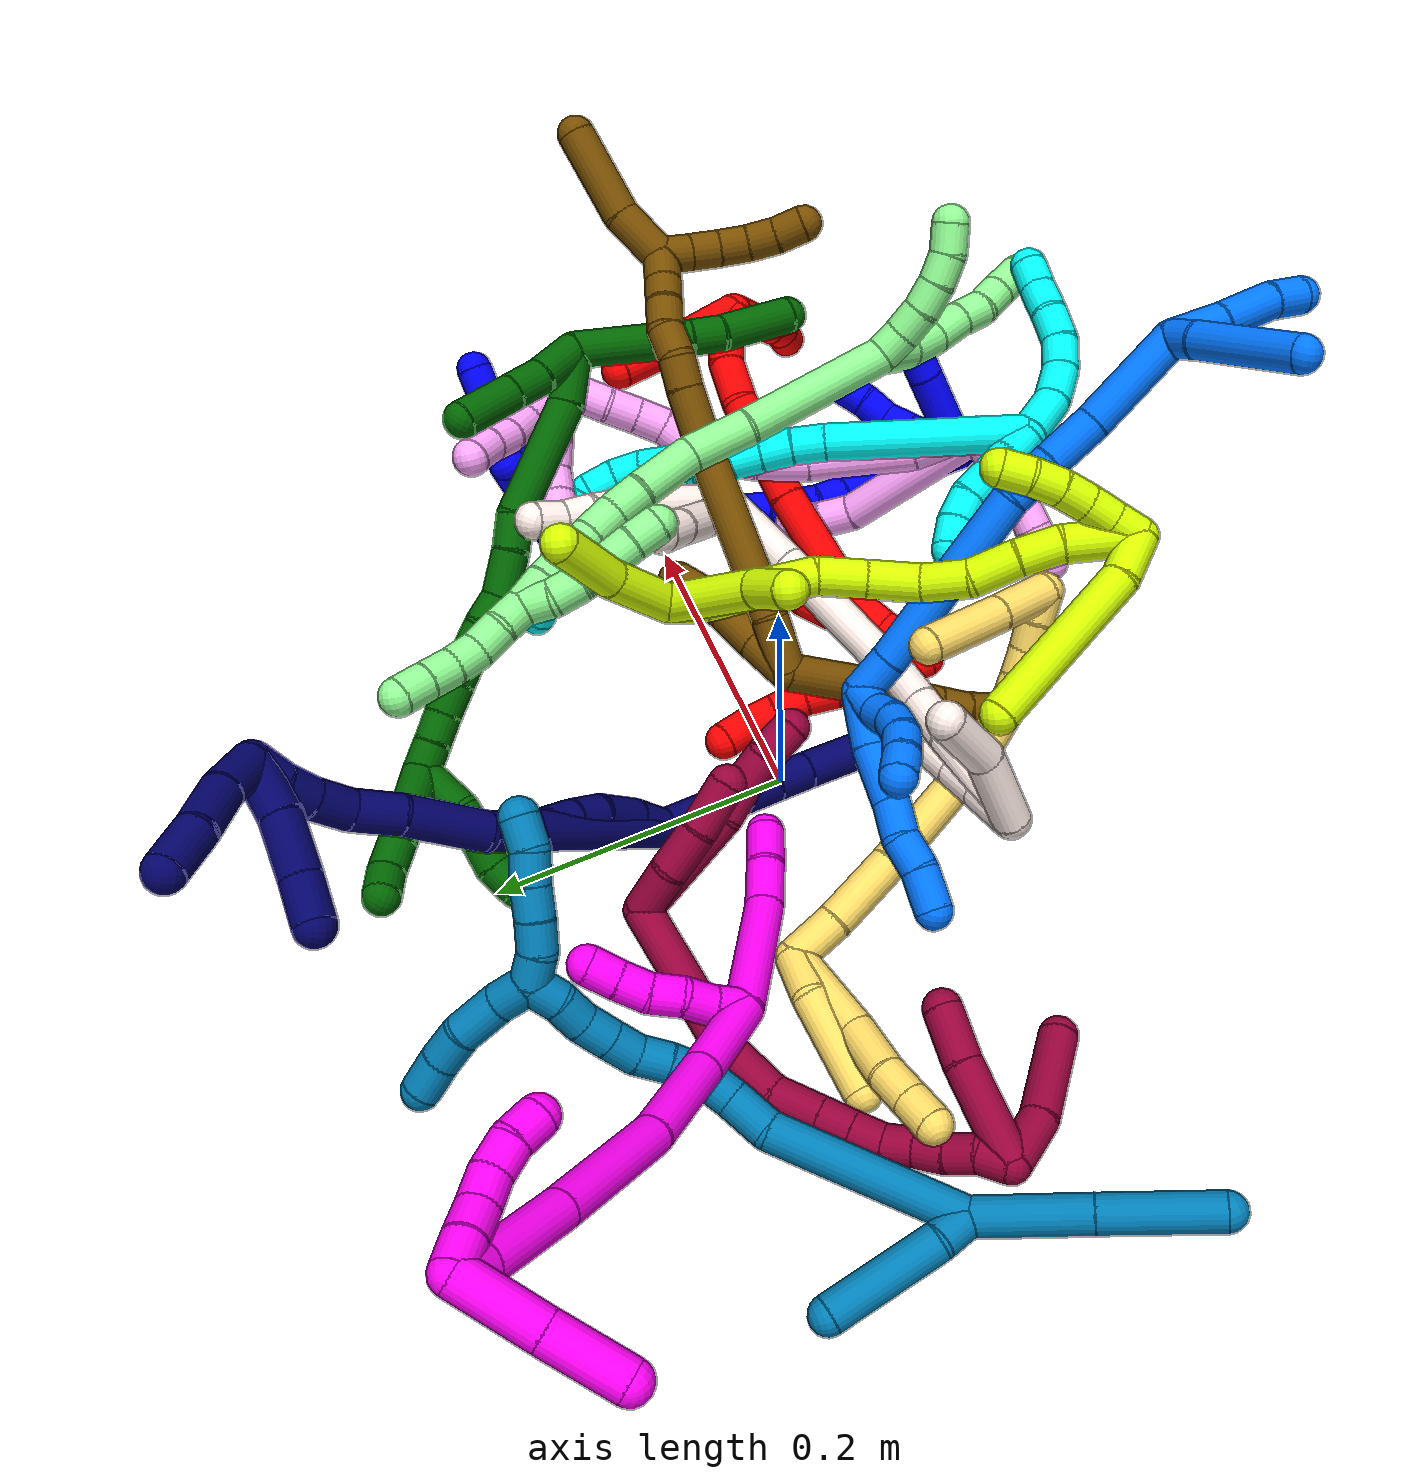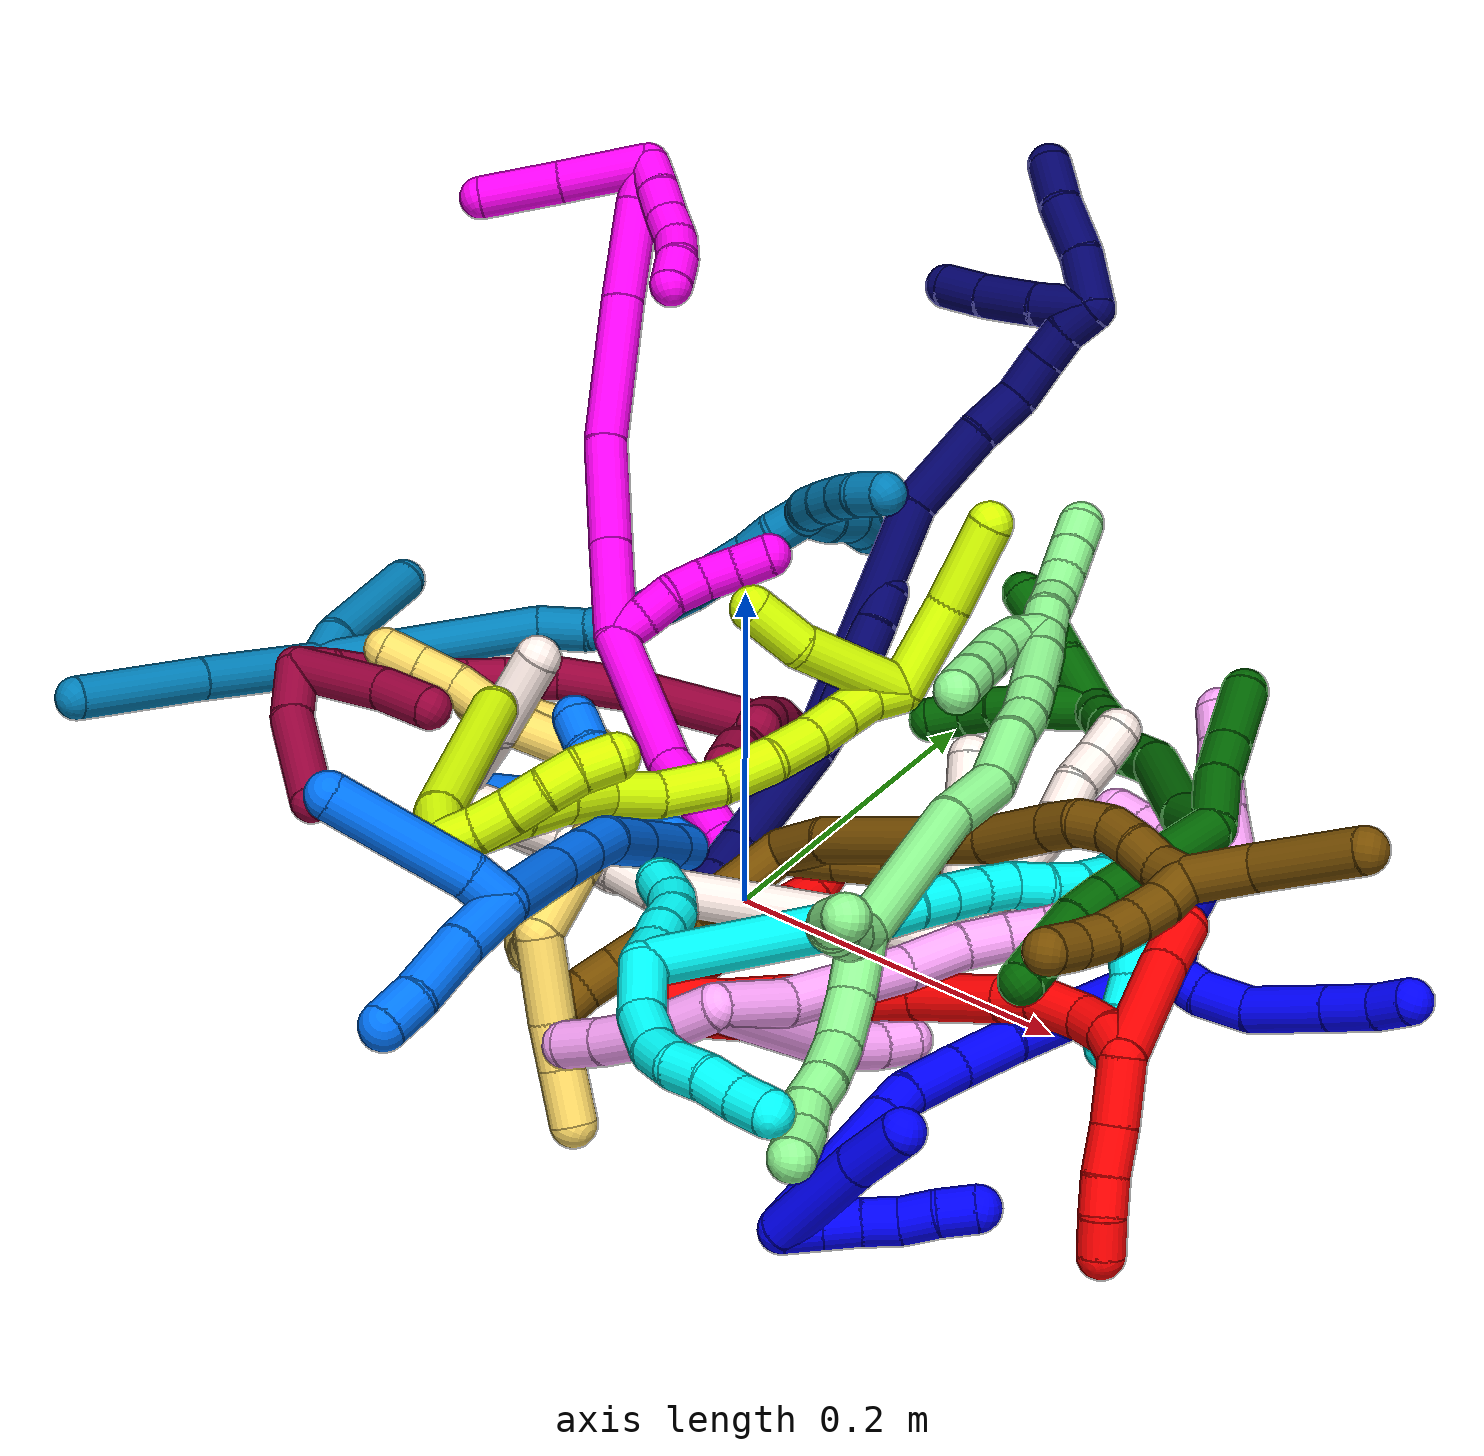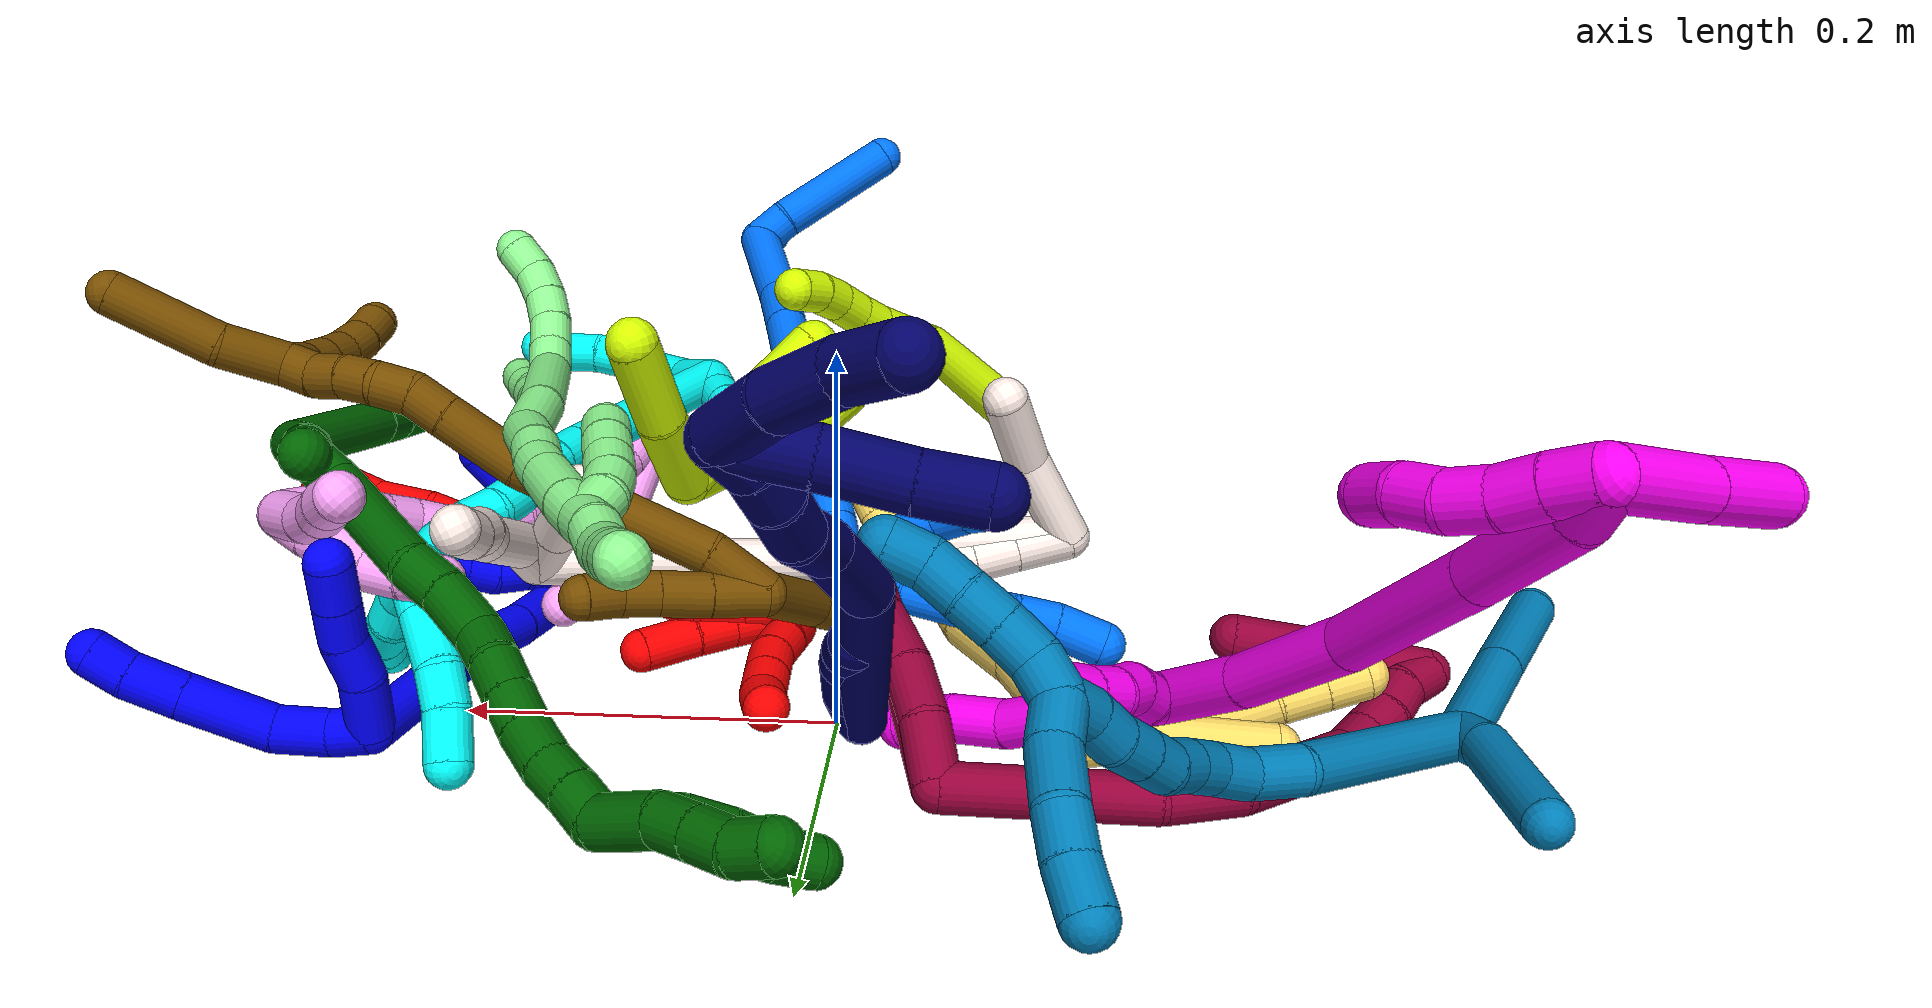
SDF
<sdf version="1.7">
 <world name="default">
  <plugin name="TubeGeneratorPlugin" filename="libtube_generator_plugin.so"/>
  <model name="photoneo_s_sensor">
   <static>1</static>
   <pose>0 0 2 1.57079 1.57079 3.14159</pose>
   <link name="link">
    <inertial><mass>0.1</mass></inertial>
    <sensor name="sensor" type="depth">
     <update_rate>30</update_rate>
     <camera>
      <horizontal_fov>1.22</horizontal_fov>
      <image><width>1920</width><height>1200</height><format>B8G8R8</format></image>
      <clip><near>0.1</near><far>4</far></clip>
      <depth_camera><output>points</output></depth_camera>
     </camera>
     <plugin name="camera_plugin" filename="libgazebo_ros_depth_camera.so">
      <baseline>0.2</baseline>
      <alwaysOn>1</alwaysOn>
      <updateRate>0.0</updateRate>
      <cameraName>camera_ir</cameraName>
      <imageTopicName>/camera/color/image_raw</imageTopicName>
      <cameraInfoTopicName>/camera/color/camera_info</cameraInfoTopicName>
      <depthImageTopicName>/camera/depth/image_raw</depthImageTopicName>
      <depthImageCameraInfoTopicName>/camera/depth/camera_info</depthImageCameraInfoTopicName>
      <pointCloudTopicName>/camera/depth/points</pointCloudTopicName>
      <frameName>fr_optical</frameName>
      <pointCloudCutoff>0.1</pointCloudCutoff>
      <pointCloudCutoffMax>2.0</pointCloudCutoffMax>
      <distortionK1>0</distortionK1>
      <distortionK2>0</distortionK2>
      <distortionK3>0</distortionK3>
      <distortionT1>0</distortionT1>
      <distortionT2>0</distortionT2>
      <CxPrime>0</CxPrime>
      <Cx>0</Cx>
      <Cy>0</Cy>
      <focalLength>0</focalLength>
      <hackBaseline>0</hackBaseline>
     </plugin>
    </sensor>
   </link>
  </model>
  <gravity>0 0 -9.8</gravity>
  <magnetic_field>6e-06 2.3e-05 -4.2e-05</magnetic_field>
  <atmosphere type="adiabatic"/>
  <physics name="default_physics" default="0" type="ode">
   <max_step_size>0.003</max_step_size>
   <real_time_factor>1</real_time_factor>
   <real_time_update_rate>1000</real_time_update_rate>
   <max_contacts>10000</max_contacts>
   <ode>
    <solver>
     <type>quick</type>
     <iters>100</iters>
     <sor>1.3</sor>
     <use_dynamic_moi_rescaling>0</use_dynamic_moi_rescaling>
    </solver>
    <constraints>
     <contact_max_correcting_vel>0</contact_max_correcting_vel>
     <contact_surface_layer>0.001</contact_surface_layer>
     <cfm>0</cfm>
     <erp>0.2</erp>
    </constraints>
   </ode>
  </physics>
  <scene><ambient>0.4 0.4 0.4 1</ambient><background>0.7 0.7 0.7 1</background><shadows>0</shadows></scene>
  <audio><device>default</device></audio>
  <spherical_coordinates>
   <surface_model>EARTH_WGS84</surface_model>
   <latitude_deg>0</latitude_deg>
   <longitude_deg>0</longitude_deg>
   <elevation>0</elevation>
   <heading_deg>0</heading_deg>
  </spherical_coordinates>
  <model name="bin">
   <static>1</static>
   <link name="bottom">
    <collision name="collision-bottom">
     <pose>0 0 -0.01 0 -0 0</pose>
     <geometry><box><size>0.8 0.6 0.02</size></box></geometry>
     <surface>
      <friction><ode><mu>100</mu><mu2>100</mu2></ode></friction>
      <contact><collide_bitmask>65535</collide_bitmask></contact>
     </surface>
    </collision>
   </link>
   <link name="west_wall">
    <collision name="collision-west_wall">
     <pose>-0.41 0 0.1 0 -0 0</pose>
     <geometry><box><size>0.02 0.6 0.2</size></box></geometry>
     <surface>
      <friction><ode><mu>100</mu><mu2>100</mu2></ode></friction>
      <contact><collide_bitmask>65535</collide_bitmask></contact>
     </surface>
    </collision>
   </link>
   <link name="east_wall">
    <collision name="collision-east_wall">
     <pose>0.41 0 0.1 0 -0 0</pose>
     <geometry><box><size>0.02 0.6 0.2</size></box></geometry>
     <surface>
      <friction><ode><mu>100</mu><mu2>100</mu2></ode></friction>
      <contact><collide_bitmask>65535</collide_bitmask></contact>
     </surface>
    </collision>
   </link>
   <link name="south_wall">
    <collision name="collision-south_wall">
     <pose>0 -0.31 0.1 0 -0 0</pose>
     <geometry><box><size>0.8 0.02 0.2</size></box></geometry>
     <surface>
      <friction><ode><mu>100</mu><mu2>100</mu2></ode></friction>
      <contact><collide_bitmask>65535</collide_bitmask></contact>
     </surface>
    </collision>
   </link>
   <link name="north_wall">
    <collision name="collision-north_wall">
     <pose>0 0.31 0.1 0 -0 0</pose>
     <geometry><box><size>0.8 0.02 0.2</size></box></geometry>
     <surface>
      <friction><ode><mu>100</mu><mu2>100</mu2></ode></friction>
      <contact><collide_bitmask>65535</collide_bitmask></contact>
     </surface>
    </collision>
   </link>
  </model>
  <model name="1">
   <static>0</static>
   <link name="1">
    <collision name="collision-cylinder-e_1_2_8">
     <pose>-0.010496 -0.000356 0.000443 0.677442 -1.51674 -0.644255</pose>
     <geometry><cylinder><radius>0.0125</radius><length>0.021023</length></cylinder></geometry>
     <surface>
      <friction><ode><mu>1.16</mu><mu2>1.16</mu2><slip1>0</slip1><slip2>0</slip2></ode></friction>
      <contact><ode><kp>1e+06</kp><kd>1</kd><max_vel>0</max_vel><min_depth>0.001</min_depth></ode></contact>
     </surface>
    </collision>
    <visual name="visual-cylinder-e_1_2_8">
     <pose>-0.010496 -0.000356 0.000443 0.677442 -1.51674 -0.644255</pose>
     <geometry><cylinder><radius>0.0125</radius><length>0.021023</length></cylinder></geometry>
     <material><ambient>0 0 1 1</ambient></material>
    </visual>
    <collision name="collision-cylinder-e_2_8_9">
     <pose>-0.035555 -0.000257 -0.002186 -2.99445 -1.36076 2.95994</pose>
     <geometry><cylinder><radius>0.0125</radius><length>0.02978</length></cylinder></geometry>
     <surface>
      <friction><ode><mu>1.16</mu><mu2>1.16</mu2><slip1>0</slip1><slip2>0</slip2></ode></friction>
      <contact><ode><kp>1e+06</kp><kd>1</kd><max_vel>0</max_vel><min_depth>0.001</min_depth></ode></contact>
     </surface>
    </collision>
    <visual name="visual-cylinder-e_2_8_9">
     <pose>-0.035555 -0.000257 -0.002186 -2.99445 -1.36076 2.95994</pose>
     <geometry><cylinder><radius>0.0125</radius><length>0.02978</length></cylinder></geometry>
     <material><ambient>0 0 1 1</ambient></material>
    </visual>
    <collision name="collision-cylinder-e_3_9_10">
     <pose>-0.071076 -0.000217 -0.017698 3.10824 -1.03484 -3.08299</pose>
     <geometry><cylinder><radius>0.0125</radius><length>0.048752</length></cylinder></geometry>
     <surface>
      <friction><ode><mu>1.16</mu><mu2>1.16</mu2><slip1>0</slip1><slip2>0</slip2></ode></friction>
      <contact><ode><kp>1e+06</kp><kd>1</kd><max_vel>0</max_vel><min_depth>0.001</min_depth></ode></contact>
     </surface>
    </collision>
    <visual name="visual-cylinder-e_3_9_10">
     <pose>-0.071076 -0.000217 -0.017698 3.10824 -1.03484 -3.08299</pose>
     <geometry><cylinder><radius>0.0125</radius><length>0.048752</length></cylinder></geometry>
     <material><ambient>0 0 1 1</ambient></material>
    </visual>
    <collision name="collision-cylinder-e_4_10_11">
     <pose>-0.104464 -0.001133 -0.037786 3.0762 -1.01832 -3.02455</pose>
     <geometry><cylinder><radius>0.0125</radius><length>0.029205</length></cylinder></geometry>
     <surface>
      <friction><ode><mu>1.16</mu><mu2>1.16</mu2><slip1>0</slip1><slip2>0</slip2></ode></friction>
      <contact><ode><kp>1e+06</kp><kd>1</kd><max_vel>0</max_vel><min_depth>0.001</min_depth></ode></contact>
     </surface>
    </collision>
    <visual name="visual-cylinder-e_4_10_11">
     <pose>-0.104464 -0.001133 -0.037786 3.0762 -1.01832 -3.02455</pose>
     <geometry><cylinder><radius>0.0125</radius><length>0.029205</length></cylinder></geometry>
     <material><ambient>0 0 1 1</ambient></material>
    </visual>
    <collision name="collision-cylinder-e_5_11_6">
     <pose>-0.125039 -0.003188 -0.052068 2.9114 -0.874117 -2.65644</pose>
     <geometry><cylinder><radius>0.0125</radius><length>0.02124</length></cylinder></geometry>
     <surface>
      <friction><ode><mu>1.16</mu><mu2>1.16</mu2><slip1>0</slip1><slip2>0</slip2></ode></friction>
      <contact><ode><kp>1e+06</kp><kd>1</kd><max_vel>0</max_vel><min_depth>0.001</min_depth></ode></contact>
     </surface>
    </collision>
    <visual name="visual-cylinder-e_5_11_6">
     <pose>-0.125039 -0.003188 -0.052068 2.9114 -0.874117 -2.65644</pose>
     <geometry><cylinder><radius>0.0125</radius><length>0.02124</length></cylinder></geometry>
     <material><ambient>0 0 1 1</ambient></material>
    </visual>
    <collision name="collision-cylinder-e_1_2_12">
     <pose>0.002243 -0.001075 -0.015877 3.07397 0.140013 2.24266</pose>
     <geometry><cylinder><radius>0.0125</radius><length>0.032142</length></cylinder></geometry>
     <surface>
      <friction><ode><mu>1.16</mu><mu2>1.16</mu2><slip1>0</slip1><slip2>0</slip2></ode></friction>
      <contact><ode><kp>1e+06</kp><kd>1</kd><max_vel>0</max_vel><min_depth>0.001</min_depth></ode></contact>
     </surface>
    </collision>
    <visual name="visual-cylinder-e_1_2_12">
     <pose>0.002243 -0.001075 -0.015877 3.07397 0.140013 2.24266</pose>
     <geometry><cylinder><radius>0.0125</radius><length>0.032142</length></cylinder></geometry>
     <material><ambient>0 0 1 1</ambient></material>
    </visual>
    <collision name="collision-cylinder-e_2_12_13">
     <pose>0.002919 -0.002958 -0.043507 3.07305 -0.132235 -2.18598</pose>
     <geometry><cylinder><radius>0.0125</radius><length>0.023768</length></cylinder></geometry>
     <surface>
      <friction><ode><mu>1.16</mu><mu2>1.16</mu2><slip1>0</slip1><slip2>0</slip2></ode></friction>
      <contact><ode><kp>1e+06</kp><kd>1</kd><max_vel>0</max_vel><min_depth>0.001</min_depth></ode></contact>
     </surface>
    </collision>
    <visual name="visual-cylinder-e_2_12_13">
     <pose>0.002919 -0.002958 -0.043507 3.07305 -0.132235 -2.18598</pose>
     <geometry><cylinder><radius>0.0125</radius><length>0.023768</length></cylinder></geometry>
     <material><ambient>0 0 1 1</ambient></material>
    </visual>
    <collision name="collision-cylinder-e_3_13_14">
     <pose>0.002597 -0.004548 -0.065833 3.06765 0.116899 2.01422</pose>
     <geometry><cylinder><radius>0.0125</radius><length>0.02135</length></cylinder></geometry>
     <surface>
      <friction><ode><mu>1.16</mu><mu2>1.16</mu2><slip1>0</slip1><slip2>0</slip2></ode></friction>
      <contact><ode><kp>1e+06</kp><kd>1</kd><max_vel>0</max_vel><min_depth>0.001</min_depth></ode></contact>
     </surface>
    </collision>
    <visual name="visual-cylinder-e_3_13_14">
     <pose>0.002597 -0.004548 -0.065833 3.06765 0.116899 2.01422</pose>
     <geometry><cylinder><radius>0.0125</radius><length>0.02135</length></cylinder></geometry>
     <material><ambient>0 0 1 1</ambient></material>
    </visual>
    <collision name="collision-cylinder-e_4_14_5">
     <pose>0.005105 -0.006343 -0.08766 3.05188 0.111341 1.78549</pose>
     <geometry><cylinder><radius>0.0125</radius><length>0.02274</length></cylinder></geometry>
     <surface>
      <friction><ode><mu>1.16</mu><mu2>1.16</mu2><slip1>0</slip1><slip2>0</slip2></ode></friction>
      <contact><ode><kp>1e+06</kp><kd>1</kd><max_vel>0</max_vel><min_depth>0.001</min_depth></ode></contact>
     </surface>
    </collision>
    <visual name="visual-cylinder-e_4_14_5">
     <pose>0.005105 -0.006343 -0.08766 3.05188 0.111341 1.78549</pose>
     <geometry><cylinder><radius>0.0125</radius><length>0.02274</length></cylinder></geometry>
     <material><ambient>0 0 1 1</ambient></material>
    </visual>
    <collision name="collision-cylinder-e_1_2_15">
     <pose>0.011967 -0.053284 0.015263 1.29181 0.212641 0.160542</pose>
     <geometry><cylinder><radius>0.0125</radius><length>0.113408</length></cylinder></geometry>
     <surface>
      <friction><ode><mu>1.16</mu><mu2>1.16</mu2><slip1>0</slip1><slip2>0</slip2></ode></friction>
      <contact><ode><kp>1e+06</kp><kd>1</kd><max_vel>0</max_vel><min_depth>0.001</min_depth></ode></contact>
     </surface>
    </collision>
    <visual name="visual-cylinder-e_1_2_15">
     <pose>0.011967 -0.053284 0.015263 1.29181 0.212641 0.160542</pose>
     <geometry><cylinder><radius>0.0125</radius><length>0.113408</length></cylinder></geometry>
     <material><ambient>0 0 1 1</ambient></material>
    </visual>
    <collision name="collision-cylinder-e_2_15_16">
     <pose>0.028751 -0.122197 0.037553 1.14829 0.274062 0.177918</pose>
     <geometry><cylinder><radius>0.0125</radius><length>0.035599</length></cylinder></geometry>
     <surface>
      <friction><ode><mu>1.16</mu><mu2>1.16</mu2><slip1>0</slip1><slip2>0</slip2></ode></friction>
      <contact><ode><kp>1e+06</kp><kd>1</kd><max_vel>0</max_vel><min_depth>0.001</min_depth></ode></contact>
     </surface>
    </collision>
    <visual name="visual-cylinder-e_2_15_16">
     <pose>0.028751 -0.122197 0.037553 1.14829 0.274062 0.177918</pose>
     <geometry><cylinder><radius>0.0125</radius><length>0.035599</length></cylinder></geometry>
     <material><ambient>0 0 1 1</ambient></material>
    </visual>
    <collision name="collision-cylinder-e_3_16_17">
     <pose>0.036825 -0.153762 0.050362 1.22274 0.189738 0.133202</pose>
     <geometry><cylinder><radius>0.0125</radius><length>0.034526</length></cylinder></geometry>
     <surface>
      <friction><ode><mu>1.16</mu><mu2>1.16</mu2><slip1>0</slip1><slip2>0</slip2></ode></friction>
      <contact><ode><kp>1e+06</kp><kd>1</kd><max_vel>0</max_vel><min_depth>0.001</min_depth></ode></contact>
     </surface>
    </collision>
    <visual name="visual-cylinder-e_3_16_17">
     <pose>0.036825 -0.153762 0.050362 1.22274 0.189738 0.133202</pose>
     <geometry><cylinder><radius>0.0125</radius><length>0.034526</length></cylinder></geometry>
     <material><ambient>0 0 1 1</ambient></material>
    </visual>
    <collision name="collision-cylinder-e_4_17_18">
     <pose>0.039229 -0.178946 0.060183 1.15898 -0.084169 -0.055102</pose>
     <geometry><cylinder><radius>0.0125</radius><length>0.020253</length></cylinder></geometry>
     <surface>
      <friction><ode><mu>1.16</mu><mu2>1.16</mu2><slip1>0</slip1><slip2>0</slip2></ode></friction>
      <contact><ode><kp>1e+06</kp><kd>1</kd><max_vel>0</max_vel><min_depth>0.001</min_depth></ode></contact>
     </surface>
    </collision>
    <visual name="visual-cylinder-e_4_17_18">
     <pose>0.039229 -0.178946 0.060183 1.15898 -0.084169 -0.055102</pose>
     <geometry><cylinder><radius>0.0125</radius><length>0.020253</length></cylinder></geometry>
     <material><ambient>0 0 1 1</ambient></material>
    </visual>
    <collision name="collision-cylinder-e_5_18_1">
     <pose>0.033236 -0.232022 0.083373 1.15885 -0.107081 -0.070106</pose>
     <geometry><cylinder><radius>0.0125</radius><length>0.096213</length></cylinder></geometry>
     <surface>
      <friction><ode><mu>1.16</mu><mu2>1.16</mu2><slip1>0</slip1><slip2>0</slip2></ode></friction>
      <contact><ode><kp>1e+06</kp><kd>1</kd><max_vel>0</max_vel><min_depth>0.001</min_depth></ode></contact>
     </surface>
    </collision>
    <visual name="visual-cylinder-e_5_18_1">
     <pose>0.033236 -0.232022 0.083373 1.15885 -0.107081 -0.070106</pose>
     <geometry><cylinder><radius>0.0125</radius><length>0.096213</length></cylinder></geometry>
     <material><ambient>0 0 1 1</ambient></material>
    </visual>
    <collision name="collision-cylinder-e_1_1_19">
     <pose>0.013473 -0.278289 0.073809 3.05693 -0.46954 -2.79106</pose>
     <geometry><cylinder><radius>0.0125</radius><length>0.064631</length></cylinder></geometry>
     <surface>
      <friction><ode><mu>1.16</mu><mu2>1.16</mu2><slip1>0</slip1><slip2>0</slip2></ode></friction>
      <contact><ode><kp>1e+06</kp><kd>1</kd><max_vel>0</max_vel><min_depth>0.001</min_depth></ode></contact>
     </surface>
    </collision>
    <visual name="visual-cylinder-e_1_1_19">
     <pose>0.013473 -0.278289 0.073809 3.05693 -0.46954 -2.79106</pose>
     <geometry><cylinder><radius>0.0125</radius><length>0.064631</length></cylinder></geometry>
     <material><ambient>0 0 1 1</ambient></material>
    </visual>
    <collision name="collision-cylinder-e_2_19_4">
     <pose>-0.010208 -0.282184 0.029977 3.04542 -0.537818 -2.79585</pose>
     <geometry><cylinder><radius>0.0125</radius><length>0.035369</length></cylinder></geometry>
     <surface>
      <friction><ode><mu>1.16</mu><mu2>1.16</mu2><slip1>0</slip1><slip2>0</slip2></ode></friction>
      <contact><ode><kp>1e+06</kp><kd>1</kd><max_vel>0</max_vel><min_depth>0.001</min_depth></ode></contact>
     </surface>
    </collision>
    <visual name="visual-cylinder-e_2_19_4">
     <pose>-0.010208 -0.282184 0.029977 3.04542 -0.537818 -2.79585</pose>
     <geometry><cylinder><radius>0.0125</radius><length>0.035369</length></cylinder></geometry>
     <material><ambient>0 0 1 1</ambient></material>
    </visual>
    <collision name="collision-cylinder-e_1_1_20">
     <pose>0.020882 -0.270056 0.098734 -2.15001 -0.805722 1.33471</pose>
     <geometry><cylinder><radius>0.0125</radius><length>0.02</length></cylinder></geometry>
     <surface>
      <friction><ode><mu>1.16</mu><mu2>1.16</mu2><slip1>0</slip1><slip2>0</slip2></ode></friction>
      <contact><ode><kp>1e+06</kp><kd>1</kd><max_vel>0</max_vel><min_depth>0.001</min_depth></ode></contact>
     </surface>
    </collision>
    <visual name="visual-cylinder-e_1_1_20">
     <pose>0.020882 -0.270056 0.098734 -2.15001 -0.805722 1.33471</pose>
     <geometry><cylinder><radius>0.0125</radius><length>0.02</length></cylinder></geometry>
     <material><ambient>0 0 1 1</ambient></material>
    </visual>
    <collision name="collision-cylinder-e_2_20_21">
     <pose>0.006445 -0.258484 0.091139 -2.15312 -0.807175 1.34029</pose>
     <geometry><cylinder><radius>0.0125</radius><length>0.02</length></cylinder></geometry>
     <surface>
      <friction><ode><mu>1.16</mu><mu2>1.16</mu2><slip1>0</slip1><slip2>0</slip2></ode></friction>
      <contact><ode><kp>1e+06</kp><kd>1</kd><max_vel>0</max_vel><min_depth>0.001</min_depth></ode></contact>
     </surface>
    </collision>
    <visual name="visual-cylinder-e_2_20_21">
     <pose>0.006445 -0.258484 0.091139 -2.15312 -0.807175 1.34029</pose>
     <geometry><cylinder><radius>0.0125</radius><length>0.02</length></cylinder></geometry>
     <material><ambient>0 0 1 1</ambient></material>
    </visual>
    <collision name="collision-cylinder-e_3_21_22">
     <pose>-0.008497 -0.24733 0.083945 -2.13339 -0.881738 1.41518</pose>
     <geometry><cylinder><radius>0.0125</radius><length>0.02</length></cylinder></geometry>
     <surface>
      <friction><ode><mu>1.16</mu><mu2>1.16</mu2><slip1>0</slip1><slip2>0</slip2></ode></friction>
      <contact><ode><kp>1e+06</kp><kd>1</kd><max_vel>0</max_vel><min_depth>0.001</min_depth></ode></contact>
     </surface>
    </collision>
    <visual name="visual-cylinder-e_3_21_22">
     <pose>-0.008497 -0.24733 0.083945 -2.13339 -0.881738 1.41518</pose>
     <geometry><cylinder><radius>0.0125</radius><length>0.02</length></cylinder></geometry>
     <material><ambient>0 0 1 1</ambient></material>
    </visual>
    <collision name="collision-cylinder-e_4_22_23">
     <pose>-0.023627 -0.238711 0.074674 -2.6378 -0.834788 2.08989</pose>
     <geometry><cylinder><radius>0.0125</radius><length>0.02</length></cylinder></geometry>
     <surface>
      <friction><ode><mu>1.16</mu><mu2>1.16</mu2><slip1>0</slip1><slip2>0</slip2></ode></friction>
      <contact><ode><kp>1e+06</kp><kd>1</kd><max_vel>0</max_vel><min_depth>0.001</min_depth></ode></contact>
     </surface>
    </collision>
    <visual name="visual-cylinder-e_4_22_23">
     <pose>-0.023627 -0.238711 0.074674 -2.6378 -0.834788 2.08989</pose>
     <geometry><cylinder><radius>0.0125</radius><length>0.02</length></cylinder></geometry>
     <material><ambient>0 0 1 1</ambient></material>
    </visual>
    <collision name="collision-cylinder-e_5_23_3">
     <pose>-0.038599 -0.23083 0.064179 -2.35358 -0.857272 1.66521</pose>
     <geometry><cylinder><radius>0.0125</radius><length>0.02</length></cylinder></geometry>
     <surface>
      <friction><ode><mu>1.16</mu><mu2>1.16</mu2><slip1>0</slip1><slip2>0</slip2></ode></friction>
      <contact><ode><kp>1e+06</kp><kd>1</kd><max_vel>0</max_vel><min_depth>0.001</min_depth></ode></contact>
     </surface>
    </collision>
    <visual name="visual-cylinder-e_5_23_3">
     <pose>-0.038599 -0.23083 0.064179 -2.35358 -0.857272 1.66521</pose>
     <geometry><cylinder><radius>0.0125</radius><length>0.02</length></cylinder></geometry>
     <material><ambient>0 0 1 1</ambient></material>
    </visual>
    <collision name="collision-sphere-3">
     <pose>-0.04616 -0.22619 0.059563 0 -0 0</pose>
     <geometry><sphere><radius>0.0125</radius></sphere></geometry>
     <surface>
      <friction><ode><mu>1.16</mu><mu2>1.16</mu2><slip1>0</slip1><slip2>0</slip2></ode></friction>
      <contact><ode><kp>1e+06</kp><kd>1</kd><max_vel>0</max_vel><min_depth>0.001</min_depth></ode></contact>
     </surface>
    </collision>
    <visual name="visual-sphere-3">
     <pose>-0.04616 -0.22619 0.059563 0 -0 0</pose>
     <geometry><sphere><radius>0.0125</radius></sphere></geometry>
     <material><ambient>0 0 1 1</ambient></material>
    </visual>
    <collision name="collision-sphere-23">
     <pose>-0.031038 -0.23547 0.068795 0 -0 0</pose>
     <geometry><sphere><radius>0.0125</radius></sphere></geometry>
     <surface>
      <friction><ode><mu>1.16</mu><mu2>1.16</mu2><slip1>0</slip1><slip2>0</slip2></ode></friction>
      <contact><ode><kp>1e+06</kp><kd>1</kd><max_vel>0</max_vel><min_depth>0.001</min_depth></ode></contact>
     </surface>
    </collision>
    <visual name="visual-sphere-23">
     <pose>-0.031038 -0.23547 0.068795 0 -0 0</pose>
     <geometry><sphere><radius>0.0125</radius></sphere></geometry>
     <material><ambient>0 0 1 1</ambient></material>
    </visual>
    <collision name="collision-sphere-22">
     <pose>-0.016215 -0.241952 0.080553 0 -0 0</pose>
     <geometry><sphere><radius>0.0125</radius></sphere></geometry>
     <surface>
      <friction><ode><mu>1.16</mu><mu2>1.16</mu2><slip1>0</slip1><slip2>0</slip2></ode></friction>
      <contact><ode><kp>1e+06</kp><kd>1</kd><max_vel>0</max_vel><min_depth>0.001</min_depth></ode></contact>
     </surface>
    </collision>
    <visual name="visual-sphere-22">
     <pose>-0.016215 -0.241952 0.080553 0 -0 0</pose>
     <geometry><sphere><radius>0.0125</radius></sphere></geometry>
     <material><ambient>0 0 1 1</ambient></material>
    </visual>
    <collision name="collision-sphere-21">
     <pose>-0.000778 -0.252708 0.087336 0 -0 0</pose>
     <geometry><sphere><radius>0.0125</radius></sphere></geometry>
     <surface>
      <friction><ode><mu>1.16</mu><mu2>1.16</mu2><slip1>0</slip1><slip2>0</slip2></ode></friction>
      <contact><ode><kp>1e+06</kp><kd>1</kd><max_vel>0</max_vel><min_depth>0.001</min_depth></ode></contact>
     </surface>
    </collision>
    <visual name="visual-sphere-21">
     <pose>-0.000778 -0.252708 0.087336 0 -0 0</pose>
     <geometry><sphere><radius>0.0125</radius></sphere></geometry>
     <material><ambient>0 0 1 1</ambient></material>
    </visual>
    <collision name="collision-sphere-20">
     <pose>0.013668 -0.264259 0.094943 0 -0 0</pose>
     <geometry><sphere><radius>0.0125</radius></sphere></geometry>
     <surface>
      <friction><ode><mu>1.16</mu><mu2>1.16</mu2><slip1>0</slip1><slip2>0</slip2></ode></friction>
      <contact><ode><kp>1e+06</kp><kd>1</kd><max_vel>0</max_vel><min_depth>0.001</min_depth></ode></contact>
     </surface>
    </collision>
    <visual name="visual-sphere-20">
     <pose>0.013668 -0.264259 0.094943 0 -0 0</pose>
     <geometry><sphere><radius>0.0125</radius></sphere></geometry>
     <material><ambient>0 0 1 1</ambient></material>
    </visual>
    <collision name="collision-sphere-4">
     <pose>-0.019267 -0.283642 0.014859 0 -0 0</pose>
     <geometry><sphere><radius>0.0125</radius></sphere></geometry>
     <surface>
      <friction><ode><mu>1.16</mu><mu2>1.16</mu2><slip1>0</slip1><slip2>0</slip2></ode></friction>
      <contact><ode><kp>1e+06</kp><kd>1</kd><max_vel>0</max_vel><min_depth>0.001</min_depth></ode></contact>
     </surface>
    </collision>
    <visual name="visual-sphere-4">
     <pose>-0.019267 -0.283642 0.014859 0 -0 0</pose>
     <geometry><sphere><radius>0.0125</radius></sphere></geometry>
     <material><ambient>0 0 1 1</ambient></material>
    </visual>
    <collision name="collision-sphere-6">
     <pose>-0.133185 -0.004743 -0.058702 0 -0 0</pose>
     <geometry><sphere><radius>0.0125</radius></sphere></geometry>
     <surface>
      <friction><ode><mu>1.16</mu><mu2>1.16</mu2><slip1>0</slip1><slip2>0</slip2></ode></friction>
      <contact><ode><kp>1e+06</kp><kd>1</kd><max_vel>0</max_vel><min_depth>0.001</min_depth></ode></contact>
     </surface>
    </collision>
    <visual name="visual-sphere-6">
     <pose>-0.133185 -0.004743 -0.058702 0 -0 0</pose>
     <geometry><sphere><radius>0.0125</radius></sphere></geometry>
     <material><ambient>0 0 1 1</ambient></material>
    </visual>
    <collision name="collision-sphere-11">
     <pose>-0.116894 -0.001633 -0.045433 0 -0 0</pose>
     <geometry><sphere><radius>0.0125</radius></sphere></geometry>
     <surface>
      <friction><ode><mu>1.16</mu><mu2>1.16</mu2><slip1>0</slip1><slip2>0</slip2></ode></friction>
      <contact><ode><kp>1e+06</kp><kd>1</kd><max_vel>0</max_vel><min_depth>0.001</min_depth></ode></contact>
     </surface>
    </collision>
    <visual name="visual-sphere-11">
     <pose>-0.116894 -0.001633 -0.045433 0 -0 0</pose>
     <geometry><sphere><radius>0.0125</radius></sphere></geometry>
     <material><ambient>0 0 1 1</ambient></material>
    </visual>
    <collision name="collision-sphere-10">
     <pose>-0.092034 -0.000632 -0.030139 0 -0 0</pose>
     <geometry><sphere><radius>0.0125</radius></sphere></geometry>
     <surface>
      <friction><ode><mu>1.16</mu><mu2>1.16</mu2><slip1>0</slip1><slip2>0</slip2></ode></friction>
      <contact><ode><kp>1e+06</kp><kd>1</kd><max_vel>0</max_vel><min_depth>0.001</min_depth></ode></contact>
     </surface>
    </collision>
    <visual name="visual-sphere-10">
     <pose>-0.092034 -0.000632 -0.030139 0 -0 0</pose>
     <geometry><sphere><radius>0.0125</radius></sphere></geometry>
     <material><ambient>0 0 1 1</ambient></material>
    </visual>
    <collision name="collision-sphere-9">
     <pose>-0.050118 0.000198 -0.005257 0 -0 0</pose>
     <geometry><sphere><radius>0.0125</radius></sphere></geometry>
     <surface>
      <friction><ode><mu>1.16</mu><mu2>1.16</mu2><slip1>0</slip1><slip2>0</slip2></ode></friction>
      <contact><ode><kp>1e+06</kp><kd>1</kd><max_vel>0</max_vel><min_depth>0.001</min_depth></ode></contact>
     </surface>
    </collision>
    <visual name="visual-sphere-9">
     <pose>-0.050118 0.000198 -0.005257 0 -0 0</pose>
     <geometry><sphere><radius>0.0125</radius></sphere></geometry>
     <material><ambient>0 0 1 1</ambient></material>
    </visual>
    <collision name="collision-sphere-2">
     <geometry><sphere><radius>0.0125</radius></sphere></geometry>
     <surface>
      <friction><ode><mu>1.16</mu><mu2>1.16</mu2><slip1>0</slip1><slip2>0</slip2></ode></friction>
      <contact><ode><kp>1e+06</kp><kd>1</kd><max_vel>0</max_vel><min_depth>0.001</min_depth></ode></contact>
     </surface>
    </collision>
    <visual name="visual-sphere-2">
     <geometry><sphere><radius>0.0125</radius></sphere></geometry>
     <material><ambient>0 0 1 1</ambient></material>
    </visual>
    <collision name="collision-sphere-19">
     <pose>-0.001149 -0.280726 0.045094 0 -0 0</pose>
     <geometry><sphere><radius>0.0125</radius></sphere></geometry>
     <surface>
      <friction><ode><mu>1.16</mu><mu2>1.16</mu2><slip1>0</slip1><slip2>0</slip2></ode></friction>
      <contact><ode><kp>1e+06</kp><kd>1</kd><max_vel>0</max_vel><min_depth>0.001</min_depth></ode></contact>
     </surface>
    </collision>
    <visual name="visual-sphere-19">
     <pose>-0.001149 -0.280726 0.045094 0 -0 0</pose>
     <geometry><sphere><radius>0.0125</radius></sphere></geometry>
     <material><ambient>0 0 1 1</ambient></material>
    </visual>
    <collision name="collision-sphere-8">
     <pose>-0.020993 -0.000712 0.000885 0 -0 0</pose>
     <geometry><sphere><radius>0.0125</radius></sphere></geometry>
     <surface>
      <friction><ode><mu>1.16</mu><mu2>1.16</mu2><slip1>0</slip1><slip2>0</slip2></ode></friction>
      <contact><ode><kp>1e+06</kp><kd>1</kd><max_vel>0</max_vel><min_depth>0.001</min_depth></ode></contact>
     </surface>
    </collision>
    <visual name="visual-sphere-8">
     <pose>-0.020993 -0.000712 0.000885 0 -0 0</pose>
     <geometry><sphere><radius>0.0125</radius></sphere></geometry>
     <material><ambient>0 0 1 1</ambient></material>
    </visual>
    <collision name="collision-sphere-12">
     <pose>0.004486 -0.002151 -0.031754 0 -0 0</pose>
     <geometry><sphere><radius>0.0125</radius></sphere></geometry>
     <surface>
      <friction><ode><mu>1.16</mu><mu2>1.16</mu2><slip1>0</slip1><slip2>0</slip2></ode></friction>
      <contact><ode><kp>1e+06</kp><kd>1</kd><max_vel>0</max_vel><min_depth>0.001</min_depth></ode></contact>
     </surface>
    </collision>
    <visual name="visual-sphere-12">
     <pose>0.004486 -0.002151 -0.031754 0 -0 0</pose>
     <geometry><sphere><radius>0.0125</radius></sphere></geometry>
     <material><ambient>0 0 1 1</ambient></material>
    </visual>
    <collision name="collision-sphere-13">
     <pose>0.001352 -0.003764 -0.05526 0 -0 0</pose>
     <geometry><sphere><radius>0.0125</radius></sphere></geometry>
     <surface>
      <friction><ode><mu>1.16</mu><mu2>1.16</mu2><slip1>0</slip1><slip2>0</slip2></ode></friction>
      <contact><ode><kp>1e+06</kp><kd>1</kd><max_vel>0</max_vel><min_depth>0.001</min_depth></ode></contact>
     </surface>
    </collision>
    <visual name="visual-sphere-13">
     <pose>0.001352 -0.003764 -0.05526 0 -0 0</pose>
     <geometry><sphere><radius>0.0125</radius></sphere></geometry>
     <material><ambient>0 0 1 1</ambient></material>
    </visual>
    <collision name="collision-sphere-14">
     <pose>0.003842 -0.005331 -0.076406 0 -0 0</pose>
     <geometry><sphere><radius>0.0125</radius></sphere></geometry>
     <surface>
      <friction><ode><mu>1.16</mu><mu2>1.16</mu2><slip1>0</slip1><slip2>0</slip2></ode></friction>
      <contact><ode><kp>1e+06</kp><kd>1</kd><max_vel>0</max_vel><min_depth>0.001</min_depth></ode></contact>
     </surface>
    </collision>
    <visual name="visual-sphere-14">
     <pose>0.003842 -0.005331 -0.076406 0 -0 0</pose>
     <geometry><sphere><radius>0.0125</radius></sphere></geometry>
     <material><ambient>0 0 1 1</ambient></material>
    </visual>
    <collision name="collision-sphere-5">
     <pose>0.006368 -0.007356 -0.098915 0 -0 0</pose>
     <geometry><sphere><radius>0.0125</radius></sphere></geometry>
     <surface>
      <friction><ode><mu>1.16</mu><mu2>1.16</mu2><slip1>0</slip1><slip2>0</slip2></ode></friction>
      <contact><ode><kp>1e+06</kp><kd>1</kd><max_vel>0</max_vel><min_depth>0.001</min_depth></ode></contact>
     </surface>
    </collision>
    <visual name="visual-sphere-5">
     <pose>0.006368 -0.007356 -0.098915 0 -0 0</pose>
     <geometry><sphere><radius>0.0125</radius></sphere></geometry>
     <material><ambient>0 0 1 1</ambient></material>
    </visual>
    <collision name="collision-sphere-15">
     <pose>0.023934 -0.106568 0.030527 0 -0 0</pose>
     <geometry><sphere><radius>0.0125</radius></sphere></geometry>
     <surface>
      <friction><ode><mu>1.16</mu><mu2>1.16</mu2><slip1>0</slip1><slip2>0</slip2></ode></friction>
      <contact><ode><kp>1e+06</kp><kd>1</kd><max_vel>0</max_vel><min_depth>0.001</min_depth></ode></contact>
     </surface>
    </collision>
    <visual name="visual-sphere-15">
     <pose>0.023934 -0.106568 0.030527 0 -0 0</pose>
     <geometry><sphere><radius>0.0125</radius></sphere></geometry>
     <material><ambient>0 0 1 1</ambient></material>
    </visual>
    <collision name="collision-sphere-16">
     <pose>0.033569 -0.137825 0.04458 0 -0 0</pose>
     <geometry><sphere><radius>0.0125</radius></sphere></geometry>
     <surface>
      <friction><ode><mu>1.16</mu><mu2>1.16</mu2><slip1>0</slip1><slip2>0</slip2></ode></friction>
      <contact><ode><kp>1e+06</kp><kd>1</kd><max_vel>0</max_vel><min_depth>0.001</min_depth></ode></contact>
     </surface>
    </collision>
    <visual name="visual-sphere-16">
     <pose>0.033569 -0.137825 0.04458 0 -0 0</pose>
     <geometry><sphere><radius>0.0125</radius></sphere></geometry>
     <material><ambient>0 0 1 1</ambient></material>
    </visual>
    <collision name="collision-sphere-17">
     <pose>0.04008 -0.169699 0.056144 0 -0 0</pose>
     <geometry><sphere><radius>0.0125</radius></sphere></geometry>
     <surface>
      <friction><ode><mu>1.16</mu><mu2>1.16</mu2><slip1>0</slip1><slip2>0</slip2></ode></friction>
      <contact><ode><kp>1e+06</kp><kd>1</kd><max_vel>0</max_vel><min_depth>0.001</min_depth></ode></contact>
     </surface>
    </collision>
    <visual name="visual-sphere-17">
     <pose>0.04008 -0.169699 0.056144 0 -0 0</pose>
     <geometry><sphere><radius>0.0125</radius></sphere></geometry>
     <material><ambient>0 0 1 1</ambient></material>
    </visual>
    <collision name="collision-sphere-18">
     <pose>0.038378 -0.188193 0.064222 0 -0 0</pose>
     <geometry><sphere><radius>0.0125</radius></sphere></geometry>
     <surface>
      <friction><ode><mu>1.16</mu><mu2>1.16</mu2><slip1>0</slip1><slip2>0</slip2></ode></friction>
      <contact><ode><kp>1e+06</kp><kd>1</kd><max_vel>0</max_vel><min_depth>0.001</min_depth></ode></contact>
     </surface>
    </collision>
    <visual name="visual-sphere-18">
     <pose>0.038378 -0.188193 0.064222 0 -0 0</pose>
     <geometry><sphere><radius>0.0125</radius></sphere></geometry>
     <material><ambient>0 0 1 1</ambient></material>
    </visual>
    <collision name="collision-sphere-1">
     <pose>0.028095 -0.275852 0.102524 0 -0 0</pose>
     <geometry><sphere><radius>0.0125</radius></sphere></geometry>
     <surface>
      <friction><ode><mu>1.16</mu><mu2>1.16</mu2><slip1>0</slip1><slip2>0</slip2></ode></friction>
      <contact><ode><kp>1e+06</kp><kd>1</kd><max_vel>0</max_vel><min_depth>0.001</min_depth></ode></contact>
     </surface>
    </collision>
    <visual name="visual-sphere-1">
     <pose>0.028095 -0.275852 0.102524 0 -0 0</pose>
     <geometry><sphere><radius>0.0125</radius></sphere></geometry>
     <material><ambient>0 0 1 1</ambient></material>
    </visual>
    <inertial>
     <pose>-0.003803 -0.126663 0.026746 0 -0 0</pose>
     <mass>0.75</mass>
     <inertia>
      <ixx>0.000169</ixx>
      <ixy>0</ixy>
      <ixz>0</ixz>
      <iyy>0.000129</iyy>
      <iyz>0</iyz>
      <izz>0.000202</izz>
     </inertia>
    </inertial>
   </link>
   <pose>0.231174 0.066594 0.014815 -2.80644 -0.130219 3.09379</pose>
  </model>
  <model name="2">
   <static>0</static>
   <link name="2">
    <collision name="collision-cylinder-e_1_2_8">
     <pose>0.000974 -0.001153 -0.019559 3.08273 0.049694 1.40224</pose>
     <geometry><cylinder><radius>0.0125</radius><length>0.039233</length></cylinder></geometry>
     <surface>
      <friction><ode><mu>1.16</mu><mu2>1.16</mu2><slip1>0</slip1><slip2>0</slip2></ode></friction>
      <contact><ode><kp>1e+06</kp><kd>1</kd><max_vel>0</max_vel><min_depth>0.001</min_depth></ode></contact>
     </surface>
    </collision>
    <visual name="visual-cylinder-e_1_2_8">
     <pose>0.000974 -0.001153 -0.019559 3.08273 0.049694 1.40224</pose>
     <geometry><cylinder><radius>0.0125</radius><length>0.039233</length></cylinder></geometry>
     <material><ambient>1 0 0 1</ambient></material>
    </visual>
    <collision name="collision-cylinder-e_2_8_9">
     <pose>0.004702 -0.002875 -0.052512 3.0991 0.202523 2.72928</pose>
     <geometry><cylinder><radius>0.0125</radius><length>0.027374</length></cylinder></geometry>
     <surface>
      <friction><ode><mu>1.16</mu><mu2>1.16</mu2><slip1>0</slip1><slip2>0</slip2></ode></friction>
      <contact><ode><kp>1e+06</kp><kd>1</kd><max_vel>0</max_vel><min_depth>0.001</min_depth></ode></contact>
     </surface>
    </collision>
    <visual name="visual-cylinder-e_2_8_9">
     <pose>0.004702 -0.002875 -0.052512 3.0991 0.202523 2.72928</pose>
     <geometry><cylinder><radius>0.0125</radius><length>0.027374</length></cylinder></geometry>
     <material><ambient>1 0 0 1</ambient></material>
    </visual>
    <collision name="collision-cylinder-e_3_9_10">
     <pose>0.010183 -0.005819 -0.076003 2.91055 0.257233 1.67905</pose>
     <geometry><cylinder><radius>0.0125</radius><length>0.021448</length></cylinder></geometry>
     <surface>
      <friction><ode><mu>1.16</mu><mu2>1.16</mu2><slip1>0</slip1><slip2>0</slip2></ode></friction>
      <contact><ode><kp>1e+06</kp><kd>1</kd><max_vel>0</max_vel><min_depth>0.001</min_depth></ode></contact>
     </surface>
    </collision>
    <visual name="visual-cylinder-e_3_9_10">
     <pose>0.010183 -0.005819 -0.076003 2.91055 0.257233 1.67905</pose>
     <geometry><cylinder><radius>0.0125</radius><length>0.021448</length></cylinder></geometry>
     <material><ambient>1 0 0 1</ambient></material>
    </visual>
    <collision name="collision-cylinder-e_4_10_11">
     <pose>0.013217 -0.010912 -0.096619 2.88878 0.02812 0.220388</pose>
     <geometry><cylinder><radius>0.0125</radius><length>0.02174</length></cylinder></geometry>
     <surface>
      <friction><ode><mu>1.16</mu><mu2>1.16</mu2><slip1>0</slip1><slip2>0</slip2></ode></friction>
      <contact><ode><kp>1e+06</kp><kd>1</kd><max_vel>0</max_vel><min_depth>0.001</min_depth></ode></contact>
     </surface>
    </collision>
    <visual name="visual-cylinder-e_4_10_11">
     <pose>0.013217 -0.010912 -0.096619 2.88878 0.02812 0.220388</pose>
     <geometry><cylinder><radius>0.0125</radius><length>0.02174</length></cylinder></geometry>
     <material><ambient>1 0 0 1</ambient></material>
    </visual>
    <collision name="collision-cylinder-e_5_11_12">
     <pose>0.013751 -0.016299 -0.116855 2.87346 0.02267 0.167689</pose>
     <geometry><cylinder><radius>0.0125</radius><length>0.020157</length></cylinder></geometry>
     <surface>
      <friction><ode><mu>1.16</mu><mu2>1.16</mu2><slip1>0</slip1><slip2>0</slip2></ode></friction>
      <contact><ode><kp>1e+06</kp><kd>1</kd><max_vel>0</max_vel><min_depth>0.001</min_depth></ode></contact>
     </surface>
    </collision>
    <visual name="visual-cylinder-e_5_11_12">
     <pose>0.013751 -0.016299 -0.116855 2.87346 0.02267 0.167689</pose>
     <geometry><cylinder><radius>0.0125</radius><length>0.020157</length></cylinder></geometry>
     <material><ambient>1 0 0 1</ambient></material>
    </visual>
    <collision name="collision-cylinder-e_6_12_6">
     <pose>0.012825 -0.018709 -0.136525 -3.11551 -0.115426 2.69758</pose>
     <geometry><cylinder><radius>0.0125</radius><length>0.020047</length></cylinder></geometry>
     <surface>
      <friction><ode><mu>1.16</mu><mu2>1.16</mu2><slip1>0</slip1><slip2>0</slip2></ode></friction>
      <contact><ode><kp>1e+06</kp><kd>1</kd><max_vel>0</max_vel><min_depth>0.001</min_depth></ode></contact>
     </surface>
    </collision>
    <visual name="visual-cylinder-e_6_12_6">
     <pose>0.012825 -0.018709 -0.136525 -3.11551 -0.115426 2.69758</pose>
     <geometry><cylinder><radius>0.0125</radius><length>0.020047</length></cylinder></geometry>
     <material><ambient>1 0 0 1</ambient></material>
    </visual>
    <collision name="collision-cylinder-e_1_2_13">
     <pose>0.009349 -0.005929 -0.002731 2.00237 0.961268 1.36665</pose>
     <geometry><cylinder><radius>0.0125</radius><length>0.022805</length></cylinder></geometry>
     <surface>
      <friction><ode><mu>1.16</mu><mu2>1.16</mu2><slip1>0</slip1><slip2>0</slip2></ode></friction>
      <contact><ode><kp>1e+06</kp><kd>1</kd><max_vel>0</max_vel><min_depth>0.001</min_depth></ode></contact>
     </surface>
    </collision>
    <visual name="visual-cylinder-e_1_2_13">
     <pose>0.009349 -0.005929 -0.002731 2.00237 0.961268 1.36665</pose>
     <geometry><cylinder><radius>0.0125</radius><length>0.022805</length></cylinder></geometry>
     <material><ambient>1 0 0 1</ambient></material>
    </visual>
    <collision name="collision-cylinder-e_2_13_14">
     <pose>0.027716 -0.015461 -0.010474 2.51845 0.970464 2.04495</pose>
     <geometry><cylinder><radius>0.0125</radius><length>0.021857</length></cylinder></geometry>
     <surface>
      <friction><ode><mu>1.16</mu><mu2>1.16</mu2><slip1>0</slip1><slip2>0</slip2></ode></friction>
      <contact><ode><kp>1e+06</kp><kd>1</kd><max_vel>0</max_vel><min_depth>0.001</min_depth></ode></contact>
     </surface>
    </collision>
    <visual name="visual-cylinder-e_2_13_14">
     <pose>0.027716 -0.015461 -0.010474 2.51845 0.970464 2.04495</pose>
     <geometry><cylinder><radius>0.0125</radius><length>0.021857</length></cylinder></geometry>
     <material><ambient>1 0 0 1</ambient></material>
    </visual>
    <collision name="collision-cylinder-e_3_14_15">
     <pose>0.046125 -0.022925 -0.02124 2.55051 0.93522 2.05645</pose>
     <geometry><cylinder><radius>0.0125</radius><length>0.023342</length></cylinder></geometry>
     <surface>
      <friction><ode><mu>1.16</mu><mu2>1.16</mu2><slip1>0</slip1><slip2>0</slip2></ode></friction>
      <contact><ode><kp>1e+06</kp><kd>1</kd><max_vel>0</max_vel><min_depth>0.001</min_depth></ode></contact>
     </surface>
    </collision>
    <visual name="visual-cylinder-e_3_14_15">
     <pose>0.046125 -0.022925 -0.02124 2.55051 0.93522 2.05645</pose>
     <geometry><cylinder><radius>0.0125</radius><length>0.023342</length></cylinder></geometry>
     <material><ambient>1 0 0 1</ambient></material>
    </visual>
    <collision name="collision-cylinder-e_4_15_5">
     <pose>0.068607 -0.033113 -0.03367 2.38307 0.958257 1.83278</pose>
     <geometry><cylinder><radius>0.0125</radius><length>0.031996</length></cylinder></geometry>
     <surface>
      <friction><ode><mu>1.16</mu><mu2>1.16</mu2><slip1>0</slip1><slip2>0</slip2></ode></friction>
      <contact><ode><kp>1e+06</kp><kd>1</kd><max_vel>0</max_vel><min_depth>0.001</min_depth></ode></contact>
     </surface>
    </collision>
    <visual name="visual-cylinder-e_4_15_5">
     <pose>0.068607 -0.033113 -0.03367 2.38307 0.958257 1.83278</pose>
     <geometry><cylinder><radius>0.0125</radius><length>0.031996</length></cylinder></geometry>
     <material><ambient>1 0 0 1</ambient></material>
    </visual>
    <collision name="collision-cylinder-e_1_2_16">
     <pose>0.017 -0.003996 -0.006508 2.59094 1.14862 2.31831</pose>
     <geometry><cylinder><radius>0.0125</radius><length>0.037274</length></cylinder></geometry>
     <surface>
      <friction><ode><mu>1.16</mu><mu2>1.16</mu2><slip1>0</slip1><slip2>0</slip2></ode></friction>
      <contact><ode><kp>1e+06</kp><kd>1</kd><max_vel>0</max_vel><min_depth>0.001</min_depth></ode></contact>
     </surface>
    </collision>
    <visual name="visual-cylinder-e_1_2_16">
     <pose>0.017 -0.003996 -0.006508 2.59094 1.14862 2.31831</pose>
     <geometry><cylinder><radius>0.0125</radius><length>0.037274</length></cylinder></geometry>
     <material><ambient>1 0 0 1</ambient></material>
    </visual>
    <collision name="collision-cylinder-e_2_16_17">
     <pose>0.046475 -0.009094 -0.017863 2.91794 1.19157 2.8133</pose>
     <geometry><cylinder><radius>0.0125</radius><length>0.026857</length></cylinder></geometry>
     <surface>
      <friction><ode><mu>1.16</mu><mu2>1.16</mu2><slip1>0</slip1><slip2>0</slip2></ode></friction>
      <contact><ode><kp>1e+06</kp><kd>1</kd><max_vel>0</max_vel><min_depth>0.001</min_depth></ode></contact>
     </surface>
    </collision>
    <visual name="visual-cylinder-e_2_16_17">
     <pose>0.046475 -0.009094 -0.017863 2.91794 1.19157 2.8133</pose>
     <geometry><cylinder><radius>0.0125</radius><length>0.026857</length></cylinder></geometry>
     <material><ambient>1 0 0 1</ambient></material>
    </visual>
    <collision name="collision-cylinder-e_3_17_18">
     <pose>0.10181 -0.00763 -0.025689 -2.43045 1.47931 -2.36857</pose>
     <geometry><cylinder><radius>0.0125</radius><length>0.08608</length></cylinder></geometry>
     <surface>
      <friction><ode><mu>1.16</mu><mu2>1.16</mu2><slip1>0</slip1><slip2>0</slip2></ode></friction>
      <contact><ode><kp>1e+06</kp><kd>1</kd><max_vel>0</max_vel><min_depth>0.001</min_depth></ode></contact>
     </surface>
    </collision>
    <visual name="visual-cylinder-e_3_17_18">
     <pose>0.10181 -0.00763 -0.025689 -2.43045 1.47931 -2.36857</pose>
     <geometry><cylinder><radius>0.0125</radius><length>0.08608</length></cylinder></geometry>
     <material><ambient>1 0 0 1</ambient></material>
    </visual>
    <collision name="collision-cylinder-e_4_18_19">
     <pose>0.171159 -0.002875 -0.028184 -1.35343 1.48638 -1.27174</pose>
     <geometry><cylinder><radius>0.0125</radius><length>0.053167</length></cylinder></geometry>
     <surface>
      <friction><ode><mu>1.16</mu><mu2>1.16</mu2><slip1>0</slip1><slip2>0</slip2></ode></friction>
      <contact><ode><kp>1e+06</kp><kd>1</kd><max_vel>0</max_vel><min_depth>0.001</min_depth></ode></contact>
     </surface>
    </collision>
    <visual name="visual-cylinder-e_4_18_19">
     <pose>0.171159 -0.002875 -0.028184 -1.35343 1.48638 -1.27174</pose>
     <geometry><cylinder><radius>0.0125</radius><length>0.053167</length></cylinder></geometry>
     <material><ambient>1 0 0 1</ambient></material>
    </visual>
    <collision name="collision-cylinder-e_5_19_20">
     <pose>0.208388 0.000268 -0.027485 -1.34875 1.47992 -1.26097</pose>
     <geometry><cylinder><radius>0.0125</radius><length>0.02157</length></cylinder></geometry>
     <surface>
      <friction><ode><mu>1.16</mu><mu2>1.16</mu2><slip1>0</slip1><slip2>0</slip2></ode></friction>
      <contact><ode><kp>1e+06</kp><kd>1</kd><max_vel>0</max_vel><min_depth>0.001</min_depth></ode></contact>
     </surface>
    </collision>
    <visual name="visual-cylinder-e_5_19_20">
     <pose>0.208388 0.000268 -0.027485 -1.34875 1.47992 -1.26097</pose>
     <geometry><cylinder><radius>0.0125</radius><length>0.02157</length></cylinder></geometry>
     <material><ambient>1 0 0 1</ambient></material>
    </visual>
    <collision name="collision-cylinder-e_6_20_21">
     <pose>0.234304 -0.000648 -0.023906 0.507717 1.32239 0.398373</pose>
     <geometry><cylinder><radius>0.0125</radius><length>0.031312</length></cylinder></geometry>
     <surface>
      <friction><ode><mu>1.16</mu><mu2>1.16</mu2><slip1>0</slip1><slip2>0</slip2></ode></friction>
      <contact><ode><kp>1e+06</kp><kd>1</kd><max_vel>0</max_vel><min_depth>0.001</min_depth></ode></contact>
     </surface>
    </collision>
    <visual name="visual-cylinder-e_6_20_21">
     <pose>0.234304 -0.000648 -0.023906 0.507717 1.32239 0.398373</pose>
     <geometry><cylinder><radius>0.0125</radius><length>0.031312</length></cylinder></geometry>
     <material><ambient>1 0 0 1</ambient></material>
    </visual>
    <collision name="collision-cylinder-e_7_21_22">
     <pose>0.259513 -0.002452 -0.015374 -0.013074 1.09507 -0.007971</pose>
     <geometry><cylinder><radius>0.0125</radius><length>0.022576</length></cylinder></geometry>
     <surface>
      <friction><ode><mu>1.16</mu><mu2>1.16</mu2><slip1>0</slip1><slip2>0</slip2></ode></friction>
      <contact><ode><kp>1e+06</kp><kd>1</kd><max_vel>0</max_vel><min_depth>0.001</min_depth></ode></contact>
     </surface>
    </collision>
    <visual name="visual-cylinder-e_7_21_22">
     <pose>0.259513 -0.002452 -0.015374 -0.013074 1.09507 -0.007971</pose>
     <geometry><cylinder><radius>0.0125</radius><length>0.022576</length></cylinder></geometry>
     <material><ambient>1 0 0 1</ambient></material>
    </visual>
    <collision name="collision-cylinder-e_8_22_1">
     <pose>0.277078 -0.003555 -0.002861 0.158038 0.791713 0.066161</pose>
     <geometry><cylinder><radius>0.0125</radius><length>0.021165</length></cylinder></geometry>
     <surface>
      <friction><ode><mu>1.16</mu><mu2>1.16</mu2><slip1>0</slip1><slip2>0</slip2></ode></friction>
      <contact><ode><kp>1e+06</kp><kd>1</kd><max_vel>0</max_vel><min_depth>0.001</min_depth></ode></contact>
     </surface>
    </collision>
    <visual name="visual-cylinder-e_8_22_1">
     <pose>0.277078 -0.003555 -0.002861 0.158038 0.791713 0.066161</pose>
     <geometry><cylinder><radius>0.0125</radius><length>0.021165</length></cylinder></geometry>
     <material><ambient>1 0 0 1</ambient></material>
    </visual>
    <collision name="collision-cylinder-e_1_1_23">
     <pose>0.27934 -0.00147 -0.029133 -3.04507 -0.154739 2.02728</pose>
     <geometry><cylinder><radius>0.0125</radius><length>0.068361</length></cylinder></geometry>
     <surface>
      <friction><ode><mu>1.16</mu><mu2>1.16</mu2><slip1>0</slip1><slip2>0</slip2></ode></friction>
      <contact><ode><kp>1e+06</kp><kd>1</kd><max_vel>0</max_vel><min_depth>0.001</min_depth></ode></contact>
     </surface>
    </collision>
    <visual name="visual-cylinder-e_1_1_23">
     <pose>0.27934 -0.00147 -0.029133 -3.04507 -0.154739 2.02728</pose>
     <geometry><cylinder><radius>0.0125</radius><length>0.068361</length></cylinder></geometry>
     <material><ambient>1 0 0 1</ambient></material>
    </visual>
    <collision name="collision-cylinder-e_2_23_4">
     <pose>0.272626 0.003268 -0.078431 -3.04725 -0.091579 1.54099</pose>
     <geometry><cylinder><radius>0.0125</radius><length>0.031639</length></cylinder></geometry>
     <surface>
      <friction><ode><mu>1.16</mu><mu2>1.16</mu2><slip1>0</slip1><slip2>0</slip2></ode></friction>
      <contact><ode><kp>1e+06</kp><kd>1</kd><max_vel>0</max_vel><min_depth>0.001</min_depth></ode></contact>
     </surface>
    </collision>
    <visual name="visual-cylinder-e_2_23_4">
     <pose>0.272626 0.003268 -0.078431 -3.04725 -0.091579 1.54099</pose>
     <geometry><cylinder><radius>0.0125</radius><length>0.031639</length></cylinder></geometry>
     <material><ambient>1 0 0 1</ambient></material>
    </visual>
    <collision name="collision-cylinder-e_1_1_24">
     <pose>0.28407 -0.018388 0.015063 0.911809 -0.031109 -0.015255</pose>
     <geometry><cylinder><radius>0.0125</radius><length>0.03458</length></cylinder></geometry>
     <surface>
      <friction><ode><mu>1.16</mu><mu2>1.16</mu2><slip1>0</slip1><slip2>0</slip2></ode></friction>
      <contact><ode><kp>1e+06</kp><kd>1</kd><max_vel>0</max_vel><min_depth>0.001</min_depth></ode></contact>
     </surface>
    </collision>
    <visual name="visual-cylinder-e_1_1_24">
     <pose>0.28407 -0.018388 0.015063 0.911809 -0.031109 -0.015255</pose>
     <geometry><cylinder><radius>0.0125</radius><length>0.03458</length></cylinder></geometry>
     <material><ambient>1 0 0 1</ambient></material>
    </visual>
    <collision name="collision-cylinder-e_2_24_25">
     <pose>0.282647 -0.041494 0.033959 0.848864 -0.070277 -0.031769</pose>
     <geometry><cylinder><radius>0.0125</radius><length>0.025225</length></cylinder></geometry>
     <surface>
      <friction><ode><mu>1.16</mu><mu2>1.16</mu2><slip1>0</slip1><slip2>0</slip2></ode></friction>
      <contact><ode><kp>1e+06</kp><kd>1</kd><max_vel>0</max_vel><min_depth>0.001</min_depth></ode></contact>
     </surface>
    </collision>
    <visual name="visual-cylinder-e_2_24_25">
     <pose>0.282647 -0.041494 0.033959 0.848864 -0.070277 -0.031769</pose>
     <geometry><cylinder><radius>0.0125</radius><length>0.025225</length></cylinder></geometry>
     <material><ambient>1 0 0 1</ambient></material>
    </visual>
    <collision name="collision-cylinder-e_3_25_26">
     <pose>0.281917 -0.058945 0.048419 0.916249 0.015388 0.007588</pose>
     <geometry><cylinder><radius>0.0125</radius><length>0.020192</length></cylinder></geometry>
     <surface>
      <friction><ode><mu>1.16</mu><mu2>1.16</mu2><slip1>0</slip1><slip2>0</slip2></ode></friction>
      <contact><ode><kp>1e+06</kp><kd>1</kd><max_vel>0</max_vel><min_depth>0.001</min_depth></ode></contact>
     </surface>
    </collision>
    <visual name="visual-cylinder-e_3_25_26">
     <pose>0.281917 -0.058945 0.048419 0.916249 0.015388 0.007588</pose>
     <geometry><cylinder><radius>0.0125</radius><length>0.020192</length></cylinder></geometry>
     <material><ambient>1 0 0 1</ambient></material>
    </visual>
    <collision name="collision-cylinder-e_4_26_3">
     <pose>0.281334 -0.075972 0.058825 1.12946 -0.07386 -0.046808</pose>
     <geometry><cylinder><radius>0.0125</radius><length>0.020003</length></cylinder></geometry>
     <surface>
      <friction><ode><mu>1.16</mu><mu2>1.16</mu2><slip1>0</slip1><slip2>0</slip2></ode></friction>
      <contact><ode><kp>1e+06</kp><kd>1</kd><max_vel>0</max_vel><min_depth>0.001</min_depth></ode></contact>
     </surface>
    </collision>
    <visual name="visual-cylinder-e_4_26_3">
     <pose>0.281334 -0.075972 0.058825 1.12946 -0.07386 -0.046808</pose>
     <geometry><cylinder><radius>0.0125</radius><length>0.020003</length></cylinder></geometry>
     <material><ambient>1 0 0 1</ambient></material>
    </visual>
    <collision name="collision-sphere-3">
     <pose>0.280596 -0.08499 0.063086 0 -0 0</pose>
     <geometry><sphere><radius>0.0125</radius></sphere></geometry>
     <surface>
      <friction><ode><mu>1.16</mu><mu2>1.16</mu2><slip1>0</slip1><slip2>0</slip2></ode></friction>
      <contact><ode><kp>1e+06</kp><kd>1</kd><max_vel>0</max_vel><min_depth>0.001</min_depth></ode></contact>
     </surface>
    </collision>
    <visual name="visual-sphere-3">
     <pose>0.280596 -0.08499 0.063086 0 -0 0</pose>
     <geometry><sphere><radius>0.0125</radius></sphere></geometry>
     <material><ambient>1 0 0 1</ambient></material>
    </visual>
    <collision name="collision-sphere-26">
     <pose>0.282072 -0.066953 0.054565 0 -0 0</pose>
     <geometry><sphere><radius>0.0125</radius></sphere></geometry>
     <surface>
      <friction><ode><mu>1.16</mu><mu2>1.16</mu2><slip1>0</slip1><slip2>0</slip2></ode></friction>
      <contact><ode><kp>1e+06</kp><kd>1</kd><max_vel>0</max_vel><min_depth>0.001</min_depth></ode></contact>
     </surface>
    </collision>
    <visual name="visual-sphere-26">
     <pose>0.282072 -0.066953 0.054565 0 -0 0</pose>
     <geometry><sphere><radius>0.0125</radius></sphere></geometry>
     <material><ambient>1 0 0 1</ambient></material>
    </visual>
    <collision name="collision-sphere-25">
     <pose>0.281761 -0.050936 0.042274 0 -0 0</pose>
     <geometry><sphere><radius>0.0125</radius></sphere></geometry>
     <surface>
      <friction><ode><mu>1.16</mu><mu2>1.16</mu2><slip1>0</slip1><slip2>0</slip2></ode></friction>
      <contact><ode><kp>1e+06</kp><kd>1</kd><max_vel>0</max_vel><min_depth>0.001</min_depth></ode></contact>
     </surface>
    </collision>
    <visual name="visual-sphere-25">
     <pose>0.281761 -0.050936 0.042274 0 -0 0</pose>
     <geometry><sphere><radius>0.0125</radius></sphere></geometry>
     <material><ambient>1 0 0 1</ambient></material>
    </visual>
    <collision name="collision-sphere-24">
     <pose>0.283533 -0.032051 0.025645 0 -0 0</pose>
     <geometry><sphere><radius>0.0125</radius></sphere></geometry>
     <surface>
      <friction><ode><mu>1.16</mu><mu2>1.16</mu2><slip1>0</slip1><slip2>0</slip2></ode></friction>
      <contact><ode><kp>1e+06</kp><kd>1</kd><max_vel>0</max_vel><min_depth>0.001</min_depth></ode></contact>
     </surface>
    </collision>
    <visual name="visual-sphere-24">
     <pose>0.283533 -0.032051 0.025645 0 -0 0</pose>
     <geometry><sphere><radius>0.0125</radius></sphere></geometry>
     <material><ambient>1 0 0 1</ambient></material>
    </visual>
    <collision name="collision-sphere-4">
     <pose>0.271179 0.004753 -0.094115 0 -0 0</pose>
     <geometry><sphere><radius>0.0125</radius></sphere></geometry>
     <surface>
      <friction><ode><mu>1.16</mu><mu2>1.16</mu2><slip1>0</slip1><slip2>0</slip2></ode></friction>
      <contact><ode><kp>1e+06</kp><kd>1</kd><max_vel>0</max_vel><min_depth>0.001</min_depth></ode></contact>
     </surface>
    </collision>
    <visual name="visual-sphere-4">
     <pose>0.271179 0.004753 -0.094115 0 -0 0</pose>
     <geometry><sphere><radius>0.0125</radius></sphere></geometry>
     <material><ambient>1 0 0 1</ambient></material>
    </visual>
    <collision name="collision-sphere-23">
     <pose>0.274072 0.001784 -0.062748 0 -0 0</pose>
     <geometry><sphere><radius>0.0125</radius></sphere></geometry>
     <surface>
      <friction><ode><mu>1.16</mu><mu2>1.16</mu2><slip1>0</slip1><slip2>0</slip2></ode></friction>
      <contact><ode><kp>1e+06</kp><kd>1</kd><max_vel>0</max_vel><min_depth>0.001</min_depth></ode></contact>
     </surface>
    </collision>
    <visual name="visual-sphere-23">
     <pose>0.274072 0.001784 -0.062748 0 -0 0</pose>
     <geometry><sphere><radius>0.0125</radius></sphere></geometry>
     <material><ambient>1 0 0 1</ambient></material>
    </visual>
    <collision name="collision-sphere-1">
     <pose>0.284608 -0.004725 0.004481 0 -0 0</pose>
     <geometry><sphere><radius>0.0125</radius></sphere></geometry>
     <surface>
      <friction><ode><mu>1.16</mu><mu2>1.16</mu2><slip1>0</slip1><slip2>0</slip2></ode></friction>
      <contact><ode><kp>1e+06</kp><kd>1</kd><max_vel>0</max_vel><min_depth>0.001</min_depth></ode></contact>
     </surface>
    </collision>
    <visual name="visual-sphere-1">
     <pose>0.284608 -0.004725 0.004481 0 -0 0</pose>
     <geometry><sphere><radius>0.0125</radius></sphere></geometry>
     <material><ambient>1 0 0 1</ambient></material>
    </visual>
    <collision name="collision-sphere-22">
     <pose>0.269548 -0.002384 -0.010204 0 -0 0</pose>
     <geometry><sphere><radius>0.0125</radius></sphere></geometry>
     <surface>
      <friction><ode><mu>1.16</mu><mu2>1.16</mu2><slip1>0</slip1><slip2>0</slip2></ode></friction>
      <contact><ode><kp>1e+06</kp><kd>1</kd><max_vel>0</max_vel><min_depth>0.001</min_depth></ode></contact>
     </surface>
    </collision>
    <visual name="visual-sphere-22">
     <pose>0.269548 -0.002384 -0.010204 0 -0 0</pose>
     <geometry><sphere><radius>0.0125</radius></sphere></geometry>
     <material><ambient>1 0 0 1</ambient></material>
    </visual>
    <collision name="collision-sphere-21">
     <pose>0.249479 -0.002519 -0.020543 0 -0 0</pose>
     <geometry><sphere><radius>0.0125</radius></sphere></geometry>
     <surface>
      <friction><ode><mu>1.16</mu><mu2>1.16</mu2><slip1>0</slip1><slip2>0</slip2></ode></friction>
      <contact><ode><kp>1e+06</kp><kd>1</kd><max_vel>0</max_vel><min_depth>0.001</min_depth></ode></contact>
     </surface>
    </collision>
    <visual name="visual-sphere-21">
     <pose>0.249479 -0.002519 -0.020543 0 -0 0</pose>
     <geometry><sphere><radius>0.0125</radius></sphere></geometry>
     <material><ambient>1 0 0 1</ambient></material>
    </visual>
    <collision name="collision-sphere-12">
     <pose>0.01398 -0.018969 -0.126571 0 -0 0</pose>
     <geometry><sphere><radius>0.0125</radius></sphere></geometry>
     <surface>
      <friction><ode><mu>1.16</mu><mu2>1.16</mu2><slip1>0</slip1><slip2>0</slip2></ode></friction>
      <contact><ode><kp>1e+06</kp><kd>1</kd><max_vel>0</max_vel><min_depth>0.001</min_depth></ode></contact>
     </surface>
    </collision>
    <visual name="visual-sphere-12">
     <pose>0.01398 -0.018969 -0.126571 0 -0 0</pose>
     <geometry><sphere><radius>0.0125</radius></sphere></geometry>
     <material><ambient>1 0 0 1</ambient></material>
    </visual>
    <collision name="collision-sphere-11">
     <pose>0.013523 -0.01363 -0.107139 0 -0 0</pose>
     <geometry><sphere><radius>0.0125</radius></sphere></geometry>
     <surface>
      <friction><ode><mu>1.16</mu><mu2>1.16</mu2><slip1>0</slip1><slip2>0</slip2></ode></friction>
      <contact><ode><kp>1e+06</kp><kd>1</kd><max_vel>0</max_vel><min_depth>0.001</min_depth></ode></contact>
     </surface>
    </collision>
    <visual name="visual-sphere-11">
     <pose>0.013523 -0.01363 -0.107139 0 -0 0</pose>
     <geometry><sphere><radius>0.0125</radius></sphere></geometry>
     <material><ambient>1 0 0 1</ambient></material>
    </visual>
    <collision name="collision-sphere-10">
     <pose>0.012911 -0.008194 -0.086099 0 -0 0</pose>
     <geometry><sphere><radius>0.0125</radius></sphere></geometry>
     <surface>
      <friction><ode><mu>1.16</mu><mu2>1.16</mu2><slip1>0</slip1><slip2>0</slip2></ode></friction>
      <contact><ode><kp>1e+06</kp><kd>1</kd><max_vel>0</max_vel><min_depth>0.001</min_depth></ode></contact>
     </surface>
    </collision>
    <visual name="visual-sphere-10">
     <pose>0.012911 -0.008194 -0.086099 0 -0 0</pose>
     <geometry><sphere><radius>0.0125</radius></sphere></geometry>
     <material><ambient>1 0 0 1</ambient></material>
    </visual>
    <collision name="collision-sphere-9">
     <pose>0.007455 -0.003444 -0.065907 0 -0 0</pose>
     <geometry><sphere><radius>0.0125</radius></sphere></geometry>
     <surface>
      <friction><ode><mu>1.16</mu><mu2>1.16</mu2><slip1>0</slip1><slip2>0</slip2></ode></friction>
      <contact><ode><kp>1e+06</kp><kd>1</kd><max_vel>0</max_vel><min_depth>0.001</min_depth></ode></contact>
     </surface>
    </collision>
    <visual name="visual-sphere-9">
     <pose>0.007455 -0.003444 -0.065907 0 -0 0</pose>
     <geometry><sphere><radius>0.0125</radius></sphere></geometry>
     <material><ambient>1 0 0 1</ambient></material>
    </visual>
    <collision name="collision-sphere-2">
     <geometry><sphere><radius>0.0125</radius></sphere></geometry>
     <surface>
      <friction><ode><mu>1.16</mu><mu2>1.16</mu2><slip1>0</slip1><slip2>0</slip2></ode></friction>
      <contact><ode><kp>1e+06</kp><kd>1</kd><max_vel>0</max_vel><min_depth>0.001</min_depth></ode></contact>
     </surface>
    </collision>
    <visual name="visual-sphere-2">
     <geometry><sphere><radius>0.0125</radius></sphere></geometry>
     <material><ambient>1 0 0 1</ambient></material>
    </visual>
    <collision name="collision-sphere-19">
     <pose>0.197648 -0.000686 -0.027701 0 -0 0</pose>
     <geometry><sphere><radius>0.0125</radius></sphere></geometry>
     <surface>
      <friction><ode><mu>1.16</mu><mu2>1.16</mu2><slip1>0</slip1><slip2>0</slip2></ode></friction>
      <contact><ode><kp>1e+06</kp><kd>1</kd><max_vel>0</max_vel><min_depth>0.001</min_depth></ode></contact>
     </surface>
    </collision>
    <visual name="visual-sphere-19">
     <pose>0.197648 -0.000686 -0.027701 0 -0 0</pose>
     <geometry><sphere><radius>0.0125</radius></sphere></geometry>
     <material><ambient>1 0 0 1</ambient></material>
    </visual>
    <collision name="collision-sphere-8">
     <pose>0.001949 -0.002305 -0.039117 0 -0 0</pose>
     <geometry><sphere><radius>0.0125</radius></sphere></geometry>
     <surface>
      <friction><ode><mu>1.16</mu><mu2>1.16</mu2><slip1>0</slip1><slip2>0</slip2></ode></friction>
      <contact><ode><kp>1e+06</kp><kd>1</kd><max_vel>0</max_vel><min_depth>0.001</min_depth></ode></contact>
     </surface>
    </collision>
    <visual name="visual-sphere-8">
     <pose>0.001949 -0.002305 -0.039117 0 -0 0</pose>
     <geometry><sphere><radius>0.0125</radius></sphere></geometry>
     <material><ambient>1 0 0 1</ambient></material>
    </visual>
    <collision name="collision-sphere-6">
     <pose>0.011671 -0.018449 -0.146478 0 -0 0</pose>
     <geometry><sphere><radius>0.0125</radius></sphere></geometry>
     <surface>
      <friction><ode><mu>1.16</mu><mu2>1.16</mu2><slip1>0</slip1><slip2>0</slip2></ode></friction>
      <contact><ode><kp>1e+06</kp><kd>1</kd><max_vel>0</max_vel><min_depth>0.001</min_depth></ode></contact>
     </surface>
    </collision>
    <visual name="visual-sphere-6">
     <pose>0.011671 -0.018449 -0.146478 0 -0 0</pose>
     <geometry><sphere><radius>0.0125</radius></sphere></geometry>
     <material><ambient>1 0 0 1</ambient></material>
    </visual>
    <collision name="collision-sphere-13">
     <pose>0.018698 -0.011858 -0.005461 0 -0 0</pose>
     <geometry><sphere><radius>0.0125</radius></sphere></geometry>
     <surface>
      <friction><ode><mu>1.16</mu><mu2>1.16</mu2><slip1>0</slip1><slip2>0</slip2></ode></friction>
      <contact><ode><kp>1e+06</kp><kd>1</kd><max_vel>0</max_vel><min_depth>0.001</min_depth></ode></contact>
     </surface>
    </collision>
    <visual name="visual-sphere-13">
     <pose>0.018698 -0.011858 -0.005461 0 -0 0</pose>
     <geometry><sphere><radius>0.0125</radius></sphere></geometry>
     <material><ambient>1 0 0 1</ambient></material>
    </visual>
    <collision name="collision-sphere-14">
     <pose>0.036733 -0.019064 -0.015488 0 -0 0</pose>
     <geometry><sphere><radius>0.0125</radius></sphere></geometry>
     <surface>
      <friction><ode><mu>1.16</mu><mu2>1.16</mu2><slip1>0</slip1><slip2>0</slip2></ode></friction>
      <contact><ode><kp>1e+06</kp><kd>1</kd><max_vel>0</max_vel><min_depth>0.001</min_depth></ode></contact>
     </surface>
    </collision>
    <visual name="visual-sphere-14">
     <pose>0.036733 -0.019064 -0.015488 0 -0 0</pose>
     <geometry><sphere><radius>0.0125</radius></sphere></geometry>
     <material><ambient>1 0 0 1</ambient></material>
    </visual>
    <collision name="collision-sphere-15">
     <pose>0.055517 -0.026786 -0.026993 0 -0 0</pose>
     <geometry><sphere><radius>0.0125</radius></sphere></geometry>
     <surface>
      <friction><ode><mu>1.16</mu><mu2>1.16</mu2><slip1>0</slip1><slip2>0</slip2></ode></friction>
      <contact><ode><kp>1e+06</kp><kd>1</kd><max_vel>0</max_vel><min_depth>0.001</min_depth></ode></contact>
     </surface>
    </collision>
    <visual name="visual-sphere-15">
     <pose>0.055517 -0.026786 -0.026993 0 -0 0</pose>
     <geometry><sphere><radius>0.0125</radius></sphere></geometry>
     <material><ambient>1 0 0 1</ambient></material>
    </visual>
    <collision name="collision-sphere-5">
     <pose>0.081696 -0.03944 -0.040346 0 -0 0</pose>
     <geometry><sphere><radius>0.0125</radius></sphere></geometry>
     <surface>
      <friction><ode><mu>1.16</mu><mu2>1.16</mu2><slip1>0</slip1><slip2>0</slip2></ode></friction>
      <contact><ode><kp>1e+06</kp><kd>1</kd><max_vel>0</max_vel><min_depth>0.001</min_depth></ode></contact>
     </surface>
    </collision>
    <visual name="visual-sphere-5">
     <pose>0.081696 -0.03944 -0.040346 0 -0 0</pose>
     <geometry><sphere><radius>0.0125</radius></sphere></geometry>
     <material><ambient>1 0 0 1</ambient></material>
    </visual>
    <collision name="collision-sphere-16">
     <pose>0.034001 -0.007991 -0.013015 0 -0 0</pose>
     <geometry><sphere><radius>0.0125</radius></sphere></geometry>
     <surface>
      <friction><ode><mu>1.16</mu><mu2>1.16</mu2><slip1>0</slip1><slip2>0</slip2></ode></friction>
      <contact><ode><kp>1e+06</kp><kd>1</kd><max_vel>0</max_vel><min_depth>0.001</min_depth></ode></contact>
     </surface>
    </collision>
    <visual name="visual-sphere-16">
     <pose>0.034001 -0.007991 -0.013015 0 -0 0</pose>
     <geometry><sphere><radius>0.0125</radius></sphere></geometry>
     <material><ambient>1 0 0 1</ambient></material>
    </visual>
    <collision name="collision-sphere-17">
     <pose>0.05895 -0.010196 -0.02271 0 -0 0</pose>
     <geometry><sphere><radius>0.0125</radius></sphere></geometry>
     <surface>
      <friction><ode><mu>1.16</mu><mu2>1.16</mu2><slip1>0</slip1><slip2>0</slip2></ode></friction>
      <contact><ode><kp>1e+06</kp><kd>1</kd><max_vel>0</max_vel><min_depth>0.001</min_depth></ode></contact>
     </surface>
    </collision>
    <visual name="visual-sphere-17">
     <pose>0.05895 -0.010196 -0.02271 0 -0 0</pose>
     <geometry><sphere><radius>0.0125</radius></sphere></geometry>
     <material><ambient>1 0 0 1</ambient></material>
    </visual>
    <collision name="collision-sphere-18">
     <pose>0.14467 -0.005064 -0.028668 0 -0 0</pose>
     <geometry><sphere><radius>0.0125</radius></sphere></geometry>
     <surface>
      <friction><ode><mu>1.16</mu><mu2>1.16</mu2><slip1>0</slip1><slip2>0</slip2></ode></friction>
      <contact><ode><kp>1e+06</kp><kd>1</kd><max_vel>0</max_vel><min_depth>0.001</min_depth></ode></contact>
     </surface>
    </collision>
    <visual name="visual-sphere-18">
     <pose>0.14467 -0.005064 -0.028668 0 -0 0</pose>
     <geometry><sphere><radius>0.0125</radius></sphere></geometry>
     <material><ambient>1 0 0 1</ambient></material>
    </visual>
    <collision name="collision-sphere-20">
     <pose>0.219128 0.001223 -0.02727 0 -0 0</pose>
     <geometry><sphere><radius>0.0125</radius></sphere></geometry>
     <surface>
      <friction><ode><mu>1.16</mu><mu2>1.16</mu2><slip1>0</slip1><slip2>0</slip2></ode></friction>
      <contact><ode><kp>1e+06</kp><kd>1</kd><max_vel>0</max_vel><min_depth>0.001</min_depth></ode></contact>
     </surface>
    </collision>
    <visual name="visual-sphere-20">
     <pose>0.219128 0.001223 -0.02727 0 -0 0</pose>
     <geometry><sphere><radius>0.0125</radius></sphere></geometry>
     <material><ambient>1 0 0 1</ambient></material>
    </visual>
    <inertial>
     <pose>0.139456 -0.011993 -0.026686 0 -0 0</pose>
     <mass>0.75</mass>
     <inertia><ixx>6.4e-05</ixx><ixy>0</ixy><ixz>0</ixz><iyy>0.000146</iyy><iyz>0</iyz><izz>-0.0001</izz></inertia>
    </inertial>
   </link>
   <pose>0.033755 -0.122031 0.023507 1.63273 -0.28788 0.089105</pose>
  </model>
  <model name="3">
   <static>0</static>
   <link name="3">
    <collision name="collision-cylinder-e_1_2_8">
     <pose>0.002812 0.000119 0.017757 -0.006686 0.157046 -0.000526</pose>
     <geometry><cylinder><radius>0.0125</radius><length>0.035956</length></cylinder></geometry>
     <surface>
      <friction><ode><mu>1.16</mu><mu2>1.16</mu2><slip1>0</slip1><slip2>0</slip2></ode></friction>
      <contact><ode><kp>1e+06</kp><kd>1</kd><max_vel>0</max_vel><min_depth>0.001</min_depth></ode></contact>
     </surface>
    </collision>
    <visual name="visual-cylinder-e_1_2_8">
     <pose>0.002812 0.000119 0.017757 -0.006686 0.157046 -0.000526</pose>
     <geometry><cylinder><radius>0.0125</radius><length>0.035956</length></cylinder></geometry>
     <material><ambient>0.003922 1 0.996078 1</ambient></material>
    </visual>
    <collision name="collision-cylinder-e_2_8_9">
     <pose>0.006608 0.004425 0.048792 -0.305448 0.070595 -0.010871</pose>
     <geometry><cylinder><radius>0.0125</radius><length>0.027917</length></cylinder></geometry>
     <surface>
      <friction><ode><mu>1.16</mu><mu2>1.16</mu2><slip1>0</slip1><slip2>0</slip2></ode></friction>
      <contact><ode><kp>1e+06</kp><kd>1</kd><max_vel>0</max_vel><min_depth>0.001</min_depth></ode></contact>
     </surface>
    </collision>
    <visual name="visual-cylinder-e_2_8_9">
     <pose>0.006608 0.004425 0.048792 -0.305448 0.070595 -0.010871</pose>
     <geometry><cylinder><radius>0.0125</radius><length>0.027917</length></cylinder></geometry>
     <material><ambient>0.003922 1 0.996078 1</ambient></material>
    </visual>
    <collision name="collision-cylinder-e_3_9_10">
     <pose>0.007096 0.014984 0.071002 -0.619796 -0.045229 0.014485</pose>
     <geometry><cylinder><radius>0.0125</radius><length>0.021964</length></cylinder></geometry>
     <surface>
      <friction><ode><mu>1.16</mu><mu2>1.16</mu2><slip1>0</slip1><slip2>0</slip2></ode></friction>
      <contact><ode><kp>1e+06</kp><kd>1</kd><max_vel>0</max_vel><min_depth>0.001</min_depth></ode></contact>
     </surface>
    </collision>
    <visual name="visual-cylinder-e_3_9_10">
     <pose>0.007096 0.014984 0.071002 -0.619796 -0.045229 0.014485</pose>
     <geometry><cylinder><radius>0.0125</radius><length>0.021964</length></cylinder></geometry>
     <material><ambient>0.003922 1 0.996078 1</ambient></material>
    </visual>
    <collision name="collision-cylinder-e_4_10_11">
     <pose>0.007579 0.029935 0.086789 -0.896455 0.088975 -0.042807</pose>
     <geometry><cylinder><radius>0.0125</radius><length>0.022051</length></cylinder></geometry>
     <surface>
      <friction><ode><mu>1.16</mu><mu2>1.16</mu2><slip1>0</slip1><slip2>0</slip2></ode></friction>
      <contact><ode><kp>1e+06</kp><kd>1</kd><max_vel>0</max_vel><min_depth>0.001</min_depth></ode></contact>
     </surface>
    </collision>
    <visual name="visual-cylinder-e_4_10_11">
     <pose>0.007579 0.029935 0.086789 -0.896455 0.088975 -0.042807</pose>
     <geometry><cylinder><radius>0.0125</radius><length>0.022051</length></cylinder></geometry>
     <material><ambient>0.003922 1 0.996078 1</ambient></material>
    </visual>
    <collision name="collision-cylinder-e_5_11_12">
     <pose>0.011474 0.046373 0.100775 -0.834056 0.268117 -0.119354</pose>
     <geometry><cylinder><radius>0.0125</radius><length>0.02201</length></cylinder></geometry>
     <surface>
      <friction><ode><mu>1.16</mu><mu2>1.16</mu2><slip1>0</slip1><slip2>0</slip2></ode></friction>
      <contact><ode><kp>1e+06</kp><kd>1</kd><max_vel>0</max_vel><min_depth>0.001</min_depth></ode></contact>
     </surface>
    </collision>
    <visual name="visual-cylinder-e_5_11_12">
     <pose>0.011474 0.046373 0.100775 -0.834056 0.268117 -0.119354</pose>
     <geometry><cylinder><radius>0.0125</radius><length>0.02201</length></cylinder></geometry>
     <material><ambient>0.003922 1 0.996078 1</ambient></material>
    </visual>
    <collision name="collision-cylinder-e_6_12_6">
     <pose>0.015846 0.061812 0.114343 -0.86663 0.145411 -0.067366</pose>
     <geometry><cylinder><radius>0.0125</radius><length>0.020102</length></cylinder></geometry>
     <surface>
      <friction><ode><mu>1.16</mu><mu2>1.16</mu2><slip1>0</slip1><slip2>0</slip2></ode></friction>
      <contact><ode><kp>1e+06</kp><kd>1</kd><max_vel>0</max_vel><min_depth>0.001</min_depth></ode></contact>
     </surface>
    </collision>
    <visual name="visual-cylinder-e_6_12_6">
     <pose>0.015846 0.061812 0.114343 -0.86663 0.145411 -0.067366</pose>
     <geometry><cylinder><radius>0.0125</radius><length>0.020102</length></cylinder></geometry>
     <material><ambient>0.003922 1 0.996078 1</ambient></material>
    </visual>
    <collision name="collision-cylinder-e_1_2_13">
     <pose>0.003039 0.000701 -0.009501 -3.06792 0.308784 -2.67655</pose>
     <geometry><cylinder><radius>0.0125</radius><length>0.02</length></cylinder></geometry>
     <surface>
      <friction><ode><mu>1.16</mu><mu2>1.16</mu2><slip1>0</slip1><slip2>0</slip2></ode></friction>
      <contact><ode><kp>1e+06</kp><kd>1</kd><max_vel>0</max_vel><min_depth>0.001</min_depth></ode></contact>
     </surface>
    </collision>
    <visual name="visual-cylinder-e_1_2_13">
     <pose>0.003039 0.000701 -0.009501 -3.06792 0.308784 -2.67655</pose>
     <geometry><cylinder><radius>0.0125</radius><length>0.02</length></cylinder></geometry>
     <material><ambient>0.003922 1 0.996078 1</ambient></material>
    </visual>
    <collision name="collision-cylinder-e_2_13_14">
     <pose>0.007986 0.002039 -0.028798 -3.0767 0.191977 -2.4913</pose>
     <geometry><cylinder><radius>0.0125</radius><length>0.02</length></cylinder></geometry>
     <surface>
      <friction><ode><mu>1.16</mu><mu2>1.16</mu2><slip1>0</slip1><slip2>0</slip2></ode></friction>
      <contact><ode><kp>1e+06</kp><kd>1</kd><max_vel>0</max_vel><min_depth>0.001</min_depth></ode></contact>
     </surface>
    </collision>
    <visual name="visual-cylinder-e_2_13_14">
     <pose>0.007986 0.002039 -0.028798 -3.0767 0.191977 -2.4913</pose>
     <geometry><cylinder><radius>0.0125</radius><length>0.02</length></cylinder></geometry>
     <material><ambient>0.003922 1 0.996078 1</ambient></material>
    </visual>
    <collision name="collision-cylinder-e_3_14_15">
     <pose>0.012894 0.003848 -0.048061 -3.01843 0.304662 -2.37777</pose>
     <geometry><cylinder><radius>0.0125</radius><length>0.02</length></cylinder></geometry>
     <surface>
      <friction><ode><mu>1.16</mu><mu2>1.16</mu2><slip1>0</slip1><slip2>0</slip2></ode></friction>
      <contact><ode><kp>1e+06</kp><kd>1</kd><max_vel>0</max_vel><min_depth>0.001</min_depth></ode></contact>
     </surface>
    </collision>
    <visual name="visual-cylinder-e_3_14_15">
     <pose>0.012894 0.003848 -0.048061 -3.01843 0.304662 -2.37777</pose>
     <geometry><cylinder><radius>0.0125</radius><length>0.02</length></cylinder></geometry>
     <material><ambient>0.003922 1 0.996078 1</ambient></material>
    </visual>
    <collision name="collision-cylinder-e_4_15_16">
     <pose>0.017876 0.002978 -0.067115 2.93176 0.199594 1.52045</pose>
     <geometry><cylinder><radius>0.0125</radius><length>0.02</length></cylinder></geometry>
     <surface>
      <friction><ode><mu>1.16</mu><mu2>1.16</mu2><slip1>0</slip1><slip2>0</slip2></ode></friction>
      <contact><ode><kp>1e+06</kp><kd>1</kd><max_vel>0</max_vel><min_depth>0.001</min_depth></ode></contact>
     </surface>
    </collision>
    <visual name="visual-cylinder-e_4_15_16">
     <pose>0.017876 0.002978 -0.067115 2.93176 0.199594 1.52045</pose>
     <geometry><cylinder><radius>0.0125</radius><length>0.02</length></cylinder></geometry>
     <material><ambient>0.003922 1 0.996078 1</ambient></material>
    </visual>
    <collision name="collision-cylinder-e_5_16_5">
     <pose>0.020109 -0.003166 -0.085817 2.7187 0.024973 0.116216</pose>
     <geometry><cylinder><radius>0.0125</radius><length>0.02</length></cylinder></geometry>
     <surface>
      <friction><ode><mu>1.16</mu><mu2>1.16</mu2><slip1>0</slip1><slip2>0</slip2></ode></friction>
      <contact><ode><kp>1e+06</kp><kd>1</kd><max_vel>0</max_vel><min_depth>0.001</min_depth></ode></contact>
     </surface>
    </collision>
    <visual name="visual-cylinder-e_5_16_5">
     <pose>0.020109 -0.003166 -0.085817 2.7187 0.024973 0.116216</pose>
     <geometry><cylinder><radius>0.0125</radius><length>0.02</length></cylinder></geometry>
     <material><ambient>0.003922 1 0.996078 1</ambient></material>
    </visual>
    <collision name="collision-cylinder-e_1_2_17">
     <pose>0.028333 0.049992 -0.03426 -2.1716 0.437307 -0.798076</pose>
     <geometry><cylinder><radius>0.0125</radius><length>0.133802</length></cylinder></geometry>
     <surface>
      <friction><ode><mu>1.16</mu><mu2>1.16</mu2><slip1>0</slip1><slip2>0</slip2></ode></friction>
      <contact><ode><kp>1e+06</kp><kd>1</kd><max_vel>0</max_vel><min_depth>0.001</min_depth></ode></contact>
     </surface>
    </collision>
    <visual name="visual-cylinder-e_1_2_17">
     <pose>0.028333 0.049992 -0.03426 -2.1716 0.437307 -0.798076</pose>
     <geometry><cylinder><radius>0.0125</radius><length>0.133802</length></cylinder></geometry>
     <material><ambient>0.003922 1 0.996078 1</ambient></material>
    </visual>
    <collision name="collision-cylinder-e_2_17_18">
     <pose>0.060976 0.107735 -0.075291 -2.28874 0.396703 -0.833073</pose>
     <geometry><cylinder><radius>0.0125</radius><length>0.022316</length></cylinder></geometry>
     <surface>
      <friction><ode><mu>1.16</mu><mu2>1.16</mu2><slip1>0</slip1><slip2>0</slip2></ode></friction>
      <contact><ode><kp>1e+06</kp><kd>1</kd><max_vel>0</max_vel><min_depth>0.001</min_depth></ode></contact>
     </surface>
    </collision>
    <visual name="visual-cylinder-e_2_17_18">
     <pose>0.060976 0.107735 -0.075291 -2.28874 0.396703 -0.833073</pose>
     <geometry><cylinder><radius>0.0125</radius><length>0.022316</length></cylinder></geometry>
     <material><ambient>0.003922 1 0.996078 1</ambient></material>
    </visual>
    <collision name="collision-cylinder-e_3_18_19">
     <pose>0.070139 0.121784 -0.088798 -2.38992 0.484229 -1.11843</pose>
     <geometry><cylinder><radius>0.0125</radius><length>0.020841</length></cylinder></geometry>
     <surface>
      <friction><ode><mu>1.16</mu><mu2>1.16</mu2><slip1>0</slip1><slip2>0</slip2></ode></friction>
      <contact><ode><kp>1e+06</kp><kd>1</kd><max_vel>0</max_vel><min_depth>0.001</min_depth></ode></contact>
     </surface>
    </collision>
    <visual name="visual-cylinder-e_3_18_19">
     <pose>0.070139 0.121784 -0.088798 -2.38992 0.484229 -1.11843</pose>
     <geometry><cylinder><radius>0.0125</radius><length>0.020841</length></cylinder></geometry>
     <material><ambient>0.003922 1 0.996078 1</ambient></material>
    </visual>
    <collision name="collision-cylinder-e_4_19_20">
     <pose>0.080457 0.134904 -0.10289 -2.39376 0.498988 -1.15188</pose>
     <geometry><cylinder><radius>0.0125</radius><length>0.022849</length></cylinder></geometry>
     <surface>
      <friction><ode><mu>1.16</mu><mu2>1.16</mu2><slip1>0</slip1><slip2>0</slip2></ode></friction>
      <contact><ode><kp>1e+06</kp><kd>1</kd><max_vel>0</max_vel><min_depth>0.001</min_depth></ode></contact>
     </surface>
    </collision>
    <visual name="visual-cylinder-e_4_19_20">
     <pose>0.080457 0.134904 -0.10289 -2.39376 0.498988 -1.15188</pose>
     <geometry><cylinder><radius>0.0125</radius><length>0.022849</length></cylinder></geometry>
     <material><ambient>0.003922 1 0.996078 1</ambient></material>
    </visual>
    <collision name="collision-cylinder-e_5_20_21">
     <pose>0.090695 0.148662 -0.115809 -2.24681 0.492478 -0.965002</pose>
     <geometry><cylinder><radius>0.0125</radius><length>0.020184</length></cylinder></geometry>
     <surface>
      <friction><ode><mu>1.16</mu><mu2>1.16</mu2><slip1>0</slip1><slip2>0</slip2></ode></friction>
      <contact><ode><kp>1e+06</kp><kd>1</kd><max_vel>0</max_vel><min_depth>0.001</min_depth></ode></contact>
     </surface>
    </collision>
    <visual name="visual-cylinder-e_5_20_21">
     <pose>0.090695 0.148662 -0.115809 -2.24681 0.492478 -0.965002</pose>
     <geometry><cylinder><radius>0.0125</radius><length>0.020184</length></cylinder></geometry>
     <material><ambient>0.003922 1 0.996078 1</ambient></material>
    </visual>
    <collision name="collision-cylinder-e_6_21_22">
     <pose>0.100891 0.163498 -0.124236 -1.91856 0.573272 -0.79588</pose>
     <geometry><cylinder><radius>0.0125</radius><length>0.020001</length></cylinder></geometry>
     <surface>
      <friction><ode><mu>1.16</mu><mu2>1.16</mu2><slip1>0</slip1><slip2>0</slip2></ode></friction>
      <contact><ode><kp>1e+06</kp><kd>1</kd><max_vel>0</max_vel><min_depth>0.001</min_depth></ode></contact>
     </surface>
    </collision>
    <visual name="visual-cylinder-e_6_21_22">
     <pose>0.100891 0.163498 -0.124236 -1.91856 0.573272 -0.79588</pose>
     <geometry><cylinder><radius>0.0125</radius><length>0.020001</length></cylinder></geometry>
     <material><ambient>0.003922 1 0.996078 1</ambient></material>
    </visual>
    <collision name="collision-cylinder-e_7_22_23">
     <pose>0.111939 0.178019 -0.132052 -2.21296 0.597222 -1.10217</pose>
     <geometry><cylinder><radius>0.0125</radius><length>0.020002</length></cylinder></geometry>
     <surface>
      <friction><ode><mu>1.16</mu><mu2>1.16</mu2><slip1>0</slip1><slip2>0</slip2></ode></friction>
      <contact><ode><kp>1e+06</kp><kd>1</kd><max_vel>0</max_vel><min_depth>0.001</min_depth></ode></contact>
     </surface>
    </collision>
    <visual name="visual-cylinder-e_7_22_23">
     <pose>0.111939 0.178019 -0.132052 -2.21296 0.597222 -1.10217</pose>
     <geometry><cylinder><radius>0.0125</radius><length>0.020002</length></cylinder></geometry>
     <material><ambient>0.003922 1 0.996078 1</ambient></material>
    </visual>
    <collision name="collision-cylinder-e_8_23_24">
     <pose>0.122602 0.190053 -0.143739 -2.46459 0.52809 -1.30978</pose>
     <geometry><cylinder><radius>0.0125</radius><length>0.020001</length></cylinder></geometry>
     <surface>
      <friction><ode><mu>1.16</mu><mu2>1.16</mu2><slip1>0</slip1><slip2>0</slip2></ode></friction>
      <contact><ode><kp>1e+06</kp><kd>1</kd><max_vel>0</max_vel><min_depth>0.001</min_depth></ode></contact>
     </surface>
    </collision>
    <visual name="visual-cylinder-e_8_23_24">
     <pose>0.122602 0.190053 -0.143739 -2.46459 0.52809 -1.30978</pose>
     <geometry><cylinder><radius>0.0125</radius><length>0.020001</length></cylinder></geometry>
     <material><ambient>0.003922 1 0.996078 1</ambient></material>
    </visual>
    <collision name="collision-cylinder-e_9_24_1">
     <pose>0.131422 0.199174 -0.158957 -2.72947 0.387634 -1.50792</pose>
     <geometry><cylinder><radius>0.0125</radius><length>0.020005</length></cylinder></geometry>
     <surface>
      <friction><ode><mu>1.16</mu><mu2>1.16</mu2><slip1>0</slip1><slip2>0</slip2></ode></friction>
      <contact><ode><kp>1e+06</kp><kd>1</kd><max_vel>0</max_vel><min_depth>0.001</min_depth></ode></contact>
     </surface>
    </collision>
    <visual name="visual-cylinder-e_9_24_1">
     <pose>0.131422 0.199174 -0.158957 -2.72947 0.387634 -1.50792</pose>
     <geometry><cylinder><radius>0.0125</radius><length>0.020005</length></cylinder></geometry>
     <material><ambient>0.003922 1 0.996078 1</ambient></material>
    </visual>
    <collision name="collision-cylinder-e_1_1_25">
     <pose>0.141331 0.2005 -0.175 2.83611 0.658145 2.29456</pose>
     <geometry><cylinder><radius>0.0125</radius><length>0.020036</length></cylinder></geometry>
     <surface>
      <friction><ode><mu>1.16</mu><mu2>1.16</mu2><slip1>0</slip1><slip2>0</slip2></ode></friction>
      <contact><ode><kp>1e+06</kp><kd>1</kd><max_vel>0</max_vel><min_depth>0.001</min_depth></ode></contact>
     </surface>
    </collision>
    <visual name="visual-cylinder-e_1_1_25">
     <pose>0.141331 0.2005 -0.175 2.83611 0.658145 2.29456</pose>
     <geometry><cylinder><radius>0.0125</radius><length>0.020036</length></cylinder></geometry>
     <material><ambient>0.003922 1 0.996078 1</ambient></material>
    </visual>
    <collision name="collision-cylinder-e_2_25_26">
     <pose>0.157333 0.194372 -0.194668 2.84169 0.661864 2.31299</pose>
     <geometry><cylinder><radius>0.0125</radius><length>0.032135</length></cylinder></geometry>
     <surface>
      <friction><ode><mu>1.16</mu><mu2>1.16</mu2><slip1>0</slip1><slip2>0</slip2></ode></friction>
      <contact><ode><kp>1e+06</kp><kd>1</kd><max_vel>0</max_vel><min_depth>0.001</min_depth></ode></contact>
     </surface>
    </collision>
    <visual name="visual-cylinder-e_2_25_26">
     <pose>0.157333 0.194372 -0.194668 2.84169 0.661864 2.31299</pose>
     <geometry><cylinder><radius>0.0125</radius><length>0.032135</length></cylinder></geometry>
     <material><ambient>0.003922 1 0.996078 1</ambient></material>
    </visual>
    <collision name="collision-cylinder-e_3_26_27">
     <pose>0.175667 0.187586 -0.212755 2.67104 0.900456 2.22077</pose>
     <geometry><cylinder><radius>0.0125</radius><length>0.021591</length></cylinder></geometry>
     <surface>
      <friction><ode><mu>1.16</mu><mu2>1.16</mu2><slip1>0</slip1><slip2>0</slip2></ode></friction>
      <contact><ode><kp>1e+06</kp><kd>1</kd><max_vel>0</max_vel><min_depth>0.001</min_depth></ode></contact>
     </surface>
    </collision>
    <visual name="visual-cylinder-e_3_26_27">
     <pose>0.175667 0.187586 -0.212755 2.67104 0.900456 2.22077</pose>
     <geometry><cylinder><radius>0.0125</radius><length>0.021591</length></cylinder></geometry>
     <material><ambient>0.003922 1 0.996078 1</ambient></material>
    </visual>
    <collision name="collision-cylinder-e_4_27_4">
     <pose>0.195636 0.182291 -0.224611 2.77533 1.07022 2.53595</pose>
     <geometry><cylinder><radius>0.0125</radius><length>0.026238</length></cylinder></geometry>
     <surface>
      <friction><ode><mu>1.16</mu><mu2>1.16</mu2><slip1>0</slip1><slip2>0</slip2></ode></friction>
      <contact><ode><kp>1e+06</kp><kd>1</kd><max_vel>0</max_vel><min_depth>0.001</min_depth></ode></contact>
     </surface>
    </collision>
    <visual name="visual-cylinder-e_4_27_4">
     <pose>0.195636 0.182291 -0.224611 2.77533 1.07022 2.53595</pose>
     <geometry><cylinder><radius>0.0125</radius><length>0.026238</length></cylinder></geometry>
     <material><ambient>0.003922 1 0.996078 1</ambient></material>
    </visual>
    <collision name="collision-cylinder-e_1_1_28">
     <pose>0.141187 0.201962 -0.159483 0.115296 0.641507 0.038342</pose>
     <geometry><cylinder><radius>0.0125</radius><length>0.02</length></cylinder></geometry>
     <surface>
      <friction><ode><mu>1.16</mu><mu2>1.16</mu2><slip1>0</slip1><slip2>0</slip2></ode></friction>
      <contact><ode><kp>1e+06</kp><kd>1</kd><max_vel>0</max_vel><min_depth>0.001</min_depth></ode></contact>
     </surface>
    </collision>
    <visual name="visual-cylinder-e_1_1_28">
     <pose>0.141187 0.201962 -0.159483 0.115296 0.641507 0.038342</pose>
     <geometry><cylinder><radius>0.0125</radius><length>0.02</length></cylinder></geometry>
     <material><ambient>0.003922 1 0.996078 1</ambient></material>
    </visual>
    <collision name="collision-cylinder-e_2_28_29">
     <pose>0.155173 0.199801 -0.145656 0.208142 0.927592 0.104392</pose>
     <geometry><cylinder><radius>0.0125</radius><length>0.02</length></cylinder></geometry>
     <surface>
      <friction><ode><mu>1.16</mu><mu2>1.16</mu2><slip1>0</slip1><slip2>0</slip2></ode></friction>
      <contact><ode><kp>1e+06</kp><kd>1</kd><max_vel>0</max_vel><min_depth>0.001</min_depth></ode></contact>
     </surface>
    </collision>
    <visual name="visual-cylinder-e_2_28_29">
     <pose>0.155173 0.199801 -0.145656 0.208142 0.927592 0.104392</pose>
     <geometry><cylinder><radius>0.0125</radius><length>0.02</length></cylinder></geometry>
     <material><ambient>0.003922 1 0.996078 1</ambient></material>
    </visual>
    <collision name="collision-cylinder-e_3_29_30">
     <pose>0.169541 0.196971 -0.132242 0.207732 0.690094 0.074899</pose>
     <geometry><cylinder><radius>0.0125</radius><length>0.02</length></cylinder></geometry>
     <surface>
      <friction><ode><mu>1.16</mu><mu2>1.16</mu2><slip1>0</slip1><slip2>0</slip2></ode></friction>
      <contact><ode><kp>1e+06</kp><kd>1</kd><max_vel>0</max_vel><min_depth>0.001</min_depth></ode></contact>
     </surface>
    </collision>
    <visual name="visual-cylinder-e_3_29_30">
     <pose>0.169541 0.196971 -0.132242 0.207732 0.690094 0.074899</pose>
     <geometry><cylinder><radius>0.0125</radius><length>0.02</length></cylinder></geometry>
     <material><ambient>0.003922 1 0.996078 1</ambient></material>
    </visual>
    <collision name="collision-cylinder-e_4_30_31">
     <pose>0.180137 0.191402 -0.116555 0.4546 0.436813 0.102581</pose>
     <geometry><cylinder><radius>0.0125</radius><length>0.02</length></cylinder></geometry>
     <surface>
      <friction><ode><mu>1.16</mu><mu2>1.16</mu2><slip1>0</slip1><slip2>0</slip2></ode></friction>
      <contact><ode><kp>1e+06</kp><kd>1</kd><max_vel>0</max_vel><min_depth>0.001</min_depth></ode></contact>
     </surface>
    </collision>
    <visual name="visual-cylinder-e_4_30_31">
     <pose>0.180137 0.191402 -0.116555 0.4546 0.436813 0.102581</pose>
     <geometry><cylinder><radius>0.0125</radius><length>0.02</length></cylinder></geometry>
     <material><ambient>0.003922 1 0.996078 1</ambient></material>
    </visual>
    <collision name="collision-cylinder-e_5_31_3">
     <pose>0.186772 0.182345 -0.100141 0.550493 0.242831 0.068891</pose>
     <geometry><cylinder><radius>0.0125</radius><length>0.02</length></cylinder></geometry>
     <surface>
      <friction><ode><mu>1.16</mu><mu2>1.16</mu2><slip1>0</slip1><slip2>0</slip2></ode></friction>
      <contact><ode><kp>1e+06</kp><kd>1</kd><max_vel>0</max_vel><min_depth>0.001</min_depth></ode></contact>
     </surface>
    </collision>
    <visual name="visual-cylinder-e_5_31_3">
     <pose>0.186772 0.182345 -0.100141 0.550493 0.242831 0.068891</pose>
     <geometry><cylinder><radius>0.0125</radius><length>0.02</length></cylinder></geometry>
     <material><ambient>0.003922 1 0.996078 1</ambient></material>
    </visual>
    <collision name="collision-sphere-3">
     <pose>0.189177 0.177268 -0.091869 0 -0 0</pose>
     <geometry><sphere><radius>0.0125</radius></sphere></geometry>
     <surface>
      <friction><ode><mu>1.16</mu><mu2>1.16</mu2><slip1>0</slip1><slip2>0</slip2></ode></friction>
      <contact><ode><kp>1e+06</kp><kd>1</kd><max_vel>0</max_vel><min_depth>0.001</min_depth></ode></contact>
     </surface>
    </collision>
    <visual name="visual-sphere-3">
     <pose>0.189177 0.177268 -0.091869 0 -0 0</pose>
     <geometry><sphere><radius>0.0125</radius></sphere></geometry>
     <material><ambient>0.003922 1 0.996078 1</ambient></material>
    </visual>
    <collision name="collision-sphere-31">
     <pose>0.184368 0.187423 -0.108414 0 -0 0</pose>
     <geometry><sphere><radius>0.0125</radius></sphere></geometry>
     <surface>
      <friction><ode><mu>1.16</mu><mu2>1.16</mu2><slip1>0</slip1><slip2>0</slip2></ode></friction>
      <contact><ode><kp>1e+06</kp><kd>1</kd><max_vel>0</max_vel><min_depth>0.001</min_depth></ode></contact>
     </surface>
    </collision>
    <visual name="visual-sphere-31">
     <pose>0.184368 0.187423 -0.108414 0 -0 0</pose>
     <geometry><sphere><radius>0.0125</radius></sphere></geometry>
     <material><ambient>0.003922 1 0.996078 1</ambient></material>
    </visual>
    <collision name="collision-sphere-30">
     <pose>0.175907 0.19538 -0.124696 0 -0 0</pose>
     <geometry><sphere><radius>0.0125</radius></sphere></geometry>
     <surface>
      <friction><ode><mu>1.16</mu><mu2>1.16</mu2><slip1>0</slip1><slip2>0</slip2></ode></friction>
      <contact><ode><kp>1e+06</kp><kd>1</kd><max_vel>0</max_vel><min_depth>0.001</min_depth></ode></contact>
     </surface>
    </collision>
    <visual name="visual-sphere-30">
     <pose>0.175907 0.19538 -0.124696 0 -0 0</pose>
     <geometry><sphere><radius>0.0125</radius></sphere></geometry>
     <material><ambient>0.003922 1 0.996078 1</ambient></material>
    </visual>
    <collision name="collision-sphere-29">
     <pose>0.163175 0.198561 -0.139788 0 -0 0</pose>
     <geometry><sphere><radius>0.0125</radius></sphere></geometry>
     <surface>
      <friction><ode><mu>1.16</mu><mu2>1.16</mu2><slip1>0</slip1><slip2>0</slip2></ode></friction>
      <contact><ode><kp>1e+06</kp><kd>1</kd><max_vel>0</max_vel><min_depth>0.001</min_depth></ode></contact>
     </surface>
    </collision>
    <visual name="visual-sphere-29">
     <pose>0.163175 0.198561 -0.139788 0 -0 0</pose>
     <geometry><sphere><radius>0.0125</radius></sphere></geometry>
     <material><ambient>0.003922 1 0.996078 1</ambient></material>
    </visual>
    <collision name="collision-sphere-28">
     <pose>0.147171 0.20104 -0.151524 0 -0 0</pose>
     <geometry><sphere><radius>0.0125</radius></sphere></geometry>
     <surface>
      <friction><ode><mu>1.16</mu><mu2>1.16</mu2><slip1>0</slip1><slip2>0</slip2></ode></friction>
      <contact><ode><kp>1e+06</kp><kd>1</kd><max_vel>0</max_vel><min_depth>0.001</min_depth></ode></contact>
     </surface>
    </collision>
    <visual name="visual-sphere-28">
     <pose>0.147171 0.20104 -0.151524 0 -0 0</pose>
     <geometry><sphere><radius>0.0125</radius></sphere></geometry>
     <material><ambient>0.003922 1 0.996078 1</ambient></material>
    </visual>
    <collision name="collision-sphere-4">
     <pose>0.207146 0.180036 -0.23049 0 -0 0</pose>
     <geometry><sphere><radius>0.0125</radius></sphere></geometry>
     <surface>
      <friction><ode><mu>1.16</mu><mu2>1.16</mu2><slip1>0</slip1><slip2>0</slip2></ode></friction>
      <contact><ode><kp>1e+06</kp><kd>1</kd><max_vel>0</max_vel><min_depth>0.001</min_depth></ode></contact>
     </surface>
    </collision>
    <visual name="visual-sphere-4">
     <pose>0.207146 0.180036 -0.23049 0 -0 0</pose>
     <geometry><sphere><radius>0.0125</radius></sphere></geometry>
     <material><ambient>0.003922 1 0.996078 1</ambient></material>
    </visual>
    <collision name="collision-sphere-27">
     <pose>0.184127 0.184546 -0.218733 0 -0 0</pose>
     <geometry><sphere><radius>0.0125</radius></sphere></geometry>
     <surface>
      <friction><ode><mu>1.16</mu><mu2>1.16</mu2><slip1>0</slip1><slip2>0</slip2></ode></friction>
      <contact><ode><kp>1e+06</kp><kd>1</kd><max_vel>0</max_vel><min_depth>0.001</min_depth></ode></contact>
     </surface>
    </collision>
    <visual name="visual-sphere-27">
     <pose>0.184127 0.184546 -0.218733 0 -0 0</pose>
     <geometry><sphere><radius>0.0125</radius></sphere></geometry>
     <material><ambient>0.003922 1 0.996078 1</ambient></material>
    </visual>
    <collision name="collision-sphere-26">
     <pose>0.167208 0.190627 -0.206777 0 -0 0</pose>
     <geometry><sphere><radius>0.0125</radius></sphere></geometry>
     <surface>
      <friction><ode><mu>1.16</mu><mu2>1.16</mu2><slip1>0</slip1><slip2>0</slip2></ode></friction>
      <contact><ode><kp>1e+06</kp><kd>1</kd><max_vel>0</max_vel><min_depth>0.001</min_depth></ode></contact>
     </surface>
    </collision>
    <visual name="visual-sphere-26">
     <pose>0.167208 0.190627 -0.206777 0 -0 0</pose>
     <geometry><sphere><radius>0.0125</radius></sphere></geometry>
     <material><ambient>0.003922 1 0.996078 1</ambient></material>
    </visual>
    <collision name="collision-sphere-25">
     <pose>0.147458 0.198116 -0.182559 0 -0 0</pose>
     <geometry><sphere><radius>0.0125</radius></sphere></geometry>
     <surface>
      <friction><ode><mu>1.16</mu><mu2>1.16</mu2><slip1>0</slip1><slip2>0</slip2></ode></friction>
      <contact><ode><kp>1e+06</kp><kd>1</kd><max_vel>0</max_vel><min_depth>0.001</min_depth></ode></contact>
     </surface>
    </collision>
    <visual name="visual-sphere-25">
     <pose>0.147458 0.198116 -0.182559 0 -0 0</pose>
     <geometry><sphere><radius>0.0125</radius></sphere></geometry>
     <material><ambient>0.003922 1 0.996078 1</ambient></material>
    </visual>
    <collision name="collision-sphere-1">
     <pose>0.135203 0.202883 -0.167442 0 -0 0</pose>
     <geometry><sphere><radius>0.0125</radius></sphere></geometry>
     <surface>
      <friction><ode><mu>1.16</mu><mu2>1.16</mu2><slip1>0</slip1><slip2>0</slip2></ode></friction>
      <contact><ode><kp>1e+06</kp><kd>1</kd><max_vel>0</max_vel><min_depth>0.001</min_depth></ode></contact>
     </surface>
    </collision>
    <visual name="visual-sphere-1">
     <pose>0.135203 0.202883 -0.167442 0 -0 0</pose>
     <geometry><sphere><radius>0.0125</radius></sphere></geometry>
     <material><ambient>0.003922 1 0.996078 1</ambient></material>
    </visual>
    <collision name="collision-sphere-24">
     <pose>0.127641 0.195465 -0.150472 0 -0 0</pose>
     <geometry><sphere><radius>0.0125</radius></sphere></geometry>
     <surface>
      <friction><ode><mu>1.16</mu><mu2>1.16</mu2><slip1>0</slip1><slip2>0</slip2></ode></friction>
      <contact><ode><kp>1e+06</kp><kd>1</kd><max_vel>0</max_vel><min_depth>0.001</min_depth></ode></contact>
     </surface>
    </collision>
    <visual name="visual-sphere-24">
     <pose>0.127641 0.195465 -0.150472 0 -0 0</pose>
     <geometry><sphere><radius>0.0125</radius></sphere></geometry>
     <material><ambient>0.003922 1 0.996078 1</ambient></material>
    </visual>
    <collision name="collision-sphere-23">
     <pose>0.117563 0.184642 -0.137005 0 -0 0</pose>
     <geometry><sphere><radius>0.0125</radius></sphere></geometry>
     <surface>
      <friction><ode><mu>1.16</mu><mu2>1.16</mu2><slip1>0</slip1><slip2>0</slip2></ode></friction>
      <contact><ode><kp>1e+06</kp><kd>1</kd><max_vel>0</max_vel><min_depth>0.001</min_depth></ode></contact>
     </surface>
    </collision>
    <visual name="visual-sphere-23">
     <pose>0.117563 0.184642 -0.137005 0 -0 0</pose>
     <geometry><sphere><radius>0.0125</radius></sphere></geometry>
     <material><ambient>0.003922 1 0.996078 1</ambient></material>
    </visual>
    <collision name="collision-sphere-22">
     <pose>0.106315 0.171397 -0.127099 0 -0 0</pose>
     <geometry><sphere><radius>0.0125</radius></sphere></geometry>
     <surface>
      <friction><ode><mu>1.16</mu><mu2>1.16</mu2><slip1>0</slip1><slip2>0</slip2></ode></friction>
      <contact><ode><kp>1e+06</kp><kd>1</kd><max_vel>0</max_vel><min_depth>0.001</min_depth></ode></contact>
     </surface>
    </collision>
    <visual name="visual-sphere-22">
     <pose>0.106315 0.171397 -0.127099 0 -0 0</pose>
     <geometry><sphere><radius>0.0125</radius></sphere></geometry>
     <material><ambient>0.003922 1 0.996078 1</ambient></material>
    </visual>
    <collision name="collision-sphere-21">
     <pose>0.095467 0.155599 -0.121373 0 -0 0</pose>
     <geometry><sphere><radius>0.0125</radius></sphere></geometry>
     <surface>
      <friction><ode><mu>1.16</mu><mu2>1.16</mu2><slip1>0</slip1><slip2>0</slip2></ode></friction>
      <contact><ode><kp>1e+06</kp><kd>1</kd><max_vel>0</max_vel><min_depth>0.001</min_depth></ode></contact>
     </surface>
    </collision>
    <visual name="visual-sphere-21">
     <pose>0.095467 0.155599 -0.121373 0 -0 0</pose>
     <geometry><sphere><radius>0.0125</radius></sphere></geometry>
     <material><ambient>0.003922 1 0.996078 1</ambient></material>
    </visual>
    <collision name="collision-sphere-12">
     <pose>0.01439 0.054232 0.107905 0 -0 0</pose>
     <geometry><sphere><radius>0.0125</radius></sphere></geometry>
     <surface>
      <friction><ode><mu>1.16</mu><mu2>1.16</mu2><slip1>0</slip1><slip2>0</slip2></ode></friction>
      <contact><ode><kp>1e+06</kp><kd>1</kd><max_vel>0</max_vel><min_depth>0.001</min_depth></ode></contact>
     </surface>
    </collision>
    <visual name="visual-sphere-12">
     <pose>0.01439 0.054232 0.107905 0 -0 0</pose>
     <geometry><sphere><radius>0.0125</radius></sphere></geometry>
     <material><ambient>0.003922 1 0.996078 1</ambient></material>
    </visual>
    <collision name="collision-sphere-11">
     <pose>0.008559 0.038513 0.093646 0 -0 0</pose>
     <geometry><sphere><radius>0.0125</radius></sphere></geometry>
     <surface>
      <friction><ode><mu>1.16</mu><mu2>1.16</mu2><slip1>0</slip1><slip2>0</slip2></ode></friction>
      <contact><ode><kp>1e+06</kp><kd>1</kd><max_vel>0</max_vel><min_depth>0.001</min_depth></ode></contact>
     </surface>
    </collision>
    <visual name="visual-sphere-11">
     <pose>0.008559 0.038513 0.093646 0 -0 0</pose>
     <geometry><sphere><radius>0.0125</radius></sphere></geometry>
     <material><ambient>0.003922 1 0.996078 1</ambient></material>
    </visual>
    <collision name="collision-sphere-10">
     <pose>0.0066 0.021357 0.079932 0 -0 0</pose>
     <geometry><sphere><radius>0.0125</radius></sphere></geometry>
     <surface>
      <friction><ode><mu>1.16</mu><mu2>1.16</mu2><slip1>0</slip1><slip2>0</slip2></ode></friction>
      <contact><ode><kp>1e+06</kp><kd>1</kd><max_vel>0</max_vel><min_depth>0.001</min_depth></ode></contact>
     </surface>
    </collision>
    <visual name="visual-sphere-10">
     <pose>0.0066 0.021357 0.079932 0 -0 0</pose>
     <geometry><sphere><radius>0.0125</radius></sphere></geometry>
     <material><ambient>0.003922 1 0.996078 1</ambient></material>
    </visual>
    <collision name="collision-sphere-9">
     <pose>0.007593 0.008612 0.062072 0 -0 0</pose>
     <geometry><sphere><radius>0.0125</radius></sphere></geometry>
     <surface>
      <friction><ode><mu>1.16</mu><mu2>1.16</mu2><slip1>0</slip1><slip2>0</slip2></ode></friction>
      <contact><ode><kp>1e+06</kp><kd>1</kd><max_vel>0</max_vel><min_depth>0.001</min_depth></ode></contact>
     </surface>
    </collision>
    <visual name="visual-sphere-9">
     <pose>0.007593 0.008612 0.062072 0 -0 0</pose>
     <geometry><sphere><radius>0.0125</radius></sphere></geometry>
     <material><ambient>0.003922 1 0.996078 1</ambient></material>
    </visual>
    <collision name="collision-sphere-2">
     <geometry><sphere><radius>0.0125</radius></sphere></geometry>
     <surface>
      <friction><ode><mu>1.16</mu><mu2>1.16</mu2><slip1>0</slip1><slip2>0</slip2></ode></friction>
      <contact><ode><kp>1e+06</kp><kd>1</kd><max_vel>0</max_vel><min_depth>0.001</min_depth></ode></contact>
     </surface>
    </collision>
    <visual name="visual-sphere-2">
     <geometry><sphere><radius>0.0125</radius></sphere></geometry>
     <material><ambient>0.003922 1 0.996078 1</ambient></material>
    </visual>
    <collision name="collision-sphere-19">
     <pose>0.07499 0.128082 -0.095536 0 -0 0</pose>
     <geometry><sphere><radius>0.0125</radius></sphere></geometry>
     <surface>
      <friction><ode><mu>1.16</mu><mu2>1.16</mu2><slip1>0</slip1><slip2>0</slip2></ode></friction>
      <contact><ode><kp>1e+06</kp><kd>1</kd><max_vel>0</max_vel><min_depth>0.001</min_depth></ode></contact>
     </surface>
    </collision>
    <visual name="visual-sphere-19">
     <pose>0.07499 0.128082 -0.095536 0 -0 0</pose>
     <geometry><sphere><radius>0.0125</radius></sphere></geometry>
     <material><ambient>0.003922 1 0.996078 1</ambient></material>
    </visual>
    <collision name="collision-sphere-8">
     <pose>0.005624 0.000237 0.035513 0 -0 0</pose>
     <geometry><sphere><radius>0.0125</radius></sphere></geometry>
     <surface>
      <friction><ode><mu>1.16</mu><mu2>1.16</mu2><slip1>0</slip1><slip2>0</slip2></ode></friction>
      <contact><ode><kp>1e+06</kp><kd>1</kd><max_vel>0</max_vel><min_depth>0.001</min_depth></ode></contact>
     </surface>
    </collision>
    <visual name="visual-sphere-8">
     <pose>0.005624 0.000237 0.035513 0 -0 0</pose>
     <geometry><sphere><radius>0.0125</radius></sphere></geometry>
     <material><ambient>0.003922 1 0.996078 1</ambient></material>
    </visual>
    <collision name="collision-sphere-6">
     <pose>0.017303 0.069391 0.120782 0 -0 0</pose>
     <geometry><sphere><radius>0.0125</radius></sphere></geometry>
     <surface>
      <friction><ode><mu>1.16</mu><mu2>1.16</mu2><slip1>0</slip1><slip2>0</slip2></ode></friction>
      <contact><ode><kp>1e+06</kp><kd>1</kd><max_vel>0</max_vel><min_depth>0.001</min_depth></ode></contact>
     </surface>
    </collision>
    <visual name="visual-sphere-6">
     <pose>0.017303 0.069391 0.120782 0 -0 0</pose>
     <geometry><sphere><radius>0.0125</radius></sphere></geometry>
     <material><ambient>0.003922 1 0.996078 1</ambient></material>
    </visual>
    <collision name="collision-sphere-13">
     <pose>0.006078 0.001403 -0.019002 0 -0 0</pose>
     <geometry><sphere><radius>0.0125</radius></sphere></geometry>
     <surface>
      <friction><ode><mu>1.16</mu><mu2>1.16</mu2><slip1>0</slip1><slip2>0</slip2></ode></friction>
      <contact><ode><kp>1e+06</kp><kd>1</kd><max_vel>0</max_vel><min_depth>0.001</min_depth></ode></contact>
     </surface>
    </collision>
    <visual name="visual-sphere-13">
     <pose>0.006078 0.001403 -0.019002 0 -0 0</pose>
     <geometry><sphere><radius>0.0125</radius></sphere></geometry>
     <material><ambient>0.003922 1 0.996078 1</ambient></material>
    </visual>
    <collision name="collision-sphere-14">
     <pose>0.009894 0.002676 -0.038594 0 -0 0</pose>
     <geometry><sphere><radius>0.0125</radius></sphere></geometry>
     <surface>
      <friction><ode><mu>1.16</mu><mu2>1.16</mu2><slip1>0</slip1><slip2>0</slip2></ode></friction>
      <contact><ode><kp>1e+06</kp><kd>1</kd><max_vel>0</max_vel><min_depth>0.001</min_depth></ode></contact>
     </surface>
    </collision>
    <visual name="visual-sphere-14">
     <pose>0.009894 0.002676 -0.038594 0 -0 0</pose>
     <geometry><sphere><radius>0.0125</radius></sphere></geometry>
     <material><ambient>0.003922 1 0.996078 1</ambient></material>
    </visual>
    <collision name="collision-sphere-15">
     <pose>0.015893 0.00502 -0.057528 0 -0 0</pose>
     <geometry><sphere><radius>0.0125</radius></sphere></geometry>
     <surface>
      <friction><ode><mu>1.16</mu><mu2>1.16</mu2><slip1>0</slip1><slip2>0</slip2></ode></friction>
      <contact><ode><kp>1e+06</kp><kd>1</kd><max_vel>0</max_vel><min_depth>0.001</min_depth></ode></contact>
     </surface>
    </collision>
    <visual name="visual-sphere-15">
     <pose>0.015893 0.00502 -0.057528 0 -0 0</pose>
     <geometry><sphere><radius>0.0125</radius></sphere></geometry>
     <material><ambient>0.003922 1 0.996078 1</ambient></material>
    </visual>
    <collision name="collision-sphere-16">
     <pose>0.019859 0.000936 -0.076701 0 -0 0</pose>
     <geometry><sphere><radius>0.0125</radius></sphere></geometry>
     <surface>
      <friction><ode><mu>1.16</mu><mu2>1.16</mu2><slip1>0</slip1><slip2>0</slip2></ode></friction>
      <contact><ode><kp>1e+06</kp><kd>1</kd><max_vel>0</max_vel><min_depth>0.001</min_depth></ode></contact>
     </surface>
    </collision>
    <visual name="visual-sphere-16">
     <pose>0.019859 0.000936 -0.076701 0 -0 0</pose>
     <geometry><sphere><radius>0.0125</radius></sphere></geometry>
     <material><ambient>0.003922 1 0.996078 1</ambient></material>
    </visual>
    <collision name="collision-sphere-5">
     <pose>0.020358 -0.007269 -0.094934 0 -0 0</pose>
     <geometry><sphere><radius>0.0125</radius></sphere></geometry>
     <surface>
      <friction><ode><mu>1.16</mu><mu2>1.16</mu2><slip1>0</slip1><slip2>0</slip2></ode></friction>
      <contact><ode><kp>1e+06</kp><kd>1</kd><max_vel>0</max_vel><min_depth>0.001</min_depth></ode></contact>
     </surface>
    </collision>
    <visual name="visual-sphere-5">
     <pose>0.020358 -0.007269 -0.094934 0 -0 0</pose>
     <geometry><sphere><radius>0.0125</radius></sphere></geometry>
     <material><ambient>0.003922 1 0.996078 1</ambient></material>
    </visual>
    <collision name="collision-sphere-17">
     <pose>0.056665 0.099984 -0.068521 0 -0 0</pose>
     <geometry><sphere><radius>0.0125</radius></sphere></geometry>
     <surface>
      <friction><ode><mu>1.16</mu><mu2>1.16</mu2><slip1>0</slip1><slip2>0</slip2></ode></friction>
      <contact><ode><kp>1e+06</kp><kd>1</kd><max_vel>0</max_vel><min_depth>0.001</min_depth></ode></contact>
     </surface>
    </collision>
    <visual name="visual-sphere-17">
     <pose>0.056665 0.099984 -0.068521 0 -0 0</pose>
     <geometry><sphere><radius>0.0125</radius></sphere></geometry>
     <material><ambient>0.003922 1 0.996078 1</ambient></material>
    </visual>
    <collision name="collision-sphere-18">
     <pose>0.065287 0.115486 -0.082061 0 -0 0</pose>
     <geometry><sphere><radius>0.0125</radius></sphere></geometry>
     <surface>
      <friction><ode><mu>1.16</mu><mu2>1.16</mu2><slip1>0</slip1><slip2>0</slip2></ode></friction>
      <contact><ode><kp>1e+06</kp><kd>1</kd><max_vel>0</max_vel><min_depth>0.001</min_depth></ode></contact>
     </surface>
    </collision>
    <visual name="visual-sphere-18">
     <pose>0.065287 0.115486 -0.082061 0 -0 0</pose>
     <geometry><sphere><radius>0.0125</radius></sphere></geometry>
     <material><ambient>0.003922 1 0.996078 1</ambient></material>
    </visual>
    <collision name="collision-sphere-20">
     <pose>0.085923 0.141725 -0.110245 0 -0 0</pose>
     <geometry><sphere><radius>0.0125</radius></sphere></geometry>
     <surface>
      <friction><ode><mu>1.16</mu><mu2>1.16</mu2><slip1>0</slip1><slip2>0</slip2></ode></friction>
      <contact><ode><kp>1e+06</kp><kd>1</kd><max_vel>0</max_vel><min_depth>0.001</min_depth></ode></contact>
     </surface>
    </collision>
    <visual name="visual-sphere-20">
     <pose>0.085923 0.141725 -0.110245 0 -0 0</pose>
     <geometry><sphere><radius>0.0125</radius></sphere></geometry>
     <material><ambient>0.003922 1 0.996078 1</ambient></material>
    </visual>
    <inertial>
     <pose>0.074011 0.09918 -0.06948 0 -0 0</pose>
     <mass>0.75</mass>
     <inertia>
      <ixx>3.4e-05</ixx>
      <ixy>0</ixy>
      <ixz>0</ixz>
      <iyy>-0.000121</iyy>
      <iyz>0</iyz>
      <izz>-0.000279</izz>
     </inertia>
    </inertial>
   </link>
   <pose>0.100578 -0.223259 0.13821 1.63539 1.20871 0.622998</pose>
  </model>
  <model name="4">
   <static>0</static>
   <link name="4">
    <collision name="collision-cylinder-e_1_2_8">
     <pose>0.027486 0.04085 -0.020495 -2.0358 0.541449 -0.845293</pose>
     <geometry><cylinder><radius>0.0125</radius><length>0.106662</length></cylinder></geometry>
     <surface>
      <friction><ode><mu>1.16</mu><mu2>1.16</mu2><slip1>0</slip1><slip2>0</slip2></ode></friction>
      <contact><ode><kp>1e+06</kp><kd>1</kd><max_vel>0</max_vel><min_depth>0.001</min_depth></ode></contact>
     </surface>
    </collision>
    <visual name="visual-cylinder-e_1_2_8">
     <pose>0.027486 0.04085 -0.020495 -2.0358 0.541449 -0.845293</pose>
     <geometry><cylinder><radius>0.0125</radius><length>0.106662</length></cylinder></geometry>
     <material><ambient>1 0.65098 0.996078 1</ambient></material>
    </visual>
    <collision name="collision-cylinder-e_2_8_9">
     <pose>0.060272 0.091958 -0.041765 -1.64629 0.475798 -0.511592</pose>
     <geometry><cylinder><radius>0.0125</radius><length>0.023145</length></cylinder></geometry>
     <surface>
      <friction><ode><mu>1.16</mu><mu2>1.16</mu2><slip1>0</slip1><slip2>0</slip2></ode></friction>
      <contact><ode><kp>1e+06</kp><kd>1</kd><max_vel>0</max_vel><min_depth>0.001</min_depth></ode></contact>
     </surface>
    </collision>
    <visual name="visual-cylinder-e_2_8_9">
     <pose>0.060272 0.091958 -0.041765 -1.64629 0.475798 -0.511592</pose>
     <geometry><cylinder><radius>0.0125</radius><length>0.023145</length></cylinder></geometry>
     <material><ambient>1 0.65098 0.996078 1</ambient></material>
    </visual>
    <collision name="collision-cylinder-e_3_9_6">
     <pose>0.069321 0.111585 -0.042215 -1.53599 0.3803 -0.367585</pose>
     <geometry><cylinder><radius>0.0125</radius><length>0.020192</length></cylinder></geometry>
     <surface>
      <friction><ode><mu>1.16</mu><mu2>1.16</mu2><slip1>0</slip1><slip2>0</slip2></ode></friction>
      <contact><ode><kp>1e+06</kp><kd>1</kd><max_vel>0</max_vel><min_depth>0.001</min_depth></ode></contact>
     </surface>
    </collision>
    <visual name="visual-cylinder-e_3_9_6">
     <pose>0.069321 0.111585 -0.042215 -1.53599 0.3803 -0.367585</pose>
     <geometry><cylinder><radius>0.0125</radius><length>0.020192</length></cylinder></geometry>
     <material><ambient>1 0.65098 0.996078 1</ambient></material>
    </visual>
    <collision name="collision-cylinder-e_1_2_10">
     <pose>-0.003707 -0.007341 -0.019465 2.78095 -0.176357 -0.903084</pose>
     <geometry><cylinder><radius>0.0125</radius><length>0.042262</length></cylinder></geometry>
     <surface>
      <friction><ode><mu>1.16</mu><mu2>1.16</mu2><slip1>0</slip1><slip2>0</slip2></ode></friction>
      <contact><ode><kp>1e+06</kp><kd>1</kd><max_vel>0</max_vel><min_depth>0.001</min_depth></ode></contact>
     </surface>
    </collision>
    <visual name="visual-cylinder-e_1_2_10">
     <pose>-0.003707 -0.007341 -0.019465 2.78095 -0.176357 -0.903084</pose>
     <geometry><cylinder><radius>0.0125</radius><length>0.042262</length></cylinder></geometry>
     <material><ambient>1 0.65098 0.996078 1</ambient></material>
    </visual>
    <collision name="collision-cylinder-e_2_10_11">
     <pose>-0.012291 -0.017264 -0.053978 2.97169 -0.309154 -2.14126</pose>
     <geometry><cylinder><radius>0.0125</radius><length>0.032056</length></cylinder></geometry>
     <surface>
      <friction><ode><mu>1.16</mu><mu2>1.16</mu2><slip1>0</slip1><slip2>0</slip2></ode></friction>
      <contact><ode><kp>1e+06</kp><kd>1</kd><max_vel>0</max_vel><min_depth>0.001</min_depth></ode></contact>
     </surface>
    </collision>
    <visual name="visual-cylinder-e_2_10_11">
     <pose>-0.012291 -0.017264 -0.053978 2.97169 -0.309154 -2.14126</pose>
     <geometry><cylinder><radius>0.0125</radius><length>0.032056</length></cylinder></geometry>
     <material><ambient>1 0.65098 0.996078 1</ambient></material>
    </visual>
    <collision name="collision-cylinder-e_3_11_5">
     <pose>-0.02177 -0.02157 -0.08089 2.9972 -0.366537 -2.39752</pose>
     <geometry><cylinder><radius>0.0125</radius><length>0.025682</length></cylinder></geometry>
     <surface>
      <friction><ode><mu>1.16</mu><mu2>1.16</mu2><slip1>0</slip1><slip2>0</slip2></ode></friction>
      <contact><ode><kp>1e+06</kp><kd>1</kd><max_vel>0</max_vel><min_depth>0.001</min_depth></ode></contact>
     </surface>
    </collision>
    <visual name="visual-cylinder-e_3_11_5">
     <pose>-0.02177 -0.02157 -0.08089 2.9972 -0.366537 -2.39752</pose>
     <geometry><cylinder><radius>0.0125</radius><length>0.025682</length></cylinder></geometry>
     <material><ambient>1 0.65098 0.996078 1</ambient></material>
    </visual>
    <collision name="collision-cylinder-e_1_2_12">
     <pose>0.00926 0.01964 -0.001858 -1.66511 0.438872 -0.480762</pose>
     <geometry><cylinder><radius>0.0125</radius><length>0.043586</length></cylinder></geometry>
     <surface>
      <friction><ode><mu>1.16</mu><mu2>1.16</mu2><slip1>0</slip1><slip2>0</slip2></ode></friction>
      <contact><ode><kp>1e+06</kp><kd>1</kd><max_vel>0</max_vel><min_depth>0.001</min_depth></ode></contact>
     </surface>
    </collision>
    <visual name="visual-cylinder-e_1_2_12">
     <pose>0.00926 0.01964 -0.001858 -1.66511 0.438872 -0.480762</pose>
     <geometry><cylinder><radius>0.0125</radius><length>0.043586</length></cylinder></geometry>
     <material><ambient>1 0.65098 0.996078 1</ambient></material>
    </visual>
    <collision name="collision-cylinder-e_2_12_13">
     <pose>0.029125 0.073672 0.000371 -1.45253 0.297126 -0.26432</pose>
     <geometry><cylinder><radius>0.0125</radius><length>0.072442</length></cylinder></geometry>
     <surface>
      <friction><ode><mu>1.16</mu><mu2>1.16</mu2><slip1>0</slip1><slip2>0</slip2></ode></friction>
      <contact><ode><kp>1e+06</kp><kd>1</kd><max_vel>0</max_vel><min_depth>0.001</min_depth></ode></contact>
     </surface>
    </collision>
    <visual name="visual-cylinder-e_2_12_13">
     <pose>0.029125 0.073672 0.000371 -1.45253 0.297126 -0.26432</pose>
     <geometry><cylinder><radius>0.0125</radius><length>0.072442</length></cylinder></geometry>
     <material><ambient>1 0.65098 0.996078 1</ambient></material>
    </visual>
    <collision name="collision-cylinder-e_3_13_14">
     <pose>0.043666 0.124475 0.008702 -1.31767 0.228197 -0.176986</pose>
     <geometry><cylinder><radius>0.0125</radius><length>0.034803</length></cylinder></geometry>
     <surface>
      <friction><ode><mu>1.16</mu><mu2>1.16</mu2><slip1>0</slip1><slip2>0</slip2></ode></friction>
      <contact><ode><kp>1e+06</kp><kd>1</kd><max_vel>0</max_vel><min_depth>0.001</min_depth></ode></contact>
     </surface>
    </collision>
    <visual name="visual-cylinder-e_3_13_14">
     <pose>0.043666 0.124475 0.008702 -1.31767 0.228197 -0.176986</pose>
     <geometry><cylinder><radius>0.0125</radius><length>0.034803</length></cylinder></geometry>
     <material><ambient>1 0.65098 0.996078 1</ambient></material>
    </visual>
    <collision name="collision-cylinder-e_4_14_15">
     <pose>0.052278 0.151606 0.017215 -1.19198 0.384919 -0.262826</pose>
     <geometry><cylinder><radius>0.0125</radius><length>0.0249</length></cylinder></geometry>
     <surface>
      <friction><ode><mu>1.16</mu><mu2>1.16</mu2><slip1>0</slip1><slip2>0</slip2></ode></friction>
      <contact><ode><kp>1e+06</kp><kd>1</kd><max_vel>0</max_vel><min_depth>0.001</min_depth></ode></contact>
     </surface>
    </collision>
    <visual name="visual-cylinder-e_4_14_15">
     <pose>0.052278 0.151606 0.017215 -1.19198 0.384919 -0.262826</pose>
     <geometry><cylinder><radius>0.0125</radius><length>0.0249</length></cylinder></geometry>
     <material><ambient>1 0.65098 0.996078 1</ambient></material>
    </visual>
    <collision name="collision-cylinder-e_5_15_16">
     <pose>0.061627 0.170557 0.026997 -0.980388 0.440879 -0.238026</pose>
     <geometry><cylinder><radius>0.0125</radius><length>0.02191</length></cylinder></geometry>
     <surface>
      <friction><ode><mu>1.16</mu><mu2>1.16</mu2><slip1>0</slip1><slip2>0</slip2></ode></friction>
      <contact><ode><kp>1e+06</kp><kd>1</kd><max_vel>0</max_vel><min_depth>0.001</min_depth></ode></contact>
     </surface>
    </collision>
    <visual name="visual-cylinder-e_5_15_16">
     <pose>0.061627 0.170557 0.026997 -0.980388 0.440879 -0.238026</pose>
     <geometry><cylinder><radius>0.0125</radius><length>0.02191</length></cylinder></geometry>
     <material><ambient>1 0.65098 0.996078 1</ambient></material>
    </visual>
    <collision name="collision-cylinder-e_6_16_17">
     <pose>0.069827 0.185463 0.040613 -0.689289 0.324015 -0.117206</pose>
     <geometry><cylinder><radius>0.0125</radius><length>0.022146</length></cylinder></geometry>
     <surface>
      <friction><ode><mu>1.16</mu><mu2>1.16</mu2><slip1>0</slip1><slip2>0</slip2></ode></friction>
      <contact><ode><kp>1e+06</kp><kd>1</kd><max_vel>0</max_vel><min_depth>0.001</min_depth></ode></contact>
     </surface>
    </collision>
    <visual name="visual-cylinder-e_6_16_17">
     <pose>0.069827 0.185463 0.040613 -0.689289 0.324015 -0.117206</pose>
     <geometry><cylinder><radius>0.0125</radius><length>0.022146</length></cylinder></geometry>
     <material><ambient>1 0.65098 0.996078 1</ambient></material>
    </visual>
    <collision name="collision-cylinder-e_7_17_18">
     <pose>0.075085 0.20016 0.054588 -0.938684 0.172503 -0.087644</pose>
     <geometry><cylinder><radius>0.0125</radius><length>0.020186</length></cylinder></geometry>
     <surface>
      <friction><ode><mu>1.16</mu><mu2>1.16</mu2><slip1>0</slip1><slip2>0</slip2></ode></friction>
      <contact><ode><kp>1e+06</kp><kd>1</kd><max_vel>0</max_vel><min_depth>0.001</min_depth></ode></contact>
     </surface>
    </collision>
    <visual name="visual-cylinder-e_7_17_18">
     <pose>0.075085 0.20016 0.054588 -0.938684 0.172503 -0.087644</pose>
     <geometry><cylinder><radius>0.0125</radius><length>0.020186</length></cylinder></geometry>
     <material><ambient>1 0.65098 0.996078 1</ambient></material>
    </visual>
    <collision name="collision-cylinder-e_8_18_19">
     <pose>0.077616 0.216368 0.066168 -0.962124 0.079894 -0.041718</pose>
     <geometry><cylinder><radius>0.0125</radius><length>0.020018</length></cylinder></geometry>
     <surface>
      <friction><ode><mu>1.16</mu><mu2>1.16</mu2><slip1>0</slip1><slip2>0</slip2></ode></friction>
      <contact><ode><kp>1e+06</kp><kd>1</kd><max_vel>0</max_vel><min_depth>0.001</min_depth></ode></contact>
     </surface>
    </collision>
    <visual name="visual-cylinder-e_8_18_19">
     <pose>0.077616 0.216368 0.066168 -0.962124 0.079894 -0.041718</pose>
     <geometry><cylinder><radius>0.0125</radius><length>0.020018</length></cylinder></geometry>
     <material><ambient>1 0.65098 0.996078 1</ambient></material>
    </visual>
    <collision name="collision-cylinder-e_9_19_20">
     <pose>0.081268 0.232375 0.077413 -0.954515 0.289245 -0.150345</pose>
     <geometry><cylinder><radius>0.0125</radius><length>0.020002</length></cylinder></geometry>
     <surface>
      <friction><ode><mu>1.16</mu><mu2>1.16</mu2><slip1>0</slip1><slip2>0</slip2></ode></friction>
      <contact><ode><kp>1e+06</kp><kd>1</kd><max_vel>0</max_vel><min_depth>0.001</min_depth></ode></contact>
     </surface>
    </collision>
    <visual name="visual-cylinder-e_9_19_20">
     <pose>0.081268 0.232375 0.077413 -0.954515 0.289245 -0.150345</pose>
     <geometry><cylinder><radius>0.0125</radius><length>0.020002</length></cylinder></geometry>
     <material><ambient>1 0.65098 0.996078 1</ambient></material>
    </visual>
    <collision name="collision-cylinder-e_10_20_1">
     <pose>0.088402 0.248185 0.087188 -1.08342 0.44229 -0.268942</pose>
     <geometry><cylinder><radius>0.0125</radius><length>0.020008</length></cylinder></geometry>
     <surface>
      <friction><ode><mu>1.16</mu><mu2>1.16</mu2><slip1>0</slip1><slip2>0</slip2></ode></friction>
      <contact><ode><kp>1e+06</kp><kd>1</kd><max_vel>0</max_vel><min_depth>0.001</min_depth></ode></contact>
     </surface>
    </collision>
    <visual name="visual-cylinder-e_10_20_1">
     <pose>0.088402 0.248185 0.087188 -1.08342 0.44229 -0.268942</pose>
     <geometry><cylinder><radius>0.0125</radius><length>0.020008</length></cylinder></geometry>
     <material><ambient>1 0.65098 0.996078 1</ambient></material>
    </visual>
    <collision name="collision-cylinder-e_1_1_21">
     <pose>0.089176 0.258489 0.082348 -2.89178 -0.35837 1.92929</pose>
     <geometry><cylinder><radius>0.0125</radius><length>0.02</length></cylinder></geometry>
     <surface>
      <friction><ode><mu>1.16</mu><mu2>1.16</mu2><slip1>0</slip1><slip2>0</slip2></ode></friction>
      <contact><ode><kp>1e+06</kp><kd>1</kd><max_vel>0</max_vel><min_depth>0.001</min_depth></ode></contact>
     </surface>
    </collision>
    <visual name="visual-cylinder-e_1_1_21">
     <pose>0.089176 0.258489 0.082348 -2.89178 -0.35837 1.92929</pose>
     <geometry><cylinder><radius>0.0125</radius><length>0.02</length></cylinder></geometry>
     <material><ambient>1 0.65098 0.996078 1</ambient></material>
    </visual>
    <collision name="collision-cylinder-e_2_21_22">
     <pose>0.079782 0.263772 0.065754 -2.76571 -0.629402 2.08406</pose>
     <geometry><cylinder><radius>0.0125</radius><length>0.02</length></cylinder></geometry>
     <surface>
      <friction><ode><mu>1.16</mu><mu2>1.16</mu2><slip1>0</slip1><slip2>0</slip2></ode></friction>
      <contact><ode><kp>1e+06</kp><kd>1</kd><max_vel>0</max_vel><min_depth>0.001</min_depth></ode></contact>
     </surface>
    </collision>
    <visual name="visual-cylinder-e_2_21_22">
     <pose>0.079782 0.263772 0.065754 -2.76571 -0.629402 2.08406</pose>
     <geometry><cylinder><radius>0.0125</radius><length>0.02</length></cylinder></geometry>
     <material><ambient>1 0.65098 0.996078 1</ambient></material>
    </visual>
    <collision name="collision-cylinder-e_3_22_23">
     <pose>0.070071 0.270279 0.0497 -2.74844 -0.392438 1.56893</pose>
     <geometry><cylinder><radius>0.0125</radius><length>0.02</length></cylinder></geometry>
     <surface>
      <friction><ode><mu>1.16</mu><mu2>1.16</mu2><slip1>0</slip1><slip2>0</slip2></ode></friction>
      <contact><ode><kp>1e+06</kp><kd>1</kd><max_vel>0</max_vel><min_depth>0.001</min_depth></ode></contact>
     </surface>
    </collision>
    <visual name="visual-cylinder-e_3_22_23">
     <pose>0.070071 0.270279 0.0497 -2.74844 -0.392438 1.56893</pose>
     <geometry><cylinder><radius>0.0125</radius><length>0.02</length></cylinder></geometry>
     <material><ambient>1 0.65098 0.996078 1</ambient></material>
    </visual>
    <collision name="collision-cylinder-e_4_23_24">
     <pose>0.059727 0.2755 0.033771 -2.91804 -0.710118 2.55367</pose>
     <geometry><cylinder><radius>0.0125</radius><length>0.02</length></cylinder></geometry>
     <surface>
      <friction><ode><mu>1.16</mu><mu2>1.16</mu2><slip1>0</slip1><slip2>0</slip2></ode></friction>
      <contact><ode><kp>1e+06</kp><kd>1</kd><max_vel>0</max_vel><min_depth>0.001</min_depth></ode></contact>
     </surface>
    </collision>
    <visual name="visual-cylinder-e_4_23_24">
     <pose>0.059727 0.2755 0.033771 -2.91804 -0.710118 2.55367</pose>
     <geometry><cylinder><radius>0.0125</radius><length>0.02</length></cylinder></geometry>
     <material><ambient>1 0.65098 0.996078 1</ambient></material>
    </visual>
    <collision name="collision-cylinder-e_5_24_4">
     <pose>0.045884 0.278374 0.019673 -2.96545 -0.821802 2.7417</pose>
     <geometry><cylinder><radius>0.0125</radius><length>0.02</length></cylinder></geometry>
     <surface>
      <friction><ode><mu>1.16</mu><mu2>1.16</mu2><slip1>0</slip1><slip2>0</slip2></ode></friction>
      <contact><ode><kp>1e+06</kp><kd>1</kd><max_vel>0</max_vel><min_depth>0.001</min_depth></ode></contact>
     </surface>
    </collision>
    <visual name="visual-cylinder-e_5_24_4">
     <pose>0.045884 0.278374 0.019673 -2.96545 -0.821802 2.7417</pose>
     <geometry><cylinder><radius>0.0125</radius><length>0.02</length></cylinder></geometry>
     <material><ambient>1 0.65098 0.996078 1</ambient></material>
    </visual>
    <collision name="collision-cylinder-e_1_1_25">
     <pose>0.081471 0.268787 0.085213 -2.02825 -0.673264 1.02453</pose>
     <geometry><cylinder><radius>0.0125</radius><length>0.035964</length></cylinder></geometry>
     <surface>
      <friction><ode><mu>1.16</mu><mu2>1.16</mu2><slip1>0</slip1><slip2>0</slip2></ode></friction>
      <contact><ode><kp>1e+06</kp><kd>1</kd><max_vel>0</max_vel><min_depth>0.001</min_depth></ode></contact>
     </surface>
    </collision>
    <visual name="visual-cylinder-e_1_1_25">
     <pose>0.081471 0.268787 0.085213 -2.02825 -0.673264 1.02453</pose>
     <geometry><cylinder><radius>0.0125</radius><length>0.035964</length></cylinder></geometry>
     <material><ambient>1 0.65098 0.996078 1</ambient></material>
    </visual>
    <collision name="collision-cylinder-e_2_25_26">
     <pose>0.061901 0.289268 0.07697 -1.82374 -0.799391 0.998775</pose>
     <geometry><cylinder><radius>0.0125</radius><length>0.023315</length></cylinder></geometry>
     <surface>
      <friction><ode><mu>1.16</mu><mu2>1.16</mu2><slip1>0</slip1><slip2>0</slip2></ode></friction>
      <contact><ode><kp>1e+06</kp><kd>1</kd><max_vel>0</max_vel><min_depth>0.001</min_depth></ode></contact>
     </surface>
    </collision>
    <visual name="visual-cylinder-e_2_25_26">
     <pose>0.061901 0.289268 0.07697 -1.82374 -0.799391 0.998775</pose>
     <geometry><cylinder><radius>0.0125</radius><length>0.023315</length></cylinder></geometry>
     <material><ambient>1 0.65098 0.996078 1</ambient></material>
    </visual>
    <collision name="collision-cylinder-e_3_26_27">
     <pose>0.046789 0.304572 0.074831 -1.58489 -0.737304 0.74683</pose>
     <geometry><cylinder><radius>0.0125</radius><length>0.020092</length></cylinder></geometry>
     <surface>
      <friction><ode><mu>1.16</mu><mu2>1.16</mu2><slip1>0</slip1><slip2>0</slip2></ode></friction>
      <contact><ode><kp>1e+06</kp><kd>1</kd><max_vel>0</max_vel><min_depth>0.001</min_depth></ode></contact>
     </surface>
    </collision>
    <visual name="visual-cylinder-e_3_26_27">
     <pose>0.046789 0.304572 0.074831 -1.58489 -0.737304 0.74683</pose>
     <geometry><cylinder><radius>0.0125</radius><length>0.020092</length></cylinder></geometry>
     <material><ambient>1 0.65098 0.996078 1</ambient></material>
    </visual>
    <collision name="collision-cylinder-e_4_27_3">
     <pose>0.032643 0.319117 0.073632 -1.72347 -0.799119 0.91481</pose>
     <geometry><cylinder><radius>0.0125</radius><length>0.020629</length></cylinder></geometry>
     <surface>
      <friction><ode><mu>1.16</mu><mu2>1.16</mu2><slip1>0</slip1><slip2>0</slip2></ode></friction>
      <contact><ode><kp>1e+06</kp><kd>1</kd><max_vel>0</max_vel><min_depth>0.001</min_depth></ode></contact>
     </surface>
    </collision>
    <visual name="visual-cylinder-e_4_27_3">
     <pose>0.032643 0.319117 0.073632 -1.72347 -0.799119 0.91481</pose>
     <geometry><cylinder><radius>0.0125</radius><length>0.020629</length></cylinder></geometry>
     <material><ambient>1 0.65098 0.996078 1</ambient></material>
    </visual>
    <collision name="collision-sphere-3">
     <pose>0.02525 0.326226 0.072538 0 -0 0</pose>
     <geometry><sphere><radius>0.0125</radius></sphere></geometry>
     <surface>
      <friction><ode><mu>1.16</mu><mu2>1.16</mu2><slip1>0</slip1><slip2>0</slip2></ode></friction>
      <contact><ode><kp>1e+06</kp><kd>1</kd><max_vel>0</max_vel><min_depth>0.001</min_depth></ode></contact>
     </surface>
    </collision>
    <visual name="visual-sphere-3">
     <pose>0.02525 0.326226 0.072538 0 -0 0</pose>
     <geometry><sphere><radius>0.0125</radius></sphere></geometry>
     <material><ambient>1 0.65098 0.996078 1</ambient></material>
    </visual>
    <collision name="collision-sphere-27">
     <pose>0.040036 0.312008 0.074726 0 -0 0</pose>
     <geometry><sphere><radius>0.0125</radius></sphere></geometry>
     <surface>
      <friction><ode><mu>1.16</mu><mu2>1.16</mu2><slip1>0</slip1><slip2>0</slip2></ode></friction>
      <contact><ode><kp>1e+06</kp><kd>1</kd><max_vel>0</max_vel><min_depth>0.001</min_depth></ode></contact>
     </surface>
    </collision>
    <visual name="visual-sphere-27">
     <pose>0.040036 0.312008 0.074726 0 -0 0</pose>
     <geometry><sphere><radius>0.0125</radius></sphere></geometry>
     <material><ambient>1 0.65098 0.996078 1</ambient></material>
    </visual>
    <collision name="collision-sphere-26">
     <pose>0.053543 0.297136 0.074936 0 -0 0</pose>
     <geometry><sphere><radius>0.0125</radius></sphere></geometry>
     <surface>
      <friction><ode><mu>1.16</mu><mu2>1.16</mu2><slip1>0</slip1><slip2>0</slip2></ode></friction>
      <contact><ode><kp>1e+06</kp><kd>1</kd><max_vel>0</max_vel><min_depth>0.001</min_depth></ode></contact>
     </surface>
    </collision>
    <visual name="visual-sphere-26">
     <pose>0.053543 0.297136 0.074936 0 -0 0</pose>
     <geometry><sphere><radius>0.0125</radius></sphere></geometry>
     <material><ambient>1 0.65098 0.996078 1</ambient></material>
    </visual>
    <collision name="collision-sphere-25">
     <pose>0.070258 0.281399 0.079003 0 -0 0</pose>
     <geometry><sphere><radius>0.0125</radius></sphere></geometry>
     <surface>
      <friction><ode><mu>1.16</mu><mu2>1.16</mu2><slip1>0</slip1><slip2>0</slip2></ode></friction>
      <contact><ode><kp>1e+06</kp><kd>1</kd><max_vel>0</max_vel><min_depth>0.001</min_depth></ode></contact>
     </surface>
    </collision>
    <visual name="visual-sphere-25">
     <pose>0.070258 0.281399 0.079003 0 -0 0</pose>
     <geometry><sphere><radius>0.0125</radius></sphere></geometry>
     <material><ambient>1 0.65098 0.996078 1</ambient></material>
    </visual>
    <collision name="collision-sphere-4">
     <pose>0.038561 0.279567 0.012969 0 -0 0</pose>
     <geometry><sphere><radius>0.0125</radius></sphere></geometry>
     <surface>
      <friction><ode><mu>1.16</mu><mu2>1.16</mu2><slip1>0</slip1><slip2>0</slip2></ode></friction>
      <contact><ode><kp>1e+06</kp><kd>1</kd><max_vel>0</max_vel><min_depth>0.001</min_depth></ode></contact>
     </surface>
    </collision>
    <visual name="visual-sphere-4">
     <pose>0.038561 0.279567 0.012969 0 -0 0</pose>
     <geometry><sphere><radius>0.0125</radius></sphere></geometry>
     <material><ambient>1 0.65098 0.996078 1</ambient></material>
    </visual>
    <collision name="collision-sphere-24">
     <pose>0.053208 0.277181 0.026377 0 -0 0</pose>
     <geometry><sphere><radius>0.0125</radius></sphere></geometry>
     <surface>
      <friction><ode><mu>1.16</mu><mu2>1.16</mu2><slip1>0</slip1><slip2>0</slip2></ode></friction>
      <contact><ode><kp>1e+06</kp><kd>1</kd><max_vel>0</max_vel><min_depth>0.001</min_depth></ode></contact>
     </surface>
    </collision>
    <visual name="visual-sphere-24">
     <pose>0.053208 0.277181 0.026377 0 -0 0</pose>
     <geometry><sphere><radius>0.0125</radius></sphere></geometry>
     <material><ambient>1 0.65098 0.996078 1</ambient></material>
    </visual>
    <collision name="collision-sphere-23">
     <pose>0.066247 0.273819 0.041165 0 -0 0</pose>
     <geometry><sphere><radius>0.0125</radius></sphere></geometry>
     <surface>
      <friction><ode><mu>1.16</mu><mu2>1.16</mu2><slip1>0</slip1><slip2>0</slip2></ode></friction>
      <contact><ode><kp>1e+06</kp><kd>1</kd><max_vel>0</max_vel><min_depth>0.001</min_depth></ode></contact>
     </surface>
    </collision>
    <visual name="visual-sphere-23">
     <pose>0.066247 0.273819 0.041165 0 -0 0</pose>
     <geometry><sphere><radius>0.0125</radius></sphere></geometry>
     <material><ambient>1 0.65098 0.996078 1</ambient></material>
    </visual>
    <collision name="collision-sphere-22">
     <pose>0.073896 0.266739 0.058235 0 -0 0</pose>
     <geometry><sphere><radius>0.0125</radius></sphere></geometry>
     <surface>
      <friction><ode><mu>1.16</mu><mu2>1.16</mu2><slip1>0</slip1><slip2>0</slip2></ode></friction>
      <contact><ode><kp>1e+06</kp><kd>1</kd><max_vel>0</max_vel><min_depth>0.001</min_depth></ode></contact>
     </surface>
    </collision>
    <visual name="visual-sphere-22">
     <pose>0.073896 0.266739 0.058235 0 -0 0</pose>
     <geometry><sphere><radius>0.0125</radius></sphere></geometry>
     <material><ambient>1 0.65098 0.996078 1</ambient></material>
    </visual>
    <collision name="collision-sphere-21">
     <pose>0.085669 0.260804 0.073274 0 -0 0</pose>
     <geometry><sphere><radius>0.0125</radius></sphere></geometry>
     <surface>
      <friction><ode><mu>1.16</mu><mu2>1.16</mu2><slip1>0</slip1><slip2>0</slip2></ode></friction>
      <contact><ode><kp>1e+06</kp><kd>1</kd><max_vel>0</max_vel><min_depth>0.001</min_depth></ode></contact>
     </surface>
    </collision>
    <visual name="visual-sphere-21">
     <pose>0.085669 0.260804 0.073274 0 -0 0</pose>
     <geometry><sphere><radius>0.0125</radius></sphere></geometry>
     <material><ambient>1 0.65098 0.996078 1</ambient></material>
    </visual>
    <collision name="collision-sphere-1">
     <pose>0.092684 0.256174 0.091422 0 -0 0</pose>
     <geometry><sphere><radius>0.0125</radius></sphere></geometry>
     <surface>
      <friction><ode><mu>1.16</mu><mu2>1.16</mu2><slip1>0</slip1><slip2>0</slip2></ode></friction>
      <contact><ode><kp>1e+06</kp><kd>1</kd><max_vel>0</max_vel><min_depth>0.001</min_depth></ode></contact>
     </surface>
    </collision>
    <visual name="visual-sphere-1">
     <pose>0.092684 0.256174 0.091422 0 -0 0</pose>
     <geometry><sphere><radius>0.0125</radius></sphere></geometry>
     <material><ambient>1 0.65098 0.996078 1</ambient></material>
    </visual>
    <collision name="collision-sphere-11">
     <pose>-0.017168 -0.019845 -0.069027 0 -0 0</pose>
     <geometry><sphere><radius>0.0125</radius></sphere></geometry>
     <surface>
      <friction><ode><mu>1.16</mu><mu2>1.16</mu2><slip1>0</slip1><slip2>0</slip2></ode></friction>
      <contact><ode><kp>1e+06</kp><kd>1</kd><max_vel>0</max_vel><min_depth>0.001</min_depth></ode></contact>
     </surface>
    </collision>
    <visual name="visual-sphere-11">
     <pose>-0.017168 -0.019845 -0.069027 0 -0 0</pose>
     <geometry><sphere><radius>0.0125</radius></sphere></geometry>
     <material><ambient>1 0.65098 0.996078 1</ambient></material>
    </visual>
    <collision name="collision-sphere-10">
     <pose>-0.007415 -0.014682 -0.03893 0 -0 0</pose>
     <geometry><sphere><radius>0.0125</radius></sphere></geometry>
     <surface>
      <friction><ode><mu>1.16</mu><mu2>1.16</mu2><slip1>0</slip1><slip2>0</slip2></ode></friction>
      <contact><ode><kp>1e+06</kp><kd>1</kd><max_vel>0</max_vel><min_depth>0.001</min_depth></ode></contact>
     </surface>
    </collision>
    <visual name="visual-sphere-10">
     <pose>-0.007415 -0.014682 -0.03893 0 -0 0</pose>
     <geometry><sphere><radius>0.0125</radius></sphere></geometry>
     <material><ambient>1 0.65098 0.996078 1</ambient></material>
    </visual>
    <collision name="collision-sphere-6">
     <pose>0.073068 0.120954 -0.041889 0 -0 0</pose>
     <geometry><sphere><radius>0.0125</radius></sphere></geometry>
     <surface>
      <friction><ode><mu>1.16</mu><mu2>1.16</mu2><slip1>0</slip1><slip2>0</slip2></ode></friction>
      <contact><ode><kp>1e+06</kp><kd>1</kd><max_vel>0</max_vel><min_depth>0.001</min_depth></ode></contact>
     </surface>
    </collision>
    <visual name="visual-sphere-6">
     <pose>0.073068 0.120954 -0.041889 0 -0 0</pose>
     <geometry><sphere><radius>0.0125</radius></sphere></geometry>
     <material><ambient>1 0.65098 0.996078 1</ambient></material>
    </visual>
    <collision name="collision-sphere-9">
     <pose>0.065573 0.102216 -0.042541 0 -0 0</pose>
     <geometry><sphere><radius>0.0125</radius></sphere></geometry>
     <surface>
      <friction><ode><mu>1.16</mu><mu2>1.16</mu2><slip1>0</slip1><slip2>0</slip2></ode></friction>
      <contact><ode><kp>1e+06</kp><kd>1</kd><max_vel>0</max_vel><min_depth>0.001</min_depth></ode></contact>
     </surface>
    </collision>
    <visual name="visual-sphere-9">
     <pose>0.065573 0.102216 -0.042541 0 -0 0</pose>
     <geometry><sphere><radius>0.0125</radius></sphere></geometry>
     <material><ambient>1 0.65098 0.996078 1</ambient></material>
    </visual>
    <collision name="collision-sphere-2">
     <geometry><sphere><radius>0.0125</radius></sphere></geometry>
     <surface>
      <friction><ode><mu>1.16</mu><mu2>1.16</mu2><slip1>0</slip1><slip2>0</slip2></ode></friction>
      <contact><ode><kp>1e+06</kp><kd>1</kd><max_vel>0</max_vel><min_depth>0.001</min_depth></ode></contact>
     </surface>
    </collision>
    <visual name="visual-sphere-2">
     <geometry><sphere><radius>0.0125</radius></sphere></geometry>
     <material><ambient>1 0.65098 0.996078 1</ambient></material>
    </visual>
    <collision name="collision-sphere-19">
     <pose>0.078415 0.224553 0.071873 0 -0 0</pose>
     <geometry><sphere><radius>0.0125</radius></sphere></geometry>
     <surface>
      <friction><ode><mu>1.16</mu><mu2>1.16</mu2><slip1>0</slip1><slip2>0</slip2></ode></friction>
      <contact><ode><kp>1e+06</kp><kd>1</kd><max_vel>0</max_vel><min_depth>0.001</min_depth></ode></contact>
     </surface>
    </collision>
    <visual name="visual-sphere-19">
     <pose>0.078415 0.224553 0.071873 0 -0 0</pose>
     <geometry><sphere><radius>0.0125</radius></sphere></geometry>
     <material><ambient>1 0.65098 0.996078 1</ambient></material>
    </visual>
    <collision name="collision-sphere-8">
     <pose>0.054972 0.0817 -0.040989 0 -0 0</pose>
     <geometry><sphere><radius>0.0125</radius></sphere></geometry>
     <surface>
      <friction><ode><mu>1.16</mu><mu2>1.16</mu2><slip1>0</slip1><slip2>0</slip2></ode></friction>
      <contact><ode><kp>1e+06</kp><kd>1</kd><max_vel>0</max_vel><min_depth>0.001</min_depth></ode></contact>
     </surface>
    </collision>
    <visual name="visual-sphere-8">
     <pose>0.054972 0.0817 -0.040989 0 -0 0</pose>
     <geometry><sphere><radius>0.0125</radius></sphere></geometry>
     <material><ambient>1 0.65098 0.996078 1</ambient></material>
    </visual>
    <collision name="collision-sphere-5">
     <pose>-0.026372 -0.023295 -0.092753 0 -0 0</pose>
     <geometry><sphere><radius>0.0125</radius></sphere></geometry>
     <surface>
      <friction><ode><mu>1.16</mu><mu2>1.16</mu2><slip1>0</slip1><slip2>0</slip2></ode></friction>
      <contact><ode><kp>1e+06</kp><kd>1</kd><max_vel>0</max_vel><min_depth>0.001</min_depth></ode></contact>
     </surface>
    </collision>
    <visual name="visual-sphere-5">
     <pose>-0.026372 -0.023295 -0.092753 0 -0 0</pose>
     <geometry><sphere><radius>0.0125</radius></sphere></geometry>
     <material><ambient>1 0.65098 0.996078 1</ambient></material>
    </visual>
    <collision name="collision-sphere-12">
     <pose>0.018521 0.03928 -0.003716 0 -0 0</pose>
     <geometry><sphere><radius>0.0125</radius></sphere></geometry>
     <surface>
      <friction><ode><mu>1.16</mu><mu2>1.16</mu2><slip1>0</slip1><slip2>0</slip2></ode></friction>
      <contact><ode><kp>1e+06</kp><kd>1</kd><max_vel>0</max_vel><min_depth>0.001</min_depth></ode></contact>
     </surface>
    </collision>
    <visual name="visual-sphere-12">
     <pose>0.018521 0.03928 -0.003716 0 -0 0</pose>
     <geometry><sphere><radius>0.0125</radius></sphere></geometry>
     <material><ambient>1 0.65098 0.996078 1</ambient></material>
    </visual>
    <collision name="collision-sphere-13">
     <pose>0.03973 0.108064 0.004457 0 -0 0</pose>
     <geometry><sphere><radius>0.0125</radius></sphere></geometry>
     <surface>
      <friction><ode><mu>1.16</mu><mu2>1.16</mu2><slip1>0</slip1><slip2>0</slip2></ode></friction>
      <contact><ode><kp>1e+06</kp><kd>1</kd><max_vel>0</max_vel><min_depth>0.001</min_depth></ode></contact>
     </surface>
    </collision>
    <visual name="visual-sphere-13">
     <pose>0.03973 0.108064 0.004457 0 -0 0</pose>
     <geometry><sphere><radius>0.0125</radius></sphere></geometry>
     <material><ambient>1 0.65098 0.996078 1</ambient></material>
    </visual>
    <collision name="collision-sphere-14">
     <pose>0.047603 0.140885 0.012947 0 -0 0</pose>
     <geometry><sphere><radius>0.0125</radius></sphere></geometry>
     <surface>
      <friction><ode><mu>1.16</mu><mu2>1.16</mu2><slip1>0</slip1><slip2>0</slip2></ode></friction>
      <contact><ode><kp>1e+06</kp><kd>1</kd><max_vel>0</max_vel><min_depth>0.001</min_depth></ode></contact>
     </surface>
    </collision>
    <visual name="visual-sphere-14">
     <pose>0.047603 0.140885 0.012947 0 -0 0</pose>
     <geometry><sphere><radius>0.0125</radius></sphere></geometry>
     <material><ambient>1 0.65098 0.996078 1</ambient></material>
    </visual>
    <collision name="collision-sphere-15">
     <pose>0.056952 0.162327 0.021482 0 -0 0</pose>
     <geometry><sphere><radius>0.0125</radius></sphere></geometry>
     <surface>
      <friction><ode><mu>1.16</mu><mu2>1.16</mu2><slip1>0</slip1><slip2>0</slip2></ode></friction>
      <contact><ode><kp>1e+06</kp><kd>1</kd><max_vel>0</max_vel><min_depth>0.001</min_depth></ode></contact>
     </surface>
    </collision>
    <visual name="visual-sphere-15">
     <pose>0.056952 0.162327 0.021482 0 -0 0</pose>
     <geometry><sphere><radius>0.0125</radius></sphere></geometry>
     <material><ambient>1 0.65098 0.996078 1</ambient></material>
    </visual>
    <collision name="collision-sphere-16">
     <pose>0.066302 0.178787 0.032513 0 -0 0</pose>
     <geometry><sphere><radius>0.0125</radius></sphere></geometry>
     <surface>
      <friction><ode><mu>1.16</mu><mu2>1.16</mu2><slip1>0</slip1><slip2>0</slip2></ode></friction>
      <contact><ode><kp>1e+06</kp><kd>1</kd><max_vel>0</max_vel><min_depth>0.001</min_depth></ode></contact>
     </surface>
    </collision>
    <visual name="visual-sphere-16">
     <pose>0.066302 0.178787 0.032513 0 -0 0</pose>
     <geometry><sphere><radius>0.0125</radius></sphere></geometry>
     <material><ambient>1 0.65098 0.996078 1</ambient></material>
    </visual>
    <collision name="collision-sphere-17">
     <pose>0.073353 0.192139 0.048714 0 -0 0</pose>
     <geometry><sphere><radius>0.0125</radius></sphere></geometry>
     <surface>
      <friction><ode><mu>1.16</mu><mu2>1.16</mu2><slip1>0</slip1><slip2>0</slip2></ode></friction>
      <contact><ode><kp>1e+06</kp><kd>1</kd><max_vel>0</max_vel><min_depth>0.001</min_depth></ode></contact>
     </surface>
    </collision>
    <visual name="visual-sphere-17">
     <pose>0.073353 0.192139 0.048714 0 -0 0</pose>
     <geometry><sphere><radius>0.0125</radius></sphere></geometry>
     <material><ambient>1 0.65098 0.996078 1</ambient></material>
    </visual>
    <collision name="collision-sphere-18">
     <pose>0.076818 0.208182 0.060463 0 -0 0</pose>
     <geometry><sphere><radius>0.0125</radius></sphere></geometry>
     <surface>
      <friction><ode><mu>1.16</mu><mu2>1.16</mu2><slip1>0</slip1><slip2>0</slip2></ode></friction>
      <contact><ode><kp>1e+06</kp><kd>1</kd><max_vel>0</max_vel><min_depth>0.001</min_depth></ode></contact>
     </surface>
    </collision>
    <visual name="visual-sphere-18">
     <pose>0.076818 0.208182 0.060463 0 -0 0</pose>
     <geometry><sphere><radius>0.0125</radius></sphere></geometry>
     <material><ambient>1 0.65098 0.996078 1</ambient></material>
    </visual>
    <collision name="collision-sphere-20">
     <pose>0.08412 0.240197 0.082953 0 -0 0</pose>
     <geometry><sphere><radius>0.0125</radius></sphere></geometry>
     <surface>
      <friction><ode><mu>1.16</mu><mu2>1.16</mu2><slip1>0</slip1><slip2>0</slip2></ode></friction>
      <contact><ode><kp>1e+06</kp><kd>1</kd><max_vel>0</max_vel><min_depth>0.001</min_depth></ode></contact>
     </surface>
    </collision>
    <visual name="visual-sphere-20">
     <pose>0.08412 0.240197 0.082953 0 -0 0</pose>
     <geometry><sphere><radius>0.0125</radius></sphere></geometry>
     <material><ambient>1 0.65098 0.996078 1</ambient></material>
    </visual>
    <inertial>
     <pose>0.042922 0.137989 0.016212 0 -0 0</pose>
     <mass>0.75</mass>
     <inertia><ixx>3.7e-05</ixx><ixy>0</ixy><ixz>0</ixz><iyy>-2e-05</iyy><iyz>0</iyz><izz>-0.000214</izz></inertia>
    </inertial>
   </link>
   <pose>0.130615 -0.202738 0.11233 0.007583 0.727332 -0.069639</pose>
  </model>
  <model name="5">
   <static>0</static>
   <link name="5">
    <collision name="collision-cylinder-e_1_2_8">
     <pose>0.002026 -0.008463 0.031166 0.265152 0.062652 0.008358</pose>
     <geometry><cylinder><radius>0.0125</radius><length>0.064716</length></cylinder></geometry>
     <surface>
      <friction><ode><mu>1.16</mu><mu2>1.16</mu2><slip1>0</slip1><slip2>0</slip2></ode></friction>
      <contact><ode><kp>1e+06</kp><kd>1</kd><max_vel>0</max_vel><min_depth>0.001</min_depth></ode></contact>
     </surface>
    </collision>
    <visual name="visual-cylinder-e_1_2_8">
     <pose>0.002026 -0.008463 0.031166 0.265152 0.062652 0.008358</pose>
     <geometry><cylinder><radius>0.0125</radius><length>0.064716</length></cylinder></geometry>
     <material><ambient>1 0.858824 0.4 1</ambient></material>
    </visual>
    <collision name="collision-cylinder-e_2_8_9">
     <pose>0.008073 -0.01797 0.081605 0.054101 0.205378 0.005577</pose>
     <geometry><cylinder><radius>0.0125</radius><length>0.039432</length></cylinder></geometry>
     <surface>
      <friction><ode><mu>1.16</mu><mu2>1.16</mu2><slip1>0</slip1><slip2>0</slip2></ode></friction>
      <contact><ode><kp>1e+06</kp><kd>1</kd><max_vel>0</max_vel><min_depth>0.001</min_depth></ode></contact>
     </surface>
    </collision>
    <visual name="visual-cylinder-e_2_8_9">
     <pose>0.008073 -0.01797 0.081605 0.054101 0.205378 0.005577</pose>
     <geometry><cylinder><radius>0.0125</radius><length>0.039432</length></cylinder></geometry>
     <material><ambient>1 0.858824 0.4 1</ambient></material>
    </visual>
    <collision name="collision-cylinder-e_3_9_10">
     <pose>0.014274 -0.021614 0.1124 0.222027 0.182544 0.020404</pose>
     <geometry><cylinder><radius>0.0125</radius><length>0.024023</length></cylinder></geometry>
     <surface>
      <friction><ode><mu>1.16</mu><mu2>1.16</mu2><slip1>0</slip1><slip2>0</slip2></ode></friction>
      <contact><ode><kp>1e+06</kp><kd>1</kd><max_vel>0</max_vel><min_depth>0.001</min_depth></ode></contact>
     </surface>
    </collision>
    <visual name="visual-cylinder-e_3_9_10">
     <pose>0.014274 -0.021614 0.1124 0.222027 0.182544 0.020404</pose>
     <geometry><cylinder><radius>0.0125</radius><length>0.024023</length></cylinder></geometry>
     <material><ambient>1 0.858824 0.4 1</ambient></material>
    </visual>
    <collision name="collision-cylinder-e_4_10_6">
     <pose>0.018389 -0.026608 0.134394 0.224652 0.178159 0.020149</pose>
     <geometry><cylinder><radius>0.0125</radius><length>0.021829</length></cylinder></geometry>
     <surface>
      <friction><ode><mu>1.16</mu><mu2>1.16</mu2><slip1>0</slip1><slip2>0</slip2></ode></friction>
      <contact><ode><kp>1e+06</kp><kd>1</kd><max_vel>0</max_vel><min_depth>0.001</min_depth></ode></contact>
     </surface>
    </collision>
    <visual name="visual-cylinder-e_4_10_6">
     <pose>0.018389 -0.026608 0.134394 0.224652 0.178159 0.020149</pose>
     <geometry><cylinder><radius>0.0125</radius><length>0.021829</length></cylinder></geometry>
     <material><ambient>1 0.858824 0.4 1</ambient></material>
    </visual>
    <collision name="collision-cylinder-e_1_2_11">
     <pose>0.000619 0.00058 0.015841 -0.036609 0.039014 -0.000714</pose>
     <geometry><cylinder><radius>0.0125</radius><length>0.031727</length></cylinder></geometry>
     <surface>
      <friction><ode><mu>1.16</mu><mu2>1.16</mu2><slip1>0</slip1><slip2>0</slip2></ode></friction>
      <contact><ode><kp>1e+06</kp><kd>1</kd><max_vel>0</max_vel><min_depth>0.001</min_depth></ode></contact>
     </surface>
    </collision>
    <visual name="visual-cylinder-e_1_2_11">
     <pose>0.000619 0.00058 0.015841 -0.036609 0.039014 -0.000714</pose>
     <geometry><cylinder><radius>0.0125</radius><length>0.031727</length></cylinder></geometry>
     <material><ambient>1 0.858824 0.4 1</ambient></material>
    </visual>
    <collision name="collision-cylinder-e_2_11_5">
     <pose>-0.004946 -0.006047 0.064471 0.216369 -0.182136 -0.019836</pose>
     <geometry><cylinder><radius>0.0125</radius><length>0.068273</length></cylinder></geometry>
     <surface>
      <friction><ode><mu>1.16</mu><mu2>1.16</mu2><slip1>0</slip1><slip2>0</slip2></ode></friction>
      <contact><ode><kp>1e+06</kp><kd>1</kd><max_vel>0</max_vel><min_depth>0.001</min_depth></ode></contact>
     </surface>
    </collision>
    <visual name="visual-cylinder-e_2_11_5">
     <pose>-0.004946 -0.006047 0.064471 0.216369 -0.182136 -0.019836</pose>
     <geometry><cylinder><radius>0.0125</radius><length>0.068273</length></cylinder></geometry>
     <material><ambient>1 0.858824 0.4 1</ambient></material>
    </visual>
    <collision name="collision-cylinder-e_1_2_12">
     <pose>0.009395 -0.013164 -0.005634 1.97518 0.580654 0.85043</pose>
     <geometry><cylinder><radius>0.0125</radius><length>0.034252</length></cylinder></geometry>
     <surface>
      <friction><ode><mu>1.16</mu><mu2>1.16</mu2><slip1>0</slip1><slip2>0</slip2></ode></friction>
      <contact><ode><kp>1e+06</kp><kd>1</kd><max_vel>0</max_vel><min_depth>0.001</min_depth></ode></contact>
     </surface>
    </collision>
    <visual name="visual-cylinder-e_1_2_12">
     <pose>0.009395 -0.013164 -0.005634 1.97518 0.580654 0.85043</pose>
     <geometry><cylinder><radius>0.0125</radius><length>0.034252</length></cylinder></geometry>
     <material><ambient>1 0.858824 0.4 1</ambient></material>
    </visual>
    <collision name="collision-cylinder-e_2_12_13">
     <pose>0.032126 -0.045307 -0.022319 2.0981 0.545731 0.906046</pose>
     <geometry><cylinder><radius>0.0125</radius><length>0.051388</length></cylinder></geometry>
     <surface>
      <friction><ode><mu>1.16</mu><mu2>1.16</mu2><slip1>0</slip1><slip2>0</slip2></ode></friction>
      <contact><ode><kp>1e+06</kp><kd>1</kd><max_vel>0</max_vel><min_depth>0.001</min_depth></ode></contact>
     </surface>
    </collision>
    <visual name="visual-cylinder-e_2_12_13">
     <pose>0.032126 -0.045307 -0.022319 2.0981 0.545731 0.906046</pose>
     <geometry><cylinder><radius>0.0125</radius><length>0.051388</length></cylinder></geometry>
     <material><ambient>1 0.858824 0.4 1</ambient></material>
    </visual>
    <collision name="collision-cylinder-e_3_13_14">
     <pose>0.05943 -0.088448 -0.049834 2.16892 0.445662 0.80982</pose>
     <geometry><cylinder><radius>0.0125</radius><length>0.064806</length></cylinder></geometry>
     <surface>
      <friction><ode><mu>1.16</mu><mu2>1.16</mu2><slip1>0</slip1><slip2>0</slip2></ode></friction>
      <contact><ode><kp>1e+06</kp><kd>1</kd><max_vel>0</max_vel><min_depth>0.001</min_depth></ode></contact>
     </surface>
    </collision>
    <visual name="visual-cylinder-e_3_13_14">
     <pose>0.05943 -0.088448 -0.049834 2.16892 0.445662 0.80982</pose>
     <geometry><cylinder><radius>0.0125</radius><length>0.064806</length></cylinder></geometry>
     <material><ambient>1 0.858824 0.4 1</ambient></material>
    </visual>
    <collision name="collision-cylinder-e_4_14_15">
     <pose>0.079951 -0.119786 -0.070236 2.07272 0.675202 1.07064</pose>
     <geometry><cylinder><radius>0.0125</radius><length>0.020972</length></cylinder></geometry>
     <surface>
      <friction><ode><mu>1.16</mu><mu2>1.16</mu2><slip1>0</slip1><slip2>0</slip2></ode></friction>
      <contact><ode><kp>1e+06</kp><kd>1</kd><max_vel>0</max_vel><min_depth>0.001</min_depth></ode></contact>
     </surface>
    </collision>
    <visual name="visual-cylinder-e_4_14_15">
     <pose>0.079951 -0.119786 -0.070236 2.07272 0.675202 1.07064</pose>
     <geometry><cylinder><radius>0.0125</radius><length>0.020972</length></cylinder></geometry>
     <material><ambient>1 0.858824 0.4 1</ambient></material>
    </visual>
    <collision name="collision-cylinder-e_5_15_16">
     <pose>0.10266 -0.140054 -0.086059 2.30786 0.740256 1.43904</pose>
     <geometry><cylinder><radius>0.0125</radius><length>0.047901</length></cylinder></geometry>
     <surface>
      <friction><ode><mu>1.16</mu><mu2>1.16</mu2><slip1>0</slip1><slip2>0</slip2></ode></friction>
      <contact><ode><kp>1e+06</kp><kd>1</kd><max_vel>0</max_vel><min_depth>0.001</min_depth></ode></contact>
     </surface>
    </collision>
    <visual name="visual-cylinder-e_5_15_16">
     <pose>0.10266 -0.140054 -0.086059 2.30786 0.740256 1.43904</pose>
     <geometry><cylinder><radius>0.0125</radius><length>0.047901</length></cylinder></geometry>
     <material><ambient>1 0.858824 0.4 1</ambient></material>
    </visual>
    <collision name="collision-cylinder-e_6_16_17">
     <pose>0.12626 -0.156958 -0.103989 2.57923 0.805912 1.95058</pose>
     <geometry><cylinder><radius>0.0125</radius><length>0.020641</length></cylinder></geometry>
     <surface>
      <friction><ode><mu>1.16</mu><mu2>1.16</mu2><slip1>0</slip1><slip2>0</slip2></ode></friction>
      <contact><ode><kp>1e+06</kp><kd>1</kd><max_vel>0</max_vel><min_depth>0.001</min_depth></ode></contact>
     </surface>
    </collision>
    <visual name="visual-cylinder-e_6_16_17">
     <pose>0.12626 -0.156958 -0.103989 2.57923 0.805912 1.95058</pose>
     <geometry><cylinder><radius>0.0125</radius><length>0.020641</length></cylinder></geometry>
     <material><ambient>1 0.858824 0.4 1</ambient></material>
    </visual>
    <collision name="collision-cylinder-e_7_17_18">
     <pose>0.14249 -0.162601 -0.11446 2.74887 1.07156 2.495</pose>
     <geometry><cylinder><radius>0.0125</radius><length>0.020011</length></cylinder></geometry>
     <surface>
      <friction><ode><mu>1.16</mu><mu2>1.16</mu2><slip1>0</slip1><slip2>0</slip2></ode></friction>
      <contact><ode><kp>1e+06</kp><kd>1</kd><max_vel>0</max_vel><min_depth>0.001</min_depth></ode></contact>
     </surface>
    </collision>
    <visual name="visual-cylinder-e_7_17_18">
     <pose>0.14249 -0.162601 -0.11446 2.74887 1.07156 2.495</pose>
     <geometry><cylinder><radius>0.0125</radius><length>0.020011</length></cylinder></geometry>
     <material><ambient>1 0.858824 0.4 1</ambient></material>
    </visual>
    <collision name="collision-cylinder-e_8_18_19">
     <pose>0.160607 -0.16498 -0.122456 2.98986 1.20157 2.92066</pose>
     <geometry><cylinder><radius>0.0125</radius><length>0.020013</length></cylinder></geometry>
     <surface>
      <friction><ode><mu>1.16</mu><mu2>1.16</mu2><slip1>0</slip1><slip2>0</slip2></ode></friction>
      <contact><ode><kp>1e+06</kp><kd>1</kd><max_vel>0</max_vel><min_depth>0.001</min_depth></ode></contact>
     </surface>
    </collision>
    <visual name="visual-cylinder-e_8_18_19">
     <pose>0.160607 -0.16498 -0.122456 2.98986 1.20157 2.92066</pose>
     <geometry><cylinder><radius>0.0125</radius><length>0.020013</length></cylinder></geometry>
     <material><ambient>1 0.858824 0.4 1</ambient></material>
    </visual>
    <collision name="collision-cylinder-e_9_19_1">
     <pose>0.178986 -0.166984 -0.130049 2.7939 1.12898 2.60051</pose>
     <geometry><cylinder><radius>0.0125</radius><length>0.020016</length></cylinder></geometry>
     <surface>
      <friction><ode><mu>1.16</mu><mu2>1.16</mu2><slip1>0</slip1><slip2>0</slip2></ode></friction>
      <contact><ode><kp>1e+06</kp><kd>1</kd><max_vel>0</max_vel><min_depth>0.001</min_depth></ode></contact>
     </surface>
    </collision>
    <visual name="visual-cylinder-e_9_19_1">
     <pose>0.178986 -0.166984 -0.130049 2.7939 1.12898 2.60051</pose>
     <geometry><cylinder><radius>0.0125</radius><length>0.020016</length></cylinder></geometry>
     <material><ambient>1 0.858824 0.4 1</ambient></material>
    </visual>
    <collision name="collision-cylinder-e_1_1_20">
     <pose>0.173041 -0.180366 -0.146282 2.36807 -0.720778 -1.49323</pose>
     <geometry><cylinder><radius>0.0125</radius><length>0.045432</length></cylinder></geometry>
     <surface>
      <friction><ode><mu>1.16</mu><mu2>1.16</mu2><slip1>0</slip1><slip2>0</slip2></ode></friction>
      <contact><ode><kp>1e+06</kp><kd>1</kd><max_vel>0</max_vel><min_depth>0.001</min_depth></ode></contact>
     </surface>
    </collision>
    <visual name="visual-cylinder-e_1_1_20">
     <pose>0.173041 -0.180366 -0.146282 2.36807 -0.720778 -1.49323</pose>
     <geometry><cylinder><radius>0.0125</radius><length>0.045432</length></cylinder></geometry>
     <material><ambient>1 0.858824 0.4 1</ambient></material>
    </visual>
    <collision name="collision-cylinder-e_2_20_21">
     <pose>0.150988 -0.198754 -0.166245 2.44658 -0.610416 -1.43176</pose>
     <geometry><cylinder><radius>0.0125</radius><length>0.024639</length></cylinder></geometry>
     <surface>
      <friction><ode><mu>1.16</mu><mu2>1.16</mu2><slip1>0</slip1><slip2>0</slip2></ode></friction>
      <contact><ode><kp>1e+06</kp><kd>1</kd><max_vel>0</max_vel><min_depth>0.001</min_depth></ode></contact>
     </surface>
    </collision>
    <visual name="visual-cylinder-e_2_20_21">
     <pose>0.150988 -0.198754 -0.166245 2.44658 -0.610416 -1.43176</pose>
     <geometry><cylinder><radius>0.0125</radius><length>0.024639</length></cylinder></geometry>
     <material><ambient>1 0.858824 0.4 1</ambient></material>
    </visual>
    <collision name="collision-cylinder-e_3_21_4">
     <pose>0.135343 -0.213066 -0.183416 2.44687 -0.610846 -1.43297</pose>
     <geometry><cylinder><radius>0.0125</radius><length>0.029929</length></cylinder></geometry>
     <surface>
      <friction><ode><mu>1.16</mu><mu2>1.16</mu2><slip1>0</slip1><slip2>0</slip2></ode></friction>
      <contact><ode><kp>1e+06</kp><kd>1</kd><max_vel>0</max_vel><min_depth>0.001</min_depth></ode></contact>
     </surface>
    </collision>
    <visual name="visual-cylinder-e_3_21_4">
     <pose>0.135343 -0.213066 -0.183416 2.44687 -0.610846 -1.43297</pose>
     <geometry><cylinder><radius>0.0125</radius><length>0.029929</length></cylinder></geometry>
     <material><ambient>1 0.858824 0.4 1</ambient></material>
    </visual>
    <collision name="collision-cylinder-e_1_1_22">
     <pose>0.184254 -0.149117 -0.127459 -1.24111 -0.182952 0.130944</pose>
     <geometry><cylinder><radius>0.0125</radius><length>0.041544</length></cylinder></geometry>
     <surface>
      <friction><ode><mu>1.16</mu><mu2>1.16</mu2><slip1>0</slip1><slip2>0</slip2></ode></friction>
      <contact><ode><kp>1e+06</kp><kd>1</kd><max_vel>0</max_vel><min_depth>0.001</min_depth></ode></contact>
     </surface>
    </collision>
    <visual name="visual-cylinder-e_1_1_22">
     <pose>0.184254 -0.149117 -0.127459 -1.24111 -0.182952 0.130944</pose>
     <geometry><cylinder><radius>0.0125</radius><length>0.041544</length></cylinder></geometry>
     <material><ambient>1 0.858824 0.4 1</ambient></material>
    </visual>
    <collision name="collision-cylinder-e_2_22_3">
     <pose>0.175212 -0.10236 -0.11224 -1.26678 -0.181034 0.133104</pose>
     <geometry><cylinder><radius>0.0125</radius><length>0.058456</length></cylinder></geometry>
     <surface>
      <friction><ode><mu>1.16</mu><mu2>1.16</mu2><slip1>0</slip1><slip2>0</slip2></ode></friction>
      <contact><ode><kp>1e+06</kp><kd>1</kd><max_vel>0</max_vel><min_depth>0.001</min_depth></ode></contact>
     </surface>
    </collision>
    <visual name="visual-cylinder-e_2_22_3">
     <pose>0.175212 -0.10236 -0.11224 -1.26678 -0.181034 0.133104</pose>
     <geometry><cylinder><radius>0.0125</radius><length>0.058456</length></cylinder></geometry>
     <material><ambient>1 0.858824 0.4 1</ambient></material>
    </visual>
    <collision name="collision-sphere-3">
     <pose>0.16995 -0.074928 -0.103633 0 -0 0</pose>
     <geometry><sphere><radius>0.0125</radius></sphere></geometry>
     <surface>
      <friction><ode><mu>1.16</mu><mu2>1.16</mu2><slip1>0</slip1><slip2>0</slip2></ode></friction>
      <contact><ode><kp>1e+06</kp><kd>1</kd><max_vel>0</max_vel><min_depth>0.001</min_depth></ode></contact>
     </surface>
    </collision>
    <visual name="visual-sphere-3">
     <pose>0.16995 -0.074928 -0.103633 0 -0 0</pose>
     <geometry><sphere><radius>0.0125</radius></sphere></geometry>
     <material><ambient>1 0.858824 0.4 1</ambient></material>
    </visual>
    <collision name="collision-sphere-22">
     <pose>0.180474 -0.129791 -0.120847 0 -0 0</pose>
     <geometry><sphere><radius>0.0125</radius></sphere></geometry>
     <surface>
      <friction><ode><mu>1.16</mu><mu2>1.16</mu2><slip1>0</slip1><slip2>0</slip2></ode></friction>
      <contact><ode><kp>1e+06</kp><kd>1</kd><max_vel>0</max_vel><min_depth>0.001</min_depth></ode></contact>
     </surface>
    </collision>
    <visual name="visual-sphere-22">
     <pose>0.180474 -0.129791 -0.120847 0 -0 0</pose>
     <geometry><sphere><radius>0.0125</radius></sphere></geometry>
     <material><ambient>1 0.858824 0.4 1</ambient></material>
    </visual>
    <collision name="collision-sphere-4">
     <pose>0.12676 -0.220914 -0.192833 0 -0 0</pose>
     <geometry><sphere><radius>0.0125</radius></sphere></geometry>
     <surface>
      <friction><ode><mu>1.16</mu><mu2>1.16</mu2><slip1>0</slip1><slip2>0</slip2></ode></friction>
      <contact><ode><kp>1e+06</kp><kd>1</kd><max_vel>0</max_vel><min_depth>0.001</min_depth></ode></contact>
     </surface>
    </collision>
    <visual name="visual-sphere-4">
     <pose>0.12676 -0.220914 -0.192833 0 -0 0</pose>
     <geometry><sphere><radius>0.0125</radius></sphere></geometry>
     <material><ambient>1 0.858824 0.4 1</ambient></material>
    </visual>
    <collision name="collision-sphere-21">
     <pose>0.143926 -0.205219 -0.173998 0 -0 0</pose>
     <geometry><sphere><radius>0.0125</radius></sphere></geometry>
     <surface>
      <friction><ode><mu>1.16</mu><mu2>1.16</mu2><slip1>0</slip1><slip2>0</slip2></ode></friction>
      <contact><ode><kp>1e+06</kp><kd>1</kd><max_vel>0</max_vel><min_depth>0.001</min_depth></ode></contact>
     </surface>
    </collision>
    <visual name="visual-sphere-21">
     <pose>0.143926 -0.205219 -0.173998 0 -0 0</pose>
     <geometry><sphere><radius>0.0125</radius></sphere></geometry>
     <material><ambient>1 0.858824 0.4 1</ambient></material>
    </visual>
    <collision name="collision-sphere-20">
     <pose>0.158049 -0.192289 -0.158492 0 -0 0</pose>
     <geometry><sphere><radius>0.0125</radius></sphere></geometry>
     <surface>
      <friction><ode><mu>1.16</mu><mu2>1.16</mu2><slip1>0</slip1><slip2>0</slip2></ode></friction>
      <contact><ode><kp>1e+06</kp><kd>1</kd><max_vel>0</max_vel><min_depth>0.001</min_depth></ode></contact>
     </surface>
    </collision>
    <visual name="visual-sphere-20">
     <pose>0.158049 -0.192289 -0.158492 0 -0 0</pose>
     <geometry><sphere><radius>0.0125</radius></sphere></geometry>
     <material><ambient>1 0.858824 0.4 1</ambient></material>
    </visual>
    <collision name="collision-sphere-11">
     <pose>0.001237 0.00116 0.031681 0 -0 0</pose>
     <geometry><sphere><radius>0.0125</radius></sphere></geometry>
     <surface>
      <friction><ode><mu>1.16</mu><mu2>1.16</mu2><slip1>0</slip1><slip2>0</slip2></ode></friction>
      <contact><ode><kp>1e+06</kp><kd>1</kd><max_vel>0</max_vel><min_depth>0.001</min_depth></ode></contact>
     </surface>
    </collision>
    <visual name="visual-sphere-11">
     <pose>0.001237 0.00116 0.031681 0 -0 0</pose>
     <geometry><sphere><radius>0.0125</radius></sphere></geometry>
     <material><ambient>1 0.858824 0.4 1</ambient></material>
    </visual>
    <collision name="collision-sphere-6">
     <pose>0.020323 -0.029001 0.144866 0 -0 0</pose>
     <geometry><sphere><radius>0.0125</radius></sphere></geometry>
     <surface>
      <friction><ode><mu>1.16</mu><mu2>1.16</mu2><slip1>0</slip1><slip2>0</slip2></ode></friction>
      <contact><ode><kp>1e+06</kp><kd>1</kd><max_vel>0</max_vel><min_depth>0.001</min_depth></ode></contact>
     </surface>
    </collision>
    <visual name="visual-sphere-6">
     <pose>0.020323 -0.029001 0.144866 0 -0 0</pose>
     <geometry><sphere><radius>0.0125</radius></sphere></geometry>
     <material><ambient>1 0.858824 0.4 1</ambient></material>
    </visual>
    <collision name="collision-sphere-10">
     <pose>0.016455 -0.024215 0.123922 0 -0 0</pose>
     <geometry><sphere><radius>0.0125</radius></sphere></geometry>
     <surface>
      <friction><ode><mu>1.16</mu><mu2>1.16</mu2><slip1>0</slip1><slip2>0</slip2></ode></friction>
      <contact><ode><kp>1e+06</kp><kd>1</kd><max_vel>0</max_vel><min_depth>0.001</min_depth></ode></contact>
     </surface>
    </collision>
    <visual name="visual-sphere-10">
     <pose>0.016455 -0.024215 0.123922 0 -0 0</pose>
     <geometry><sphere><radius>0.0125</radius></sphere></geometry>
     <material><ambient>1 0.858824 0.4 1</ambient></material>
    </visual>
    <collision name="collision-sphere-9">
     <pose>0.012094 -0.019013 0.100878 0 -0 0</pose>
     <geometry><sphere><radius>0.0125</radius></sphere></geometry>
     <surface>
      <friction><ode><mu>1.16</mu><mu2>1.16</mu2><slip1>0</slip1><slip2>0</slip2></ode></friction>
      <contact><ode><kp>1e+06</kp><kd>1</kd><max_vel>0</max_vel><min_depth>0.001</min_depth></ode></contact>
     </surface>
    </collision>
    <visual name="visual-sphere-9">
     <pose>0.012094 -0.019013 0.100878 0 -0 0</pose>
     <geometry><sphere><radius>0.0125</radius></sphere></geometry>
     <material><ambient>1 0.858824 0.4 1</ambient></material>
    </visual>
    <collision name="collision-sphere-2">
     <geometry><sphere><radius>0.0125</radius></sphere></geometry>
     <surface>
      <friction><ode><mu>1.16</mu><mu2>1.16</mu2><slip1>0</slip1><slip2>0</slip2></ode></friction>
      <contact><ode><kp>1e+06</kp><kd>1</kd><max_vel>0</max_vel><min_depth>0.001</min_depth></ode></contact>
     </surface>
    </collision>
    <visual name="visual-sphere-2">
     <geometry><sphere><radius>0.0125</radius></sphere></geometry>
     <material><ambient>1 0.858824 0.4 1</ambient></material>
    </visual>
    <collision name="collision-sphere-19">
     <pose>0.169939 -0.165526 -0.126026 0 -0 0</pose>
     <geometry><sphere><radius>0.0125</radius></sphere></geometry>
     <surface>
      <friction><ode><mu>1.16</mu><mu2>1.16</mu2><slip1>0</slip1><slip2>0</slip2></ode></friction>
      <contact><ode><kp>1e+06</kp><kd>1</kd><max_vel>0</max_vel><min_depth>0.001</min_depth></ode></contact>
     </surface>
    </collision>
    <visual name="visual-sphere-19">
     <pose>0.169939 -0.165526 -0.126026 0 -0 0</pose>
     <geometry><sphere><radius>0.0125</radius></sphere></geometry>
     <material><ambient>1 0.858824 0.4 1</ambient></material>
    </visual>
    <collision name="collision-sphere-8">
     <pose>0.004052 -0.016926 0.062331 0 -0 0</pose>
     <geometry><sphere><radius>0.0125</radius></sphere></geometry>
     <surface>
      <friction><ode><mu>1.16</mu><mu2>1.16</mu2><slip1>0</slip1><slip2>0</slip2></ode></friction>
      <contact><ode><kp>1e+06</kp><kd>1</kd><max_vel>0</max_vel><min_depth>0.001</min_depth></ode></contact>
     </surface>
    </collision>
    <visual name="visual-sphere-8">
     <pose>0.004052 -0.016926 0.062331 0 -0 0</pose>
     <geometry><sphere><radius>0.0125</radius></sphere></geometry>
     <material><ambient>1 0.858824 0.4 1</ambient></material>
    </visual>
    <collision name="collision-sphere-5">
     <pose>-0.011129 -0.013254 0.09726 0 -0 0</pose>
     <geometry><sphere><radius>0.0125</radius></sphere></geometry>
     <surface>
      <friction><ode><mu>1.16</mu><mu2>1.16</mu2><slip1>0</slip1><slip2>0</slip2></ode></friction>
      <contact><ode><kp>1e+06</kp><kd>1</kd><max_vel>0</max_vel><min_depth>0.001</min_depth></ode></contact>
     </surface>
    </collision>
    <visual name="visual-sphere-5">
     <pose>-0.011129 -0.013254 0.09726 0 -0 0</pose>
     <geometry><sphere><radius>0.0125</radius></sphere></geometry>
     <material><ambient>1 0.858824 0.4 1</ambient></material>
    </visual>
    <collision name="collision-sphere-12">
     <pose>0.01879 -0.026329 -0.011268 0 -0 0</pose>
     <geometry><sphere><radius>0.0125</radius></sphere></geometry>
     <surface>
      <friction><ode><mu>1.16</mu><mu2>1.16</mu2><slip1>0</slip1><slip2>0</slip2></ode></friction>
      <contact><ode><kp>1e+06</kp><kd>1</kd><max_vel>0</max_vel><min_depth>0.001</min_depth></ode></contact>
     </surface>
    </collision>
    <visual name="visual-sphere-12">
     <pose>0.01879 -0.026329 -0.011268 0 -0 0</pose>
     <geometry><sphere><radius>0.0125</radius></sphere></geometry>
     <material><ambient>1 0.858824 0.4 1</ambient></material>
    </visual>
    <collision name="collision-sphere-13">
     <pose>0.045462 -0.064286 -0.03337 0 -0 0</pose>
     <geometry><sphere><radius>0.0125</radius></sphere></geometry>
     <surface>
      <friction><ode><mu>1.16</mu><mu2>1.16</mu2><slip1>0</slip1><slip2>0</slip2></ode></friction>
      <contact><ode><kp>1e+06</kp><kd>1</kd><max_vel>0</max_vel><min_depth>0.001</min_depth></ode></contact>
     </surface>
    </collision>
    <visual name="visual-sphere-13">
     <pose>0.045462 -0.064286 -0.03337 0 -0 0</pose>
     <geometry><sphere><radius>0.0125</radius></sphere></geometry>
     <material><ambient>1 0.858824 0.4 1</ambient></material>
    </visual>
    <collision name="collision-sphere-14">
     <pose>0.073397 -0.11261 -0.066298 0 -0 0</pose>
     <geometry><sphere><radius>0.0125</radius></sphere></geometry>
     <surface>
      <friction><ode><mu>1.16</mu><mu2>1.16</mu2><slip1>0</slip1><slip2>0</slip2></ode></friction>
      <contact><ode><kp>1e+06</kp><kd>1</kd><max_vel>0</max_vel><min_depth>0.001</min_depth></ode></contact>
     </surface>
    </collision>
    <visual name="visual-sphere-14">
     <pose>0.073397 -0.11261 -0.066298 0 -0 0</pose>
     <geometry><sphere><radius>0.0125</radius></sphere></geometry>
     <material><ambient>1 0.858824 0.4 1</ambient></material>
    </visual>
    <collision name="collision-sphere-15">
     <pose>0.086506 -0.126961 -0.074174 0 -0 0</pose>
     <geometry><sphere><radius>0.0125</radius></sphere></geometry>
     <surface>
      <friction><ode><mu>1.16</mu><mu2>1.16</mu2><slip1>0</slip1><slip2>0</slip2></ode></friction>
      <contact><ode><kp>1e+06</kp><kd>1</kd><max_vel>0</max_vel><min_depth>0.001</min_depth></ode></contact>
     </surface>
    </collision>
    <visual name="visual-sphere-15">
     <pose>0.086506 -0.126961 -0.074174 0 -0 0</pose>
     <geometry><sphere><radius>0.0125</radius></sphere></geometry>
     <material><ambient>1 0.858824 0.4 1</ambient></material>
    </visual>
    <collision name="collision-sphere-16">
     <pose>0.118814 -0.153147 -0.097943 0 -0 0</pose>
     <geometry><sphere><radius>0.0125</radius></sphere></geometry>
     <surface>
      <friction><ode><mu>1.16</mu><mu2>1.16</mu2><slip1>0</slip1><slip2>0</slip2></ode></friction>
      <contact><ode><kp>1e+06</kp><kd>1</kd><max_vel>0</max_vel><min_depth>0.001</min_depth></ode></contact>
     </surface>
    </collision>
    <visual name="visual-sphere-16">
     <pose>0.118814 -0.153147 -0.097943 0 -0 0</pose>
     <geometry><sphere><radius>0.0125</radius></sphere></geometry>
     <material><ambient>1 0.858824 0.4 1</ambient></material>
    </visual>
    <collision name="collision-sphere-17">
     <pose>0.133706 -0.160768 -0.110035 0 -0 0</pose>
     <geometry><sphere><radius>0.0125</radius></sphere></geometry>
     <surface>
      <friction><ode><mu>1.16</mu><mu2>1.16</mu2><slip1>0</slip1><slip2>0</slip2></ode></friction>
      <contact><ode><kp>1e+06</kp><kd>1</kd><max_vel>0</max_vel><min_depth>0.001</min_depth></ode></contact>
     </surface>
    </collision>
    <visual name="visual-sphere-17">
     <pose>0.133706 -0.160768 -0.110035 0 -0 0</pose>
     <geometry><sphere><radius>0.0125</radius></sphere></geometry>
     <material><ambient>1 0.858824 0.4 1</ambient></material>
    </visual>
    <collision name="collision-sphere-18">
     <pose>0.151274 -0.164435 -0.118886 0 -0 0</pose>
     <geometry><sphere><radius>0.0125</radius></sphere></geometry>
     <surface>
      <friction><ode><mu>1.16</mu><mu2>1.16</mu2><slip1>0</slip1><slip2>0</slip2></ode></friction>
      <contact><ode><kp>1e+06</kp><kd>1</kd><max_vel>0</max_vel><min_depth>0.001</min_depth></ode></contact>
     </surface>
    </collision>
    <visual name="visual-sphere-18">
     <pose>0.151274 -0.164435 -0.118886 0 -0 0</pose>
     <geometry><sphere><radius>0.0125</radius></sphere></geometry>
     <material><ambient>1 0.858824 0.4 1</ambient></material>
    </visual>
    <collision name="collision-sphere-1">
     <pose>0.188033 -0.168442 -0.134072 0 -0 0</pose>
     <geometry><sphere><radius>0.0125</radius></sphere></geometry>
     <surface>
      <friction><ode><mu>1.16</mu><mu2>1.16</mu2><slip1>0</slip1><slip2>0</slip2></ode></friction>
      <contact><ode><kp>1e+06</kp><kd>1</kd><max_vel>0</max_vel><min_depth>0.001</min_depth></ode></contact>
     </surface>
    </collision>
    <visual name="visual-sphere-1">
     <pose>0.188033 -0.168442 -0.134072 0 -0 0</pose>
     <geometry><sphere><radius>0.0125</radius></sphere></geometry>
     <material><ambient>1 0.858824 0.4 1</ambient></material>
    </visual>
    <inertial>
     <pose>0.07877 -0.087023 -0.042627 0 -0 0</pose>
     <mass>0.75</mass>
     <inertia><ixx>0.00016</ixx><ixy>0</ixy><ixz>0</ixz><iyy>0.000107</iyy><iyz>0</iyz><izz>2.6e-05</izz></inertia>
    </inertial>
   </link>
   <pose>-0.124522 0.046714 0.012396 1.14324 -1.14205 -1.25168</pose>
  </model>
  <model name="6">
   <static>0</static>
   <link name="6">
    <collision name="collision-cylinder-e_1_2_8">
     <pose>0.013841 -0.016713 -0.032857 2.67104 0.359188 1.29639</pose>
     <geometry><cylinder><radius>0.0125</radius><length>0.078753</length></cylinder></geometry>
     <surface>
      <friction><ode><mu>1.16</mu><mu2>1.16</mu2><slip1>0</slip1><slip2>0</slip2></ode></friction>
      <contact><ode><kp>1e+06</kp><kd>1</kd><max_vel>0</max_vel><min_depth>0.001</min_depth></ode></contact>
     </surface>
    </collision>
    <visual name="visual-cylinder-e_1_2_8">
     <pose>0.013841 -0.016713 -0.032857 2.67104 0.359188 1.29639</pose>
     <geometry><cylinder><radius>0.0125</radius><length>0.078753</length></cylinder></geometry>
     <material><ambient>0 0.392157 0.003922 1</ambient></material>
    </visual>
    <collision name="collision-cylinder-e_2_8_9">
     <pose>0.032161 -0.037617 -0.074525 2.69758 0.430263 1.53831</pose>
     <geometry><cylinder><radius>0.0125</radius><length>0.02147</length></cylinder></geometry>
     <surface>
      <friction><ode><mu>1.16</mu><mu2>1.16</mu2><slip1>0</slip1><slip2>0</slip2></ode></friction>
      <contact><ode><kp>1e+06</kp><kd>1</kd><max_vel>0</max_vel><min_depth>0.001</min_depth></ode></contact>
     </surface>
    </collision>
    <visual name="visual-cylinder-e_2_8_9">
     <pose>0.032161 -0.037617 -0.074525 2.69758 0.430263 1.53831</pose>
     <geometry><cylinder><radius>0.0125</radius><length>0.02147</length></cylinder></geometry>
     <material><ambient>0 0.392157 0.003922 1</ambient></material>
    </visual>
    <collision name="collision-cylinder-e_3_9_6">
     <pose>0.051114 -0.049249 -0.102164 2.76526 0.620751 2.07006</pose>
     <geometry><cylinder><radius>0.0125</radius><length>0.049777</length></cylinder></geometry>
     <surface>
      <friction><ode><mu>1.16</mu><mu2>1.16</mu2><slip1>0</slip1><slip2>0</slip2></ode></friction>
      <contact><ode><kp>1e+06</kp><kd>1</kd><max_vel>0</max_vel><min_depth>0.001</min_depth></ode></contact>
     </surface>
    </collision>
    <visual name="visual-cylinder-e_3_9_6">
     <pose>0.051114 -0.049249 -0.102164 2.76526 0.620751 2.07006</pose>
     <geometry><cylinder><radius>0.0125</radius><length>0.049777</length></cylinder></geometry>
     <material><ambient>0 0.392157 0.003922 1</ambient></material>
    </visual>
    <collision name="collision-cylinder-e_1_2_10">
     <pose>-0.015185 0.001934 0.008061 -0.235472 -1.0711 0.140148</pose>
     <geometry><cylinder><radius>0.0125</radius><length>0.034601</length></cylinder></geometry>
     <surface>
      <friction><ode><mu>1.16</mu><mu2>1.16</mu2><slip1>0</slip1><slip2>0</slip2></ode></friction>
      <contact><ode><kp>1e+06</kp><kd>1</kd><max_vel>0</max_vel><min_depth>0.001</min_depth></ode></contact>
     </surface>
    </collision>
    <visual name="visual-cylinder-e_1_2_10">
     <pose>-0.015185 0.001934 0.008061 -0.235472 -1.0711 0.140148</pose>
     <geometry><cylinder><radius>0.0125</radius><length>0.034601</length></cylinder></geometry>
     <material><ambient>0 0.392157 0.003922 1</ambient></material>
    </visual>
    <collision name="collision-cylinder-e_2_10_11">
     <pose>-0.04011 0.005812 0.023356 -0.262578 -0.91519 0.129874</pose>
     <geometry><cylinder><radius>0.0125</radius><length>0.024574</length></cylinder></geometry>
     <surface>
      <friction><ode><mu>1.16</mu><mu2>1.16</mu2><slip1>0</slip1><slip2>0</slip2></ode></friction>
      <contact><ode><kp>1e+06</kp><kd>1</kd><max_vel>0</max_vel><min_depth>0.001</min_depth></ode></contact>
     </surface>
    </collision>
    <visual name="visual-cylinder-e_2_10_11">
     <pose>-0.04011 0.005812 0.023356 -0.262578 -0.91519 0.129874</pose>
     <geometry><cylinder><radius>0.0125</radius><length>0.024574</length></cylinder></geometry>
     <material><ambient>0 0.392157 0.003922 1</ambient></material>
    </visual>
    <collision name="collision-cylinder-e_3_11_5">
     <pose>-0.065985 0.011121 0.042631 -0.272452 -0.911572 0.13419</pose>
     <geometry><cylinder><radius>0.0125</radius><length>0.040825</length></cylinder></geometry>
     <surface>
      <friction><ode><mu>1.16</mu><mu2>1.16</mu2><slip1>0</slip1><slip2>0</slip2></ode></friction>
      <contact><ode><kp>1e+06</kp><kd>1</kd><max_vel>0</max_vel><min_depth>0.001</min_depth></ode></contact>
     </surface>
    </collision>
    <visual name="visual-cylinder-e_3_11_5">
     <pose>-0.065985 0.011121 0.042631 -0.272452 -0.911572 0.13419</pose>
     <geometry><cylinder><radius>0.0125</radius><length>0.040825</length></cylinder></geometry>
     <material><ambient>0 0.392157 0.003922 1</ambient></material>
    </visual>
    <collision name="collision-cylinder-e_1_2_12">
     <pose>-0.016888 0.006942 -0.004345 -2.13003 -1.11927 1.69368</pose>
     <geometry><cylinder><radius>0.0125</radius><length>0.037537</length></cylinder></geometry>
     <surface>
      <friction><ode><mu>1.16</mu><mu2>1.16</mu2><slip1>0</slip1><slip2>0</slip2></ode></friction>
      <contact><ode><kp>1e+06</kp><kd>1</kd><max_vel>0</max_vel><min_depth>0.001</min_depth></ode></contact>
     </surface>
    </collision>
    <visual name="visual-cylinder-e_1_2_12">
     <pose>-0.016888 0.006942 -0.004345 -2.13003 -1.11927 1.69368</pose>
     <geometry><cylinder><radius>0.0125</radius><length>0.037537</length></cylinder></geometry>
     <material><ambient>0 0.392157 0.003922 1</ambient></material>
    </visual>
    <collision name="collision-cylinder-e_2_12_13">
     <pose>-0.072191 0.029753 -0.006827 -1.45394 -1.17664 1.07109</pose>
     <geometry><cylinder><radius>0.0125</radius><length>0.083213</length></cylinder></geometry>
     <surface>
      <friction><ode><mu>1.16</mu><mu2>1.16</mu2><slip1>0</slip1><slip2>0</slip2></ode></friction>
      <contact><ode><kp>1e+06</kp><kd>1</kd><max_vel>0</max_vel><min_depth>0.001</min_depth></ode></contact>
     </surface>
    </collision>
    <visual name="visual-cylinder-e_2_12_13">
     <pose>-0.072191 0.029753 -0.006827 -1.45394 -1.17664 1.07109</pose>
     <geometry><cylinder><radius>0.0125</radius><length>0.083213</length></cylinder></geometry>
     <material><ambient>0 0.392157 0.003922 1</ambient></material>
    </visual>
    <collision name="collision-cylinder-e_3_13_14">
     <pose>-0.121431 0.049512 -0.00785 -2.20912 -1.15001 1.82104</pose>
     <geometry><cylinder><radius>0.0125</radius><length>0.023716</length></cylinder></geometry>
     <surface>
      <friction><ode><mu>1.16</mu><mu2>1.16</mu2><slip1>0</slip1><slip2>0</slip2></ode></friction>
      <contact><ode><kp>1e+06</kp><kd>1</kd><max_vel>0</max_vel><min_depth>0.001</min_depth></ode></contact>
     </surface>
    </collision>
    <visual name="visual-cylinder-e_3_13_14">
     <pose>-0.121431 0.049512 -0.00785 -2.20912 -1.15001 1.82104</pose>
     <geometry><cylinder><radius>0.0125</radius><length>0.023716</length></cylinder></geometry>
     <material><ambient>0 0.392157 0.003922 1</ambient></material>
    </visual>
    <collision name="collision-cylinder-e_4_14_15">
     <pose>-0.14564 0.060717 -0.01367 -1.95228 -1.03862 1.40343</pose>
     <geometry><cylinder><radius>0.0125</radius><length>0.031066</length></cylinder></geometry>
     <surface>
      <friction><ode><mu>1.16</mu><mu2>1.16</mu2><slip1>0</slip1><slip2>0</slip2></ode></friction>
      <contact><ode><kp>1e+06</kp><kd>1</kd><max_vel>0</max_vel><min_depth>0.001</min_depth></ode></contact>
     </surface>
    </collision>
    <visual name="visual-cylinder-e_4_14_15">
     <pose>-0.14564 0.060717 -0.01367 -1.95228 -1.03862 1.40343</pose>
     <geometry><cylinder><radius>0.0125</radius><length>0.031066</length></cylinder></geometry>
     <material><ambient>0 0.392157 0.003922 1</ambient></material>
    </visual>
    <collision name="collision-cylinder-e_5_15_16">
     <pose>-0.167934 0.073181 -0.015004 -1.26936 -1.02658 0.786811</pose>
     <geometry><cylinder><radius>0.0125</radius><length>0.020829</length></cylinder></geometry>
     <surface>
      <friction><ode><mu>1.16</mu><mu2>1.16</mu2><slip1>0</slip1><slip2>0</slip2></ode></friction>
      <contact><ode><kp>1e+06</kp><kd>1</kd><max_vel>0</max_vel><min_depth>0.001</min_depth></ode></contact>
     </surface>
    </collision>
    <visual name="visual-cylinder-e_5_15_16">
     <pose>-0.167934 0.073181 -0.015004 -1.26936 -1.02658 0.786811</pose>
     <geometry><cylinder><radius>0.0125</radius><length>0.020829</length></cylinder></geometry>
     <material><ambient>0 0.392157 0.003922 1</ambient></material>
    </visual>
    <collision name="collision-cylinder-e_6_16_17">
     <pose>-0.184911 0.084642 -0.013484 -1.5837 -0.906851 0.917051</pose>
     <geometry><cylinder><radius>0.0125</radius><length>0.020487</length></cylinder></geometry>
     <surface>
      <friction><ode><mu>1.16</mu><mu2>1.16</mu2><slip1>0</slip1><slip2>0</slip2></ode></friction>
      <contact><ode><kp>1e+06</kp><kd>1</kd><max_vel>0</max_vel><min_depth>0.001</min_depth></ode></contact>
     </surface>
    </collision>
    <visual name="visual-cylinder-e_6_16_17">
     <pose>-0.184911 0.084642 -0.013484 -1.5837 -0.906851 0.917051</pose>
     <geometry><cylinder><radius>0.0125</radius><length>0.020487</length></cylinder></geometry>
     <material><ambient>0 0.392157 0.003922 1</ambient></material>
    </visual>
    <collision name="collision-cylinder-e_7_17_18">
     <pose>-0.200974 0.097064 -0.01379 -1.60754 -0.917923 0.94744</pose>
     <geometry><cylinder><radius>0.0125</radius><length>0.020131</length></cylinder></geometry>
     <surface>
      <friction><ode><mu>1.16</mu><mu2>1.16</mu2><slip1>0</slip1><slip2>0</slip2></ode></friction>
      <contact><ode><kp>1e+06</kp><kd>1</kd><max_vel>0</max_vel><min_depth>0.001</min_depth></ode></contact>
     </surface>
    </collision>
    <visual name="visual-cylinder-e_7_17_18">
     <pose>-0.200974 0.097064 -0.01379 -1.60754 -0.917923 0.94744</pose>
     <geometry><cylinder><radius>0.0125</radius><length>0.020131</length></cylinder></geometry>
     <material><ambient>0 0.392157 0.003922 1</ambient></material>
    </visual>
    <collision name="collision-cylinder-e_8_18_19">
     <pose>-0.218792 0.109027 -0.014216 -1.60512 -1.03315 1.0629</pose>
     <geometry><cylinder><radius>0.0125</radius><length>0.022872</length></cylinder></geometry>
     <surface>
      <friction><ode><mu>1.16</mu><mu2>1.16</mu2><slip1>0</slip1><slip2>0</slip2></ode></friction>
      <contact><ode><kp>1e+06</kp><kd>1</kd><max_vel>0</max_vel><min_depth>0.001</min_depth></ode></contact>
     </surface>
    </collision>
    <visual name="visual-cylinder-e_8_18_19">
     <pose>-0.218792 0.109027 -0.014216 -1.60512 -1.03315 1.0629</pose>
     <geometry><cylinder><radius>0.0125</radius><length>0.022872</length></cylinder></geometry>
     <material><ambient>0 0.392157 0.003922 1</ambient></material>
    </visual>
    <collision name="collision-cylinder-e_9_19_20">
     <pose>-0.237932 0.118586 -0.014675 -1.64032 -1.1914 1.25683</pose>
     <geometry><cylinder><radius>0.0125</radius><length>0.020061</length></cylinder></geometry>
     <surface>
      <friction><ode><mu>1.16</mu><mu2>1.16</mu2><slip1>0</slip1><slip2>0</slip2></ode></friction>
      <contact><ode><kp>1e+06</kp><kd>1</kd><max_vel>0</max_vel><min_depth>0.001</min_depth></ode></contact>
     </surface>
    </collision>
    <visual name="visual-cylinder-e_9_19_20">
     <pose>-0.237932 0.118586 -0.014675 -1.64032 -1.1914 1.25683</pose>
     <geometry><cylinder><radius>0.0125</radius><length>0.020061</length></cylinder></geometry>
     <material><ambient>0 0.392157 0.003922 1</ambient></material>
    </visual>
    <collision name="collision-cylinder-e_10_20_1">
     <pose>-0.256297 0.126646 -0.015181 -1.62774 -1.12167 1.17362</pose>
     <geometry><cylinder><radius>0.0125</radius><length>0.020088</length></cylinder></geometry>
     <surface>
      <friction><ode><mu>1.16</mu><mu2>1.16</mu2><slip1>0</slip1><slip2>0</slip2></ode></friction>
      <contact><ode><kp>1e+06</kp><kd>1</kd><max_vel>0</max_vel><min_depth>0.001</min_depth></ode></contact>
     </surface>
    </collision>
    <visual name="visual-cylinder-e_10_20_1">
     <pose>-0.256297 0.126646 -0.015181 -1.62774 -1.12167 1.17362</pose>
     <geometry><cylinder><radius>0.0125</radius><length>0.020088</length></cylinder></geometry>
     <material><ambient>0 0.392157 0.003922 1</ambient></material>
    </visual>
    <collision name="collision-cylinder-e_1_1_21">
     <pose>-0.283029 0.126435 -0.0138 1.22782 -1.30328 -0.986523</pose>
     <geometry><cylinder><radius>0.0125</radius><length>0.036671</length></cylinder></geometry>
     <surface>
      <friction><ode><mu>1.16</mu><mu2>1.16</mu2><slip1>0</slip1><slip2>0</slip2></ode></friction>
      <contact><ode><kp>1e+06</kp><kd>1</kd><max_vel>0</max_vel><min_depth>0.001</min_depth></ode></contact>
     </surface>
    </collision>
    <visual name="visual-cylinder-e_1_1_21">
     <pose>-0.283029 0.126435 -0.0138 1.22782 -1.30328 -0.986523</pose>
     <geometry><cylinder><radius>0.0125</radius><length>0.036671</length></cylinder></geometry>
     <material><ambient>0 0.392157 0.003922 1</ambient></material>
    </visual>
    <collision name="collision-cylinder-e_2_21_22">
     <pose>-0.311693 0.122131 -0.011508 -0.375217 -1.50615 0.35221</pose>
     <geometry><cylinder><radius>0.0125</radius><length>0.022006</length></cylinder></geometry>
     <surface>
      <friction><ode><mu>1.16</mu><mu2>1.16</mu2><slip1>0</slip1><slip2>0</slip2></ode></friction>
      <contact><ode><kp>1e+06</kp><kd>1</kd><max_vel>0</max_vel><min_depth>0.001</min_depth></ode></contact>
     </surface>
    </collision>
    <visual name="visual-cylinder-e_2_21_22">
     <pose>-0.311693 0.122131 -0.011508 -0.375217 -1.50615 0.35221</pose>
     <geometry><cylinder><radius>0.0125</radius><length>0.022006</length></cylinder></geometry>
     <material><ambient>0 0.392157 0.003922 1</ambient></material>
    </visual>
    <collision name="collision-cylinder-e_3_22_23">
     <pose>-0.333293 0.12291 -0.010225 -0.694564 -1.4947 0.647228</pose>
     <geometry><cylinder><radius>0.0125</radius><length>0.021301</length></cylinder></geometry>
     <surface>
      <friction><ode><mu>1.16</mu><mu2>1.16</mu2><slip1>0</slip1><slip2>0</slip2></ode></friction>
      <contact><ode><kp>1e+06</kp><kd>1</kd><max_vel>0</max_vel><min_depth>0.001</min_depth></ode></contact>
     </surface>
    </collision>
    <visual name="visual-cylinder-e_3_22_23">
     <pose>-0.333293 0.12291 -0.010225 -0.694564 -1.4947 0.647228</pose>
     <geometry><cylinder><radius>0.0125</radius><length>0.021301</length></cylinder></geometry>
     <material><ambient>0 0.392157 0.003922 1</ambient></material>
    </visual>
    <collision name="collision-cylinder-e_4_23_4">
     <pose>-0.3535 0.120555 -0.009434 1.51199 -1.27921 -1.22336</pose>
     <geometry><cylinder><radius>0.0125</radius><length>0.020021</length></cylinder></geometry>
     <surface>
      <friction><ode><mu>1.16</mu><mu2>1.16</mu2><slip1>0</slip1><slip2>0</slip2></ode></friction>
      <contact><ode><kp>1e+06</kp><kd>1</kd><max_vel>0</max_vel><min_depth>0.001</min_depth></ode></contact>
     </surface>
    </collision>
    <visual name="visual-cylinder-e_4_23_4">
     <pose>-0.3535 0.120555 -0.009434 1.51199 -1.27921 -1.22336</pose>
     <geometry><cylinder><radius>0.0125</radius><length>0.020021</length></cylinder></geometry>
     <material><ambient>0 0.392157 0.003922 1</ambient></material>
    </visual>
    <collision name="collision-cylinder-e_1_1_24">
     <pose>-0.275339 0.125311 -0.029638 2.76074 -0.578432 -1.99192</pose>
     <geometry><cylinder><radius>0.0125</radius><length>0.036557</length></cylinder></geometry>
     <surface>
      <friction><ode><mu>1.16</mu><mu2>1.16</mu2><slip1>0</slip1><slip2>0</slip2></ode></friction>
      <contact><ode><kp>1e+06</kp><kd>1</kd><max_vel>0</max_vel><min_depth>0.001</min_depth></ode></contact>
     </surface>
    </collision>
    <visual name="visual-cylinder-e_1_1_24">
     <pose>-0.275339 0.125311 -0.029638 2.76074 -0.578432 -1.99192</pose>
     <geometry><cylinder><radius>0.0125</radius><length>0.036557</length></cylinder></geometry>
     <material><ambient>0 0.392157 0.003922 1</ambient></material>
    </visual>
    <collision name="collision-cylinder-e_2_24_25">
     <pose>-0.292808 0.119246 -0.052111 3.09614 -0.734882 -3.02364</pose>
     <geometry><cylinder><radius>0.0125</radius><length>0.022302</length></cylinder></geometry>
     <surface>
      <friction><ode><mu>1.16</mu><mu2>1.16</mu2><slip1>0</slip1><slip2>0</slip2></ode></friction>
      <contact><ode><kp>1e+06</kp><kd>1</kd><max_vel>0</max_vel><min_depth>0.001</min_depth></ode></contact>
     </surface>
    </collision>
    <visual name="visual-cylinder-e_2_24_25">
     <pose>-0.292808 0.119246 -0.052111 3.09614 -0.734882 -3.02364</pose>
     <geometry><cylinder><radius>0.0125</radius><length>0.022302</length></cylinder></geometry>
     <material><ambient>0 0.392157 0.003922 1</ambient></material>
    </visual>
    <collision name="collision-cylinder-e_3_25_26">
     <pose>-0.307028 0.119827 -0.067877 -3.01472 -0.728158 2.81125</pose>
     <geometry><cylinder><radius>0.0125</radius><length>0.020264</length></cylinder></geometry>
     <surface>
      <friction><ode><mu>1.16</mu><mu2>1.16</mu2><slip1>0</slip1><slip2>0</slip2></ode></friction>
      <contact><ode><kp>1e+06</kp><kd>1</kd><max_vel>0</max_vel><min_depth>0.001</min_depth></ode></contact>
     </surface>
    </collision>
    <visual name="visual-cylinder-e_3_25_26">
     <pose>-0.307028 0.119827 -0.067877 -3.01472 -0.728158 2.81125</pose>
     <geometry><cylinder><radius>0.0125</radius><length>0.020264</length></cylinder></geometry>
     <material><ambient>0 0.392157 0.003922 1</ambient></material>
    </visual>
    <collision name="collision-cylinder-e_4_26_3">
     <pose>-0.318786 0.119427 -0.084432 2.9929 -0.501159 -2.57524</pose>
     <geometry><cylinder><radius>0.0125</radius><length>0.020877</length></cylinder></geometry>
     <surface>
      <friction><ode><mu>1.16</mu><mu2>1.16</mu2><slip1>0</slip1><slip2>0</slip2></ode></friction>
      <contact><ode><kp>1e+06</kp><kd>1</kd><max_vel>0</max_vel><min_depth>0.001</min_depth></ode></contact>
     </surface>
    </collision>
    <visual name="visual-cylinder-e_4_26_3">
     <pose>-0.318786 0.119427 -0.084432 2.9929 -0.501159 -2.57524</pose>
     <geometry><cylinder><radius>0.0125</radius><length>0.020877</length></cylinder></geometry>
     <material><ambient>0 0.392157 0.003922 1</ambient></material>
    </visual>
    <collision name="collision-sphere-3">
     <pose>-0.323801 0.118071 -0.093486 0 -0 0</pose>
     <geometry><sphere><radius>0.0125</radius></sphere></geometry>
     <surface>
      <friction><ode><mu>1.16</mu><mu2>1.16</mu2><slip1>0</slip1><slip2>0</slip2></ode></friction>
      <contact><ode><kp>1e+06</kp><kd>1</kd><max_vel>0</max_vel><min_depth>0.001</min_depth></ode></contact>
     </surface>
    </collision>
    <visual name="visual-sphere-3">
     <pose>-0.323801 0.118071 -0.093486 0 -0 0</pose>
     <geometry><sphere><radius>0.0125</radius></sphere></geometry>
     <material><ambient>0 0.392157 0.003922 1</ambient></material>
    </visual>
    <collision name="collision-sphere-26">
     <pose>-0.313771 0.120784 -0.075379 0 -0 0</pose>
     <geometry><sphere><radius>0.0125</radius></sphere></geometry>
     <surface>
      <friction><ode><mu>1.16</mu><mu2>1.16</mu2><slip1>0</slip1><slip2>0</slip2></ode></friction>
      <contact><ode><kp>1e+06</kp><kd>1</kd><max_vel>0</max_vel><min_depth>0.001</min_depth></ode></contact>
     </surface>
    </collision>
    <visual name="visual-sphere-26">
     <pose>-0.313771 0.120784 -0.075379 0 -0 0</pose>
     <geometry><sphere><radius>0.0125</radius></sphere></geometry>
     <material><ambient>0 0.392157 0.003922 1</ambient></material>
    </visual>
    <collision name="collision-sphere-25">
     <pose>-0.300285 0.11887 -0.060375 0 -0 0</pose>
     <geometry><sphere><radius>0.0125</radius></sphere></geometry>
     <surface>
      <friction><ode><mu>1.16</mu><mu2>1.16</mu2><slip1>0</slip1><slip2>0</slip2></ode></friction>
      <contact><ode><kp>1e+06</kp><kd>1</kd><max_vel>0</max_vel><min_depth>0.001</min_depth></ode></contact>
     </surface>
    </collision>
    <visual name="visual-sphere-25">
     <pose>-0.300285 0.11887 -0.060375 0 -0 0</pose>
     <geometry><sphere><radius>0.0125</radius></sphere></geometry>
     <material><ambient>0 0.392157 0.003922 1</ambient></material>
    </visual>
    <collision name="collision-sphere-24">
     <pose>-0.285332 0.119622 -0.043846 0 -0 0</pose>
     <geometry><sphere><radius>0.0125</radius></sphere></geometry>
     <surface>
      <friction><ode><mu>1.16</mu><mu2>1.16</mu2><slip1>0</slip1><slip2>0</slip2></ode></friction>
      <contact><ode><kp>1e+06</kp><kd>1</kd><max_vel>0</max_vel><min_depth>0.001</min_depth></ode></contact>
     </surface>
    </collision>
    <visual name="visual-sphere-24">
     <pose>-0.285332 0.119622 -0.043846 0 -0 0</pose>
     <geometry><sphere><radius>0.0125</radius></sphere></geometry>
     <material><ambient>0 0.392157 0.003922 1</ambient></material>
    </visual>
    <collision name="collision-sphere-4">
     <pose>-0.363088 0.117683 -0.009264 0 -0 0</pose>
     <geometry><sphere><radius>0.0125</radius></sphere></geometry>
     <surface>
      <friction><ode><mu>1.16</mu><mu2>1.16</mu2><slip1>0</slip1><slip2>0</slip2></ode></friction>
      <contact><ode><kp>1e+06</kp><kd>1</kd><max_vel>0</max_vel><min_depth>0.001</min_depth></ode></contact>
     </surface>
    </collision>
    <visual name="visual-sphere-4">
     <pose>-0.363088 0.117683 -0.009264 0 -0 0</pose>
     <geometry><sphere><radius>0.0125</radius></sphere></geometry>
     <material><ambient>0 0.392157 0.003922 1</ambient></material>
    </visual>
    <collision name="collision-sphere-23">
     <pose>-0.343912 0.123428 -0.009603 0 -0 0</pose>
     <geometry><sphere><radius>0.0125</radius></sphere></geometry>
     <surface>
      <friction><ode><mu>1.16</mu><mu2>1.16</mu2><slip1>0</slip1><slip2>0</slip2></ode></friction>
      <contact><ode><kp>1e+06</kp><kd>1</kd><max_vel>0</max_vel><min_depth>0.001</min_depth></ode></contact>
     </surface>
    </collision>
    <visual name="visual-sphere-23">
     <pose>-0.343912 0.123428 -0.009603 0 -0 0</pose>
     <geometry><sphere><radius>0.0125</radius></sphere></geometry>
     <material><ambient>0 0.392157 0.003922 1</ambient></material>
    </visual>
    <collision name="collision-sphere-22">
     <pose>-0.322673 0.122392 -0.010847 0 -0 0</pose>
     <geometry><sphere><radius>0.0125</radius></sphere></geometry>
     <surface>
      <friction><ode><mu>1.16</mu><mu2>1.16</mu2><slip1>0</slip1><slip2>0</slip2></ode></friction>
      <contact><ode><kp>1e+06</kp><kd>1</kd><max_vel>0</max_vel><min_depth>0.001</min_depth></ode></contact>
     </surface>
    </collision>
    <visual name="visual-sphere-22">
     <pose>-0.322673 0.122392 -0.010847 0 -0 0</pose>
     <geometry><sphere><radius>0.0125</radius></sphere></geometry>
     <material><ambient>0 0.392157 0.003922 1</ambient></material>
    </visual>
    <collision name="collision-sphere-21">
     <pose>-0.300712 0.121871 -0.01217 0 -0 0</pose>
     <geometry><sphere><radius>0.0125</radius></sphere></geometry>
     <surface>
      <friction><ode><mu>1.16</mu><mu2>1.16</mu2><slip1>0</slip1><slip2>0</slip2></ode></friction>
      <contact><ode><kp>1e+06</kp><kd>1</kd><max_vel>0</max_vel><min_depth>0.001</min_depth></ode></contact>
     </surface>
    </collision>
    <visual name="visual-sphere-21">
     <pose>-0.300712 0.121871 -0.01217 0 -0 0</pose>
     <geometry><sphere><radius>0.0125</radius></sphere></geometry>
     <material><ambient>0 0.392157 0.003922 1</ambient></material>
    </visual>
    <collision name="collision-sphere-1">
     <pose>-0.265346 0.131 -0.01543 0 -0 0</pose>
     <geometry><sphere><radius>0.0125</radius></sphere></geometry>
     <surface>
      <friction><ode><mu>1.16</mu><mu2>1.16</mu2><slip1>0</slip1><slip2>0</slip2></ode></friction>
      <contact><ode><kp>1e+06</kp><kd>1</kd><max_vel>0</max_vel><min_depth>0.001</min_depth></ode></contact>
     </surface>
    </collision>
    <visual name="visual-sphere-1">
     <pose>-0.265346 0.131 -0.01543 0 -0 0</pose>
     <geometry><sphere><radius>0.0125</radius></sphere></geometry>
     <material><ambient>0 0.392157 0.003922 1</ambient></material>
    </visual>
    <collision name="collision-sphere-11">
     <pose>-0.04985 0.007757 0.03059 0 -0 0</pose>
     <geometry><sphere><radius>0.0125</radius></sphere></geometry>
     <surface>
      <friction><ode><mu>1.16</mu><mu2>1.16</mu2><slip1>0</slip1><slip2>0</slip2></ode></friction>
      <contact><ode><kp>1e+06</kp><kd>1</kd><max_vel>0</max_vel><min_depth>0.001</min_depth></ode></contact>
     </surface>
    </collision>
    <visual name="visual-sphere-11">
     <pose>-0.04985 0.007757 0.03059 0 -0 0</pose>
     <geometry><sphere><radius>0.0125</radius></sphere></geometry>
     <material><ambient>0 0.392157 0.003922 1</ambient></material>
    </visual>
    <collision name="collision-sphere-10">
     <pose>-0.03037 0.003868 0.016122 0 -0 0</pose>
     <geometry><sphere><radius>0.0125</radius></sphere></geometry>
     <surface>
      <friction><ode><mu>1.16</mu><mu2>1.16</mu2><slip1>0</slip1><slip2>0</slip2></ode></friction>
      <contact><ode><kp>1e+06</kp><kd>1</kd><max_vel>0</max_vel><min_depth>0.001</min_depth></ode></contact>
     </surface>
    </collision>
    <visual name="visual-sphere-10">
     <pose>-0.03037 0.003868 0.016122 0 -0 0</pose>
     <geometry><sphere><radius>0.0125</radius></sphere></geometry>
     <material><ambient>0 0.392157 0.003922 1</ambient></material>
    </visual>
    <collision name="collision-sphere-6">
     <pose>0.065591 -0.056689 -0.120993 0 -0 0</pose>
     <geometry><sphere><radius>0.0125</radius></sphere></geometry>
     <surface>
      <friction><ode><mu>1.16</mu><mu2>1.16</mu2><slip1>0</slip1><slip2>0</slip2></ode></friction>
      <contact><ode><kp>1e+06</kp><kd>1</kd><max_vel>0</max_vel><min_depth>0.001</min_depth></ode></contact>
     </surface>
    </collision>
    <visual name="visual-sphere-6">
     <pose>0.065591 -0.056689 -0.120993 0 -0 0</pose>
     <geometry><sphere><radius>0.0125</radius></sphere></geometry>
     <material><ambient>0 0.392157 0.003922 1</ambient></material>
    </visual>
    <collision name="collision-sphere-9">
     <pose>0.036638 -0.041808 -0.083336 0 -0 0</pose>
     <geometry><sphere><radius>0.0125</radius></sphere></geometry>
     <surface>
      <friction><ode><mu>1.16</mu><mu2>1.16</mu2><slip1>0</slip1><slip2>0</slip2></ode></friction>
      <contact><ode><kp>1e+06</kp><kd>1</kd><max_vel>0</max_vel><min_depth>0.001</min_depth></ode></contact>
     </surface>
    </collision>
    <visual name="visual-sphere-9">
     <pose>0.036638 -0.041808 -0.083336 0 -0 0</pose>
     <geometry><sphere><radius>0.0125</radius></sphere></geometry>
     <material><ambient>0 0.392157 0.003922 1</ambient></material>
    </visual>
    <collision name="collision-sphere-2">
     <geometry><sphere><radius>0.0125</radius></sphere></geometry>
     <surface>
      <friction><ode><mu>1.16</mu><mu2>1.16</mu2><slip1>0</slip1><slip2>0</slip2></ode></friction>
      <contact><ode><kp>1e+06</kp><kd>1</kd><max_vel>0</max_vel><min_depth>0.001</min_depth></ode></contact>
     </surface>
    </collision>
    <visual name="visual-sphere-2">
     <geometry><sphere><radius>0.0125</radius></sphere></geometry>
     <material><ambient>0 0.392157 0.003922 1</ambient></material>
    </visual>
    <collision name="collision-sphere-19">
     <pose>-0.228615 0.11488 -0.014417 0 -0 0</pose>
     <geometry><sphere><radius>0.0125</radius></sphere></geometry>
     <surface>
      <friction><ode><mu>1.16</mu><mu2>1.16</mu2><slip1>0</slip1><slip2>0</slip2></ode></friction>
      <contact><ode><kp>1e+06</kp><kd>1</kd><max_vel>0</max_vel><min_depth>0.001</min_depth></ode></contact>
     </surface>
    </collision>
    <visual name="visual-sphere-19">
     <pose>-0.228615 0.11488 -0.014417 0 -0 0</pose>
     <geometry><sphere><radius>0.0125</radius></sphere></geometry>
     <material><ambient>0 0.392157 0.003922 1</ambient></material>
    </visual>
    <collision name="collision-sphere-8">
     <pose>0.027683 -0.033426 -0.065715 0 -0 0</pose>
     <geometry><sphere><radius>0.0125</radius></sphere></geometry>
     <surface>
      <friction><ode><mu>1.16</mu><mu2>1.16</mu2><slip1>0</slip1><slip2>0</slip2></ode></friction>
      <contact><ode><kp>1e+06</kp><kd>1</kd><max_vel>0</max_vel><min_depth>0.001</min_depth></ode></contact>
     </surface>
    </collision>
    <visual name="visual-sphere-8">
     <pose>0.027683 -0.033426 -0.065715 0 -0 0</pose>
     <geometry><sphere><radius>0.0125</radius></sphere></geometry>
     <material><ambient>0 0.392157 0.003922 1</ambient></material>
    </visual>
    <collision name="collision-sphere-5">
     <pose>-0.08212 0.014486 0.054673 0 -0 0</pose>
     <geometry><sphere><radius>0.0125</radius></sphere></geometry>
     <surface>
      <friction><ode><mu>1.16</mu><mu2>1.16</mu2><slip1>0</slip1><slip2>0</slip2></ode></friction>
      <contact><ode><kp>1e+06</kp><kd>1</kd><max_vel>0</max_vel><min_depth>0.001</min_depth></ode></contact>
     </surface>
    </collision>
    <visual name="visual-sphere-5">
     <pose>-0.08212 0.014486 0.054673 0 -0 0</pose>
     <geometry><sphere><radius>0.0125</radius></sphere></geometry>
     <material><ambient>0 0.392157 0.003922 1</ambient></material>
    </visual>
    <collision name="collision-sphere-12">
     <pose>-0.033775 0.013884 -0.00869 0 -0 0</pose>
     <geometry><sphere><radius>0.0125</radius></sphere></geometry>
     <surface>
      <friction><ode><mu>1.16</mu><mu2>1.16</mu2><slip1>0</slip1><slip2>0</slip2></ode></friction>
      <contact><ode><kp>1e+06</kp><kd>1</kd><max_vel>0</max_vel><min_depth>0.001</min_depth></ode></contact>
     </surface>
    </collision>
    <visual name="visual-sphere-12">
     <pose>-0.033775 0.013884 -0.00869 0 -0 0</pose>
     <geometry><sphere><radius>0.0125</radius></sphere></geometry>
     <material><ambient>0 0.392157 0.003922 1</ambient></material>
    </visual>
    <collision name="collision-sphere-13">
     <pose>-0.110608 0.045622 -0.004964 0 -0 0</pose>
     <geometry><sphere><radius>0.0125</radius></sphere></geometry>
     <surface>
      <friction><ode><mu>1.16</mu><mu2>1.16</mu2><slip1>0</slip1><slip2>0</slip2></ode></friction>
      <contact><ode><kp>1e+06</kp><kd>1</kd><max_vel>0</max_vel><min_depth>0.001</min_depth></ode></contact>
     </surface>
    </collision>
    <visual name="visual-sphere-13">
     <pose>-0.110608 0.045622 -0.004964 0 -0 0</pose>
     <geometry><sphere><radius>0.0125</radius></sphere></geometry>
     <material><ambient>0 0.392157 0.003922 1</ambient></material>
    </visual>
    <collision name="collision-sphere-14">
     <pose>-0.132255 0.053402 -0.010736 0 -0 0</pose>
     <geometry><sphere><radius>0.0125</radius></sphere></geometry>
     <surface>
      <friction><ode><mu>1.16</mu><mu2>1.16</mu2><slip1>0</slip1><slip2>0</slip2></ode></friction>
      <contact><ode><kp>1e+06</kp><kd>1</kd><max_vel>0</max_vel><min_depth>0.001</min_depth></ode></contact>
     </surface>
    </collision>
    <visual name="visual-sphere-14">
     <pose>-0.132255 0.053402 -0.010736 0 -0 0</pose>
     <geometry><sphere><radius>0.0125</radius></sphere></geometry>
     <material><ambient>0 0.392157 0.003922 1</ambient></material>
    </visual>
    <collision name="collision-sphere-15">
     <pose>-0.159025 0.068032 -0.016605 0 -0 0</pose>
     <geometry><sphere><radius>0.0125</radius></sphere></geometry>
     <surface>
      <friction><ode><mu>1.16</mu><mu2>1.16</mu2><slip1>0</slip1><slip2>0</slip2></ode></friction>
      <contact><ode><kp>1e+06</kp><kd>1</kd><max_vel>0</max_vel><min_depth>0.001</min_depth></ode></contact>
     </surface>
    </collision>
    <visual name="visual-sphere-15">
     <pose>-0.159025 0.068032 -0.016605 0 -0 0</pose>
     <geometry><sphere><radius>0.0125</radius></sphere></geometry>
     <material><ambient>0 0.392157 0.003922 1</ambient></material>
    </visual>
    <collision name="collision-sphere-16">
     <pose>-0.176844 0.07833 -0.013403 0 -0 0</pose>
     <geometry><sphere><radius>0.0125</radius></sphere></geometry>
     <surface>
      <friction><ode><mu>1.16</mu><mu2>1.16</mu2><slip1>0</slip1><slip2>0</slip2></ode></friction>
      <contact><ode><kp>1e+06</kp><kd>1</kd><max_vel>0</max_vel><min_depth>0.001</min_depth></ode></contact>
     </surface>
    </collision>
    <visual name="visual-sphere-16">
     <pose>-0.176844 0.07833 -0.013403 0 -0 0</pose>
     <geometry><sphere><radius>0.0125</radius></sphere></geometry>
     <material><ambient>0 0.392157 0.003922 1</ambient></material>
    </visual>
    <collision name="collision-sphere-17">
     <pose>-0.192979 0.090953 -0.013566 0 -0 0</pose>
     <geometry><sphere><radius>0.0125</radius></sphere></geometry>
     <surface>
      <friction><ode><mu>1.16</mu><mu2>1.16</mu2><slip1>0</slip1><slip2>0</slip2></ode></friction>
      <contact><ode><kp>1e+06</kp><kd>1</kd><max_vel>0</max_vel><min_depth>0.001</min_depth></ode></contact>
     </surface>
    </collision>
    <visual name="visual-sphere-17">
     <pose>-0.192979 0.090953 -0.013566 0 -0 0</pose>
     <geometry><sphere><radius>0.0125</radius></sphere></geometry>
     <material><ambient>0 0.392157 0.003922 1</ambient></material>
    </visual>
    <collision name="collision-sphere-18">
     <pose>-0.20897 0.103174 -0.014015 0 -0 0</pose>
     <geometry><sphere><radius>0.0125</radius></sphere></geometry>
     <surface>
      <friction><ode><mu>1.16</mu><mu2>1.16</mu2><slip1>0</slip1><slip2>0</slip2></ode></friction>
      <contact><ode><kp>1e+06</kp><kd>1</kd><max_vel>0</max_vel><min_depth>0.001</min_depth></ode></contact>
     </surface>
    </collision>
    <visual name="visual-sphere-18">
     <pose>-0.20897 0.103174 -0.014015 0 -0 0</pose>
     <geometry><sphere><radius>0.0125</radius></sphere></geometry>
     <material><ambient>0 0.392157 0.003922 1</ambient></material>
    </visual>
    <collision name="collision-sphere-20">
     <pose>-0.247249 0.122292 -0.014933 0 -0 0</pose>
     <geometry><sphere><radius>0.0125</radius></sphere></geometry>
     <surface>
      <friction><ode><mu>1.16</mu><mu2>1.16</mu2><slip1>0</slip1><slip2>0</slip2></ode></friction>
      <contact><ode><kp>1e+06</kp><kd>1</kd><max_vel>0</max_vel><min_depth>0.001</min_depth></ode></contact>
     </surface>
    </collision>
    <visual name="visual-sphere-20">
     <pose>-0.247249 0.122292 -0.014933 0 -0 0</pose>
     <geometry><sphere><radius>0.0125</radius></sphere></geometry>
     <material><ambient>0 0.392157 0.003922 1</ambient></material>
    </visual>
    <inertial>
     <pose>-0.134762 0.052043 -0.021817 0 -0 0</pose>
     <mass>0.75</mass>
     <inertia><ixx>5.9e-05</ixx><ixy>0</ixy><ixz>0</ixz><iyy>0.000172</iyy><iyz>0</iyz><izz>5.4e-05</izz></inertia>
    </inertial>
   </link>
   <pose>0.27663 0.02543 0.15282 -1.02234 0.024859 -0.575763</pose>
  </model>
  <model name="7">
   <static>0</static>
   <link name="7">
    <collision name="collision-cylinder-e_1_2_8">
     <pose>0.004551 -0.014963 -0.03791 2.76566 0.111214 0.569394</pose>
     <geometry><cylinder><radius>0.0125</radius><length>0.082018</length></cylinder></geometry>
     <surface>
      <friction><ode><mu>1.16</mu><mu2>1.16</mu2><slip1>0</slip1><slip2>0</slip2></ode></friction>
      <contact><ode><kp>1e+06</kp><kd>1</kd><max_vel>0</max_vel><min_depth>0.001</min_depth></ode></contact>
     </surface>
    </collision>
    <visual name="visual-cylinder-e_1_2_8">
     <pose>0.004551 -0.014963 -0.03791 2.76566 0.111214 0.569394</pose>
     <geometry><cylinder><radius>0.0125</radius><length>0.082018</length></cylinder></geometry>
     <material><ambient>0.003922 0 0.403922 1</ambient></material>
    </visual>
    <collision name="collision-cylinder-e_2_8_9">
     <pose>0.010437 -0.034265 -0.086942 2.76965 0.111329 0.575872</pose>
     <geometry><cylinder><radius>0.0125</radius><length>0.024026</length></cylinder></geometry>
     <surface>
      <friction><ode><mu>1.16</mu><mu2>1.16</mu2><slip1>0</slip1><slip2>0</slip2></ode></friction>
      <contact><ode><kp>1e+06</kp><kd>1</kd><max_vel>0</max_vel><min_depth>0.001</min_depth></ode></contact>
     </surface>
    </collision>
    <visual name="visual-cylinder-e_2_8_9">
     <pose>0.010437 -0.034265 -0.086942 2.76965 0.111329 0.575872</pose>
     <geometry><cylinder><radius>0.0125</radius><length>0.024026</length></cylinder></geometry>
     <material><ambient>0.003922 0 0.403922 1</ambient></material>
    </visual>
    <collision name="collision-cylinder-e_3_9_6">
     <pose>0.013824 -0.046522 -0.118463 2.77131 0.093499 0.489578</pose>
     <geometry><cylinder><radius>0.0125</radius><length>0.043956</length></cylinder></geometry>
     <surface>
      <friction><ode><mu>1.16</mu><mu2>1.16</mu2><slip1>0</slip1><slip2>0</slip2></ode></friction>
      <contact><ode><kp>1e+06</kp><kd>1</kd><max_vel>0</max_vel><min_depth>0.001</min_depth></ode></contact>
     </surface>
    </collision>
    <visual name="visual-cylinder-e_3_9_6">
     <pose>0.013824 -0.046522 -0.118463 2.77131 0.093499 0.489578</pose>
     <geometry><cylinder><radius>0.0125</radius><length>0.043956</length></cylinder></geometry>
     <material><ambient>0.003922 0 0.403922 1</ambient></material>
    </visual>
    <collision name="collision-cylinder-e_1_2_10">
     <pose>0.00393 -0.002873 0.012622 0.223846 0.294765 0.033368</pose>
     <geometry><cylinder><radius>0.0125</radius><length>0.027056</length></cylinder></geometry>
     <surface>
      <friction><ode><mu>1.16</mu><mu2>1.16</mu2><slip1>0</slip1><slip2>0</slip2></ode></friction>
      <contact><ode><kp>1e+06</kp><kd>1</kd><max_vel>0</max_vel><min_depth>0.001</min_depth></ode></contact>
     </surface>
    </collision>
    <visual name="visual-cylinder-e_1_2_10">
     <pose>0.00393 -0.002873 0.012622 0.223846 0.294765 0.033368</pose>
     <geometry><cylinder><radius>0.0125</radius><length>0.027056</length></cylinder></geometry>
     <material><ambient>0.003922 0 0.403922 1</ambient></material>
    </visual>
    <collision name="collision-cylinder-e_2_10_11">
     <pose>0.009443 -0.009384 0.040341 0.236395 0.101583 0.012073</pose>
     <geometry><cylinder><radius>0.0125</radius><length>0.031219</length></cylinder></geometry>
     <surface>
      <friction><ode><mu>1.16</mu><mu2>1.16</mu2><slip1>0</slip1><slip2>0</slip2></ode></friction>
      <contact><ode><kp>1e+06</kp><kd>1</kd><max_vel>0</max_vel><min_depth>0.001</min_depth></ode></contact>
     </surface>
    </collision>
    <visual name="visual-cylinder-e_2_10_11">
     <pose>0.009443 -0.009384 0.040341 0.236395 0.101583 0.012073</pose>
     <geometry><cylinder><radius>0.0125</radius><length>0.031219</length></cylinder></geometry>
     <material><ambient>0.003922 0 0.403922 1</ambient></material>
    </visual>
    <collision name="collision-cylinder-e_3_11_12">
     <pose>0.010432 -0.013417 0.06606 0.037263 -0.055833 -0.001041</pose>
     <geometry><cylinder><radius>0.0125</radius><length>0.021291</length></cylinder></geometry>
     <surface>
      <friction><ode><mu>1.16</mu><mu2>1.16</mu2><slip1>0</slip1><slip2>0</slip2></ode></friction>
      <contact><ode><kp>1e+06</kp><kd>1</kd><max_vel>0</max_vel><min_depth>0.001</min_depth></ode></contact>
     </surface>
    </collision>
    <visual name="visual-cylinder-e_3_11_12">
     <pose>0.010432 -0.013417 0.06606 0.037263 -0.055833 -0.001041</pose>
     <geometry><cylinder><radius>0.0125</radius><length>0.021291</length></cylinder></geometry>
     <material><ambient>0.003922 0 0.403922 1</ambient></material>
    </visual>
    <collision name="collision-cylinder-e_4_12_5">
     <pose>0.008397 -0.013891 0.086795 0.007731 -0.141486 -0.000548</pose>
     <geometry><cylinder><radius>0.0125</radius><length>0.020433</length></cylinder></geometry>
     <surface>
      <friction><ode><mu>1.16</mu><mu2>1.16</mu2><slip1>0</slip1><slip2>0</slip2></ode></friction>
      <contact><ode><kp>1e+06</kp><kd>1</kd><max_vel>0</max_vel><min_depth>0.001</min_depth></ode></contact>
     </surface>
    </collision>
    <visual name="visual-cylinder-e_4_12_5">
     <pose>0.008397 -0.013891 0.086795 0.007731 -0.141486 -0.000548</pose>
     <geometry><cylinder><radius>0.0125</radius><length>0.020433</length></cylinder></geometry>
     <material><ambient>0.003922 0 0.403922 1</ambient></material>
    </visual>
    <collision name="collision-cylinder-e_1_2_13">
     <pose>0.002688 -0.012481 0.073866 0.167391 0.035863 0.003009</pose>
     <geometry><cylinder><radius>0.0125</radius><length>0.149922</length></cylinder></geometry>
     <surface>
      <friction><ode><mu>1.16</mu><mu2>1.16</mu2><slip1>0</slip1><slip2>0</slip2></ode></friction>
      <contact><ode><kp>1e+06</kp><kd>1</kd><max_vel>0</max_vel><min_depth>0.001</min_depth></ode></contact>
     </surface>
    </collision>
    <visual name="visual-cylinder-e_1_2_13">
     <pose>0.002688 -0.012481 0.073866 0.167391 0.035863 0.003009</pose>
     <geometry><cylinder><radius>0.0125</radius><length>0.149922</length></cylinder></geometry>
     <material><ambient>0.003922 0 0.403922 1</ambient></material>
    </visual>
    <collision name="collision-cylinder-e_2_13_14">
     <pose>0.013905 -0.024816 0.173091 -0.00578 0.324448 -0.000946</pose>
     <geometry><cylinder><radius>0.0125</radius><length>0.053513</length></cylinder></geometry>
     <surface>
      <friction><ode><mu>1.16</mu><mu2>1.16</mu2><slip1>0</slip1><slip2>0</slip2></ode></friction>
      <contact><ode><kp>1e+06</kp><kd>1</kd><max_vel>0</max_vel><min_depth>0.001</min_depth></ode></contact>
     </surface>
    </collision>
    <visual name="visual-cylinder-e_2_13_14">
     <pose>0.013905 -0.024816 0.173091 -0.00578 0.324448 -0.000946</pose>
     <geometry><cylinder><radius>0.0125</radius><length>0.053513</length></cylinder></geometry>
     <material><ambient>0.003922 0 0.403922 1</ambient></material>
    </visual>
    <collision name="collision-cylinder-e_3_14_15">
     <pose>0.026933 -0.02196 0.212685 -0.188125 0.301057 -0.028616</pose>
     <geometry><cylinder><radius>0.0125</radius><length>0.030342</length></cylinder></geometry>
     <surface>
      <friction><ode><mu>1.16</mu><mu2>1.16</mu2><slip1>0</slip1><slip2>0</slip2></ode></friction>
      <contact><ode><kp>1e+06</kp><kd>1</kd><max_vel>0</max_vel><min_depth>0.001</min_depth></ode></contact>
     </surface>
    </collision>
    <visual name="visual-cylinder-e_3_14_15">
     <pose>0.026933 -0.02196 0.212685 -0.188125 0.301057 -0.028616</pose>
     <geometry><cylinder><radius>0.0125</radius><length>0.030342</length></cylinder></geometry>
     <material><ambient>0.003922 0 0.403922 1</ambient></material>
    </visual>
    <collision name="collision-cylinder-e_4_15_16">
     <pose>0.035615 -0.021255 0.238966 0.164943 0.329977 0.027524</pose>
     <geometry><cylinder><radius>0.0125</radius><length>0.025821</length></cylinder></geometry>
     <surface>
      <friction><ode><mu>1.16</mu><mu2>1.16</mu2><slip1>0</slip1><slip2>0</slip2></ode></friction>
      <contact><ode><kp>1e+06</kp><kd>1</kd><max_vel>0</max_vel><min_depth>0.001</min_depth></ode></contact>
     </surface>
    </collision>
    <visual name="visual-cylinder-e_4_15_16">
     <pose>0.035615 -0.021255 0.238966 0.164943 0.329977 0.027524</pose>
     <geometry><cylinder><radius>0.0125</radius><length>0.025821</length></cylinder></geometry>
     <material><ambient>0.003922 0 0.403922 1</ambient></material>
    </visual>
    <collision name="collision-cylinder-e_5_16_17">
     <pose>0.044176 -0.025706 0.259825 0.270734 0.4465 0.061824</pose>
     <geometry><cylinder><radius>0.0125</radius><length>0.020275</length></cylinder></geometry>
     <surface>
      <friction><ode><mu>1.16</mu><mu2>1.16</mu2><slip1>0</slip1><slip2>0</slip2></ode></friction>
      <contact><ode><kp>1e+06</kp><kd>1</kd><max_vel>0</max_vel><min_depth>0.001</min_depth></ode></contact>
     </surface>
    </collision>
    <visual name="visual-cylinder-e_5_16_17">
     <pose>0.044176 -0.025706 0.259825 0.270734 0.4465 0.061824</pose>
     <geometry><cylinder><radius>0.0125</radius><length>0.020275</length></cylinder></geometry>
     <material><ambient>0.003922 0 0.403922 1</ambient></material>
    </visual>
    <collision name="collision-cylinder-e_6_17_1">
     <pose>0.05513 -0.029505 0.276132 0.178606 0.712211 0.066587</pose>
     <geometry><cylinder><radius>0.0125</radius><length>0.020127</length></cylinder></geometry>
     <surface>
      <friction><ode><mu>1.16</mu><mu2>1.16</mu2><slip1>0</slip1><slip2>0</slip2></ode></friction>
      <contact><ode><kp>1e+06</kp><kd>1</kd><max_vel>0</max_vel><min_depth>0.001</min_depth></ode></contact>
     </surface>
    </collision>
    <visual name="visual-cylinder-e_6_17_1">
     <pose>0.05513 -0.029505 0.276132 0.178606 0.712211 0.066587</pose>
     <geometry><cylinder><radius>0.0125</radius><length>0.020127</length></cylinder></geometry>
     <material><ambient>0.003922 0 0.403922 1</ambient></material>
    </visual>
    <collision name="collision-cylinder-e_1_1_18">
     <pose>0.052444 -0.035087 0.297392 0.298061 -0.571615 -0.088183</pose>
     <geometry><cylinder><radius>0.0125</radius><length>0.034243</length></cylinder></geometry>
     <surface>
      <friction><ode><mu>1.16</mu><mu2>1.16</mu2><slip1>0</slip1><slip2>0</slip2></ode></friction>
      <contact><ode><kp>1e+06</kp><kd>1</kd><max_vel>0</max_vel><min_depth>0.001</min_depth></ode></contact>
     </surface>
    </collision>
    <visual name="visual-cylinder-e_1_1_18">
     <pose>0.052444 -0.035087 0.297392 0.298061 -0.571615 -0.088183</pose>
     <geometry><cylinder><radius>0.0125</radius><length>0.034243</length></cylinder></geometry>
     <material><ambient>0.003922 0 0.403922 1</ambient></material>
    </visual>
    <collision name="collision-cylinder-e_2_18_19">
     <pose>0.0316 -0.043352 0.323369 0.319192 -0.733091 -0.12343</pose>
     <geometry><cylinder><radius>0.0125</radius><length>0.034616</length></cylinder></geometry>
     <surface>
      <friction><ode><mu>1.16</mu><mu2>1.16</mu2><slip1>0</slip1><slip2>0</slip2></ode></friction>
      <contact><ode><kp>1e+06</kp><kd>1</kd><max_vel>0</max_vel><min_depth>0.001</min_depth></ode></contact>
     </surface>
    </collision>
    <visual name="visual-cylinder-e_2_18_19">
     <pose>0.0316 -0.043352 0.323369 0.319192 -0.733091 -0.12343</pose>
     <geometry><cylinder><radius>0.0125</radius><length>0.034616</length></cylinder></geometry>
     <material><ambient>0.003922 0 0.403922 1</ambient></material>
    </visual>
    <collision name="collision-cylinder-e_3_19_4">
     <pose>0.009956 -0.04793 0.347452 0.045661 -0.702581 -0.016737</pose>
     <geometry><cylinder><radius>0.0125</radius><length>0.031142</length></cylinder></geometry>
     <surface>
      <friction><ode><mu>1.16</mu><mu2>1.16</mu2><slip1>0</slip1><slip2>0</slip2></ode></friction>
      <contact><ode><kp>1e+06</kp><kd>1</kd><max_vel>0</max_vel><min_depth>0.001</min_depth></ode></contact>
     </surface>
    </collision>
    <visual name="visual-cylinder-e_3_19_4">
     <pose>0.009956 -0.04793 0.347452 0.045661 -0.702581 -0.016737</pose>
     <geometry><cylinder><radius>0.0125</radius><length>0.031142</length></cylinder></geometry>
     <material><ambient>0.003922 0 0.403922 1</ambient></material>
    </visual>
    <collision name="collision-cylinder-e_1_1_20">
     <pose>0.044466 -0.03247 0.281159 2.56321 -1.40143 -2.46339</pose>
     <geometry><cylinder><radius>0.0125</radius><length>0.034982</length></cylinder></geometry>
     <surface>
      <friction><ode><mu>1.16</mu><mu2>1.16</mu2><slip1>0</slip1><slip2>0</slip2></ode></friction>
      <contact><ode><kp>1e+06</kp><kd>1</kd><max_vel>0</max_vel><min_depth>0.001</min_depth></ode></contact>
     </surface>
    </collision>
    <visual name="visual-cylinder-e_1_1_20">
     <pose>0.044466 -0.03247 0.281159 2.56321 -1.40143 -2.46339</pose>
     <geometry><cylinder><radius>0.0125</radius><length>0.034982</length></cylinder></geometry>
     <material><ambient>0.003922 0 0.403922 1</ambient></material>
    </visual>
    <collision name="collision-cylinder-e_2_20_21">
     <pose>0.008775 -0.034198 0.278451 2.68873 -1.55638 -2.68238</pose>
     <geometry><cylinder><radius>0.0125</radius><length>0.036905</length></cylinder></geometry>
     <surface>
      <friction><ode><mu>1.16</mu><mu2>1.16</mu2><slip1>0</slip1><slip2>0</slip2></ode></friction>
      <contact><ode><kp>1e+06</kp><kd>1</kd><max_vel>0</max_vel><min_depth>0.001</min_depth></ode></contact>
     </surface>
    </collision>
    <visual name="visual-cylinder-e_2_20_21">
     <pose>0.008775 -0.034198 0.278451 2.68873 -1.55638 -2.68238</pose>
     <geometry><cylinder><radius>0.0125</radius><length>0.036905</length></cylinder></geometry>
     <material><ambient>0.003922 0 0.403922 1</ambient></material>
    </visual>
    <collision name="collision-cylinder-e_3_21_3">
     <pose>-0.023695 -0.035053 0.278915 0.809917 -1.49818 -0.758601</pose>
     <geometry><cylinder><radius>0.0125</radius><length>0.028113</length></cylinder></geometry>
     <surface>
      <friction><ode><mu>1.16</mu><mu2>1.16</mu2><slip1>0</slip1><slip2>0</slip2></ode></friction>
      <contact><ode><kp>1e+06</kp><kd>1</kd><max_vel>0</max_vel><min_depth>0.001</min_depth></ode></contact>
     </surface>
    </collision>
    <visual name="visual-cylinder-e_3_21_3">
     <pose>-0.023695 -0.035053 0.278915 0.809917 -1.49818 -0.758601</pose>
     <geometry><cylinder><radius>0.0125</radius><length>0.028113</length></cylinder></geometry>
     <material><ambient>0.003922 0 0.403922 1</ambient></material>
    </visual>
    <collision name="collision-sphere-3">
     <pose>-0.037715 -0.035792 0.279618 0 -0 0</pose>
     <geometry><sphere><radius>0.0125</radius></sphere></geometry>
     <surface>
      <friction><ode><mu>1.16</mu><mu2>1.16</mu2><slip1>0</slip1><slip2>0</slip2></ode></friction>
      <contact><ode><kp>1e+06</kp><kd>1</kd><max_vel>0</max_vel><min_depth>0.001</min_depth></ode></contact>
     </surface>
    </collision>
    <visual name="visual-sphere-3">
     <pose>-0.037715 -0.035792 0.279618 0 -0 0</pose>
     <geometry><sphere><radius>0.0125</radius></sphere></geometry>
     <material><ambient>0.003922 0 0.403922 1</ambient></material>
    </visual>
    <collision name="collision-sphere-21">
     <pose>-0.009676 -0.034314 0.278212 0 -0 0</pose>
     <geometry><sphere><radius>0.0125</radius></sphere></geometry>
     <surface>
      <friction><ode><mu>1.16</mu><mu2>1.16</mu2><slip1>0</slip1><slip2>0</slip2></ode></friction>
      <contact><ode><kp>1e+06</kp><kd>1</kd><max_vel>0</max_vel><min_depth>0.001</min_depth></ode></contact>
     </surface>
    </collision>
    <visual name="visual-sphere-21">
     <pose>-0.009676 -0.034314 0.278212 0 -0 0</pose>
     <geometry><sphere><radius>0.0125</radius></sphere></geometry>
     <material><ambient>0.003922 0 0.403922 1</ambient></material>
    </visual>
    <collision name="collision-sphere-20">
     <pose>0.027225 -0.034082 0.27869 0 -0 0</pose>
     <geometry><sphere><radius>0.0125</radius></sphere></geometry>
     <surface>
      <friction><ode><mu>1.16</mu><mu2>1.16</mu2><slip1>0</slip1><slip2>0</slip2></ode></friction>
      <contact><ode><kp>1e+06</kp><kd>1</kd><max_vel>0</max_vel><min_depth>0.001</min_depth></ode></contact>
     </surface>
    </collision>
    <visual name="visual-sphere-20">
     <pose>0.027225 -0.034082 0.27869 0 -0 0</pose>
     <geometry><sphere><radius>0.0125</radius></sphere></geometry>
     <material><ambient>0.003922 0 0.403922 1</ambient></material>
    </visual>
    <collision name="collision-sphere-4">
     <pose>-0.000106 -0.048472 0.359323 0 -0 0</pose>
     <geometry><sphere><radius>0.0125</radius></sphere></geometry>
     <surface>
      <friction><ode><mu>1.16</mu><mu2>1.16</mu2><slip1>0</slip1><slip2>0</slip2></ode></friction>
      <contact><ode><kp>1e+06</kp><kd>1</kd><max_vel>0</max_vel><min_depth>0.001</min_depth></ode></contact>
     </surface>
    </collision>
    <visual name="visual-sphere-4">
     <pose>-0.000106 -0.048472 0.359323 0 -0 0</pose>
     <geometry><sphere><radius>0.0125</radius></sphere></geometry>
     <material><ambient>0.003922 0 0.403922 1</ambient></material>
    </visual>
    <collision name="collision-sphere-11">
     <pose>0.011026 -0.013021 0.055438 0 -0 0</pose>
     <geometry><sphere><radius>0.0125</radius></sphere></geometry>
     <surface>
      <friction><ode><mu>1.16</mu><mu2>1.16</mu2><slip1>0</slip1><slip2>0</slip2></ode></friction>
      <contact><ode><kp>1e+06</kp><kd>1</kd><max_vel>0</max_vel><min_depth>0.001</min_depth></ode></contact>
     </surface>
    </collision>
    <visual name="visual-sphere-11">
     <pose>0.011026 -0.013021 0.055438 0 -0 0</pose>
     <geometry><sphere><radius>0.0125</radius></sphere></geometry>
     <material><ambient>0.003922 0 0.403922 1</ambient></material>
    </visual>
    <collision name="collision-sphere-10">
     <pose>0.00786 -0.005747 0.025244 0 -0 0</pose>
     <geometry><sphere><radius>0.0125</radius></sphere></geometry>
     <surface>
      <friction><ode><mu>1.16</mu><mu2>1.16</mu2><slip1>0</slip1><slip2>0</slip2></ode></friction>
      <contact><ode><kp>1e+06</kp><kd>1</kd><max_vel>0</max_vel><min_depth>0.001</min_depth></ode></contact>
     </surface>
    </collision>
    <visual name="visual-sphere-10">
     <pose>0.00786 -0.005747 0.025244 0 -0 0</pose>
     <geometry><sphere><radius>0.0125</radius></sphere></geometry>
     <material><ambient>0.003922 0 0.403922 1</ambient></material>
    </visual>
    <collision name="collision-sphere-6">
     <pose>0.015876 -0.054441 -0.138862 0 -0 0</pose>
     <geometry><sphere><radius>0.0125</radius></sphere></geometry>
     <surface>
      <friction><ode><mu>1.16</mu><mu2>1.16</mu2><slip1>0</slip1><slip2>0</slip2></ode></friction>
      <contact><ode><kp>1e+06</kp><kd>1</kd><max_vel>0</max_vel><min_depth>0.001</min_depth></ode></contact>
     </surface>
    </collision>
    <visual name="visual-sphere-6">
     <pose>0.015876 -0.054441 -0.138862 0 -0 0</pose>
     <geometry><sphere><radius>0.0125</radius></sphere></geometry>
     <material><ambient>0.003922 0 0.403922 1</ambient></material>
    </visual>
    <collision name="collision-sphere-9">
     <pose>0.011772 -0.038604 -0.098064 0 -0 0</pose>
     <geometry><sphere><radius>0.0125</radius></sphere></geometry>
     <surface>
      <friction><ode><mu>1.16</mu><mu2>1.16</mu2><slip1>0</slip1><slip2>0</slip2></ode></friction>
      <contact><ode><kp>1e+06</kp><kd>1</kd><max_vel>0</max_vel><min_depth>0.001</min_depth></ode></contact>
     </surface>
    </collision>
    <visual name="visual-sphere-9">
     <pose>0.011772 -0.038604 -0.098064 0 -0 0</pose>
     <geometry><sphere><radius>0.0125</radius></sphere></geometry>
     <material><ambient>0.003922 0 0.403922 1</ambient></material>
    </visual>
    <collision name="collision-sphere-2">
     <geometry><sphere><radius>0.0125</radius></sphere></geometry>
     <surface>
      <friction><ode><mu>1.16</mu><mu2>1.16</mu2><slip1>0</slip1><slip2>0</slip2></ode></friction>
      <contact><ode><kp>1e+06</kp><kd>1</kd><max_vel>0</max_vel><min_depth>0.001</min_depth></ode></contact>
     </surface>
    </collision>
    <visual name="visual-sphere-2">
     <geometry><sphere><radius>0.0125</radius></sphere></geometry>
     <material><ambient>0.003922 0 0.403922 1</ambient></material>
    </visual>
    <collision name="collision-sphere-19">
     <pose>0.020018 -0.047388 0.335581 0 -0 0</pose>
     <geometry><sphere><radius>0.0125</radius></sphere></geometry>
     <surface>
      <friction><ode><mu>1.16</mu><mu2>1.16</mu2><slip1>0</slip1><slip2>0</slip2></ode></friction>
      <contact><ode><kp>1e+06</kp><kd>1</kd><max_vel>0</max_vel><min_depth>0.001</min_depth></ode></contact>
     </surface>
    </collision>
    <visual name="visual-sphere-19">
     <pose>0.020018 -0.047388 0.335581 0 -0 0</pose>
     <geometry><sphere><radius>0.0125</radius></sphere></geometry>
     <material><ambient>0.003922 0 0.403922 1</ambient></material>
    </visual>
    <collision name="collision-sphere-8">
     <pose>0.009103 -0.029926 -0.075819 0 -0 0</pose>
     <geometry><sphere><radius>0.0125</radius></sphere></geometry>
     <surface>
      <friction><ode><mu>1.16</mu><mu2>1.16</mu2><slip1>0</slip1><slip2>0</slip2></ode></friction>
      <contact><ode><kp>1e+06</kp><kd>1</kd><max_vel>0</max_vel><min_depth>0.001</min_depth></ode></contact>
     </surface>
    </collision>
    <visual name="visual-sphere-8">
     <pose>0.009103 -0.029926 -0.075819 0 -0 0</pose>
     <geometry><sphere><radius>0.0125</radius></sphere></geometry>
     <material><ambient>0.003922 0 0.403922 1</ambient></material>
    </visual>
    <collision name="collision-sphere-12">
     <pose>0.009838 -0.013813 0.076681 0 -0 0</pose>
     <geometry><sphere><radius>0.0125</radius></sphere></geometry>
     <surface>
      <friction><ode><mu>1.16</mu><mu2>1.16</mu2><slip1>0</slip1><slip2>0</slip2></ode></friction>
      <contact><ode><kp>1e+06</kp><kd>1</kd><max_vel>0</max_vel><min_depth>0.001</min_depth></ode></contact>
     </surface>
    </collision>
    <visual name="visual-sphere-12">
     <pose>0.009838 -0.013813 0.076681 0 -0 0</pose>
     <geometry><sphere><radius>0.0125</radius></sphere></geometry>
     <material><ambient>0.003922 0 0.403922 1</ambient></material>
    </visual>
    <collision name="collision-sphere-5">
     <pose>0.006957 -0.013969 0.09691 0 -0 0</pose>
     <geometry><sphere><radius>0.0125</radius></sphere></geometry>
     <surface>
      <friction><ode><mu>1.16</mu><mu2>1.16</mu2><slip1>0</slip1><slip2>0</slip2></ode></friction>
      <contact><ode><kp>1e+06</kp><kd>1</kd><max_vel>0</max_vel><min_depth>0.001</min_depth></ode></contact>
     </surface>
    </collision>
    <visual name="visual-sphere-5">
     <pose>0.006957 -0.013969 0.09691 0 -0 0</pose>
     <geometry><sphere><radius>0.0125</radius></sphere></geometry>
     <material><ambient>0.003922 0 0.403922 1</ambient></material>
    </visual>
    <collision name="collision-sphere-13">
     <pose>0.005375 -0.024962 0.147731 0 -0 0</pose>
     <geometry><sphere><radius>0.0125</radius></sphere></geometry>
     <surface>
      <friction><ode><mu>1.16</mu><mu2>1.16</mu2><slip1>0</slip1><slip2>0</slip2></ode></friction>
      <contact><ode><kp>1e+06</kp><kd>1</kd><max_vel>0</max_vel><min_depth>0.001</min_depth></ode></contact>
     </surface>
    </collision>
    <visual name="visual-sphere-13">
     <pose>0.005375 -0.024962 0.147731 0 -0 0</pose>
     <geometry><sphere><radius>0.0125</radius></sphere></geometry>
     <material><ambient>0.003922 0 0.403922 1</ambient></material>
    </visual>
    <collision name="collision-sphere-14">
     <pose>0.022435 -0.024669 0.198451 0 -0 0</pose>
     <geometry><sphere><radius>0.0125</radius></sphere></geometry>
     <surface>
      <friction><ode><mu>1.16</mu><mu2>1.16</mu2><slip1>0</slip1><slip2>0</slip2></ode></friction>
      <contact><ode><kp>1e+06</kp><kd>1</kd><max_vel>0</max_vel><min_depth>0.001</min_depth></ode></contact>
     </surface>
    </collision>
    <visual name="visual-sphere-14">
     <pose>0.022435 -0.024669 0.198451 0 -0 0</pose>
     <geometry><sphere><radius>0.0125</radius></sphere></geometry>
     <material><ambient>0.003922 0 0.403922 1</ambient></material>
    </visual>
    <collision name="collision-sphere-15">
     <pose>0.031432 -0.01925 0.226918 0 -0 0</pose>
     <geometry><sphere><radius>0.0125</radius></sphere></geometry>
     <surface>
      <friction><ode><mu>1.16</mu><mu2>1.16</mu2><slip1>0</slip1><slip2>0</slip2></ode></friction>
      <contact><ode><kp>1e+06</kp><kd>1</kd><max_vel>0</max_vel><min_depth>0.001</min_depth></ode></contact>
     </surface>
    </collision>
    <visual name="visual-sphere-15">
     <pose>0.031432 -0.01925 0.226918 0 -0 0</pose>
     <geometry><sphere><radius>0.0125</radius></sphere></geometry>
     <material><ambient>0.003922 0 0.403922 1</ambient></material>
    </visual>
    <collision name="collision-sphere-16">
     <pose>0.039799 -0.023261 0.251015 0 -0 0</pose>
     <geometry><sphere><radius>0.0125</radius></sphere></geometry>
     <surface>
      <friction><ode><mu>1.16</mu><mu2>1.16</mu2><slip1>0</slip1><slip2>0</slip2></ode></friction>
      <contact><ode><kp>1e+06</kp><kd>1</kd><max_vel>0</max_vel><min_depth>0.001</min_depth></ode></contact>
     </surface>
    </collision>
    <visual name="visual-sphere-16">
     <pose>0.039799 -0.023261 0.251015 0 -0 0</pose>
     <geometry><sphere><radius>0.0125</radius></sphere></geometry>
     <material><ambient>0.003922 0 0.403922 1</ambient></material>
    </visual>
    <collision name="collision-sphere-17">
     <pose>0.048554 -0.028152 0.268636 0 -0 0</pose>
     <geometry><sphere><radius>0.0125</radius></sphere></geometry>
     <surface>
      <friction><ode><mu>1.16</mu><mu2>1.16</mu2><slip1>0</slip1><slip2>0</slip2></ode></friction>
      <contact><ode><kp>1e+06</kp><kd>1</kd><max_vel>0</max_vel><min_depth>0.001</min_depth></ode></contact>
     </surface>
    </collision>
    <visual name="visual-sphere-17">
     <pose>0.048554 -0.028152 0.268636 0 -0 0</pose>
     <geometry><sphere><radius>0.0125</radius></sphere></geometry>
     <material><ambient>0.003922 0 0.403922 1</ambient></material>
    </visual>
    <collision name="collision-sphere-1">
     <pose>0.061707 -0.030858 0.283628 0 -0 0</pose>
     <geometry><sphere><radius>0.0125</radius></sphere></geometry>
     <surface>
      <friction><ode><mu>1.16</mu><mu2>1.16</mu2><slip1>0</slip1><slip2>0</slip2></ode></friction>
      <contact><ode><kp>1e+06</kp><kd>1</kd><max_vel>0</max_vel><min_depth>0.001</min_depth></ode></contact>
     </surface>
    </collision>
    <visual name="visual-sphere-1">
     <pose>0.061707 -0.030858 0.283628 0 -0 0</pose>
     <geometry><sphere><radius>0.0125</radius></sphere></geometry>
     <material><ambient>0.003922 0 0.403922 1</ambient></material>
    </visual>
    <collision name="collision-sphere-18">
     <pose>0.043182 -0.039316 0.311157 0 -0 0</pose>
     <geometry><sphere><radius>0.0125</radius></sphere></geometry>
     <surface>
      <friction><ode><mu>1.16</mu><mu2>1.16</mu2><slip1>0</slip1><slip2>0</slip2></ode></friction>
      <contact><ode><kp>1e+06</kp><kd>1</kd><max_vel>0</max_vel><min_depth>0.001</min_depth></ode></contact>
     </surface>
    </collision>
    <visual name="visual-sphere-18">
     <pose>0.043182 -0.039316 0.311157 0 -0 0</pose>
     <geometry><sphere><radius>0.0125</radius></sphere></geometry>
     <material><ambient>0.003922 0 0.403922 1</ambient></material>
    </visual>
    <inertial>
     <pose>0.015105 -0.024191 0.131082 0 -0 0</pose>
     <mass>0.75</mass>
     <inertia>
      <ixx>0.000404</ixx>
      <ixy>0</ixy>
      <ixz>0</ixz>
      <iyy>0.000318</iyy>
      <iyz>0</iyz>
      <izz>9.5e-05</izz>
     </inertia>
    </inertial>
   </link>
   <pose>-0.020228 0.090625 0.039535 -0.985624 -0.215414 -0.055425</pose>
  </model>
  <model name="8">
   <static>0</static>
   <link name="8">
    <collision name="collision-cylinder-e_1_2_8">
     <pose>0.019516 -0.032034 -0.013531 1.97045 0.511414 0.751027</pose>
     <geometry><cylinder><radius>0.0125</radius><length>0.079753</length></cylinder></geometry>
     <surface>
      <friction><ode><mu>1.16</mu><mu2>1.16</mu2><slip1>0</slip1><slip2>0</slip2></ode></friction>
      <contact><ode><kp>1e+06</kp><kd>1</kd><max_vel>0</max_vel><min_depth>0.001</min_depth></ode></contact>
     </surface>
    </collision>
    <visual name="visual-cylinder-e_1_2_8">
     <pose>0.019516 -0.032034 -0.013531 1.97045 0.511414 0.751027</pose>
     <geometry><cylinder><radius>0.0125</radius><length>0.079753</length></cylinder></geometry>
     <material><ambient>0.584314 0 0.227451 1</ambient></material>
    </visual>
    <collision name="collision-cylinder-e_2_8_9">
     <pose>0.047037 -0.072078 -0.030899 2.01755 0.733532 1.09545</pose>
     <geometry><cylinder><radius>0.0125</radius><length>0.023912</length></cylinder></geometry>
     <surface>
      <friction><ode><mu>1.16</mu><mu2>1.16</mu2><slip1>0</slip1><slip2>0</slip2></ode></friction>
      <contact><ode><kp>1e+06</kp><kd>1</kd><max_vel>0</max_vel><min_depth>0.001</min_depth></ode></contact>
     </surface>
    </collision>
    <visual name="visual-cylinder-e_2_8_9">
     <pose>0.047037 -0.072078 -0.030899 2.01755 0.733532 1.09545</pose>
     <geometry><cylinder><radius>0.0125</radius><length>0.023912</length></cylinder></geometry>
     <material><ambient>0.584314 0 0.227451 1</ambient></material>
    </visual>
    <collision name="collision-cylinder-e_3_9_10">
     <pose>0.06103 -0.088813 -0.038108 1.93959 0.569384 0.806846</pose>
     <geometry><cylinder><radius>0.0125</radius><length>0.022215</length></cylinder></geometry>
     <surface>
      <friction><ode><mu>1.16</mu><mu2>1.16</mu2><slip1>0</slip1><slip2>0</slip2></ode></friction>
      <contact><ode><kp>1e+06</kp><kd>1</kd><max_vel>0</max_vel><min_depth>0.001</min_depth></ode></contact>
     </surface>
    </collision>
    <visual name="visual-cylinder-e_3_9_10">
     <pose>0.06103 -0.088813 -0.038108 1.93959 0.569384 0.806846</pose>
     <geometry><cylinder><radius>0.0125</radius><length>0.022215</length></cylinder></geometry>
     <material><ambient>0.584314 0 0.227451 1</ambient></material>
    </visual>
    <collision name="collision-cylinder-e_4_10_6">
     <pose>0.073675 -0.1048 -0.048438 2.33487 0.584789 1.22863</pose>
     <geometry><cylinder><radius>0.0125</radius><length>0.024119</length></cylinder></geometry>
     <surface>
      <friction><ode><mu>1.16</mu><mu2>1.16</mu2><slip1>0</slip1><slip2>0</slip2></ode></friction>
      <contact><ode><kp>1e+06</kp><kd>1</kd><max_vel>0</max_vel><min_depth>0.001</min_depth></ode></contact>
     </surface>
    </collision>
    <visual name="visual-cylinder-e_4_10_6">
     <pose>0.073675 -0.1048 -0.048438 2.33487 0.584789 1.22863</pose>
     <geometry><cylinder><radius>0.0125</radius><length>0.024119</length></cylinder></geometry>
     <material><ambient>0.584314 0 0.227451 1</ambient></material>
    </visual>
    <collision name="collision-cylinder-e_1_2_11">
     <pose>0.007999 -0.014734 -0.001177 1.65048 0.496046 0.535366</pose>
     <geometry><cylinder><radius>0.0125</radius><length>0.033612</length></cylinder></geometry>
     <surface>
      <friction><ode><mu>1.16</mu><mu2>1.16</mu2><slip1>0</slip1><slip2>0</slip2></ode></friction>
      <contact><ode><kp>1e+06</kp><kd>1</kd><max_vel>0</max_vel><min_depth>0.001</min_depth></ode></contact>
     </surface>
    </collision>
    <visual name="visual-cylinder-e_1_2_11">
     <pose>0.007999 -0.014734 -0.001177 1.65048 0.496046 0.535366</pose>
     <geometry><cylinder><radius>0.0125</radius><length>0.033612</length></cylinder></geometry>
     <material><ambient>0.584314 0 0.227451 1</ambient></material>
    </visual>
    <collision name="collision-cylinder-e_2_11_12">
     <pose>0.024561 -0.042184 -0.006462 1.88333 0.569849 0.765222</pose>
     <geometry><cylinder><radius>0.0125</radius><length>0.031744</length></cylinder></geometry>
     <surface>
      <friction><ode><mu>1.16</mu><mu2>1.16</mu2><slip1>0</slip1><slip2>0</slip2></ode></friction>
      <contact><ode><kp>1e+06</kp><kd>1</kd><max_vel>0</max_vel><min_depth>0.001</min_depth></ode></contact>
     </surface>
    </collision>
    <visual name="visual-cylinder-e_2_11_12">
     <pose>0.024561 -0.042184 -0.006462 1.88333 0.569849 0.765222</pose>
     <geometry><cylinder><radius>0.0125</radius><length>0.031744</length></cylinder></geometry>
     <material><ambient>0.584314 0 0.227451 1</ambient></material>
    </visual>
    <collision name="collision-cylinder-e_3_12_5">
     <pose>0.044228 -0.06699 -0.016102 1.99988 0.695854 1.02822</pose>
     <geometry><cylinder><radius>0.0125</radius><length>0.034644</length></cylinder></geometry>
     <surface>
      <friction><ode><mu>1.16</mu><mu2>1.16</mu2><slip1>0</slip1><slip2>0</slip2></ode></friction>
      <contact><ode><kp>1e+06</kp><kd>1</kd><max_vel>0</max_vel><min_depth>0.001</min_depth></ode></contact>
     </surface>
    </collision>
    <visual name="visual-cylinder-e_3_12_5">
     <pose>0.044228 -0.06699 -0.016102 1.99988 0.695854 1.02822</pose>
     <geometry><cylinder><radius>0.0125</radius><length>0.034644</length></cylinder></geometry>
     <material><ambient>0.584314 0 0.227451 1</ambient></material>
    </visual>
    <collision name="collision-cylinder-e_1_2_13">
     <pose>-0.049891 -0.015447 -0.005618 1.91962 -1.25254 -1.60314</pose>
     <geometry><cylinder><radius>0.0125</radius><length>0.105059</length></cylinder></geometry>
     <surface>
      <friction><ode><mu>1.16</mu><mu2>1.16</mu2><slip1>0</slip1><slip2>0</slip2></ode></friction>
      <contact><ode><kp>1e+06</kp><kd>1</kd><max_vel>0</max_vel><min_depth>0.001</min_depth></ode></contact>
     </surface>
    </collision>
    <visual name="visual-cylinder-e_1_2_13">
     <pose>-0.049891 -0.015447 -0.005618 1.91962 -1.25254 -1.60314</pose>
     <geometry><cylinder><radius>0.0125</radius><length>0.105059</length></cylinder></geometry>
     <material><ambient>0.584314 0 0.227451 1</ambient></material>
    </visual>
    <collision name="collision-cylinder-e_2_13_14">
     <pose>-0.117299 -0.040815 -0.01649 2.0578 -1.00085 -1.47485</pose>
     <geometry><cylinder><radius>0.0125</radius><length>0.04161</length></cylinder></geometry>
     <surface>
      <friction><ode><mu>1.16</mu><mu2>1.16</mu2><slip1>0</slip1><slip2>0</slip2></ode></friction>
      <contact><ode><kp>1e+06</kp><kd>1</kd><max_vel>0</max_vel><min_depth>0.001</min_depth></ode></contact>
     </surface>
    </collision>
    <visual name="visual-cylinder-e_2_13_14">
     <pose>-0.117299 -0.040815 -0.01649 2.0578 -1.00085 -1.47485</pose>
     <geometry><cylinder><radius>0.0125</radius><length>0.04161</length></cylinder></geometry>
     <material><ambient>0.584314 0 0.227451 1</ambient></material>
    </visual>
    <collision name="collision-cylinder-e_3_14_15">
     <pose>-0.1447 -0.060427 -0.029104 2.22037 -0.682137 -1.24185</pose>
     <geometry><cylinder><radius>0.0125</radius><length>0.031356</length></cylinder></geometry>
     <surface>
      <friction><ode><mu>1.16</mu><mu2>1.16</mu2><slip1>0</slip1><slip2>0</slip2></ode></friction>
      <contact><ode><kp>1e+06</kp><kd>1</kd><max_vel>0</max_vel><min_depth>0.001</min_depth></ode></contact>
     </surface>
    </collision>
    <visual name="visual-cylinder-e_3_14_15">
     <pose>-0.1447 -0.060427 -0.029104 2.22037 -0.682137 -1.24185</pose>
     <geometry><cylinder><radius>0.0125</radius><length>0.031356</length></cylinder></geometry>
     <material><ambient>0.584314 0 0.227451 1</ambient></material>
    </visual>
    <collision name="collision-cylinder-e_4_15_16">
     <pose>-0.161337 -0.076633 -0.041444 2.22339 -0.688964 -1.25567</pose>
     <geometry><cylinder><radius>0.0125</radius><length>0.021244</length></cylinder></geometry>
     <surface>
      <friction><ode><mu>1.16</mu><mu2>1.16</mu2><slip1>0</slip1><slip2>0</slip2></ode></friction>
      <contact><ode><kp>1e+06</kp><kd>1</kd><max_vel>0</max_vel><min_depth>0.001</min_depth></ode></contact>
     </surface>
    </collision>
    <visual name="visual-cylinder-e_4_15_16">
     <pose>-0.161337 -0.076633 -0.041444 2.22339 -0.688964 -1.25567</pose>
     <geometry><cylinder><radius>0.0125</radius><length>0.021244</length></cylinder></geometry>
     <material><ambient>0.584314 0 0.227451 1</ambient></material>
    </visual>
    <collision name="collision-cylinder-e_5_16_17">
     <pose>-0.174374 -0.089521 -0.05134 2.2279 -0.662819 -1.22154</pose>
     <geometry><cylinder><radius>0.0125</radius><length>0.020427</length></cylinder></geometry>
     <surface>
      <friction><ode><mu>1.16</mu><mu2>1.16</mu2><slip1>0</slip1><slip2>0</slip2></ode></friction>
      <contact><ode><kp>1e+06</kp><kd>1</kd><max_vel>0</max_vel><min_depth>0.001</min_depth></ode></contact>
     </surface>
    </collision>
    <visual name="visual-cylinder-e_5_16_17">
     <pose>-0.174374 -0.089521 -0.05134 2.2279 -0.662819 -1.22154</pose>
     <geometry><cylinder><radius>0.0125</radius><length>0.020427</length></cylinder></geometry>
     <material><ambient>0.584314 0 0.227451 1</ambient></material>
    </visual>
    <collision name="collision-cylinder-e_6_17_18">
     <pose>-0.184405 -0.103932 -0.06107 2.1103 -0.380481 -0.65503</pose>
     <geometry><cylinder><radius>0.0125</radius><length>0.020177</length></cylinder></geometry>
     <surface>
      <friction><ode><mu>1.16</mu><mu2>1.16</mu2><slip1>0</slip1><slip2>0</slip2></ode></friction>
      <contact><ode><kp>1e+06</kp><kd>1</kd><max_vel>0</max_vel><min_depth>0.001</min_depth></ode></contact>
     </surface>
    </collision>
    <visual name="visual-cylinder-e_6_17_18">
     <pose>-0.184405 -0.103932 -0.06107 2.1103 -0.380481 -0.65503</pose>
     <geometry><cylinder><radius>0.0125</radius><length>0.020177</length></cylinder></geometry>
     <material><ambient>0.584314 0 0.227451 1</ambient></material>
    </visual>
    <collision name="collision-cylinder-e_7_18_19">
     <pose>-0.192614 -0.120408 -0.06902 1.9268 -0.460147 -0.650062</pose>
     <geometry><cylinder><radius>0.0125</radius><length>0.020098</length></cylinder></geometry>
     <surface>
      <friction><ode><mu>1.16</mu><mu2>1.16</mu2><slip1>0</slip1><slip2>0</slip2></ode></friction>
      <contact><ode><kp>1e+06</kp><kd>1</kd><max_vel>0</max_vel><min_depth>0.001</min_depth></ode></contact>
     </surface>
    </collision>
    <visual name="visual-cylinder-e_7_18_19">
     <pose>-0.192614 -0.120408 -0.06902 1.9268 -0.460147 -0.650062</pose>
     <geometry><cylinder><radius>0.0125</radius><length>0.020098</length></cylinder></geometry>
     <material><ambient>0.584314 0 0.227451 1</ambient></material>
    </visual>
    <collision name="collision-cylinder-e_8_19_20">
     <pose>-0.199567 -0.137922 -0.075559 1.92937 -0.251477 -0.360764</pose>
     <geometry><cylinder><radius>0.0125</radius><length>0.020013</length></cylinder></geometry>
     <surface>
      <friction><ode><mu>1.16</mu><mu2>1.16</mu2><slip1>0</slip1><slip2>0</slip2></ode></friction>
      <contact><ode><kp>1e+06</kp><kd>1</kd><max_vel>0</max_vel><min_depth>0.001</min_depth></ode></contact>
     </surface>
    </collision>
    <visual name="visual-cylinder-e_8_19_20">
     <pose>-0.199567 -0.137922 -0.075559 1.92937 -0.251477 -0.360764</pose>
     <geometry><cylinder><radius>0.0125</radius><length>0.020013</length></cylinder></geometry>
     <material><ambient>0.584314 0 0.227451 1</ambient></material>
    </visual>
    <collision name="collision-cylinder-e_9_20_1">
     <pose>-0.207464 -0.154399 -0.08298 2.0683 -0.570688 -0.916262</pose>
     <geometry><cylinder><radius>0.0125</radius><length>0.020018</length></cylinder></geometry>
     <surface>
      <friction><ode><mu>1.16</mu><mu2>1.16</mu2><slip1>0</slip1><slip2>0</slip2></ode></friction>
      <contact><ode><kp>1e+06</kp><kd>1</kd><max_vel>0</max_vel><min_depth>0.001</min_depth></ode></contact>
     </surface>
    </collision>
    <visual name="visual-cylinder-e_9_20_1">
     <pose>-0.207464 -0.154399 -0.08298 2.0683 -0.570688 -0.916262</pose>
     <geometry><cylinder><radius>0.0125</radius><length>0.020018</length></cylinder></geometry>
     <material><ambient>0.584314 0 0.227451 1</ambient></material>
    </visual>
    <collision name="collision-cylinder-e_1_1_21">
     <pose>-0.20188 -0.164501 -0.101848 2.96172 0.629437 2.60113</pose>
     <geometry><cylinder><radius>0.0125</radius><length>0.03734</length></cylinder></geometry>
     <surface>
      <friction><ode><mu>1.16</mu><mu2>1.16</mu2><slip1>0</slip1><slip2>0</slip2></ode></friction>
      <contact><ode><kp>1e+06</kp><kd>1</kd><max_vel>0</max_vel><min_depth>0.001</min_depth></ode></contact>
     </surface>
    </collision>
    <visual name="visual-cylinder-e_1_1_21">
     <pose>-0.20188 -0.164501 -0.101848 2.96172 0.629437 2.60113</pose>
     <geometry><cylinder><radius>0.0125</radius><length>0.03734</length></cylinder></geometry>
     <material><ambient>0.584314 0 0.227451 1</ambient></material>
    </visual>
    <collision name="collision-cylinder-e_2_21_4">
     <pose>-0.167075 -0.167348 -0.137054 3.13433 0.863471 3.12584</pose>
     <geometry><cylinder><radius>0.0125</radius><length>0.06266</length></cylinder></geometry>
     <surface>
      <friction><ode><mu>1.16</mu><mu2>1.16</mu2><slip1>0</slip1><slip2>0</slip2></ode></friction>
      <contact><ode><kp>1e+06</kp><kd>1</kd><max_vel>0</max_vel><min_depth>0.001</min_depth></ode></contact>
     </surface>
    </collision>
    <visual name="visual-cylinder-e_2_21_4">
     <pose>-0.167075 -0.167348 -0.137054 3.13433 0.863471 3.12584</pose>
     <geometry><cylinder><radius>0.0125</radius><length>0.06266</length></cylinder></geometry>
     <material><ambient>0.584314 0 0.227451 1</ambient></material>
    </visual>
    <collision name="collision-cylinder-e_1_1_22">
     <pose>-0.181175 -0.156695 -0.08414 -1.0603 1.38822 -0.907689</pose>
     <geometry><cylinder><radius>0.0125</radius><length>0.064462</length></cylinder></geometry>
     <surface>
      <friction><ode><mu>1.16</mu><mu2>1.16</mu2><slip1>0</slip1><slip2>0</slip2></ode></friction>
      <contact><ode><kp>1e+06</kp><kd>1</kd><max_vel>0</max_vel><min_depth>0.001</min_depth></ode></contact>
     </surface>
    </collision>
    <visual name="visual-cylinder-e_1_1_22">
     <pose>-0.181175 -0.156695 -0.08414 -1.0603 1.38822 -0.907689</pose>
     <geometry><cylinder><radius>0.0125</radius><length>0.064462</length></cylinder></geometry>
     <material><ambient>0.584314 0 0.227451 1</ambient></material>
    </visual>
    <collision name="collision-cylinder-e_2_22_3">
     <pose>-0.131872 -0.149252 -0.081781 -1.78201 1.43587 -1.64818</pose>
     <geometry><cylinder><radius>0.0125</radius><length>0.035538</length></cylinder></geometry>
     <surface>
      <friction><ode><mu>1.16</mu><mu2>1.16</mu2><slip1>0</slip1><slip2>0</slip2></ode></friction>
      <contact><ode><kp>1e+06</kp><kd>1</kd><max_vel>0</max_vel><min_depth>0.001</min_depth></ode></contact>
     </surface>
    </collision>
    <visual name="visual-cylinder-e_2_22_3">
     <pose>-0.131872 -0.149252 -0.081781 -1.78201 1.43587 -1.64818</pose>
     <geometry><cylinder><radius>0.0125</radius><length>0.035538</length></cylinder></geometry>
     <material><ambient>0.584314 0 0.227451 1</ambient></material>
    </visual>
    <collision name="collision-sphere-3">
     <pose>-0.114265 -0.146915 -0.082283 0 -0 0</pose>
     <geometry><sphere><radius>0.0125</radius></sphere></geometry>
     <surface>
      <friction><ode><mu>1.16</mu><mu2>1.16</mu2><slip1>0</slip1><slip2>0</slip2></ode></friction>
      <contact><ode><kp>1e+06</kp><kd>1</kd><max_vel>0</max_vel><min_depth>0.001</min_depth></ode></contact>
     </surface>
    </collision>
    <visual name="visual-sphere-3">
     <pose>-0.114265 -0.146915 -0.082283 0 -0 0</pose>
     <geometry><sphere><radius>0.0125</radius></sphere></geometry>
     <material><ambient>0.584314 0 0.227451 1</ambient></material>
    </visual>
    <collision name="collision-sphere-22">
     <pose>-0.14948 -0.151589 -0.08128 0 -0 0</pose>
     <geometry><sphere><radius>0.0125</radius></sphere></geometry>
     <surface>
      <friction><ode><mu>1.16</mu><mu2>1.16</mu2><slip1>0</slip1><slip2>0</slip2></ode></friction>
      <contact><ode><kp>1e+06</kp><kd>1</kd><max_vel>0</max_vel><min_depth>0.001</min_depth></ode></contact>
     </surface>
    </collision>
    <visual name="visual-sphere-22">
     <pose>-0.14948 -0.151589 -0.08128 0 -0 0</pose>
     <geometry><sphere><radius>0.0125</radius></sphere></geometry>
     <material><ambient>0.584314 0 0.227451 1</ambient></material>
    </visual>
    <collision name="collision-sphere-4">
     <pose>-0.143261 -0.167496 -0.157412 0 -0 0</pose>
     <geometry><sphere><radius>0.0125</radius></sphere></geometry>
     <surface>
      <friction><ode><mu>1.16</mu><mu2>1.16</mu2><slip1>0</slip1><slip2>0</slip2></ode></friction>
      <contact><ode><kp>1e+06</kp><kd>1</kd><max_vel>0</max_vel><min_depth>0.001</min_depth></ode></contact>
     </surface>
    </collision>
    <visual name="visual-sphere-4">
     <pose>-0.143261 -0.167496 -0.157412 0 -0 0</pose>
     <geometry><sphere><radius>0.0125</radius></sphere></geometry>
     <material><ambient>0.584314 0 0.227451 1</ambient></material>
    </visual>
    <collision name="collision-sphere-21">
     <pose>-0.190889 -0.167201 -0.116697 0 -0 0</pose>
     <geometry><sphere><radius>0.0125</radius></sphere></geometry>
     <surface>
      <friction><ode><mu>1.16</mu><mu2>1.16</mu2><slip1>0</slip1><slip2>0</slip2></ode></friction>
      <contact><ode><kp>1e+06</kp><kd>1</kd><max_vel>0</max_vel><min_depth>0.001</min_depth></ode></contact>
     </surface>
    </collision>
    <visual name="visual-sphere-21">
     <pose>-0.190889 -0.167201 -0.116697 0 -0 0</pose>
     <geometry><sphere><radius>0.0125</radius></sphere></geometry>
     <material><ambient>0.584314 0 0.227451 1</ambient></material>
    </visual>
    <collision name="collision-sphere-1">
     <pose>-0.212871 -0.161801 -0.086999 0 -0 0</pose>
     <geometry><sphere><radius>0.0125</radius></sphere></geometry>
     <surface>
      <friction><ode><mu>1.16</mu><mu2>1.16</mu2><slip1>0</slip1><slip2>0</slip2></ode></friction>
      <contact><ode><kp>1e+06</kp><kd>1</kd><max_vel>0</max_vel><min_depth>0.001</min_depth></ode></contact>
     </surface>
    </collision>
    <visual name="visual-sphere-1">
     <pose>-0.212871 -0.161801 -0.086999 0 -0 0</pose>
     <geometry><sphere><radius>0.0125</radius></sphere></geometry>
     <material><ambient>0.584314 0 0.227451 1</ambient></material>
    </visual>
    <collision name="collision-sphere-11">
     <pose>0.015998 -0.029467 -0.002353 0 -0 0</pose>
     <geometry><sphere><radius>0.0125</radius></sphere></geometry>
     <surface>
      <friction><ode><mu>1.16</mu><mu2>1.16</mu2><slip1>0</slip1><slip2>0</slip2></ode></friction>
      <contact><ode><kp>1e+06</kp><kd>1</kd><max_vel>0</max_vel><min_depth>0.001</min_depth></ode></contact>
     </surface>
    </collision>
    <visual name="visual-sphere-11">
     <pose>0.015998 -0.029467 -0.002353 0 -0 0</pose>
     <geometry><sphere><radius>0.0125</radius></sphere></geometry>
     <material><ambient>0.584314 0 0.227451 1</ambient></material>
    </visual>
    <collision name="collision-sphere-6">
     <pose>0.080332 -0.112061 -0.055395 0 -0 0</pose>
     <geometry><sphere><radius>0.0125</radius></sphere></geometry>
     <surface>
      <friction><ode><mu>1.16</mu><mu2>1.16</mu2><slip1>0</slip1><slip2>0</slip2></ode></friction>
      <contact><ode><kp>1e+06</kp><kd>1</kd><max_vel>0</max_vel><min_depth>0.001</min_depth></ode></contact>
     </surface>
    </collision>
    <visual name="visual-sphere-6">
     <pose>0.080332 -0.112061 -0.055395 0 -0 0</pose>
     <geometry><sphere><radius>0.0125</radius></sphere></geometry>
     <material><ambient>0.584314 0 0.227451 1</ambient></material>
    </visual>
    <collision name="collision-sphere-10">
     <pose>0.067018 -0.09754 -0.041481 0 -0 0</pose>
     <geometry><sphere><radius>0.0125</radius></sphere></geometry>
     <surface>
      <friction><ode><mu>1.16</mu><mu2>1.16</mu2><slip1>0</slip1><slip2>0</slip2></ode></friction>
      <contact><ode><kp>1e+06</kp><kd>1</kd><max_vel>0</max_vel><min_depth>0.001</min_depth></ode></contact>
     </surface>
    </collision>
    <visual name="visual-sphere-10">
     <pose>0.067018 -0.09754 -0.041481 0 -0 0</pose>
     <geometry><sphere><radius>0.0125</radius></sphere></geometry>
     <material><ambient>0.584314 0 0.227451 1</ambient></material>
    </visual>
    <collision name="collision-sphere-9">
     <pose>0.055041 -0.080087 -0.034736 0 -0 0</pose>
     <geometry><sphere><radius>0.0125</radius></sphere></geometry>
     <surface>
      <friction><ode><mu>1.16</mu><mu2>1.16</mu2><slip1>0</slip1><slip2>0</slip2></ode></friction>
      <contact><ode><kp>1e+06</kp><kd>1</kd><max_vel>0</max_vel><min_depth>0.001</min_depth></ode></contact>
     </surface>
    </collision>
    <visual name="visual-sphere-9">
     <pose>0.055041 -0.080087 -0.034736 0 -0 0</pose>
     <geometry><sphere><radius>0.0125</radius></sphere></geometry>
     <material><ambient>0.584314 0 0.227451 1</ambient></material>
    </visual>
    <collision name="collision-sphere-2">
     <geometry><sphere><radius>0.0125</radius></sphere></geometry>
     <surface>
      <friction><ode><mu>1.16</mu><mu2>1.16</mu2><slip1>0</slip1><slip2>0</slip2></ode></friction>
      <contact><ode><kp>1e+06</kp><kd>1</kd><max_vel>0</max_vel><min_depth>0.001</min_depth></ode></contact>
     </surface>
    </collision>
    <visual name="visual-sphere-2">
     <geometry><sphere><radius>0.0125</radius></sphere></geometry>
     <material><ambient>0.584314 0 0.227451 1</ambient></material>
    </visual>
    <collision name="collision-sphere-19">
     <pose>-0.197077 -0.128847 -0.072158 0 -0 0</pose>
     <geometry><sphere><radius>0.0125</radius></sphere></geometry>
     <surface>
      <friction><ode><mu>1.16</mu><mu2>1.16</mu2><slip1>0</slip1><slip2>0</slip2></ode></friction>
      <contact><ode><kp>1e+06</kp><kd>1</kd><max_vel>0</max_vel><min_depth>0.001</min_depth></ode></contact>
     </surface>
    </collision>
    <visual name="visual-sphere-19">
     <pose>-0.197077 -0.128847 -0.072158 0 -0 0</pose>
     <geometry><sphere><radius>0.0125</radius></sphere></geometry>
     <material><ambient>0.584314 0 0.227451 1</ambient></material>
    </visual>
    <collision name="collision-sphere-8">
     <pose>0.039032 -0.064068 -0.027062 0 -0 0</pose>
     <geometry><sphere><radius>0.0125</radius></sphere></geometry>
     <surface>
      <friction><ode><mu>1.16</mu><mu2>1.16</mu2><slip1>0</slip1><slip2>0</slip2></ode></friction>
      <contact><ode><kp>1e+06</kp><kd>1</kd><max_vel>0</max_vel><min_depth>0.001</min_depth></ode></contact>
     </surface>
    </collision>
    <visual name="visual-sphere-8">
     <pose>0.039032 -0.064068 -0.027062 0 -0 0</pose>
     <geometry><sphere><radius>0.0125</radius></sphere></geometry>
     <material><ambient>0.584314 0 0.227451 1</ambient></material>
    </visual>
    <collision name="collision-sphere-12">
     <pose>0.033124 -0.0549 -0.010571 0 -0 0</pose>
     <geometry><sphere><radius>0.0125</radius></sphere></geometry>
     <surface>
      <friction><ode><mu>1.16</mu><mu2>1.16</mu2><slip1>0</slip1><slip2>0</slip2></ode></friction>
      <contact><ode><kp>1e+06</kp><kd>1</kd><max_vel>0</max_vel><min_depth>0.001</min_depth></ode></contact>
     </surface>
    </collision>
    <visual name="visual-sphere-12">
     <pose>0.033124 -0.0549 -0.010571 0 -0 0</pose>
     <geometry><sphere><radius>0.0125</radius></sphere></geometry>
     <material><ambient>0.584314 0 0.227451 1</ambient></material>
    </visual>
    <collision name="collision-sphere-5">
     <pose>0.055332 -0.079079 -0.021633 0 -0 0</pose>
     <geometry><sphere><radius>0.0125</radius></sphere></geometry>
     <surface>
      <friction><ode><mu>1.16</mu><mu2>1.16</mu2><slip1>0</slip1><slip2>0</slip2></ode></friction>
      <contact><ode><kp>1e+06</kp><kd>1</kd><max_vel>0</max_vel><min_depth>0.001</min_depth></ode></contact>
     </surface>
    </collision>
    <visual name="visual-sphere-5">
     <pose>0.055332 -0.079079 -0.021633 0 -0 0</pose>
     <geometry><sphere><radius>0.0125</radius></sphere></geometry>
     <material><ambient>0.584314 0 0.227451 1</ambient></material>
    </visual>
    <collision name="collision-sphere-13">
     <pose>-0.099783 -0.030894 -0.011236 0 -0 0</pose>
     <geometry><sphere><radius>0.0125</radius></sphere></geometry>
     <surface>
      <friction><ode><mu>1.16</mu><mu2>1.16</mu2><slip1>0</slip1><slip2>0</slip2></ode></friction>
      <contact><ode><kp>1e+06</kp><kd>1</kd><max_vel>0</max_vel><min_depth>0.001</min_depth></ode></contact>
     </surface>
    </collision>
    <visual name="visual-sphere-13">
     <pose>-0.099783 -0.030894 -0.011236 0 -0 0</pose>
     <geometry><sphere><radius>0.0125</radius></sphere></geometry>
     <material><ambient>0.584314 0 0.227451 1</ambient></material>
    </visual>
    <collision name="collision-sphere-14">
     <pose>-0.134816 -0.050736 -0.021743 0 -0 0</pose>
     <geometry><sphere><radius>0.0125</radius></sphere></geometry>
     <surface>
      <friction><ode><mu>1.16</mu><mu2>1.16</mu2><slip1>0</slip1><slip2>0</slip2></ode></friction>
      <contact><ode><kp>1e+06</kp><kd>1</kd><max_vel>0</max_vel><min_depth>0.001</min_depth></ode></contact>
     </surface>
    </collision>
    <visual name="visual-sphere-14">
     <pose>-0.134816 -0.050736 -0.021743 0 -0 0</pose>
     <geometry><sphere><radius>0.0125</radius></sphere></geometry>
     <material><ambient>0.584314 0 0.227451 1</ambient></material>
    </visual>
    <collision name="collision-sphere-15">
     <pose>-0.154584 -0.070118 -0.036465 0 -0 0</pose>
     <geometry><sphere><radius>0.0125</radius></sphere></geometry>
     <surface>
      <friction><ode><mu>1.16</mu><mu2>1.16</mu2><slip1>0</slip1><slip2>0</slip2></ode></friction>
      <contact><ode><kp>1e+06</kp><kd>1</kd><max_vel>0</max_vel><min_depth>0.001</min_depth></ode></contact>
     </surface>
    </collision>
    <visual name="visual-sphere-15">
     <pose>-0.154584 -0.070118 -0.036465 0 -0 0</pose>
     <geometry><sphere><radius>0.0125</radius></sphere></geometry>
     <material><ambient>0.584314 0 0.227451 1</ambient></material>
    </visual>
    <collision name="collision-sphere-16">
     <pose>-0.16809 -0.083147 -0.046423 0 -0 0</pose>
     <geometry><sphere><radius>0.0125</radius></sphere></geometry>
     <surface>
      <friction><ode><mu>1.16</mu><mu2>1.16</mu2><slip1>0</slip1><slip2>0</slip2></ode></friction>
      <contact><ode><kp>1e+06</kp><kd>1</kd><max_vel>0</max_vel><min_depth>0.001</min_depth></ode></contact>
     </surface>
    </collision>
    <visual name="visual-sphere-16">
     <pose>-0.16809 -0.083147 -0.046423 0 -0 0</pose>
     <geometry><sphere><radius>0.0125</radius></sphere></geometry>
     <material><ambient>0.584314 0 0.227451 1</ambient></material>
    </visual>
    <collision name="collision-sphere-17">
     <pose>-0.180659 -0.095896 -0.056258 0 -0 0</pose>
     <geometry><sphere><radius>0.0125</radius></sphere></geometry>
     <surface>
      <friction><ode><mu>1.16</mu><mu2>1.16</mu2><slip1>0</slip1><slip2>0</slip2></ode></friction>
      <contact><ode><kp>1e+06</kp><kd>1</kd><max_vel>0</max_vel><min_depth>0.001</min_depth></ode></contact>
     </surface>
    </collision>
    <visual name="visual-sphere-17">
     <pose>-0.180659 -0.095896 -0.056258 0 -0 0</pose>
     <geometry><sphere><radius>0.0125</radius></sphere></geometry>
     <material><ambient>0.584314 0 0.227451 1</ambient></material>
    </visual>
    <collision name="collision-sphere-18">
     <pose>-0.188152 -0.111968 -0.065881 0 -0 0</pose>
     <geometry><sphere><radius>0.0125</radius></sphere></geometry>
     <surface>
      <friction><ode><mu>1.16</mu><mu2>1.16</mu2><slip1>0</slip1><slip2>0</slip2></ode></friction>
      <contact><ode><kp>1e+06</kp><kd>1</kd><max_vel>0</max_vel><min_depth>0.001</min_depth></ode></contact>
     </surface>
    </collision>
    <visual name="visual-sphere-18">
     <pose>-0.188152 -0.111968 -0.065881 0 -0 0</pose>
     <geometry><sphere><radius>0.0125</radius></sphere></geometry>
     <material><ambient>0.584314 0 0.227451 1</ambient></material>
    </visual>
    <collision name="collision-sphere-20">
     <pose>-0.202057 -0.146997 -0.07896 0 -0 0</pose>
     <geometry><sphere><radius>0.0125</radius></sphere></geometry>
     <surface>
      <friction><ode><mu>1.16</mu><mu2>1.16</mu2><slip1>0</slip1><slip2>0</slip2></ode></friction>
      <contact><ode><kp>1e+06</kp><kd>1</kd><max_vel>0</max_vel><min_depth>0.001</min_depth></ode></contact>
     </surface>
    </collision>
    <visual name="visual-sphere-20">
     <pose>-0.202057 -0.146997 -0.07896 0 -0 0</pose>
     <geometry><sphere><radius>0.0125</radius></sphere></geometry>
     <material><ambient>0.584314 0 0.227451 1</ambient></material>
    </visual>
    <inertial>
     <pose>-0.084487 -0.085344 -0.047023 0 -0 0</pose>
     <mass>0.75</mass>
     <inertia><ixx>2.8e-05</ixx><ixy>0</ixy><ixz>0</ixz><iyy>0.000126</iyy><iyz>0</iyz><izz>9.7e-05</izz></inertia>
    </inertial>
   </link>
   <pose>-0.058181 0.122036 0.019427 -0.866072 -0.233244 -0.163533</pose>
  </model>
  <model name="9">
   <static>0</static>
   <link name="9">
    <collision name="collision-cylinder-e_1_2_8">
     <pose>-0.009101 -0.012638 -0.033672 2.78253 -0.247833 -1.20296</pose>
     <geometry><cylinder><radius>0.0125</radius><length>0.074199</length></cylinder></geometry>
     <surface>
      <friction><ode><mu>1.16</mu><mu2>1.16</mu2><slip1>0</slip1><slip2>0</slip2></ode></friction>
      <contact><ode><kp>1e+06</kp><kd>1</kd><max_vel>0</max_vel><min_depth>0.001</min_depth></ode></contact>
     </surface>
    </collision>
    <visual name="visual-cylinder-e_1_2_8">
     <pose>-0.009101 -0.012638 -0.033672 2.78253 -0.247833 -1.20296</pose>
     <geometry><cylinder><radius>0.0125</radius><length>0.074199</length></cylinder></geometry>
     <material><ambient>0 0.490196 0.709804 1</ambient></material>
    </visual>
    <collision name="collision-cylinder-e_2_8_6">
     <pose>-0.028054 -0.037326 -0.101901 2.80608 -0.26298 -1.32604</pose>
     <geometry><cylinder><radius>0.0125</radius><length>0.075801</length></cylinder></geometry>
     <surface>
      <friction><ode><mu>1.16</mu><mu2>1.16</mu2><slip1>0</slip1><slip2>0</slip2></ode></friction>
      <contact><ode><kp>1e+06</kp><kd>1</kd><max_vel>0</max_vel><min_depth>0.001</min_depth></ode></contact>
     </surface>
    </collision>
    <visual name="visual-cylinder-e_2_8_6">
     <pose>-0.028054 -0.037326 -0.101901 2.80608 -0.26298 -1.32604</pose>
     <geometry><cylinder><radius>0.0125</radius><length>0.075801</length></cylinder></geometry>
     <material><ambient>0 0.490196 0.709804 1</ambient></material>
    </visual>
    <collision name="collision-cylinder-e_1_2_9">
     <pose>-0.00212 -0.003848 0.011113 0.333366 -0.178306 -0.030076</pose>
     <geometry><cylinder><radius>0.0125</radius><length>0.0239</length></cylinder></geometry>
     <surface>
      <friction><ode><mu>1.16</mu><mu2>1.16</mu2><slip1>0</slip1><slip2>0</slip2></ode></friction>
      <contact><ode><kp>1e+06</kp><kd>1</kd><max_vel>0</max_vel><min_depth>0.001</min_depth></ode></contact>
     </surface>
    </collision>
    <visual name="visual-cylinder-e_1_2_9">
     <pose>-0.00212 -0.003848 0.011113 0.333366 -0.178306 -0.030076</pose>
     <geometry><cylinder><radius>0.0125</radius><length>0.0239</length></cylinder></geometry>
     <material><ambient>0 0.490196 0.709804 1</ambient></material>
    </visual>
    <collision name="collision-cylinder-e_2_9_5">
     <pose>-0.011011 -0.010284 0.059579 0.069152 -0.178923 -0.006205</pose>
     <geometry><cylinder><radius>0.0125</radius><length>0.0761</length></cylinder></geometry>
     <surface>
      <friction><ode><mu>1.16</mu><mu2>1.16</mu2><slip1>0</slip1><slip2>0</slip2></ode></friction>
      <contact><ode><kp>1e+06</kp><kd>1</kd><max_vel>0</max_vel><min_depth>0.001</min_depth></ode></contact>
     </surface>
    </collision>
    <visual name="visual-cylinder-e_2_9_5">
     <pose>-0.011011 -0.010284 0.059579 0.069152 -0.178923 -0.006205</pose>
     <geometry><cylinder><radius>0.0125</radius><length>0.0761</length></cylinder></geometry>
     <material><ambient>0 0.490196 0.709804 1</ambient></material>
    </visual>
    <collision name="collision-cylinder-e_1_2_10">
     <pose>0.041034 0.0177 0.04512 -0.373836 0.702534 -0.138395</pose>
     <geometry><cylinder><radius>0.0125</radius><length>0.127009</length></cylinder></geometry>
     <surface>
      <friction><ode><mu>1.16</mu><mu2>1.16</mu2><slip1>0</slip1><slip2>0</slip2></ode></friction>
      <contact><ode><kp>1e+06</kp><kd>1</kd><max_vel>0</max_vel><min_depth>0.001</min_depth></ode></contact>
     </surface>
    </collision>
    <visual name="visual-cylinder-e_1_2_10">
     <pose>0.041034 0.0177 0.04512 -0.373836 0.702534 -0.138395</pose>
     <geometry><cylinder><radius>0.0125</radius><length>0.127009</length></cylinder></geometry>
     <material><ambient>0 0.490196 0.709804 1</ambient></material>
    </visual>
    <collision name="collision-cylinder-e_2_10_11">
     <pose>0.093346 0.041662 0.096714 -0.768741 0.896879 -0.38442</pose>
     <geometry><cylinder><radius>0.0125</radius><length>0.028869</length></cylinder></geometry>
     <surface>
      <friction><ode><mu>1.16</mu><mu2>1.16</mu2><slip1>0</slip1><slip2>0</slip2></ode></friction>
      <contact><ode><kp>1e+06</kp><kd>1</kd><max_vel>0</max_vel><min_depth>0.001</min_depth></ode></contact>
     </surface>
    </collision>
    <visual name="visual-cylinder-e_2_10_11">
     <pose>0.093346 0.041662 0.096714 -0.768741 0.896879 -0.38442</pose>
     <geometry><cylinder><radius>0.0125</radius><length>0.028869</length></cylinder></geometry>
     <material><ambient>0 0.490196 0.709804 1</ambient></material>
    </visual>
    <collision name="collision-cylinder-e_3_11_12">
     <pose>0.114013 0.049732 0.109334 -0.286113 0.972015 -0.151892</pose>
     <geometry><cylinder><radius>0.0125</radius><length>0.022731</length></cylinder></geometry>
     <surface>
      <friction><ode><mu>1.16</mu><mu2>1.16</mu2><slip1>0</slip1><slip2>0</slip2></ode></friction>
      <contact><ode><kp>1e+06</kp><kd>1</kd><max_vel>0</max_vel><min_depth>0.001</min_depth></ode></contact>
     </surface>
    </collision>
    <visual name="visual-cylinder-e_3_11_12">
     <pose>0.114013 0.049732 0.109334 -0.286113 0.972015 -0.151892</pose>
     <geometry><cylinder><radius>0.0125</radius><length>0.022731</length></cylinder></geometry>
     <material><ambient>0 0.490196 0.709804 1</ambient></material>
    </visual>
    <collision name="collision-cylinder-e_4_12_13">
     <pose>0.130534 0.051704 0.123245 -0.021087 0.742911 -0.008214</pose>
     <geometry><cylinder><radius>0.0125</radius><length>0.02109</length></cylinder></geometry>
     <surface>
      <friction><ode><mu>1.16</mu><mu2>1.16</mu2><slip1>0</slip1><slip2>0</slip2></ode></friction>
      <contact><ode><kp>1e+06</kp><kd>1</kd><max_vel>0</max_vel><min_depth>0.001</min_depth></ode></contact>
     </surface>
    </collision>
    <visual name="visual-cylinder-e_4_12_13">
     <pose>0.130534 0.051704 0.123245 -0.021087 0.742911 -0.008214</pose>
     <geometry><cylinder><radius>0.0125</radius><length>0.02109</length></cylinder></geometry>
     <material><ambient>0 0.490196 0.709804 1</ambient></material>
    </visual>
    <collision name="collision-cylinder-e_5_13_14">
     <pose>0.143445 0.052005 0.139313 -0.016567 0.607872 -0.005196</pose>
     <geometry><cylinder><radius>0.0125</radius><length>0.020233</length></cylinder></geometry>
     <surface>
      <friction><ode><mu>1.16</mu><mu2>1.16</mu2><slip1>0</slip1><slip2>0</slip2></ode></friction>
      <contact><ode><kp>1e+06</kp><kd>1</kd><max_vel>0</max_vel><min_depth>0.001</min_depth></ode></contact>
     </surface>
    </collision>
    <visual name="visual-cylinder-e_5_13_14">
     <pose>0.143445 0.052005 0.139313 -0.016567 0.607872 -0.005196</pose>
     <geometry><cylinder><radius>0.0125</radius><length>0.020233</length></cylinder></geometry>
     <material><ambient>0 0.490196 0.709804 1</ambient></material>
    </visual>
    <collision name="collision-cylinder-e_6_14_15">
     <pose>0.157021 0.050583 0.153731 0.24982 0.890389 0.119681</pose>
     <geometry><cylinder><radius>0.0125</radius><length>0.020062</length></cylinder></geometry>
     <surface>
      <friction><ode><mu>1.16</mu><mu2>1.16</mu2><slip1>0</slip1><slip2>0</slip2></ode></friction>
      <contact><ode><kp>1e+06</kp><kd>1</kd><max_vel>0</max_vel><min_depth>0.001</min_depth></ode></contact>
     </surface>
    </collision>
    <visual name="visual-cylinder-e_6_14_15">
     <pose>0.157021 0.050583 0.153731 0.24982 0.890389 0.119681</pose>
     <geometry><cylinder><radius>0.0125</radius><length>0.020062</length></cylinder></geometry>
     <material><ambient>0 0.490196 0.709804 1</ambient></material>
    </visual>
    <collision name="collision-cylinder-e_7_15_16">
     <pose>0.172722 0.047624 0.165811 0.230241 0.911342 0.113214</pose>
     <geometry><cylinder><radius>0.0125</radius><length>0.020001</length></cylinder></geometry>
     <surface>
      <friction><ode><mu>1.16</mu><mu2>1.16</mu2><slip1>0</slip1><slip2>0</slip2></ode></friction>
      <contact><ode><kp>1e+06</kp><kd>1</kd><max_vel>0</max_vel><min_depth>0.001</min_depth></ode></contact>
     </surface>
    </collision>
    <visual name="visual-cylinder-e_7_15_16">
     <pose>0.172722 0.047624 0.165811 0.230241 0.911342 0.113214</pose>
     <geometry><cylinder><radius>0.0125</radius><length>0.020001</length></cylinder></geometry>
     <material><ambient>0 0.490196 0.709804 1</ambient></material>
    </visual>
    <collision name="collision-cylinder-e_8_16_17">
     <pose>0.189308 0.043557 0.175961 0.567788 1.05145 0.33539</pose>
     <geometry><cylinder><radius>0.0125</radius><length>0.020002</length></cylinder></geometry>
     <surface>
      <friction><ode><mu>1.16</mu><mu2>1.16</mu2><slip1>0</slip1><slip2>0</slip2></ode></friction>
      <contact><ode><kp>1e+06</kp><kd>1</kd><max_vel>0</max_vel><min_depth>0.001</min_depth></ode></contact>
     </surface>
    </collision>
    <visual name="visual-cylinder-e_8_16_17">
     <pose>0.189308 0.043557 0.175961 0.567788 1.05145 0.33539</pose>
     <geometry><cylinder><radius>0.0125</radius><length>0.020002</length></cylinder></geometry>
     <material><ambient>0 0.490196 0.709804 1</ambient></material>
    </visual>
    <collision name="collision-cylinder-e_9_17_1">
     <pose>0.205813 0.039652 0.186254 0.199558 0.898174 0.096419</pose>
     <geometry><cylinder><radius>0.0125</radius><length>0.020002</length></cylinder></geometry>
     <surface>
      <friction><ode><mu>1.16</mu><mu2>1.16</mu2><slip1>0</slip1><slip2>0</slip2></ode></friction>
      <contact><ode><kp>1e+06</kp><kd>1</kd><max_vel>0</max_vel><min_depth>0.001</min_depth></ode></contact>
     </surface>
    </collision>
    <visual name="visual-cylinder-e_9_17_1">
     <pose>0.205813 0.039652 0.186254 0.199558 0.898174 0.096419</pose>
     <geometry><cylinder><radius>0.0125</radius><length>0.020002</length></cylinder></geometry>
     <material><ambient>0 0.490196 0.709804 1</ambient></material>
    </visual>
    <collision name="collision-cylinder-e_1_1_18">
     <pose>0.210769 0.044143 0.202176 -0.52812 -0.247057 0.067114</pose>
     <geometry><cylinder><radius>0.0125</radius><length>0.023438</length></cylinder></geometry>
     <surface>
      <friction><ode><mu>1.16</mu><mu2>1.16</mu2><slip1>0</slip1><slip2>0</slip2></ode></friction>
      <contact><ode><kp>1e+06</kp><kd>1</kd><max_vel>0</max_vel><min_depth>0.001</min_depth></ode></contact>
     </surface>
    </collision>
    <visual name="visual-cylinder-e_1_1_18">
     <pose>0.210769 0.044143 0.202176 -0.52812 -0.247057 0.067114</pose>
     <geometry><cylinder><radius>0.0125</radius><length>0.023438</length></cylinder></geometry>
     <material><ambient>0 0.490196 0.709804 1</ambient></material>
    </visual>
    <collision name="collision-cylinder-e_2_18_19">
     <pose>0.202431 0.05435 0.225378 -0.322971 -0.369844 0.060927</pose>
     <geometry><cylinder><radius>0.0125</radius><length>0.03028</length></cylinder></geometry>
     <surface>
      <friction><ode><mu>1.16</mu><mu2>1.16</mu2><slip1>0</slip1><slip2>0</slip2></ode></friction>
      <contact><ode><kp>1e+06</kp><kd>1</kd><max_vel>0</max_vel><min_depth>0.001</min_depth></ode></contact>
     </surface>
    </collision>
    <visual name="visual-cylinder-e_2_18_19">
     <pose>0.202431 0.05435 0.225378 -0.322971 -0.369844 0.060927</pose>
     <geometry><cylinder><radius>0.0125</radius><length>0.03028</length></cylinder></geometry>
     <material><ambient>0 0.490196 0.709804 1</ambient></material>
    </visual>
    <collision name="collision-cylinder-e_3_19_20">
     <pose>0.190916 0.063462 0.247145 -0.504883 -0.562902 0.148881</pose>
     <geometry><cylinder><radius>0.0125</radius><length>0.022645</length></cylinder></geometry>
     <surface>
      <friction><ode><mu>1.16</mu><mu2>1.16</mu2><slip1>0</slip1><slip2>0</slip2></ode></friction>
      <contact><ode><kp>1e+06</kp><kd>1</kd><max_vel>0</max_vel><min_depth>0.001</min_depth></ode></contact>
     </surface>
    </collision>
    <visual name="visual-cylinder-e_3_19_20">
     <pose>0.190916 0.063462 0.247145 -0.504883 -0.562902 0.148881</pose>
     <geometry><cylinder><radius>0.0125</radius><length>0.022645</length></cylinder></geometry>
     <material><ambient>0 0.490196 0.709804 1</ambient></material>
    </visual>
    <collision name="collision-cylinder-e_4_20_4">
     <pose>0.177668 0.071975 0.26405 -0.42733 -0.655747 0.147343</pose>
     <geometry><cylinder><radius>0.0125</radius><length>0.023637</length></cylinder></geometry>
     <surface>
      <friction><ode><mu>1.16</mu><mu2>1.16</mu2><slip1>0</slip1><slip2>0</slip2></ode></friction>
      <contact><ode><kp>1e+06</kp><kd>1</kd><max_vel>0</max_vel><min_depth>0.001</min_depth></ode></contact>
     </surface>
    </collision>
    <visual name="visual-cylinder-e_4_20_4">
     <pose>0.177668 0.071975 0.26405 -0.42733 -0.655747 0.147343</pose>
     <geometry><cylinder><radius>0.0125</radius><length>0.023637</length></cylinder></geometry>
     <material><ambient>0 0.490196 0.709804 1</ambient></material>
    </visual>
    <collision name="collision-cylinder-e_1_1_21">
     <pose>0.221855 0.035892 0.187256 2.68223 0.964918 2.30185</pose>
     <geometry><cylinder><radius>0.0125</radius><length>0.02</length></cylinder></geometry>
     <surface>
      <friction><ode><mu>1.16</mu><mu2>1.16</mu2><slip1>0</slip1><slip2>0</slip2></ode></friction>
      <contact><ode><kp>1e+06</kp><kd>1</kd><max_vel>0</max_vel><min_depth>0.001</min_depth></ode></contact>
     </surface>
    </collision>
    <visual name="visual-cylinder-e_1_1_21">
     <pose>0.221855 0.035892 0.187256 2.68223 0.964918 2.30185</pose>
     <geometry><cylinder><radius>0.0125</radius><length>0.02</length></cylinder></geometry>
     <material><ambient>0 0.490196 0.709804 1</ambient></material>
    </visual>
    <collision name="collision-cylinder-e_2_21_22">
     <pose>0.239702 0.032408 0.179622 2.77938 1.29678 2.66733</pose>
     <geometry><cylinder><radius>0.0125</radius><length>0.02</length></cylinder></geometry>
     <surface>
      <friction><ode><mu>1.16</mu><mu2>1.16</mu2><slip1>0</slip1><slip2>0</slip2></ode></friction>
      <contact><ode><kp>1e+06</kp><kd>1</kd><max_vel>0</max_vel><min_depth>0.001</min_depth></ode></contact>
     </surface>
    </collision>
    <visual name="visual-cylinder-e_2_21_22">
     <pose>0.239702 0.032408 0.179622 2.77938 1.29678 2.66733</pose>
     <geometry><cylinder><radius>0.0125</radius><length>0.02</length></cylinder></geometry>
     <material><ambient>0 0.490196 0.709804 1</ambient></material>
    </visual>
    <collision name="collision-cylinder-e_3_22_23">
     <pose>0.259117 0.031108 0.175071 2.97428 1.36447 2.93587</pose>
     <geometry><cylinder><radius>0.0125</radius><length>0.02</length></cylinder></geometry>
     <surface>
      <friction><ode><mu>1.16</mu><mu2>1.16</mu2><slip1>0</slip1><slip2>0</slip2></ode></friction>
      <contact><ode><kp>1e+06</kp><kd>1</kd><max_vel>0</max_vel><min_depth>0.001</min_depth></ode></contact>
     </surface>
    </collision>
    <visual name="visual-cylinder-e_3_22_23">
     <pose>0.259117 0.031108 0.175071 2.97428 1.36447 2.93587</pose>
     <geometry><cylinder><radius>0.0125</radius><length>0.02</length></cylinder></geometry>
     <material><ambient>0 0.490196 0.709804 1</ambient></material>
    </visual>
    <collision name="collision-cylinder-e_4_23_24">
     <pose>0.27841 0.030727 0.169944 3.12859 1.25485 3.12366</pose>
     <geometry><cylinder><radius>0.0125</radius><length>0.02</length></cylinder></geometry>
     <surface>
      <friction><ode><mu>1.16</mu><mu2>1.16</mu2><slip1>0</slip1><slip2>0</slip2></ode></friction>
      <contact><ode><kp>1e+06</kp><kd>1</kd><max_vel>0</max_vel><min_depth>0.001</min_depth></ode></contact>
     </surface>
    </collision>
    <visual name="visual-cylinder-e_4_23_24">
     <pose>0.27841 0.030727 0.169944 3.12859 1.25485 3.12366</pose>
     <geometry><cylinder><radius>0.0125</radius><length>0.02</length></cylinder></geometry>
     <material><ambient>0 0.490196 0.709804 1</ambient></material>
    </visual>
    <collision name="collision-cylinder-e_5_24_3">
     <pose>0.297724 0.032598 0.166469 -1.76119 1.37483 -1.56511</pose>
     <geometry><cylinder><radius>0.0125</radius><length>0.02</length></cylinder></geometry>
     <surface>
      <friction><ode><mu>1.16</mu><mu2>1.16</mu2><slip1>0</slip1><slip2>0</slip2></ode></friction>
      <contact><ode><kp>1e+06</kp><kd>1</kd><max_vel>0</max_vel><min_depth>0.001</min_depth></ode></contact>
     </surface>
    </collision>
    <visual name="visual-cylinder-e_5_24_3">
     <pose>0.297724 0.032598 0.166469 -1.76119 1.37483 -1.56511</pose>
     <geometry><cylinder><radius>0.0125</radius><length>0.02</length></cylinder></geometry>
     <material><ambient>0 0.490196 0.709804 1</ambient></material>
    </visual>
    <collision name="collision-sphere-3">
     <pose>0.307532 0.03451 0.1661 0 -0 0</pose>
     <geometry><sphere><radius>0.0125</radius></sphere></geometry>
     <surface>
      <friction><ode><mu>1.16</mu><mu2>1.16</mu2><slip1>0</slip1><slip2>0</slip2></ode></friction>
      <contact><ode><kp>1e+06</kp><kd>1</kd><max_vel>0</max_vel><min_depth>0.001</min_depth></ode></contact>
     </surface>
    </collision>
    <visual name="visual-sphere-3">
     <pose>0.307532 0.03451 0.1661 0 -0 0</pose>
     <geometry><sphere><radius>0.0125</radius></sphere></geometry>
     <material><ambient>0 0.490196 0.709804 1</ambient></material>
    </visual>
    <collision name="collision-sphere-24">
     <pose>0.287915 0.030686 0.166837 0 -0 0</pose>
     <geometry><sphere><radius>0.0125</radius></sphere></geometry>
     <surface>
      <friction><ode><mu>1.16</mu><mu2>1.16</mu2><slip1>0</slip1><slip2>0</slip2></ode></friction>
      <contact><ode><kp>1e+06</kp><kd>1</kd><max_vel>0</max_vel><min_depth>0.001</min_depth></ode></contact>
     </surface>
    </collision>
    <visual name="visual-sphere-24">
     <pose>0.287915 0.030686 0.166837 0 -0 0</pose>
     <geometry><sphere><radius>0.0125</radius></sphere></geometry>
     <material><ambient>0 0.490196 0.709804 1</ambient></material>
    </visual>
    <collision name="collision-sphere-23">
     <pose>0.268905 0.030767 0.173051 0 -0 0</pose>
     <geometry><sphere><radius>0.0125</radius></sphere></geometry>
     <surface>
      <friction><ode><mu>1.16</mu><mu2>1.16</mu2><slip1>0</slip1><slip2>0</slip2></ode></friction>
      <contact><ode><kp>1e+06</kp><kd>1</kd><max_vel>0</max_vel><min_depth>0.001</min_depth></ode></contact>
     </surface>
    </collision>
    <visual name="visual-sphere-23">
     <pose>0.268905 0.030767 0.173051 0 -0 0</pose>
     <geometry><sphere><radius>0.0125</radius></sphere></geometry>
     <material><ambient>0 0.490196 0.709804 1</ambient></material>
    </visual>
    <collision name="collision-sphere-22">
     <pose>0.249329 0.031449 0.177091 0 -0 0</pose>
     <geometry><sphere><radius>0.0125</radius></sphere></geometry>
     <surface>
      <friction><ode><mu>1.16</mu><mu2>1.16</mu2><slip1>0</slip1><slip2>0</slip2></ode></friction>
      <contact><ode><kp>1e+06</kp><kd>1</kd><max_vel>0</max_vel><min_depth>0.001</min_depth></ode></contact>
     </surface>
    </collision>
    <visual name="visual-sphere-22">
     <pose>0.249329 0.031449 0.177091 0 -0 0</pose>
     <geometry><sphere><radius>0.0125</radius></sphere></geometry>
     <material><ambient>0 0.490196 0.709804 1</ambient></material>
    </visual>
    <collision name="collision-sphere-21">
     <pose>0.230075 0.033367 0.182152 0 -0 0</pose>
     <geometry><sphere><radius>0.0125</radius></sphere></geometry>
     <surface>
      <friction><ode><mu>1.16</mu><mu2>1.16</mu2><slip1>0</slip1><slip2>0</slip2></ode></friction>
      <contact><ode><kp>1e+06</kp><kd>1</kd><max_vel>0</max_vel><min_depth>0.001</min_depth></ode></contact>
     </surface>
    </collision>
    <visual name="visual-sphere-21">
     <pose>0.230075 0.033367 0.182152 0 -0 0</pose>
     <geometry><sphere><radius>0.0125</radius></sphere></geometry>
     <material><ambient>0 0.490196 0.709804 1</ambient></material>
    </visual>
    <collision name="collision-sphere-4">
     <pose>0.170461 0.075858 0.272575 0 -0 0</pose>
     <geometry><sphere><radius>0.0125</radius></sphere></geometry>
     <surface>
      <friction><ode><mu>1.16</mu><mu2>1.16</mu2><slip1>0</slip1><slip2>0</slip2></ode></friction>
      <contact><ode><kp>1e+06</kp><kd>1</kd><max_vel>0</max_vel><min_depth>0.001</min_depth></ode></contact>
     </surface>
    </collision>
    <visual name="visual-sphere-4">
     <pose>0.170461 0.075858 0.272575 0 -0 0</pose>
     <geometry><sphere><radius>0.0125</radius></sphere></geometry>
     <material><ambient>0 0.490196 0.709804 1</ambient></material>
    </visual>
    <collision name="collision-sphere-20">
     <pose>0.184874 0.068093 0.255526 0 -0 0</pose>
     <geometry><sphere><radius>0.0125</radius></sphere></geometry>
     <surface>
      <friction><ode><mu>1.16</mu><mu2>1.16</mu2><slip1>0</slip1><slip2>0</slip2></ode></friction>
      <contact><ode><kp>1e+06</kp><kd>1</kd><max_vel>0</max_vel><min_depth>0.001</min_depth></ode></contact>
     </surface>
    </collision>
    <visual name="visual-sphere-20">
     <pose>0.184874 0.068093 0.255526 0 -0 0</pose>
     <geometry><sphere><radius>0.0125</radius></sphere></geometry>
     <material><ambient>0 0.490196 0.709804 1</ambient></material>
    </visual>
    <collision name="collision-sphere-10">
     <pose>0.082067 0.035399 0.090239 0 -0 0</pose>
     <geometry><sphere><radius>0.0125</radius></sphere></geometry>
     <surface>
      <friction><ode><mu>1.16</mu><mu2>1.16</mu2><slip1>0</slip1><slip2>0</slip2></ode></friction>
      <contact><ode><kp>1e+06</kp><kd>1</kd><max_vel>0</max_vel><min_depth>0.001</min_depth></ode></contact>
     </surface>
    </collision>
    <visual name="visual-sphere-10">
     <pose>0.082067 0.035399 0.090239 0 -0 0</pose>
     <geometry><sphere><radius>0.0125</radius></sphere></geometry>
     <material><ambient>0 0.490196 0.709804 1</ambient></material>
    </visual>
    <collision name="collision-sphere-5">
     <pose>-0.017782 -0.012871 0.096932 0 -0 0</pose>
     <geometry><sphere><radius>0.0125</radius></sphere></geometry>
     <surface>
      <friction><ode><mu>1.16</mu><mu2>1.16</mu2><slip1>0</slip1><slip2>0</slip2></ode></friction>
      <contact><ode><kp>1e+06</kp><kd>1</kd><max_vel>0</max_vel><min_depth>0.001</min_depth></ode></contact>
     </surface>
    </collision>
    <visual name="visual-sphere-5">
     <pose>-0.017782 -0.012871 0.096932 0 -0 0</pose>
     <geometry><sphere><radius>0.0125</radius></sphere></geometry>
     <material><ambient>0 0.490196 0.709804 1</ambient></material>
    </visual>
    <collision name="collision-sphere-6">
     <pose>-0.037906 -0.049376 -0.136458 0 -0 0</pose>
     <geometry><sphere><radius>0.0125</radius></sphere></geometry>
     <surface>
      <friction><ode><mu>1.16</mu><mu2>1.16</mu2><slip1>0</slip1><slip2>0</slip2></ode></friction>
      <contact><ode><kp>1e+06</kp><kd>1</kd><max_vel>0</max_vel><min_depth>0.001</min_depth></ode></contact>
     </surface>
    </collision>
    <visual name="visual-sphere-6">
     <pose>-0.037906 -0.049376 -0.136458 0 -0 0</pose>
     <geometry><sphere><radius>0.0125</radius></sphere></geometry>
     <material><ambient>0 0.490196 0.709804 1</ambient></material>
    </visual>
    <collision name="collision-sphere-9">
     <pose>-0.004239 -0.007697 0.022226 0 -0 0</pose>
     <geometry><sphere><radius>0.0125</radius></sphere></geometry>
     <surface>
      <friction><ode><mu>1.16</mu><mu2>1.16</mu2><slip1>0</slip1><slip2>0</slip2></ode></friction>
      <contact><ode><kp>1e+06</kp><kd>1</kd><max_vel>0</max_vel><min_depth>0.001</min_depth></ode></contact>
     </surface>
    </collision>
    <visual name="visual-sphere-9">
     <pose>-0.004239 -0.007697 0.022226 0 -0 0</pose>
     <geometry><sphere><radius>0.0125</radius></sphere></geometry>
     <material><ambient>0 0.490196 0.709804 1</ambient></material>
    </visual>
    <collision name="collision-sphere-2">
     <geometry><sphere><radius>0.0125</radius></sphere></geometry>
     <surface>
      <friction><ode><mu>1.16</mu><mu2>1.16</mu2><slip1>0</slip1><slip2>0</slip2></ode></friction>
      <contact><ode><kp>1e+06</kp><kd>1</kd><max_vel>0</max_vel><min_depth>0.001</min_depth></ode></contact>
     </surface>
    </collision>
    <visual name="visual-sphere-2">
     <geometry><sphere><radius>0.0125</radius></sphere></geometry>
     <material><ambient>0 0.490196 0.709804 1</ambient></material>
    </visual>
    <collision name="collision-sphere-19">
     <pose>0.196958 0.05883 0.238764 0 -0 0</pose>
     <geometry><sphere><radius>0.0125</radius></sphere></geometry>
     <surface>
      <friction><ode><mu>1.16</mu><mu2>1.16</mu2><slip1>0</slip1><slip2>0</slip2></ode></friction>
      <contact><ode><kp>1e+06</kp><kd>1</kd><max_vel>0</max_vel><min_depth>0.001</min_depth></ode></contact>
     </surface>
    </collision>
    <visual name="visual-sphere-19">
     <pose>0.196958 0.05883 0.238764 0 -0 0</pose>
     <geometry><sphere><radius>0.0125</radius></sphere></geometry>
     <material><ambient>0 0.490196 0.709804 1</ambient></material>
    </visual>
    <collision name="collision-sphere-8">
     <pose>-0.018201 -0.025276 -0.067344 0 -0 0</pose>
     <geometry><sphere><radius>0.0125</radius></sphere></geometry>
     <surface>
      <friction><ode><mu>1.16</mu><mu2>1.16</mu2><slip1>0</slip1><slip2>0</slip2></ode></friction>
      <contact><ode><kp>1e+06</kp><kd>1</kd><max_vel>0</max_vel><min_depth>0.001</min_depth></ode></contact>
     </surface>
    </collision>
    <visual name="visual-sphere-8">
     <pose>-0.018201 -0.025276 -0.067344 0 -0 0</pose>
     <geometry><sphere><radius>0.0125</radius></sphere></geometry>
     <material><ambient>0 0.490196 0.709804 1</ambient></material>
    </visual>
    <collision name="collision-sphere-11">
     <pose>0.104625 0.047924 0.103189 0 -0 0</pose>
     <geometry><sphere><radius>0.0125</radius></sphere></geometry>
     <surface>
      <friction><ode><mu>1.16</mu><mu2>1.16</mu2><slip1>0</slip1><slip2>0</slip2></ode></friction>
      <contact><ode><kp>1e+06</kp><kd>1</kd><max_vel>0</max_vel><min_depth>0.001</min_depth></ode></contact>
     </surface>
    </collision>
    <visual name="visual-sphere-11">
     <pose>0.104625 0.047924 0.103189 0 -0 0</pose>
     <geometry><sphere><radius>0.0125</radius></sphere></geometry>
     <material><ambient>0 0.490196 0.709804 1</ambient></material>
    </visual>
    <collision name="collision-sphere-12">
     <pose>0.123401 0.05154 0.11548 0 -0 0</pose>
     <geometry><sphere><radius>0.0125</radius></sphere></geometry>
     <surface>
      <friction><ode><mu>1.16</mu><mu2>1.16</mu2><slip1>0</slip1><slip2>0</slip2></ode></friction>
      <contact><ode><kp>1e+06</kp><kd>1</kd><max_vel>0</max_vel><min_depth>0.001</min_depth></ode></contact>
     </surface>
    </collision>
    <visual name="visual-sphere-12">
     <pose>0.123401 0.05154 0.11548 0 -0 0</pose>
     <geometry><sphere><radius>0.0125</radius></sphere></geometry>
     <material><ambient>0 0.490196 0.709804 1</ambient></material>
    </visual>
    <collision name="collision-sphere-13">
     <pose>0.137667 0.051868 0.131009 0 -0 0</pose>
     <geometry><sphere><radius>0.0125</radius></sphere></geometry>
     <surface>
      <friction><ode><mu>1.16</mu><mu2>1.16</mu2><slip1>0</slip1><slip2>0</slip2></ode></friction>
      <contact><ode><kp>1e+06</kp><kd>1</kd><max_vel>0</max_vel><min_depth>0.001</min_depth></ode></contact>
     </surface>
    </collision>
    <visual name="visual-sphere-13">
     <pose>0.137667 0.051868 0.131009 0 -0 0</pose>
     <geometry><sphere><radius>0.0125</radius></sphere></geometry>
     <material><ambient>0 0.490196 0.709804 1</ambient></material>
    </visual>
    <collision name="collision-sphere-14">
     <pose>0.149223 0.052143 0.147616 0 -0 0</pose>
     <geometry><sphere><radius>0.0125</radius></sphere></geometry>
     <surface>
      <friction><ode><mu>1.16</mu><mu2>1.16</mu2><slip1>0</slip1><slip2>0</slip2></ode></friction>
      <contact><ode><kp>1e+06</kp><kd>1</kd><max_vel>0</max_vel><min_depth>0.001</min_depth></ode></contact>
     </surface>
    </collision>
    <visual name="visual-sphere-14">
     <pose>0.149223 0.052143 0.147616 0 -0 0</pose>
     <geometry><sphere><radius>0.0125</radius></sphere></geometry>
     <material><ambient>0 0.490196 0.709804 1</ambient></material>
    </visual>
    <collision name="collision-sphere-15">
     <pose>0.164818 0.049023 0.159845 0 -0 0</pose>
     <geometry><sphere><radius>0.0125</radius></sphere></geometry>
     <surface>
      <friction><ode><mu>1.16</mu><mu2>1.16</mu2><slip1>0</slip1><slip2>0</slip2></ode></friction>
      <contact><ode><kp>1e+06</kp><kd>1</kd><max_vel>0</max_vel><min_depth>0.001</min_depth></ode></contact>
     </surface>
    </collision>
    <visual name="visual-sphere-15">
     <pose>0.164818 0.049023 0.159845 0 -0 0</pose>
     <geometry><sphere><radius>0.0125</radius></sphere></geometry>
     <material><ambient>0 0.490196 0.709804 1</ambient></material>
    </visual>
    <collision name="collision-sphere-16">
     <pose>0.180626 0.046226 0.171777 0 -0 0</pose>
     <geometry><sphere><radius>0.0125</radius></sphere></geometry>
     <surface>
      <friction><ode><mu>1.16</mu><mu2>1.16</mu2><slip1>0</slip1><slip2>0</slip2></ode></friction>
      <contact><ode><kp>1e+06</kp><kd>1</kd><max_vel>0</max_vel><min_depth>0.001</min_depth></ode></contact>
     </surface>
    </collision>
    <visual name="visual-sphere-16">
     <pose>0.180626 0.046226 0.171777 0 -0 0</pose>
     <geometry><sphere><radius>0.0125</radius></sphere></geometry>
     <material><ambient>0 0.490196 0.709804 1</ambient></material>
    </visual>
    <collision name="collision-sphere-17">
     <pose>0.19799 0.040887 0.180146 0 -0 0</pose>
     <geometry><sphere><radius>0.0125</radius></sphere></geometry>
     <surface>
      <friction><ode><mu>1.16</mu><mu2>1.16</mu2><slip1>0</slip1><slip2>0</slip2></ode></friction>
      <contact><ode><kp>1e+06</kp><kd>1</kd><max_vel>0</max_vel><min_depth>0.001</min_depth></ode></contact>
     </surface>
    </collision>
    <visual name="visual-sphere-17">
     <pose>0.19799 0.040887 0.180146 0 -0 0</pose>
     <geometry><sphere><radius>0.0125</radius></sphere></geometry>
     <material><ambient>0 0.490196 0.709804 1</ambient></material>
    </visual>
    <collision name="collision-sphere-1">
     <pose>0.213635 0.038417 0.192361 0 -0 0</pose>
     <geometry><sphere><radius>0.0125</radius></sphere></geometry>
     <surface>
      <friction><ode><mu>1.16</mu><mu2>1.16</mu2><slip1>0</slip1><slip2>0</slip2></ode></friction>
      <contact><ode><kp>1e+06</kp><kd>1</kd><max_vel>0</max_vel><min_depth>0.001</min_depth></ode></contact>
     </surface>
    </collision>
    <visual name="visual-sphere-1">
     <pose>0.213635 0.038417 0.192361 0 -0 0</pose>
     <geometry><sphere><radius>0.0125</radius></sphere></geometry>
     <material><ambient>0 0.490196 0.709804 1</ambient></material>
    </visual>
    <collision name="collision-sphere-18">
     <pose>0.207904 0.049869 0.211991 0 -0 0</pose>
     <geometry><sphere><radius>0.0125</radius></sphere></geometry>
     <surface>
      <friction><ode><mu>1.16</mu><mu2>1.16</mu2><slip1>0</slip1><slip2>0</slip2></ode></friction>
      <contact><ode><kp>1e+06</kp><kd>1</kd><max_vel>0</max_vel><min_depth>0.001</min_depth></ode></contact>
     </surface>
    </collision>
    <visual name="visual-sphere-18">
     <pose>0.207904 0.049869 0.211991 0 -0 0</pose>
     <geometry><sphere><radius>0.0125</radius></sphere></geometry>
     <material><ambient>0 0.490196 0.709804 1</ambient></material>
    </visual>
    <inertial>
     <pose>0.096666 0.019716 0.087489 0 -0 0</pose>
     <mass>0.75</mass>
     <inertia>
      <ixx>0.00014</ixx>
      <ixy>0</ixy>
      <ixz>0</ixz>
      <iyy>0.000136</iyy>
      <iyz>0</iyz>
      <izz>-0.000108</izz>
     </inertia>
    </inertial>
   </link>
   <pose>-0.317942 0.023018 0.014993 -1.60519 -0.59894 -0.023305</pose>
  </model>
  <model name="10">
   <static>0</static>
   <link name="10">
    <collision name="collision-cylinder-e_1_2_8">
     <pose>0.008747 0.008721 -0.042927 -2.94117 0.197093 -1.55394</pose>
     <geometry><cylinder><radius>0.0125</radius><length>0.089337</length></cylinder></geometry>
     <surface>
      <friction><ode><mu>1.16</mu><mu2>1.16</mu2><slip1>0</slip1><slip2>0</slip2></ode></friction>
      <contact><ode><kp>1e+06</kp><kd>1</kd><max_vel>0</max_vel><min_depth>0.001</min_depth></ode></contact>
     </surface>
    </collision>
    <visual name="visual-cylinder-e_1_2_8">
     <pose>0.008747 0.008721 -0.042927 -2.94117 0.197093 -1.55394</pose>
     <geometry><cylinder><radius>0.0125</radius><length>0.089337</length></cylinder></geometry>
     <material><ambient>1 0 0.964706 1</ambient></material>
    </visual>
    <collision name="collision-cylinder-e_2_8_9">
     <pose>0.02428 0.022089 -0.098706 -2.79456 0.46091 -1.85835</pose>
     <geometry><cylinder><radius>0.0125</radius><length>0.030517</length></cylinder></geometry>
     <surface>
      <friction><ode><mu>1.16</mu><mu2>1.16</mu2><slip1>0</slip1><slip2>0</slip2></ode></friction>
      <contact><ode><kp>1e+06</kp><kd>1</kd><max_vel>0</max_vel><min_depth>0.001</min_depth></ode></contact>
     </surface>
    </collision>
    <visual name="visual-cylinder-e_2_8_9">
     <pose>0.02428 0.022089 -0.098706 -2.79456 0.46091 -1.85835</pose>
     <geometry><cylinder><radius>0.0125</radius><length>0.030517</length></cylinder></geometry>
     <material><ambient>1 0 0.964706 1</ambient></material>
    </visual>
    <collision name="collision-cylinder-e_3_9_6">
     <pose>0.034765 0.031705 -0.125299 -2.7947 0.247902 -1.23628</pose>
     <geometry><cylinder><radius>0.0125</radius><length>0.030145</length></cylinder></geometry>
     <surface>
      <friction><ode><mu>1.16</mu><mu2>1.16</mu2><slip1>0</slip1><slip2>0</slip2></ode></friction>
      <contact><ode><kp>1e+06</kp><kd>1</kd><max_vel>0</max_vel><min_depth>0.001</min_depth></ode></contact>
     </surface>
    </collision>
    <visual name="visual-cylinder-e_3_9_6">
     <pose>0.034765 0.031705 -0.125299 -2.7947 0.247902 -1.23628</pose>
     <geometry><cylinder><radius>0.0125</radius><length>0.030145</length></cylinder></geometry>
     <material><ambient>1 0 0.964706 1</ambient></material>
    </visual>
    <collision name="collision-cylinder-e_1_2_10">
     <pose>0.001319 0.008607 0.004917 -1.05175 0.132278 -0.076847</pose>
     <geometry><cylinder><radius>0.0125</radius><length>0.02</length></cylinder></geometry>
     <surface>
      <friction><ode><mu>1.16</mu><mu2>1.16</mu2><slip1>0</slip1><slip2>0</slip2></ode></friction>
      <contact><ode><kp>1e+06</kp><kd>1</kd><max_vel>0</max_vel><min_depth>0.001</min_depth></ode></contact>
     </surface>
    </collision>
    <visual name="visual-cylinder-e_1_2_10">
     <pose>0.001319 0.008607 0.004917 -1.05175 0.132278 -0.076847</pose>
     <geometry><cylinder><radius>0.0125</radius><length>0.02</length></cylinder></geometry>
     <material><ambient>1 0 0.964706 1</ambient></material>
    </visual>
    <collision name="collision-cylinder-e_2_10_11">
     <pose>0.005898 0.025386 0.014587 -1.04408 0.332079 -0.192217</pose>
     <geometry><cylinder><radius>0.0125</radius><length>0.02</length></cylinder></geometry>
     <surface>
      <friction><ode><mu>1.16</mu><mu2>1.16</mu2><slip1>0</slip1><slip2>0</slip2></ode></friction>
      <contact><ode><kp>1e+06</kp><kd>1</kd><max_vel>0</max_vel><min_depth>0.001</min_depth></ode></contact>
     </surface>
    </collision>
    <visual name="visual-cylinder-e_2_10_11">
     <pose>0.005898 0.025386 0.014587 -1.04408 0.332079 -0.192217</pose>
     <geometry><cylinder><radius>0.0125</radius><length>0.02</length></cylinder></geometry>
     <material><ambient>1 0 0.964706 1</ambient></material>
    </visual>
    <collision name="collision-cylinder-e_3_11_12">
     <pose>0.009607 0.042841 0.023033 -1.19202 0.044932 -0.03048</pose>
     <geometry><cylinder><radius>0.0125</radius><length>0.02</length></cylinder></geometry>
     <surface>
      <friction><ode><mu>1.16</mu><mu2>1.16</mu2><slip1>0</slip1><slip2>0</slip2></ode></friction>
      <contact><ode><kp>1e+06</kp><kd>1</kd><max_vel>0</max_vel><min_depth>0.001</min_depth></ode></contact>
     </surface>
    </collision>
    <visual name="visual-cylinder-e_3_11_12">
     <pose>0.009607 0.042841 0.023033 -1.19202 0.044932 -0.03048</pose>
     <geometry><cylinder><radius>0.0125</radius><length>0.02</length></cylinder></geometry>
     <material><ambient>1 0 0.964706 1</ambient></material>
    </visual>
    <collision name="collision-cylinder-e_4_12_13">
     <pose>0.012646 0.061604 0.028568 -1.37904 0.261945 -0.216377</pose>
     <geometry><cylinder><radius>0.0125</radius><length>0.02</length></cylinder></geometry>
     <surface>
      <friction><ode><mu>1.16</mu><mu2>1.16</mu2><slip1>0</slip1><slip2>0</slip2></ode></friction>
      <contact><ode><kp>1e+06</kp><kd>1</kd><max_vel>0</max_vel><min_depth>0.001</min_depth></ode></contact>
     </surface>
    </collision>
    <visual name="visual-cylinder-e_4_12_13">
     <pose>0.012646 0.061604 0.028568 -1.37904 0.261945 -0.216377</pose>
     <geometry><cylinder><radius>0.0125</radius><length>0.02</length></cylinder></geometry>
     <material><ambient>1 0 0.964706 1</ambient></material>
    </visual>
    <collision name="collision-cylinder-e_5_13_5">
     <pose>0.01851 0.080359 0.032224 -1.37748 0.333629 -0.275471</pose>
     <geometry><cylinder><radius>0.0125</radius><length>0.02</length></cylinder></geometry>
     <surface>
      <friction><ode><mu>1.16</mu><mu2>1.16</mu2><slip1>0</slip1><slip2>0</slip2></ode></friction>
      <contact><ode><kp>1e+06</kp><kd>1</kd><max_vel>0</max_vel><min_depth>0.001</min_depth></ode></contact>
     </surface>
    </collision>
    <visual name="visual-cylinder-e_5_13_5">
     <pose>0.01851 0.080359 0.032224 -1.37748 0.333629 -0.275471</pose>
     <geometry><cylinder><radius>0.0125</radius><length>0.02</length></cylinder></geometry>
     <material><ambient>1 0 0.964706 1</ambient></material>
    </visual>
    <collision name="collision-cylinder-e_1_2_14">
     <pose>-0.003658 0.002652 0.029237 -0.09045 -0.123964 0.005617</pose>
     <geometry><cylinder><radius>0.0125</radius><length>0.059168</length></cylinder></geometry>
     <surface>
      <friction><ode><mu>1.16</mu><mu2>1.16</mu2><slip1>0</slip1><slip2>0</slip2></ode></friction>
      <contact><ode><kp>1e+06</kp><kd>1</kd><max_vel>0</max_vel><min_depth>0.001</min_depth></ode></contact>
     </surface>
    </collision>
    <visual name="visual-cylinder-e_1_2_14">
     <pose>-0.003658 0.002652 0.029237 -0.09045 -0.123964 0.005617</pose>
     <geometry><cylinder><radius>0.0125</radius><length>0.059168</length></cylinder></geometry>
     <material><ambient>1 0 0.964706 1</ambient></material>
    </visual>
    <collision name="collision-cylinder-e_2_14_15">
     <pose>-0.008213 0.008077 0.091715 -0.083258 -0.026895 0.00112</pose>
     <geometry><cylinder><radius>0.0125</radius><length>0.066738</length></cylinder></geometry>
     <surface>
      <friction><ode><mu>1.16</mu><mu2>1.16</mu2><slip1>0</slip1><slip2>0</slip2></ode></friction>
      <contact><ode><kp>1e+06</kp><kd>1</kd><max_vel>0</max_vel><min_depth>0.001</min_depth></ode></contact>
     </surface>
    </collision>
    <visual name="visual-cylinder-e_2_14_15">
     <pose>-0.008213 0.008077 0.091715 -0.083258 -0.026895 0.00112</pose>
     <geometry><cylinder><radius>0.0125</radius><length>0.066738</length></cylinder></geometry>
     <material><ambient>1 0 0.964706 1</ambient></material>
    </visual>
    <collision name="collision-cylinder-e_3_15_16">
     <pose>-0.006308 0.020793 0.167706 -0.2285 0.063764 -0.007319</pose>
     <geometry><cylinder><radius>0.0125</radius><length>0.08796</length></cylinder></geometry>
     <surface>
      <friction><ode><mu>1.16</mu><mu2>1.16</mu2><slip1>0</slip1><slip2>0</slip2></ode></friction>
      <contact><ode><kp>1e+06</kp><kd>1</kd><max_vel>0</max_vel><min_depth>0.001</min_depth></ode></contact>
     </surface>
    </collision>
    <visual name="visual-cylinder-e_3_15_16">
     <pose>-0.006308 0.020793 0.167706 -0.2285 0.063764 -0.007319</pose>
     <geometry><cylinder><radius>0.0125</radius><length>0.08796</length></cylinder></geometry>
     <material><ambient>1 0 0.964706 1</ambient></material>
    </visual>
    <collision name="collision-cylinder-e_4_16_17">
     <pose>-0.000648 0.038558 0.240489 -0.254816 0.091839 -0.011773</pose>
     <geometry><cylinder><radius>0.0125</radius><length>0.062331</length></cylinder></geometry>
     <surface>
      <friction><ode><mu>1.16</mu><mu2>1.16</mu2><slip1>0</slip1><slip2>0</slip2></ode></friction>
      <contact><ode><kp>1e+06</kp><kd>1</kd><max_vel>0</max_vel><min_depth>0.001</min_depth></ode></contact>
     </surface>
    </collision>
    <visual name="visual-cylinder-e_4_16_17">
     <pose>-0.000648 0.038558 0.240489 -0.254816 0.091839 -0.011773</pose>
     <geometry><cylinder><radius>0.0125</radius><length>0.062331</length></cylinder></geometry>
     <material><ambient>1 0 0.964706 1</ambient></material>
    </visual>
    <collision name="collision-cylinder-e_5_17_1">
     <pose>0.006392 0.050293 0.280954 -0.358759 0.359025 -0.065786</pose>
     <geometry><cylinder><radius>0.0125</radius><length>0.023803</length></cylinder></geometry>
     <surface>
      <friction><ode><mu>1.16</mu><mu2>1.16</mu2><slip1>0</slip1><slip2>0</slip2></ode></friction>
      <contact><ode><kp>1e+06</kp><kd>1</kd><max_vel>0</max_vel><min_depth>0.001</min_depth></ode></contact>
     </surface>
    </collision>
    <visual name="visual-cylinder-e_5_17_1">
     <pose>0.006392 0.050293 0.280954 -0.358759 0.359025 -0.065786</pose>
     <geometry><cylinder><radius>0.0125</radius><length>0.023803</length></cylinder></geometry>
     <material><ambient>1 0 0.964706 1</ambient></material>
    </visual>
    <collision name="collision-cylinder-e_1_1_18">
     <pose>0.002415 0.029319 0.291284 1.57495 -0.316797 -0.318094</pose>
     <geometry><cylinder><radius>0.0125</radius><length>0.05238</length></cylinder></geometry>
     <surface>
      <friction><ode><mu>1.16</mu><mu2>1.16</mu2><slip1>0</slip1><slip2>0</slip2></ode></friction>
      <contact><ode><kp>1e+06</kp><kd>1</kd><max_vel>0</max_vel><min_depth>0.001</min_depth></ode></contact>
     </surface>
    </collision>
    <visual name="visual-cylinder-e_1_1_18">
     <pose>0.002415 0.029319 0.291284 1.57495 -0.316797 -0.318094</pose>
     <geometry><cylinder><radius>0.0125</radius><length>0.05238</length></cylinder></geometry>
     <material><ambient>1 0 0.964706 1</ambient></material>
    </visual>
    <collision name="collision-cylinder-e_2_18_4">
     <pose>-0.012475 -0.018406 0.291007 1.57836 -0.286609 -0.288754</pose>
     <geometry><cylinder><radius>0.0125</radius><length>0.04762</length></cylinder></geometry>
     <surface>
      <friction><ode><mu>1.16</mu><mu2>1.16</mu2><slip1>0</slip1><slip2>0</slip2></ode></friction>
      <contact><ode><kp>1e+06</kp><kd>1</kd><max_vel>0</max_vel><min_depth>0.001</min_depth></ode></contact>
     </surface>
    </collision>
    <visual name="visual-cylinder-e_2_18_4">
     <pose>-0.012475 -0.018406 0.291007 1.57836 -0.286609 -0.288754</pose>
     <geometry><cylinder><radius>0.0125</radius><length>0.04762</length></cylinder></geometry>
     <material><ambient>1 0 0.964706 1</ambient></material>
    </visual>
    <collision name="collision-cylinder-e_1_1_19">
     <pose>0.012979 0.055495 0.281766 -3.00838 0.242845 -2.14104</pose>
     <geometry><cylinder><radius>0.0125</radius><length>0.02</length></cylinder></geometry>
     <surface>
      <friction><ode><mu>1.16</mu><mu2>1.16</mu2><slip1>0</slip1><slip2>0</slip2></ode></friction>
      <contact><ode><kp>1e+06</kp><kd>1</kd><max_vel>0</max_vel><min_depth>0.001</min_depth></ode></contact>
     </surface>
    </collision>
    <visual name="visual-cylinder-e_1_1_19">
     <pose>0.012979 0.055495 0.281766 -3.00838 0.242845 -2.14104</pose>
     <geometry><cylinder><radius>0.0125</radius><length>0.02</length></cylinder></geometry>
     <material><ambient>1 0 0.964706 1</ambient></material>
    </visual>
    <collision name="collision-cylinder-e_2_19_20">
     <pose>0.017045 0.057946 0.262354 -3.02344 0.166966 -1.91097</pose>
     <geometry><cylinder><radius>0.0125</radius><length>0.02</length></cylinder></geometry>
     <surface>
      <friction><ode><mu>1.16</mu><mu2>1.16</mu2><slip1>0</slip1><slip2>0</slip2></ode></friction>
      <contact><ode><kp>1e+06</kp><kd>1</kd><max_vel>0</max_vel><min_depth>0.001</min_depth></ode></contact>
     </surface>
    </collision>
    <visual name="visual-cylinder-e_2_19_20">
     <pose>0.017045 0.057946 0.262354 -3.02344 0.166966 -1.91097</pose>
     <geometry><cylinder><radius>0.0125</radius><length>0.02</length></cylinder></geometry>
     <material><ambient>1 0 0.964706 1</ambient></material>
    </visual>
    <collision name="collision-cylinder-e_3_20_21">
     <pose>0.021992 0.0602 0.24318 -3.02576 0.334669 -2.48029</pose>
     <geometry><cylinder><radius>0.0125</radius><length>0.02</length></cylinder></geometry>
     <surface>
      <friction><ode><mu>1.16</mu><mu2>1.16</mu2><slip1>0</slip1><slip2>0</slip2></ode></friction>
      <contact><ode><kp>1e+06</kp><kd>1</kd><max_vel>0</max_vel><min_depth>0.001</min_depth></ode></contact>
     </surface>
    </collision>
    <visual name="visual-cylinder-e_3_20_21">
     <pose>0.021992 0.0602 0.24318 -3.02576 0.334669 -2.48029</pose>
     <geometry><cylinder><radius>0.0125</radius><length>0.02</length></cylinder></geometry>
     <material><ambient>1 0 0.964706 1</ambient></material>
    </visual>
    <collision name="collision-cylinder-e_4_21_22">
     <pose>0.029963 0.059969 0.225064 2.99131 0.487821 2.5541</pose>
     <geometry><cylinder><radius>0.0125</radius><length>0.02</length></cylinder></geometry>
     <surface>
      <friction><ode><mu>1.16</mu><mu2>1.16</mu2><slip1>0</slip1><slip2>0</slip2></ode></friction>
      <contact><ode><kp>1e+06</kp><kd>1</kd><max_vel>0</max_vel><min_depth>0.001</min_depth></ode></contact>
     </surface>
    </collision>
    <visual name="visual-cylinder-e_4_21_22">
     <pose>0.029963 0.059969 0.225064 2.99131 0.487821 2.5541</pose>
     <geometry><cylinder><radius>0.0125</radius><length>0.02</length></cylinder></geometry>
     <material><ambient>1 0 0.964706 1</ambient></material>
    </visual>
    <collision name="collision-cylinder-e_5_22_3">
     <pose>0.037207 0.0554 0.207224 2.79905 0.258528 1.28895</pose>
     <geometry><cylinder><radius>0.0125</radius><length>0.02</length></cylinder></geometry>
     <surface>
      <friction><ode><mu>1.16</mu><mu2>1.16</mu2><slip1>0</slip1><slip2>0</slip2></ode></friction>
      <contact><ode><kp>1e+06</kp><kd>1</kd><max_vel>0</max_vel><min_depth>0.001</min_depth></ode></contact>
     </surface>
    </collision>
    <visual name="visual-cylinder-e_5_22_3">
     <pose>0.037207 0.0554 0.207224 2.79905 0.258528 1.28895</pose>
     <geometry><cylinder><radius>0.0125</radius><length>0.02</length></cylinder></geometry>
     <material><ambient>1 0 0.964706 1</ambient></material>
    </visual>
    <collision name="collision-sphere-3">
     <pose>0.039763 0.052152 0.198118 0 -0 0</pose>
     <geometry><sphere><radius>0.0125</radius></sphere></geometry>
     <surface>
      <friction><ode><mu>1.16</mu><mu2>1.16</mu2><slip1>0</slip1><slip2>0</slip2></ode></friction>
      <contact><ode><kp>1e+06</kp><kd>1</kd><max_vel>0</max_vel><min_depth>0.001</min_depth></ode></contact>
     </surface>
    </collision>
    <visual name="visual-sphere-3">
     <pose>0.039763 0.052152 0.198118 0 -0 0</pose>
     <geometry><sphere><radius>0.0125</radius></sphere></geometry>
     <material><ambient>1 0 0.964706 1</ambient></material>
    </visual>
    <collision name="collision-sphere-22">
     <pose>0.03465 0.058647 0.21633 0 -0 0</pose>
     <geometry><sphere><radius>0.0125</radius></sphere></geometry>
     <surface>
      <friction><ode><mu>1.16</mu><mu2>1.16</mu2><slip1>0</slip1><slip2>0</slip2></ode></friction>
      <contact><ode><kp>1e+06</kp><kd>1</kd><max_vel>0</max_vel><min_depth>0.001</min_depth></ode></contact>
     </surface>
    </collision>
    <visual name="visual-sphere-22">
     <pose>0.03465 0.058647 0.21633 0 -0 0</pose>
     <geometry><sphere><radius>0.0125</radius></sphere></geometry>
     <material><ambient>1 0 0.964706 1</ambient></material>
    </visual>
    <collision name="collision-sphere-21">
     <pose>0.025276 0.061292 0.233798 0 -0 0</pose>
     <geometry><sphere><radius>0.0125</radius></sphere></geometry>
     <surface>
      <friction><ode><mu>1.16</mu><mu2>1.16</mu2><slip1>0</slip1><slip2>0</slip2></ode></friction>
      <contact><ode><kp>1e+06</kp><kd>1</kd><max_vel>0</max_vel><min_depth>0.001</min_depth></ode></contact>
     </surface>
    </collision>
    <visual name="visual-sphere-21">
     <pose>0.025276 0.061292 0.233798 0 -0 0</pose>
     <geometry><sphere><radius>0.0125</radius></sphere></geometry>
     <material><ambient>1 0 0.964706 1</ambient></material>
    </visual>
    <collision name="collision-sphere-20">
     <pose>0.018707 0.059109 0.252561 0 -0 0</pose>
     <geometry><sphere><radius>0.0125</radius></sphere></geometry>
     <surface>
      <friction><ode><mu>1.16</mu><mu2>1.16</mu2><slip1>0</slip1><slip2>0</slip2></ode></friction>
      <contact><ode><kp>1e+06</kp><kd>1</kd><max_vel>0</max_vel><min_depth>0.001</min_depth></ode></contact>
     </surface>
    </collision>
    <visual name="visual-sphere-20">
     <pose>0.018707 0.059109 0.252561 0 -0 0</pose>
     <geometry><sphere><radius>0.0125</radius></sphere></geometry>
     <material><ambient>1 0 0.964706 1</ambient></material>
    </visual>
    <collision name="collision-sphere-19">
     <pose>0.015383 0.056784 0.272146 0 -0 0</pose>
     <geometry><sphere><radius>0.0125</radius></sphere></geometry>
     <surface>
      <friction><ode><mu>1.16</mu><mu2>1.16</mu2><slip1>0</slip1><slip2>0</slip2></ode></friction>
      <contact><ode><kp>1e+06</kp><kd>1</kd><max_vel>0</max_vel><min_depth>0.001</min_depth></ode></contact>
     </surface>
    </collision>
    <visual name="visual-sphere-19">
     <pose>0.015383 0.056784 0.272146 0 -0 0</pose>
     <geometry><sphere><radius>0.0125</radius></sphere></geometry>
     <material><ambient>1 0 0.964706 1</ambient></material>
    </visual>
    <collision name="collision-sphere-11">
     <pose>0.009158 0.033559 0.019339 0 -0 0</pose>
     <geometry><sphere><radius>0.0125</radius></sphere></geometry>
     <surface>
      <friction><ode><mu>1.16</mu><mu2>1.16</mu2><slip1>0</slip1><slip2>0</slip2></ode></friction>
      <contact><ode><kp>1e+06</kp><kd>1</kd><max_vel>0</max_vel><min_depth>0.001</min_depth></ode></contact>
     </surface>
    </collision>
    <visual name="visual-sphere-11">
     <pose>0.009158 0.033559 0.019339 0 -0 0</pose>
     <geometry><sphere><radius>0.0125</radius></sphere></geometry>
     <material><ambient>1 0 0.964706 1</ambient></material>
    </visual>
    <collision name="collision-sphere-10">
     <pose>0.002638 0.017214 0.009834 0 -0 0</pose>
     <geometry><sphere><radius>0.0125</radius></sphere></geometry>
     <surface>
      <friction><ode><mu>1.16</mu><mu2>1.16</mu2><slip1>0</slip1><slip2>0</slip2></ode></friction>
      <contact><ode><kp>1e+06</kp><kd>1</kd><max_vel>0</max_vel><min_depth>0.001</min_depth></ode></contact>
     </surface>
    </collision>
    <visual name="visual-sphere-10">
     <pose>0.002638 0.017214 0.009834 0 -0 0</pose>
     <geometry><sphere><radius>0.0125</radius></sphere></geometry>
     <material><ambient>1 0 0.964706 1</ambient></material>
    </visual>
    <collision name="collision-sphere-6">
     <pose>0.038464 0.036673 -0.139041 0 -0 0</pose>
     <geometry><sphere><radius>0.0125</radius></sphere></geometry>
     <surface>
      <friction><ode><mu>1.16</mu><mu2>1.16</mu2><slip1>0</slip1><slip2>0</slip2></ode></friction>
      <contact><ode><kp>1e+06</kp><kd>1</kd><max_vel>0</max_vel><min_depth>0.001</min_depth></ode></contact>
     </surface>
    </collision>
    <visual name="visual-sphere-6">
     <pose>0.038464 0.036673 -0.139041 0 -0 0</pose>
     <geometry><sphere><radius>0.0125</radius></sphere></geometry>
     <material><ambient>1 0 0.964706 1</ambient></material>
    </visual>
    <collision name="collision-sphere-9">
     <pose>0.031067 0.026737 -0.111557 0 -0 0</pose>
     <geometry><sphere><radius>0.0125</radius></sphere></geometry>
     <surface>
      <friction><ode><mu>1.16</mu><mu2>1.16</mu2><slip1>0</slip1><slip2>0</slip2></ode></friction>
      <contact><ode><kp>1e+06</kp><kd>1</kd><max_vel>0</max_vel><min_depth>0.001</min_depth></ode></contact>
     </surface>
    </collision>
    <visual name="visual-sphere-9">
     <pose>0.031067 0.026737 -0.111557 0 -0 0</pose>
     <geometry><sphere><radius>0.0125</radius></sphere></geometry>
     <material><ambient>1 0 0.964706 1</ambient></material>
    </visual>
    <collision name="collision-sphere-2">
     <geometry><sphere><radius>0.0125</radius></sphere></geometry>
     <surface>
      <friction><ode><mu>1.16</mu><mu2>1.16</mu2><slip1>0</slip1><slip2>0</slip2></ode></friction>
      <contact><ode><kp>1e+06</kp><kd>1</kd><max_vel>0</max_vel><min_depth>0.001</min_depth></ode></contact>
     </surface>
    </collision>
    <visual name="visual-sphere-2">
     <geometry><sphere><radius>0.0125</radius></sphere></geometry>
     <material><ambient>1 0 0.964706 1</ambient></material>
    </visual>
    <collision name="collision-sphere-8">
     <pose>0.017494 0.017441 -0.085854 0 -0 0</pose>
     <geometry><sphere><radius>0.0125</radius></sphere></geometry>
     <surface>
      <friction><ode><mu>1.16</mu><mu2>1.16</mu2><slip1>0</slip1><slip2>0</slip2></ode></friction>
      <contact><ode><kp>1e+06</kp><kd>1</kd><max_vel>0</max_vel><min_depth>0.001</min_depth></ode></contact>
     </surface>
    </collision>
    <visual name="visual-sphere-8">
     <pose>0.017494 0.017441 -0.085854 0 -0 0</pose>
     <geometry><sphere><radius>0.0125</radius></sphere></geometry>
     <material><ambient>1 0 0.964706 1</ambient></material>
    </visual>
    <collision name="collision-sphere-12">
     <pose>0.010056 0.052122 0.026727 0 -0 0</pose>
     <geometry><sphere><radius>0.0125</radius></sphere></geometry>
     <surface>
      <friction><ode><mu>1.16</mu><mu2>1.16</mu2><slip1>0</slip1><slip2>0</slip2></ode></friction>
      <contact><ode><kp>1e+06</kp><kd>1</kd><max_vel>0</max_vel><min_depth>0.001</min_depth></ode></contact>
     </surface>
    </collision>
    <visual name="visual-sphere-12">
     <pose>0.010056 0.052122 0.026727 0 -0 0</pose>
     <geometry><sphere><radius>0.0125</radius></sphere></geometry>
     <material><ambient>1 0 0.964706 1</ambient></material>
    </visual>
    <collision name="collision-sphere-13">
     <pose>0.015236 0.071086 0.030409 0 -0 0</pose>
     <geometry><sphere><radius>0.0125</radius></sphere></geometry>
     <surface>
      <friction><ode><mu>1.16</mu><mu2>1.16</mu2><slip1>0</slip1><slip2>0</slip2></ode></friction>
      <contact><ode><kp>1e+06</kp><kd>1</kd><max_vel>0</max_vel><min_depth>0.001</min_depth></ode></contact>
     </surface>
    </collision>
    <visual name="visual-sphere-13">
     <pose>0.015236 0.071086 0.030409 0 -0 0</pose>
     <geometry><sphere><radius>0.0125</radius></sphere></geometry>
     <material><ambient>1 0 0.964706 1</ambient></material>
    </visual>
    <collision name="collision-sphere-5">
     <pose>0.021785 0.089631 0.034039 0 -0 0</pose>
     <geometry><sphere><radius>0.0125</radius></sphere></geometry>
     <surface>
      <friction><ode><mu>1.16</mu><mu2>1.16</mu2><slip1>0</slip1><slip2>0</slip2></ode></friction>
      <contact><ode><kp>1e+06</kp><kd>1</kd><max_vel>0</max_vel><min_depth>0.001</min_depth></ode></contact>
     </surface>
    </collision>
    <visual name="visual-sphere-5">
     <pose>0.021785 0.089631 0.034039 0 -0 0</pose>
     <geometry><sphere><radius>0.0125</radius></sphere></geometry>
     <material><ambient>1 0 0.964706 1</ambient></material>
    </visual>
    <collision name="collision-sphere-14">
     <pose>-0.007316 0.005303 0.058474 0 -0 0</pose>
     <geometry><sphere><radius>0.0125</radius></sphere></geometry>
     <surface>
      <friction><ode><mu>1.16</mu><mu2>1.16</mu2><slip1>0</slip1><slip2>0</slip2></ode></friction>
      <contact><ode><kp>1e+06</kp><kd>1</kd><max_vel>0</max_vel><min_depth>0.001</min_depth></ode></contact>
     </surface>
    </collision>
    <visual name="visual-sphere-14">
     <pose>-0.007316 0.005303 0.058474 0 -0 0</pose>
     <geometry><sphere><radius>0.0125</radius></sphere></geometry>
     <material><ambient>1 0 0.964706 1</ambient></material>
    </visual>
    <collision name="collision-sphere-15">
     <pose>-0.009111 0.010851 0.124956 0 -0 0</pose>
     <geometry><sphere><radius>0.0125</radius></sphere></geometry>
     <surface>
      <friction><ode><mu>1.16</mu><mu2>1.16</mu2><slip1>0</slip1><slip2>0</slip2></ode></friction>
      <contact><ode><kp>1e+06</kp><kd>1</kd><max_vel>0</max_vel><min_depth>0.001</min_depth></ode></contact>
     </surface>
    </collision>
    <visual name="visual-sphere-15">
     <pose>-0.009111 0.010851 0.124956 0 -0 0</pose>
     <geometry><sphere><radius>0.0125</radius></sphere></geometry>
     <material><ambient>1 0 0.964706 1</ambient></material>
    </visual>
    <collision name="collision-sphere-16">
     <pose>-0.003506 0.030735 0.210456 0 -0 0</pose>
     <geometry><sphere><radius>0.0125</radius></sphere></geometry>
     <surface>
      <friction><ode><mu>1.16</mu><mu2>1.16</mu2><slip1>0</slip1><slip2>0</slip2></ode></friction>
      <contact><ode><kp>1e+06</kp><kd>1</kd><max_vel>0</max_vel><min_depth>0.001</min_depth></ode></contact>
     </surface>
    </collision>
    <visual name="visual-sphere-16">
     <pose>-0.003506 0.030735 0.210456 0 -0 0</pose>
     <geometry><sphere><radius>0.0125</radius></sphere></geometry>
     <material><ambient>1 0 0.964706 1</ambient></material>
    </visual>
    <collision name="collision-sphere-17">
     <pose>0.002211 0.046381 0.270521 0 -0 0</pose>
     <geometry><sphere><radius>0.0125</radius></sphere></geometry>
     <surface>
      <friction><ode><mu>1.16</mu><mu2>1.16</mu2><slip1>0</slip1><slip2>0</slip2></ode></friction>
      <contact><ode><kp>1e+06</kp><kd>1</kd><max_vel>0</max_vel><min_depth>0.001</min_depth></ode></contact>
     </surface>
    </collision>
    <visual name="visual-sphere-17">
     <pose>0.002211 0.046381 0.270521 0 -0 0</pose>
     <geometry><sphere><radius>0.0125</radius></sphere></geometry>
     <material><ambient>1 0 0.964706 1</ambient></material>
    </visual>
    <collision name="collision-sphere-1">
     <pose>0.010574 0.054205 0.291387 0 -0 0</pose>
     <geometry><sphere><radius>0.0125</radius></sphere></geometry>
     <surface>
      <friction><ode><mu>1.16</mu><mu2>1.16</mu2><slip1>0</slip1><slip2>0</slip2></ode></friction>
      <contact><ode><kp>1e+06</kp><kd>1</kd><max_vel>0</max_vel><min_depth>0.001</min_depth></ode></contact>
     </surface>
    </collision>
    <visual name="visual-sphere-1">
     <pose>0.010574 0.054205 0.291387 0 -0 0</pose>
     <geometry><sphere><radius>0.0125</radius></sphere></geometry>
     <material><ambient>1 0 0.964706 1</ambient></material>
    </visual>
    <collision name="collision-sphere-18">
     <pose>-0.005744 0.004433 0.29118 0 -0 0</pose>
     <geometry><sphere><radius>0.0125</radius></sphere></geometry>
     <surface>
      <friction><ode><mu>1.16</mu><mu2>1.16</mu2><slip1>0</slip1><slip2>0</slip2></ode></friction>
      <contact><ode><kp>1e+06</kp><kd>1</kd><max_vel>0</max_vel><min_depth>0.001</min_depth></ode></contact>
     </surface>
    </collision>
    <visual name="visual-sphere-18">
     <pose>-0.005744 0.004433 0.29118 0 -0 0</pose>
     <geometry><sphere><radius>0.0125</radius></sphere></geometry>
     <material><ambient>1 0 0.964706 1</ambient></material>
    </visual>
    <collision name="collision-sphere-4">
     <pose>-0.019206 -0.041244 0.290835 0 -0 0</pose>
     <geometry><sphere><radius>0.0125</radius></sphere></geometry>
     <surface>
      <friction><ode><mu>1.16</mu><mu2>1.16</mu2><slip1>0</slip1><slip2>0</slip2></ode></friction>
      <contact><ode><kp>1e+06</kp><kd>1</kd><max_vel>0</max_vel><min_depth>0.001</min_depth></ode></contact>
     </surface>
    </collision>
    <visual name="visual-sphere-4">
     <pose>-0.019206 -0.041244 0.290835 0 -0 0</pose>
     <geometry><sphere><radius>0.0125</radius></sphere></geometry>
     <material><ambient>1 0 0.964706 1</ambient></material>
    </visual>
    <inertial>
     <pose>0.005651 0.0258 0.118972 0 -0 0</pose>
     <mass>0.75</mass>
     <inertia><ixx>8.6e-05</ixx><ixy>0</ixy><ixz>0</ixz><iyy>6.8e-05</iyy><iyz>0</iyz><izz>-2.8e-05</izz></inertia>
    </inertial>
   </link>
   <pose>-0.160681 0.095962 0.056932 -0.077093 -0.990999 -0.687182</pose>
  </model>
  <model name="11">
   <static>0</static>
   <link name="11">
    <collision name="collision-cylinder-e_1_2_8">
     <pose>0.012217 0.007982 -0.002102 -1.8283 0.976625 -1.20693</pose>
     <geometry><cylinder><radius>0.0125</radius><length>0.029489</length></cylinder></geometry>
     <surface>
      <friction><ode><mu>1.16</mu><mu2>1.16</mu2><slip1>0</slip1><slip2>0</slip2></ode></friction>
      <contact><ode><kp>1e+06</kp><kd>1</kd><max_vel>0</max_vel><min_depth>0.001</min_depth></ode></contact>
     </surface>
    </collision>
    <visual name="visual-cylinder-e_1_2_8">
     <pose>0.012217 0.007982 -0.002102 -1.8283 0.976625 -1.20693</pose>
     <geometry><cylinder><radius>0.0125</radius><length>0.029489</length></cylinder></geometry>
     <material><ambient>1 0.933333 0.909804 1</ambient></material>
    </visual>
    <collision name="collision-cylinder-e_2_8_9">
     <pose>0.043602 0.036632 -0.012464 -1.95098 0.710941 -1.00284</pose>
     <geometry><cylinder><radius>0.0125</radius><length>0.058746</length></cylinder></geometry>
     <surface>
      <friction><ode><mu>1.16</mu><mu2>1.16</mu2><slip1>0</slip1><slip2>0</slip2></ode></friction>
      <contact><ode><kp>1e+06</kp><kd>1</kd><max_vel>0</max_vel><min_depth>0.001</min_depth></ode></contact>
     </surface>
    </collision>
    <visual name="visual-cylinder-e_2_8_9">
     <pose>0.043602 0.036632 -0.012464 -1.95098 0.710941 -1.00284</pose>
     <geometry><cylinder><radius>0.0125</radius><length>0.058746</length></cylinder></geometry>
     <material><ambient>1 0.933333 0.909804 1</ambient></material>
    </visual>
    <collision name="collision-cylinder-e_3_9_10">
     <pose>0.069662 0.065095 -0.021282 -1.6424 0.722767 -0.771447</pose>
     <geometry><cylinder><radius>0.0125</radius><length>0.02084</length></cylinder></geometry>
     <surface>
      <friction><ode><mu>1.16</mu><mu2>1.16</mu2><slip1>0</slip1><slip2>0</slip2></ode></friction>
      <contact><ode><kp>1e+06</kp><kd>1</kd><max_vel>0</max_vel><min_depth>0.001</min_depth></ode></contact>
     </surface>
    </collision>
    <visual name="visual-cylinder-e_3_9_10">
     <pose>0.069662 0.065095 -0.021282 -1.6424 0.722767 -0.771447</pose>
     <geometry><cylinder><radius>0.0125</radius><length>0.02084</length></cylinder></geometry>
     <material><ambient>1 0.933333 0.909804 1</ambient></material>
    </visual>
    <collision name="collision-cylinder-e_4_10_11">
     <pose>0.08186 0.081204 -0.024626 -1.894 0.544195 -0.739733</pose>
     <geometry><cylinder><radius>0.0125</radius><length>0.020497</length></cylinder></geometry>
     <surface>
      <friction><ode><mu>1.16</mu><mu2>1.16</mu2><slip1>0</slip1><slip2>0</slip2></ode></friction>
      <contact><ode><kp>1e+06</kp><kd>1</kd><max_vel>0</max_vel><min_depth>0.001</min_depth></ode></contact>
     </surface>
    </collision>
    <visual name="visual-cylinder-e_4_10_11">
     <pose>0.08186 0.081204 -0.024626 -1.894 0.544195 -0.739733</pose>
     <geometry><cylinder><radius>0.0125</radius><length>0.020497</length></cylinder></geometry>
     <material><ambient>1 0.933333 0.909804 1</ambient></material>
    </visual>
    <collision name="collision-cylinder-e_5_11_6">
     <pose>0.094189 0.096552 -0.02976 -1.89314 0.758158 -1.01032</pose>
     <geometry><cylinder><radius>0.0125</radius><length>0.020429</length></cylinder></geometry>
     <surface>
      <friction><ode><mu>1.16</mu><mu2>1.16</mu2><slip1>0</slip1><slip2>0</slip2></ode></friction>
      <contact><ode><kp>1e+06</kp><kd>1</kd><max_vel>0</max_vel><min_depth>0.001</min_depth></ode></contact>
     </surface>
    </collision>
    <visual name="visual-cylinder-e_5_11_6">
     <pose>0.094189 0.096552 -0.02976 -1.89314 0.758158 -1.01032</pose>
     <geometry><cylinder><radius>0.0125</radius><length>0.020429</length></cylinder></geometry>
     <material><ambient>1 0.933333 0.909804 1</ambient></material>
    </visual>
    <collision name="collision-cylinder-e_1_2_12">
     <pose>0.014552 0.013639 0.007471 -1.06966 0.752239 -0.459654</pose>
     <geometry><cylinder><radius>0.0125</radius><length>0.042596</length></cylinder></geometry>
     <surface>
      <friction><ode><mu>1.16</mu><mu2>1.16</mu2><slip1>0</slip1><slip2>0</slip2></ode></friction>
      <contact><ode><kp>1e+06</kp><kd>1</kd><max_vel>0</max_vel><min_depth>0.001</min_depth></ode></contact>
     </surface>
    </collision>
    <visual name="visual-cylinder-e_1_2_12">
     <pose>0.014552 0.013639 0.007471 -1.06966 0.752239 -0.459654</pose>
     <geometry><cylinder><radius>0.0125</radius><length>0.042596</length></cylinder></geometry>
     <material><ambient>1 0.933333 0.909804 1</ambient></material>
    </visual>
    <collision name="collision-cylinder-e_2_12_13">
     <pose>0.040967 0.037954 0.020758 -1.07203 0.773077 -0.47445</pose>
     <geometry><cylinder><radius>0.0125</radius><length>0.033972</length></cylinder></geometry>
     <surface>
      <friction><ode><mu>1.16</mu><mu2>1.16</mu2><slip1>0</slip1><slip2>0</slip2></ode></friction>
      <contact><ode><kp>1e+06</kp><kd>1</kd><max_vel>0</max_vel><min_depth>0.001</min_depth></ode></contact>
     </surface>
    </collision>
    <visual name="visual-cylinder-e_2_12_13">
     <pose>0.040967 0.037954 0.020758 -1.07203 0.773077 -0.47445</pose>
     <geometry><cylinder><radius>0.0125</radius><length>0.033972</length></cylinder></geometry>
     <material><ambient>1 0.933333 0.909804 1</ambient></material>
    </visual>
    <collision name="collision-cylinder-e_3_13_5">
     <pose>0.060514 0.056682 0.030233 -1.14419 0.715407 -0.472396</pose>
     <geometry><cylinder><radius>0.0125</radius><length>0.023432</length></cylinder></geometry>
     <surface>
      <friction><ode><mu>1.16</mu><mu2>1.16</mu2><slip1>0</slip1><slip2>0</slip2></ode></friction>
      <contact><ode><kp>1e+06</kp><kd>1</kd><max_vel>0</max_vel><min_depth>0.001</min_depth></ode></contact>
     </surface>
    </collision>
    <visual name="visual-cylinder-e_3_13_5">
     <pose>0.060514 0.056682 0.030233 -1.14419 0.715407 -0.472396</pose>
     <geometry><cylinder><radius>0.0125</radius><length>0.023432</length></cylinder></geometry>
     <material><ambient>1 0.933333 0.909804 1</ambient></material>
    </visual>
    <collision name="collision-cylinder-e_1_2_14">
     <pose>-0.010527 0.006042 0.02562 -0.231609 -0.380421 0.044786</pose>
     <geometry><cylinder><radius>0.0125</radius><length>0.056699</length></cylinder></geometry>
     <surface>
      <friction><ode><mu>1.16</mu><mu2>1.16</mu2><slip1>0</slip1><slip2>0</slip2></ode></friction>
      <contact><ode><kp>1e+06</kp><kd>1</kd><max_vel>0</max_vel><min_depth>0.001</min_depth></ode></contact>
     </surface>
    </collision>
    <visual name="visual-cylinder-e_1_2_14">
     <pose>-0.010527 0.006042 0.02562 -0.231609 -0.380421 0.044786</pose>
     <geometry><cylinder><radius>0.0125</radius><length>0.056699</length></cylinder></geometry>
     <material><ambient>1 0.933333 0.909804 1</ambient></material>
    </visual>
    <collision name="collision-cylinder-e_2_14_15">
     <pose>-0.043331 0.024595 0.101584 -0.243565 -0.405638 0.050327</pose>
     <geometry><cylinder><radius>0.0125</radius><length>0.112913</length></cylinder></geometry>
     <surface>
      <friction><ode><mu>1.16</mu><mu2>1.16</mu2><slip1>0</slip1><slip2>0</slip2></ode></friction>
      <contact><ode><kp>1e+06</kp><kd>1</kd><max_vel>0</max_vel><min_depth>0.001</min_depth></ode></contact>
     </surface>
    </collision>
    <visual name="visual-cylinder-e_2_14_15">
     <pose>-0.043331 0.024595 0.101584 -0.243565 -0.405638 0.050327</pose>
     <geometry><cylinder><radius>0.0125</radius><length>0.112913</length></cylinder></geometry>
     <material><ambient>1 0.933333 0.909804 1</ambient></material>
    </visual>
    <collision name="collision-cylinder-e_3_15_16">
     <pose>-0.066708 0.041796 0.163992 -0.370828 -0.084681 0.015893</pose>
     <geometry><cylinder><radius>0.0125</radius><length>0.02598</length></cylinder></geometry>
     <surface>
      <friction><ode><mu>1.16</mu><mu2>1.16</mu2><slip1>0</slip1><slip2>0</slip2></ode></friction>
      <contact><ode><kp>1e+06</kp><kd>1</kd><max_vel>0</max_vel><min_depth>0.001</min_depth></ode></contact>
     </surface>
    </collision>
    <visual name="visual-cylinder-e_3_15_16">
     <pose>-0.066708 0.041796 0.163992 -0.370828 -0.084681 0.015893</pose>
     <geometry><cylinder><radius>0.0125</radius><length>0.02598</length></cylinder></geometry>
     <material><ambient>1 0.933333 0.909804 1</ambient></material>
    </visual>
    <collision name="collision-cylinder-e_4_16_17">
     <pose>-0.069511 0.052734 0.191493 -0.384518 -0.102 0.019872</pose>
     <geometry><cylinder><radius>0.0125</radius><length>0.033482</length></cylinder></geometry>
     <surface>
      <friction><ode><mu>1.16</mu><mu2>1.16</mu2><slip1>0</slip1><slip2>0</slip2></ode></friction>
      <contact><ode><kp>1e+06</kp><kd>1</kd><max_vel>0</max_vel><min_depth>0.001</min_depth></ode></contact>
     </surface>
    </collision>
    <visual name="visual-cylinder-e_4_16_17">
     <pose>-0.069511 0.052734 0.191493 -0.384518 -0.102 0.019872</pose>
     <geometry><cylinder><radius>0.0125</radius><length>0.033482</length></cylinder></geometry>
     <material><ambient>1 0.933333 0.909804 1</ambient></material>
    </visual>
    <collision name="collision-cylinder-e_5_17_1">
     <pose>-0.080773 0.07109 0.238863 -0.362455 -0.272891 0.050306</pose>
     <geometry><cylinder><radius>0.0125</radius><length>0.070925</length></cylinder></geometry>
     <surface>
      <friction><ode><mu>1.16</mu><mu2>1.16</mu2><slip1>0</slip1><slip2>0</slip2></ode></friction>
      <contact><ode><kp>1e+06</kp><kd>1</kd><max_vel>0</max_vel><min_depth>0.001</min_depth></ode></contact>
     </surface>
    </collision>
    <visual name="visual-cylinder-e_5_17_1">
     <pose>-0.080773 0.07109 0.238863 -0.362455 -0.272891 0.050306</pose>
     <geometry><cylinder><radius>0.0125</radius><length>0.070925</length></cylinder></geometry>
     <material><ambient>1 0.933333 0.909804 1</ambient></material>
    </visual>
    <collision name="collision-cylinder-e_1_1_18">
     <pose>-0.064216 0.07742 0.267606 2.07504 1.32325 1.84428</pose>
     <geometry><cylinder><radius>0.0125</radius><length>0.053873</length></cylinder></geometry>
     <surface>
      <friction><ode><mu>1.16</mu><mu2>1.16</mu2><slip1>0</slip1><slip2>0</slip2></ode></friction>
      <contact><ode><kp>1e+06</kp><kd>1</kd><max_vel>0</max_vel><min_depth>0.001</min_depth></ode></contact>
     </surface>
    </collision>
    <visual name="visual-cylinder-e_1_1_18">
     <pose>-0.064216 0.07742 0.267606 2.07504 1.32325 1.84428</pose>
     <geometry><cylinder><radius>0.0125</radius><length>0.053873</length></cylinder></geometry>
     <material><ambient>1 0.933333 0.909804 1</ambient></material>
    </visual>
    <collision name="collision-cylinder-e_2_18_4">
     <pose>-0.01526 0.07423 0.262536 -2.19894 1.43158 -2.08142</pose>
     <geometry><cylinder><radius>0.0125</radius><length>0.046127</length></cylinder></geometry>
     <surface>
      <friction><ode><mu>1.16</mu><mu2>1.16</mu2><slip1>0</slip1><slip2>0</slip2></ode></friction>
      <contact><ode><kp>1e+06</kp><kd>1</kd><max_vel>0</max_vel><min_depth>0.001</min_depth></ode></contact>
     </surface>
    </collision>
    <visual name="visual-cylinder-e_2_18_4">
     <pose>-0.01526 0.07423 0.262536 -2.19894 1.43158 -2.08142</pose>
     <geometry><cylinder><radius>0.0125</radius><length>0.046127</length></cylinder></geometry>
     <material><ambient>1 0.933333 0.909804 1</ambient></material>
    </visual>
    <collision name="collision-cylinder-e_1_1_19">
     <pose>-0.088172 0.079962 0.255749 2.92972 0.139415 1.162</pose>
     <geometry><cylinder><radius>0.0125</radius><length>0.031082</length></cylinder></geometry>
     <surface>
      <friction><ode><mu>1.16</mu><mu2>1.16</mu2><slip1>0</slip1><slip2>0</slip2></ode></friction>
      <contact><ode><kp>1e+06</kp><kd>1</kd><max_vel>0</max_vel><min_depth>0.001</min_depth></ode></contact>
     </surface>
    </collision>
    <visual name="visual-cylinder-e_1_1_19">
     <pose>-0.088172 0.079962 0.255749 2.92972 0.139415 1.162</pose>
     <geometry><cylinder><radius>0.0125</radius><length>0.031082</length></cylinder></geometry>
     <material><ambient>1 0.933333 0.909804 1</ambient></material>
    </visual>
    <collision name="collision-cylinder-e_2_19_20">
     <pose>-0.084331 0.074369 0.228894 2.94466 0.138675 1.22548</pose>
     <geometry><cylinder><radius>0.0125</radius><length>0.024315</length></cylinder></geometry>
     <surface>
      <friction><ode><mu>1.16</mu><mu2>1.16</mu2><slip1>0</slip1><slip2>0</slip2></ode></friction>
      <contact><ode><kp>1e+06</kp><kd>1</kd><max_vel>0</max_vel><min_depth>0.001</min_depth></ode></contact>
     </surface>
    </collision>
    <visual name="visual-cylinder-e_2_19_20">
     <pose>-0.084331 0.074369 0.228894 2.94466 0.138675 1.22548</pose>
     <geometry><cylinder><radius>0.0125</radius><length>0.024315</length></cylinder></geometry>
     <material><ambient>1 0.933333 0.909804 1</ambient></material>
    </visual>
    <collision name="collision-cylinder-e_3_20_21">
     <pose>-0.081108 0.069843 0.206974 2.93023 0.148037 1.22018</pose>
     <geometry><cylinder><radius>0.0125</radius><length>0.020915</length></cylinder></geometry>
     <surface>
      <friction><ode><mu>1.16</mu><mu2>1.16</mu2><slip1>0</slip1><slip2>0</slip2></ode></friction>
      <contact><ode><kp>1e+06</kp><kd>1</kd><max_vel>0</max_vel><min_depth>0.001</min_depth></ode></contact>
     </surface>
    </collision>
    <visual name="visual-cylinder-e_3_20_21">
     <pose>-0.081108 0.069843 0.206974 2.93023 0.148037 1.22018</pose>
     <geometry><cylinder><radius>0.0125</radius><length>0.020915</length></cylinder></geometry>
     <material><ambient>1 0.933333 0.909804 1</ambient></material>
    </visual>
    <collision name="collision-cylinder-e_4_21_3">
     <pose>-0.078527 0.064019 0.185643 2.82662 0.087814 0.539839</pose>
     <geometry><cylinder><radius>0.0125</radius><length>0.023688</length></cylinder></geometry>
     <surface>
      <friction><ode><mu>1.16</mu><mu2>1.16</mu2><slip1>0</slip1><slip2>0</slip2></ode></friction>
      <contact><ode><kp>1e+06</kp><kd>1</kd><max_vel>0</max_vel><min_depth>0.001</min_depth></ode></contact>
     </surface>
    </collision>
    <visual name="visual-cylinder-e_4_21_3">
     <pose>-0.078527 0.064019 0.185643 2.82662 0.087814 0.539839</pose>
     <geometry><cylinder><radius>0.0125</radius><length>0.023688</length></cylinder></geometry>
     <material><ambient>1 0.933333 0.909804 1</ambient></material>
    </visual>
    <collision name="collision-sphere-3">
     <pose>-0.077488 0.060363 0.174425 0 -0 0</pose>
     <geometry><sphere><radius>0.0125</radius></sphere></geometry>
     <surface>
      <friction><ode><mu>1.16</mu><mu2>1.16</mu2><slip1>0</slip1><slip2>0</slip2></ode></friction>
      <contact><ode><kp>1e+06</kp><kd>1</kd><max_vel>0</max_vel><min_depth>0.001</min_depth></ode></contact>
     </surface>
    </collision>
    <visual name="visual-sphere-3">
     <pose>-0.077488 0.060363 0.174425 0 -0 0</pose>
     <geometry><sphere><radius>0.0125</radius></sphere></geometry>
     <material><ambient>1 0.933333 0.909804 1</ambient></material>
    </visual>
    <collision name="collision-sphere-21">
     <pose>-0.079566 0.067674 0.196861 0 -0 0</pose>
     <geometry><sphere><radius>0.0125</radius></sphere></geometry>
     <surface>
      <friction><ode><mu>1.16</mu><mu2>1.16</mu2><slip1>0</slip1><slip2>0</slip2></ode></friction>
      <contact><ode><kp>1e+06</kp><kd>1</kd><max_vel>0</max_vel><min_depth>0.001</min_depth></ode></contact>
     </surface>
    </collision>
    <visual name="visual-sphere-21">
     <pose>-0.079566 0.067674 0.196861 0 -0 0</pose>
     <geometry><sphere><radius>0.0125</radius></sphere></geometry>
     <material><ambient>1 0.933333 0.909804 1</ambient></material>
    </visual>
    <collision name="collision-sphere-20">
     <pose>-0.082651 0.072013 0.217087 0 -0 0</pose>
     <geometry><sphere><radius>0.0125</radius></sphere></geometry>
     <surface>
      <friction><ode><mu>1.16</mu><mu2>1.16</mu2><slip1>0</slip1><slip2>0</slip2></ode></friction>
      <contact><ode><kp>1e+06</kp><kd>1</kd><max_vel>0</max_vel><min_depth>0.001</min_depth></ode></contact>
     </surface>
    </collision>
    <visual name="visual-sphere-20">
     <pose>-0.082651 0.072013 0.217087 0 -0 0</pose>
     <geometry><sphere><radius>0.0125</radius></sphere></geometry>
     <material><ambient>1 0.933333 0.909804 1</ambient></material>
    </visual>
    <collision name="collision-sphere-19">
     <pose>-0.086012 0.076725 0.240702 0 -0 0</pose>
     <geometry><sphere><radius>0.0125</radius></sphere></geometry>
     <surface>
      <friction><ode><mu>1.16</mu><mu2>1.16</mu2><slip1>0</slip1><slip2>0</slip2></ode></friction>
      <contact><ode><kp>1e+06</kp><kd>1</kd><max_vel>0</max_vel><min_depth>0.001</min_depth></ode></contact>
     </surface>
    </collision>
    <visual name="visual-sphere-19">
     <pose>-0.086012 0.076725 0.240702 0 -0 0</pose>
     <geometry><sphere><radius>0.0125</radius></sphere></geometry>
     <material><ambient>1 0.933333 0.909804 1</ambient></material>
    </visual>
    <collision name="collision-sphere-6">
     <pose>0.101212 0.103587 -0.03211 0 -0 0</pose>
     <geometry><sphere><radius>0.0125</radius></sphere></geometry>
     <surface>
      <friction><ode><mu>1.16</mu><mu2>1.16</mu2><slip1>0</slip1><slip2>0</slip2></ode></friction>
      <contact><ode><kp>1e+06</kp><kd>1</kd><max_vel>0</max_vel><min_depth>0.001</min_depth></ode></contact>
     </surface>
    </collision>
    <visual name="visual-sphere-6">
     <pose>0.101212 0.103587 -0.03211 0 -0 0</pose>
     <geometry><sphere><radius>0.0125</radius></sphere></geometry>
     <material><ambient>1 0.933333 0.909804 1</ambient></material>
    </visual>
    <collision name="collision-sphere-11">
     <pose>0.087166 0.089518 -0.027411 0 -0 0</pose>
     <geometry><sphere><radius>0.0125</radius></sphere></geometry>
     <surface>
      <friction><ode><mu>1.16</mu><mu2>1.16</mu2><slip1>0</slip1><slip2>0</slip2></ode></friction>
      <contact><ode><kp>1e+06</kp><kd>1</kd><max_vel>0</max_vel><min_depth>0.001</min_depth></ode></contact>
     </surface>
    </collision>
    <visual name="visual-sphere-11">
     <pose>0.087166 0.089518 -0.027411 0 -0 0</pose>
     <geometry><sphere><radius>0.0125</radius></sphere></geometry>
     <material><ambient>1 0.933333 0.909804 1</ambient></material>
    </visual>
    <collision name="collision-sphere-10">
     <pose>0.076554 0.07289 -0.021841 0 -0 0</pose>
     <geometry><sphere><radius>0.0125</radius></sphere></geometry>
     <surface>
      <friction><ode><mu>1.16</mu><mu2>1.16</mu2><slip1>0</slip1><slip2>0</slip2></ode></friction>
      <contact><ode><kp>1e+06</kp><kd>1</kd><max_vel>0</max_vel><min_depth>0.001</min_depth></ode></contact>
     </surface>
    </collision>
    <visual name="visual-sphere-10">
     <pose>0.076554 0.07289 -0.021841 0 -0 0</pose>
     <geometry><sphere><radius>0.0125</radius></sphere></geometry>
     <material><ambient>1 0.933333 0.909804 1</ambient></material>
    </visual>
    <collision name="collision-sphere-9">
     <pose>0.062769 0.0573 -0.020723 0 -0 0</pose>
     <geometry><sphere><radius>0.0125</radius></sphere></geometry>
     <surface>
      <friction><ode><mu>1.16</mu><mu2>1.16</mu2><slip1>0</slip1><slip2>0</slip2></ode></friction>
      <contact><ode><kp>1e+06</kp><kd>1</kd><max_vel>0</max_vel><min_depth>0.001</min_depth></ode></contact>
     </surface>
    </collision>
    <visual name="visual-sphere-9">
     <pose>0.062769 0.0573 -0.020723 0 -0 0</pose>
     <geometry><sphere><radius>0.0125</radius></sphere></geometry>
     <material><ambient>1 0.933333 0.909804 1</ambient></material>
    </visual>
    <collision name="collision-sphere-2">
     <geometry><sphere><radius>0.0125</radius></sphere></geometry>
     <surface>
      <friction><ode><mu>1.16</mu><mu2>1.16</mu2><slip1>0</slip1><slip2>0</slip2></ode></friction>
      <contact><ode><kp>1e+06</kp><kd>1</kd><max_vel>0</max_vel><min_depth>0.001</min_depth></ode></contact>
     </surface>
    </collision>
    <visual name="visual-sphere-2">
     <geometry><sphere><radius>0.0125</radius></sphere></geometry>
     <material><ambient>1 0.933333 0.909804 1</ambient></material>
    </visual>
    <collision name="collision-sphere-8">
     <pose>0.024435 0.015964 -0.004204 0 -0 0</pose>
     <geometry><sphere><radius>0.0125</radius></sphere></geometry>
     <surface>
      <friction><ode><mu>1.16</mu><mu2>1.16</mu2><slip1>0</slip1><slip2>0</slip2></ode></friction>
      <contact><ode><kp>1e+06</kp><kd>1</kd><max_vel>0</max_vel><min_depth>0.001</min_depth></ode></contact>
     </surface>
    </collision>
    <visual name="visual-sphere-8">
     <pose>0.024435 0.015964 -0.004204 0 -0 0</pose>
     <geometry><sphere><radius>0.0125</radius></sphere></geometry>
     <material><ambient>1 0.933333 0.909804 1</ambient></material>
    </visual>
    <collision name="collision-sphere-12">
     <pose>0.029105 0.027278 0.014942 0 -0 0</pose>
     <geometry><sphere><radius>0.0125</radius></sphere></geometry>
     <surface>
      <friction><ode><mu>1.16</mu><mu2>1.16</mu2><slip1>0</slip1><slip2>0</slip2></ode></friction>
      <contact><ode><kp>1e+06</kp><kd>1</kd><max_vel>0</max_vel><min_depth>0.001</min_depth></ode></contact>
     </surface>
    </collision>
    <visual name="visual-sphere-12">
     <pose>0.029105 0.027278 0.014942 0 -0 0</pose>
     <geometry><sphere><radius>0.0125</radius></sphere></geometry>
     <material><ambient>1 0.933333 0.909804 1</ambient></material>
    </visual>
    <collision name="collision-sphere-13">
     <pose>0.052829 0.048631 0.026573 0 -0 0</pose>
     <geometry><sphere><radius>0.0125</radius></sphere></geometry>
     <surface>
      <friction><ode><mu>1.16</mu><mu2>1.16</mu2><slip1>0</slip1><slip2>0</slip2></ode></friction>
      <contact><ode><kp>1e+06</kp><kd>1</kd><max_vel>0</max_vel><min_depth>0.001</min_depth></ode></contact>
     </surface>
    </collision>
    <visual name="visual-sphere-13">
     <pose>0.052829 0.048631 0.026573 0 -0 0</pose>
     <geometry><sphere><radius>0.0125</radius></sphere></geometry>
     <material><ambient>1 0.933333 0.909804 1</ambient></material>
    </visual>
    <collision name="collision-sphere-5">
     <pose>0.068198 0.064733 0.033892 0 -0 0</pose>
     <geometry><sphere><radius>0.0125</radius></sphere></geometry>
     <surface>
      <friction><ode><mu>1.16</mu><mu2>1.16</mu2><slip1>0</slip1><slip2>0</slip2></ode></friction>
      <contact><ode><kp>1e+06</kp><kd>1</kd><max_vel>0</max_vel><min_depth>0.001</min_depth></ode></contact>
     </surface>
    </collision>
    <visual name="visual-sphere-5">
     <pose>0.068198 0.064733 0.033892 0 -0 0</pose>
     <geometry><sphere><radius>0.0125</radius></sphere></geometry>
     <material><ambient>1 0.933333 0.909804 1</ambient></material>
    </visual>
    <collision name="collision-sphere-14">
     <pose>-0.021053 0.012084 0.05124 0 -0 0</pose>
     <geometry><sphere><radius>0.0125</radius></sphere></geometry>
     <surface>
      <friction><ode><mu>1.16</mu><mu2>1.16</mu2><slip1>0</slip1><slip2>0</slip2></ode></friction>
      <contact><ode><kp>1e+06</kp><kd>1</kd><max_vel>0</max_vel><min_depth>0.001</min_depth></ode></contact>
     </surface>
    </collision>
    <visual name="visual-sphere-14">
     <pose>-0.021053 0.012084 0.05124 0 -0 0</pose>
     <geometry><sphere><radius>0.0125</radius></sphere></geometry>
     <material><ambient>1 0.933333 0.909804 1</ambient></material>
    </visual>
    <collision name="collision-sphere-15">
     <pose>-0.065609 0.037105 0.151928 0 -0 0</pose>
     <geometry><sphere><radius>0.0125</radius></sphere></geometry>
     <surface>
      <friction><ode><mu>1.16</mu><mu2>1.16</mu2><slip1>0</slip1><slip2>0</slip2></ode></friction>
      <contact><ode><kp>1e+06</kp><kd>1</kd><max_vel>0</max_vel><min_depth>0.001</min_depth></ode></contact>
     </surface>
    </collision>
    <visual name="visual-sphere-15">
     <pose>-0.065609 0.037105 0.151928 0 -0 0</pose>
     <geometry><sphere><radius>0.0125</radius></sphere></geometry>
     <material><ambient>1 0.933333 0.909804 1</ambient></material>
    </visual>
    <collision name="collision-sphere-16">
     <pose>-0.067806 0.046487 0.176055 0 -0 0</pose>
     <geometry><sphere><radius>0.0125</radius></sphere></geometry>
     <surface>
      <friction><ode><mu>1.16</mu><mu2>1.16</mu2><slip1>0</slip1><slip2>0</slip2></ode></friction>
      <contact><ode><kp>1e+06</kp><kd>1</kd><max_vel>0</max_vel><min_depth>0.001</min_depth></ode></contact>
     </surface>
    </collision>
    <visual name="visual-sphere-16">
     <pose>-0.067806 0.046487 0.176055 0 -0 0</pose>
     <geometry><sphere><radius>0.0125</radius></sphere></geometry>
     <material><ambient>1 0.933333 0.909804 1</ambient></material>
    </visual>
    <collision name="collision-sphere-17">
     <pose>-0.071216 0.058981 0.206932 0 -0 0</pose>
     <geometry><sphere><radius>0.0125</radius></sphere></geometry>
     <surface>
      <friction><ode><mu>1.16</mu><mu2>1.16</mu2><slip1>0</slip1><slip2>0</slip2></ode></friction>
      <contact><ode><kp>1e+06</kp><kd>1</kd><max_vel>0</max_vel><min_depth>0.001</min_depth></ode></contact>
     </surface>
    </collision>
    <visual name="visual-sphere-17">
     <pose>-0.071216 0.058981 0.206932 0 -0 0</pose>
     <geometry><sphere><radius>0.0125</radius></sphere></geometry>
     <material><ambient>1 0.933333 0.909804 1</ambient></material>
    </visual>
    <collision name="collision-sphere-1">
     <pose>-0.090331 0.083198 0.270795 0 -0 0</pose>
     <geometry><sphere><radius>0.0125</radius></sphere></geometry>
     <surface>
      <friction><ode><mu>1.16</mu><mu2>1.16</mu2><slip1>0</slip1><slip2>0</slip2></ode></friction>
      <contact><ode><kp>1e+06</kp><kd>1</kd><max_vel>0</max_vel><min_depth>0.001</min_depth></ode></contact>
     </surface>
    </collision>
    <visual name="visual-sphere-1">
     <pose>-0.090331 0.083198 0.270795 0 -0 0</pose>
     <geometry><sphere><radius>0.0125</radius></sphere></geometry>
     <material><ambient>1 0.933333 0.909804 1</ambient></material>
    </visual>
    <collision name="collision-sphere-18">
     <pose>-0.0381 0.071641 0.264417 0 -0 0</pose>
     <geometry><sphere><radius>0.0125</radius></sphere></geometry>
     <surface>
      <friction><ode><mu>1.16</mu><mu2>1.16</mu2><slip1>0</slip1><slip2>0</slip2></ode></friction>
      <contact><ode><kp>1e+06</kp><kd>1</kd><max_vel>0</max_vel><min_depth>0.001</min_depth></ode></contact>
     </surface>
    </collision>
    <visual name="visual-sphere-18">
     <pose>-0.0381 0.071641 0.264417 0 -0 0</pose>
     <geometry><sphere><radius>0.0125</radius></sphere></geometry>
     <material><ambient>1 0.933333 0.909804 1</ambient></material>
    </visual>
    <collision name="collision-sphere-4">
     <pose>0.00758 0.07682 0.260655 0 -0 0</pose>
     <geometry><sphere><radius>0.0125</radius></sphere></geometry>
     <surface>
      <friction><ode><mu>1.16</mu><mu2>1.16</mu2><slip1>0</slip1><slip2>0</slip2></ode></friction>
      <contact><ode><kp>1e+06</kp><kd>1</kd><max_vel>0</max_vel><min_depth>0.001</min_depth></ode></contact>
     </surface>
    </collision>
    <visual name="visual-sphere-4">
     <pose>0.00758 0.07682 0.260655 0 -0 0</pose>
     <geometry><sphere><radius>0.0125</radius></sphere></geometry>
     <material><ambient>1 0.933333 0.909804 1</ambient></material>
    </visual>
    <inertial>
     <pose>-0.021846 0.048611 0.118248 0 -0 0</pose>
     <mass>0.75</mass>
     <inertia>
      <ixx>0.000203</ixx>
      <ixy>0</ixy>
      <ixz>0</ixz>
      <iyy>0.000229</iyy>
      <iyz>0</iyz>
      <izz>-4.5e-05</izz>
     </inertia>
    </inertial>
   </link>
   <pose>0.169355 -0.040633 0.071911 -0.481437 -1.12746 0.939869</pose>
  </model>
  <model name="12">
   <static>0</static>
   <link name="12">
    <collision name="collision-cylinder-e_1_2_8">
     <pose>0.019743 0.009462 -0.018777 -2.67482 0.753933 -2.06008</pose>
     <geometry><cylinder><radius>0.0125</radius><length>0.057684</length></cylinder></geometry>
     <surface>
      <friction><ode><mu>1.16</mu><mu2>1.16</mu2><slip1>0</slip1><slip2>0</slip2></ode></friction>
      <contact><ode><kp>1e+06</kp><kd>1</kd><max_vel>0</max_vel><min_depth>0.001</min_depth></ode></contact>
     </surface>
    </collision>
    <visual name="visual-cylinder-e_1_2_8">
     <pose>0.019743 0.009462 -0.018777 -2.67482 0.753933 -2.06008</pose>
     <geometry><cylinder><radius>0.0125</radius><length>0.057684</length></cylinder></geometry>
     <material><ambient>0.466667 0.301961 0 1</ambient></material>
    </visual>
    <collision name="collision-cylinder-e_2_8_9">
     <pose>0.047008 0.023678 -0.047394 -2.69157 0.602842 -1.87234</pose>
     <geometry><cylinder><radius>0.0125</radius><length>0.026536</length></cylinder></geometry>
     <surface>
      <friction><ode><mu>1.16</mu><mu2>1.16</mu2><slip1>0</slip1><slip2>0</slip2></ode></friction>
      <contact><ode><kp>1e+06</kp><kd>1</kd><max_vel>0</max_vel><min_depth>0.001</min_depth></ode></contact>
     </surface>
    </collision>
    <visual name="visual-cylinder-e_2_8_9">
     <pose>0.047008 0.023678 -0.047394 -2.69157 0.602842 -1.87234</pose>
     <geometry><cylinder><radius>0.0125</radius><length>0.026536</length></cylinder></geometry>
     <material><ambient>0.466667 0.301961 0 1</ambient></material>
    </visual>
    <collision name="collision-cylinder-e_3_9_10">
     <pose>0.062202 0.032148 -0.06584 -2.73396 0.685862 -2.09208</pose>
     <geometry><cylinder><radius>0.0125</radius><length>0.024224</length></cylinder></geometry>
     <surface>
      <friction><ode><mu>1.16</mu><mu2>1.16</mu2><slip1>0</slip1><slip2>0</slip2></ode></friction>
      <contact><ode><kp>1e+06</kp><kd>1</kd><max_vel>0</max_vel><min_depth>0.001</min_depth></ode></contact>
     </surface>
    </collision>
    <visual name="visual-cylinder-e_3_9_10">
     <pose>0.062202 0.032148 -0.06584 -2.73396 0.685862 -2.09208</pose>
     <geometry><cylinder><radius>0.0125</radius><length>0.024224</length></cylinder></geometry>
     <material><ambient>0.466667 0.301961 0 1</ambient></material>
    </visual>
    <collision name="collision-cylinder-e_4_10_11">
     <pose>0.07657 0.039043 -0.081696 -2.72837 0.702129 -2.10196</pose>
     <geometry><cylinder><radius>0.0125</radius><length>0.020739</length></cylinder></geometry>
     <surface>
      <friction><ode><mu>1.16</mu><mu2>1.16</mu2><slip1>0</slip1><slip2>0</slip2></ode></friction>
      <contact><ode><kp>1e+06</kp><kd>1</kd><max_vel>0</max_vel><min_depth>0.001</min_depth></ode></contact>
     </surface>
    </collision>
    <visual name="visual-cylinder-e_4_10_11">
     <pose>0.07657 0.039043 -0.081696 -2.72837 0.702129 -2.10196</pose>
     <geometry><cylinder><radius>0.0125</radius><length>0.020739</length></cylinder></geometry>
     <material><ambient>0.466667 0.301961 0 1</ambient></material>
    </visual>
    <collision name="collision-cylinder-e_5_11_6">
     <pose>0.091372 0.045022 -0.094847 -2.6985 0.892524 -2.2616</pose>
     <geometry><cylinder><radius>0.0125</radius><length>0.020817</length></cylinder></geometry>
     <surface>
      <friction><ode><mu>1.16</mu><mu2>1.16</mu2><slip1>0</slip1><slip2>0</slip2></ode></friction>
      <contact><ode><kp>1e+06</kp><kd>1</kd><max_vel>0</max_vel><min_depth>0.001</min_depth></ode></contact>
     </surface>
    </collision>
    <visual name="visual-cylinder-e_5_11_6">
     <pose>0.091372 0.045022 -0.094847 -2.6985 0.892524 -2.2616</pose>
     <geometry><cylinder><radius>0.0125</radius><length>0.020817</length></cylinder></geometry>
     <material><ambient>0.466667 0.301961 0 1</ambient></material>
    </visual>
    <collision name="collision-cylinder-e_1_2_12">
     <pose>0.001024 -0.001881 0.015035 0.124452 0.067448 0.004204</pose>
     <geometry><cylinder><radius>0.0125</radius><length>0.030374</length></cylinder></geometry>
     <surface>
      <friction><ode><mu>1.16</mu><mu2>1.16</mu2><slip1>0</slip1><slip2>0</slip2></ode></friction>
      <contact><ode><kp>1e+06</kp><kd>1</kd><max_vel>0</max_vel><min_depth>0.001</min_depth></ode></contact>
     </surface>
    </collision>
    <visual name="visual-cylinder-e_1_2_12">
     <pose>0.001024 -0.001881 0.015035 0.124452 0.067448 0.004204</pose>
     <geometry><cylinder><radius>0.0125</radius><length>0.030374</length></cylinder></geometry>
     <material><ambient>0.466667 0.301961 0 1</ambient></material>
    </visual>
    <collision name="collision-cylinder-e_2_12_13">
     <pose>0.003292 -0.006049 0.043899 0.16389 0.088604 0.007282</pose>
     <geometry><cylinder><radius>0.0125</radius><length>0.028143</length></cylinder></geometry>
     <surface>
      <friction><ode><mu>1.16</mu><mu2>1.16</mu2><slip1>0</slip1><slip2>0</slip2></ode></friction>
      <contact><ode><kp>1e+06</kp><kd>1</kd><max_vel>0</max_vel><min_depth>0.001</min_depth></ode></contact>
     </surface>
    </collision>
    <visual name="visual-cylinder-e_2_12_13">
     <pose>0.003292 -0.006049 0.043899 0.16389 0.088604 0.007282</pose>
     <geometry><cylinder><radius>0.0125</radius><length>0.028143</length></cylinder></geometry>
     <material><ambient>0.466667 0.301961 0 1</ambient></material>
    </visual>
    <collision name="collision-cylinder-e_3_13_14">
     <pose>0.004515 -0.009938 0.068144 0.152683 -0.002086 -0.00016</pose>
     <geometry><cylinder><radius>0.0125</radius><length>0.021078</length></cylinder></geometry>
     <surface>
      <friction><ode><mu>1.16</mu><mu2>1.16</mu2><slip1>0</slip1><slip2>0</slip2></ode></friction>
      <contact><ode><kp>1e+06</kp><kd>1</kd><max_vel>0</max_vel><min_depth>0.001</min_depth></ode></contact>
     </surface>
    </collision>
    <visual name="visual-cylinder-e_3_13_14">
     <pose>0.004515 -0.009938 0.068144 0.152683 -0.002086 -0.00016</pose>
     <geometry><cylinder><radius>0.0125</radius><length>0.021078</length></cylinder></geometry>
     <material><ambient>0.466667 0.301961 0 1</ambient></material>
    </visual>
    <collision name="collision-cylinder-e_4_14_5">
     <pose>0.002966 -0.012371 0.088613 0.082355 -0.150276 -0.006203</pose>
     <geometry><cylinder><radius>0.0125</radius><length>0.020405</length></cylinder></geometry>
     <surface>
      <friction><ode><mu>1.16</mu><mu2>1.16</mu2><slip1>0</slip1><slip2>0</slip2></ode></friction>
      <contact><ode><kp>1e+06</kp><kd>1</kd><max_vel>0</max_vel><min_depth>0.001</min_depth></ode></contact>
     </surface>
    </collision>
    <visual name="visual-cylinder-e_4_14_5">
     <pose>0.002966 -0.012371 0.088613 0.082355 -0.150276 -0.006203</pose>
     <geometry><cylinder><radius>0.0125</radius><length>0.020405</length></cylinder></geometry>
     <material><ambient>0.466667 0.301961 0 1</ambient></material>
    </visual>
    <collision name="collision-cylinder-e_1_2_15">
     <pose>0.005328 -0.012207 0.01269 0.765978 0.293817 0.119092</pose>
     <geometry><cylinder><radius>0.0125</radius><length>0.036793</length></cylinder></geometry>
     <surface>
      <friction><ode><mu>1.16</mu><mu2>1.16</mu2><slip1>0</slip1><slip2>0</slip2></ode></friction>
      <contact><ode><kp>1e+06</kp><kd>1</kd><max_vel>0</max_vel><min_depth>0.001</min_depth></ode></contact>
     </surface>
    </collision>
    <visual name="visual-cylinder-e_1_2_15">
     <pose>0.005328 -0.012207 0.01269 0.765978 0.293817 0.119092</pose>
     <geometry><cylinder><radius>0.0125</radius><length>0.036793</length></cylinder></geometry>
     <material><ambient>0.466667 0.301961 0 1</ambient></material>
    </visual>
    <collision name="collision-cylinder-e_2_15_16">
     <pose>0.030239 -0.052181 0.070536 0.551331 0.353885 0.101074</pose>
     <geometry><cylinder><radius>0.0125</radius><length>0.113024</length></cylinder></geometry>
     <surface>
      <friction><ode><mu>1.16</mu><mu2>1.16</mu2><slip1>0</slip1><slip2>0</slip2></ode></friction>
      <contact><ode><kp>1e+06</kp><kd>1</kd><max_vel>0</max_vel><min_depth>0.001</min_depth></ode></contact>
     </surface>
    </collision>
    <visual name="visual-cylinder-e_2_15_16">
     <pose>0.030239 -0.052181 0.070536 0.551331 0.353885 0.101074</pose>
     <geometry><cylinder><radius>0.0125</radius><length>0.113024</length></cylinder></geometry>
     <material><ambient>0.466667 0.301961 0 1</ambient></material>
    </visual>
    <collision name="collision-cylinder-e_3_16_17">
     <pose>0.056907 -0.094918 0.132431 0.729603 0.305568 0.117476</pose>
     <geometry><cylinder><radius>0.0125</radius><length>0.047094</length></cylinder></geometry>
     <surface>
      <friction><ode><mu>1.16</mu><mu2>1.16</mu2><slip1>0</slip1><slip2>0</slip2></ode></friction>
      <contact><ode><kp>1e+06</kp><kd>1</kd><max_vel>0</max_vel><min_depth>0.001</min_depth></ode></contact>
     </surface>
    </collision>
    <visual name="visual-cylinder-e_3_16_17">
     <pose>0.056907 -0.094918 0.132431 0.729603 0.305568 0.117476</pose>
     <geometry><cylinder><radius>0.0125</radius><length>0.047094</length></cylinder></geometry>
     <material><ambient>0.466667 0.301961 0 1</ambient></material>
    </visual>
    <collision name="collision-cylinder-e_4_17_18">
     <pose>0.067944 -0.116544 0.156465 0.73979 0.380739 0.149161</pose>
     <geometry><cylinder><radius>0.0125</radius><length>0.021275</length></cylinder></geometry>
     <surface>
      <friction><ode><mu>1.16</mu><mu2>1.16</mu2><slip1>0</slip1><slip2>0</slip2></ode></friction>
      <contact><ode><kp>1e+06</kp><kd>1</kd><max_vel>0</max_vel><min_depth>0.001</min_depth></ode></contact>
     </surface>
    </collision>
    <visual name="visual-cylinder-e_4_17_18">
     <pose>0.067944 -0.116544 0.156465 0.73979 0.380739 0.149161</pose>
     <geometry><cylinder><radius>0.0125</radius><length>0.021275</length></cylinder></geometry>
     <material><ambient>0.466667 0.301961 0 1</ambient></material>
    </visual>
    <collision name="collision-cylinder-e_5_18_19">
     <pose>0.076114 -0.126784 0.17258 0.385788 0.416966 0.082597</pose>
     <geometry><cylinder><radius>0.0125</radius><length>0.020824</length></cylinder></geometry>
     <surface>
      <friction><ode><mu>1.16</mu><mu2>1.16</mu2><slip1>0</slip1><slip2>0</slip2></ode></friction>
      <contact><ode><kp>1e+06</kp><kd>1</kd><max_vel>0</max_vel><min_depth>0.001</min_depth></ode></contact>
     </surface>
    </collision>
    <visual name="visual-cylinder-e_5_18_19">
     <pose>0.076114 -0.126784 0.17258 0.385788 0.416966 0.082597</pose>
     <geometry><cylinder><radius>0.0125</radius><length>0.020824</length></cylinder></geometry>
     <material><ambient>0.466667 0.301961 0 1</ambient></material>
    </visual>
    <collision name="collision-cylinder-e_6_19_20">
     <pose>0.087333 -0.132554 0.18847 0.300159 0.757812 0.120267</pose>
     <geometry><cylinder><radius>0.0125</radius><length>0.020377</length></cylinder></geometry>
     <surface>
      <friction><ode><mu>1.16</mu><mu2>1.16</mu2><slip1>0</slip1><slip2>0</slip2></ode></friction>
      <contact><ode><kp>1e+06</kp><kd>1</kd><max_vel>0</max_vel><min_depth>0.001</min_depth></ode></contact>
     </surface>
    </collision>
    <visual name="visual-cylinder-e_6_19_20">
     <pose>0.087333 -0.132554 0.18847 0.300159 0.757812 0.120267</pose>
     <geometry><cylinder><radius>0.0125</radius><length>0.020377</length></cylinder></geometry>
     <material><ambient>0.466667 0.301961 0 1</ambient></material>
    </visual>
    <collision name="collision-cylinder-e_7_20_21">
     <pose>0.101544 -0.135402 0.202687 0.092054 0.787437 0.038262</pose>
     <geometry><cylinder><radius>0.0125</radius><length>0.020346</length></cylinder></geometry>
     <surface>
      <friction><ode><mu>1.16</mu><mu2>1.16</mu2><slip1>0</slip1><slip2>0</slip2></ode></friction>
      <contact><ode><kp>1e+06</kp><kd>1</kd><max_vel>0</max_vel><min_depth>0.001</min_depth></ode></contact>
     </surface>
    </collision>
    <visual name="visual-cylinder-e_7_20_21">
     <pose>0.101544 -0.135402 0.202687 0.092054 0.787437 0.038262</pose>
     <geometry><cylinder><radius>0.0125</radius><length>0.020346</length></cylinder></geometry>
     <material><ambient>0.466667 0.301961 0 1</ambient></material>
    </visual>
    <collision name="collision-cylinder-e_8_21_1">
     <pose>0.11523 -0.13956 0.2168 0.465475 0.693462 0.170876</pose>
     <geometry><cylinder><radius>0.0125</radius><length>0.020267</length></cylinder></geometry>
     <surface>
      <friction><ode><mu>1.16</mu><mu2>1.16</mu2><slip1>0</slip1><slip2>0</slip2></ode></friction>
      <contact><ode><kp>1e+06</kp><kd>1</kd><max_vel>0</max_vel><min_depth>0.001</min_depth></ode></contact>
     </surface>
    </collision>
    <visual name="visual-cylinder-e_8_21_1">
     <pose>0.11523 -0.13956 0.2168 0.465475 0.693462 0.170876</pose>
     <geometry><cylinder><radius>0.0125</radius><length>0.020267</length></cylinder></geometry>
     <material><ambient>0.466667 0.301961 0 1</ambient></material>
    </visual>
    <collision name="collision-cylinder-e_1_1_22">
     <pose>0.130369 -0.141985 0.218883 -2.92515 1.04749 -2.7697</pose>
     <geometry><cylinder><radius>0.0125</radius><length>0.02</length></cylinder></geometry>
     <surface>
      <friction><ode><mu>1.16</mu><mu2>1.16</mu2><slip1>0</slip1><slip2>0</slip2></ode></friction>
      <contact><ode><kp>1e+06</kp><kd>1</kd><max_vel>0</max_vel><min_depth>0.001</min_depth></ode></contact>
     </surface>
    </collision>
    <visual name="visual-cylinder-e_1_1_22">
     <pose>0.130369 -0.141985 0.218883 -2.92515 1.04749 -2.7697</pose>
     <geometry><cylinder><radius>0.0125</radius><length>0.02</length></cylinder></geometry>
     <material><ambient>0.466667 0.301961 0 1</ambient></material>
    </visual>
    <collision name="collision-cylinder-e_2_22_23">
     <pose>0.147071 -0.141246 0.208066 3.08525 0.934159 3.02996</pose>
     <geometry><cylinder><radius>0.0125</radius><length>0.02</length></cylinder></geometry>
     <surface>
      <friction><ode><mu>1.16</mu><mu2>1.16</mu2><slip1>0</slip1><slip2>0</slip2></ode></friction>
      <contact><ode><kp>1e+06</kp><kd>1</kd><max_vel>0</max_vel><min_depth>0.001</min_depth></ode></contact>
     </surface>
    </collision>
    <visual name="visual-cylinder-e_2_22_23">
     <pose>0.147071 -0.141246 0.208066 3.08525 0.934159 3.02996</pose>
     <geometry><cylinder><radius>0.0125</radius><length>0.02</length></cylinder></geometry>
     <material><ambient>0.466667 0.301961 0 1</ambient></material>
    </visual>
    <collision name="collision-cylinder-e_3_23_24">
     <pose>0.163081 -0.142399 0.196144 3.00577 0.922016 2.86942</pose>
     <geometry><cylinder><radius>0.0125</radius><length>0.02</length></cylinder></geometry>
     <surface>
      <friction><ode><mu>1.16</mu><mu2>1.16</mu2><slip1>0</slip1><slip2>0</slip2></ode></friction>
      <contact><ode><kp>1e+06</kp><kd>1</kd><max_vel>0</max_vel><min_depth>0.001</min_depth></ode></contact>
     </surface>
    </collision>
    <visual name="visual-cylinder-e_3_23_24">
     <pose>0.163081 -0.142399 0.196144 3.00577 0.922016 2.86942</pose>
     <geometry><cylinder><radius>0.0125</radius><length>0.02</length></cylinder></geometry>
     <material><ambient>0.466667 0.301961 0 1</ambient></material>
    </visual>
    <collision name="collision-cylinder-e_4_24_25">
     <pose>0.178294 -0.145865 0.183794 2.74724 0.810327 2.2698</pose>
     <geometry><cylinder><radius>0.0125</radius><length>0.02</length></cylinder></geometry>
     <surface>
      <friction><ode><mu>1.16</mu><mu2>1.16</mu2><slip1>0</slip1><slip2>0</slip2></ode></friction>
      <contact><ode><kp>1e+06</kp><kd>1</kd><max_vel>0</max_vel><min_depth>0.001</min_depth></ode></contact>
     </surface>
    </collision>
    <visual name="visual-cylinder-e_4_24_25">
     <pose>0.178294 -0.145865 0.183794 2.74724 0.810327 2.2698</pose>
     <geometry><cylinder><radius>0.0125</radius><length>0.02</length></cylinder></geometry>
     <material><ambient>0.466667 0.301961 0 1</ambient></material>
    </visual>
    <collision name="collision-cylinder-e_5_25_4">
     <pose>0.192822 -0.152451 0.171822 2.52951 0.81584 1.87896</pose>
     <geometry><cylinder><radius>0.0125</radius><length>0.02</length></cylinder></geometry>
     <surface>
      <friction><ode><mu>1.16</mu><mu2>1.16</mu2><slip1>0</slip1><slip2>0</slip2></ode></friction>
      <contact><ode><kp>1e+06</kp><kd>1</kd><max_vel>0</max_vel><min_depth>0.001</min_depth></ode></contact>
     </surface>
    </collision>
    <visual name="visual-cylinder-e_5_25_4">
     <pose>0.192822 -0.152451 0.171822 2.52951 0.81584 1.87896</pose>
     <geometry><cylinder><radius>0.0125</radius><length>0.02</length></cylinder></geometry>
     <material><ambient>0.466667 0.301961 0 1</ambient></material>
    </visual>
    <collision name="collision-cylinder-e_1_1_26">
     <pose>0.120986 -0.150615 0.241046 0.412193 -0.038211 -0.007989</pose>
     <geometry><cylinder><radius>0.0125</radius><length>0.037752</length></cylinder></geometry>
     <surface>
      <friction><ode><mu>1.16</mu><mu2>1.16</mu2><slip1>0</slip1><slip2>0</slip2></ode></friction>
      <contact><ode><kp>1e+06</kp><kd>1</kd><max_vel>0</max_vel><min_depth>0.001</min_depth></ode></contact>
     </surface>
    </collision>
    <visual name="visual-cylinder-e_1_1_26">
     <pose>0.120986 -0.150615 0.241046 0.412193 -0.038211 -0.007989</pose>
     <geometry><cylinder><radius>0.0125</radius><length>0.037752</length></cylinder></geometry>
     <material><ambient>0.466667 0.301961 0 1</ambient></material>
    </visual>
    <collision name="collision-cylinder-e_2_26_3">
     <pose>0.125792 -0.174787 0.284059 0.573411 0.178544 0.052768</pose>
     <geometry><cylinder><radius>0.0125</radius><length>0.062248</length></cylinder></geometry>
     <surface>
      <friction><ode><mu>1.16</mu><mu2>1.16</mu2><slip1>0</slip1><slip2>0</slip2></ode></friction>
      <contact><ode><kp>1e+06</kp><kd>1</kd><max_vel>0</max_vel><min_depth>0.001</min_depth></ode></contact>
     </surface>
    </collision>
    <visual name="visual-cylinder-e_2_26_3">
     <pose>0.125792 -0.174787 0.284059 0.573411 0.178544 0.052768</pose>
     <geometry><cylinder><radius>0.0125</radius><length>0.062248</length></cylinder></geometry>
     <material><ambient>0.466667 0.301961 0 1</ambient></material>
    </visual>
    <collision name="collision-sphere-3">
     <pose>0.13132 -0.191404 0.309789 0 -0 0</pose>
     <geometry><sphere><radius>0.0125</radius></sphere></geometry>
     <surface>
      <friction><ode><mu>1.16</mu><mu2>1.16</mu2><slip1>0</slip1><slip2>0</slip2></ode></friction>
      <contact><ode><kp>1e+06</kp><kd>1</kd><max_vel>0</max_vel><min_depth>0.001</min_depth></ode></contact>
     </surface>
    </collision>
    <visual name="visual-sphere-3">
     <pose>0.13132 -0.191404 0.309789 0 -0 0</pose>
     <geometry><sphere><radius>0.0125</radius></sphere></geometry>
     <material><ambient>0.466667 0.301961 0 1</ambient></material>
    </visual>
    <collision name="collision-sphere-26">
     <pose>0.120265 -0.158171 0.258329 0 -0 0</pose>
     <geometry><sphere><radius>0.0125</radius></sphere></geometry>
     <surface>
      <friction><ode><mu>1.16</mu><mu2>1.16</mu2><slip1>0</slip1><slip2>0</slip2></ode></friction>
      <contact><ode><kp>1e+06</kp><kd>1</kd><max_vel>0</max_vel><min_depth>0.001</min_depth></ode></contact>
     </surface>
    </collision>
    <visual name="visual-sphere-26">
     <pose>0.120265 -0.158171 0.258329 0 -0 0</pose>
     <geometry><sphere><radius>0.0125</radius></sphere></geometry>
     <material><ambient>0.466667 0.301961 0 1</ambient></material>
    </visual>
    <collision name="collision-sphere-4">
     <pose>0.200105 -0.156388 0.166214 0 -0 0</pose>
     <geometry><sphere><radius>0.0125</radius></sphere></geometry>
     <surface>
      <friction><ode><mu>1.16</mu><mu2>1.16</mu2><slip1>0</slip1><slip2>0</slip2></ode></friction>
      <contact><ode><kp>1e+06</kp><kd>1</kd><max_vel>0</max_vel><min_depth>0.001</min_depth></ode></contact>
     </surface>
    </collision>
    <visual name="visual-sphere-4">
     <pose>0.200105 -0.156388 0.166214 0 -0 0</pose>
     <geometry><sphere><radius>0.0125</radius></sphere></geometry>
     <material><ambient>0.466667 0.301961 0 1</ambient></material>
    </visual>
    <collision name="collision-sphere-25">
     <pose>0.185539 -0.148514 0.177431 0 -0 0</pose>
     <geometry><sphere><radius>0.0125</radius></sphere></geometry>
     <surface>
      <friction><ode><mu>1.16</mu><mu2>1.16</mu2><slip1>0</slip1><slip2>0</slip2></ode></friction>
      <contact><ode><kp>1e+06</kp><kd>1</kd><max_vel>0</max_vel><min_depth>0.001</min_depth></ode></contact>
     </surface>
    </collision>
    <visual name="visual-sphere-25">
     <pose>0.185539 -0.148514 0.177431 0 -0 0</pose>
     <geometry><sphere><radius>0.0125</radius></sphere></geometry>
     <material><ambient>0.466667 0.301961 0 1</ambient></material>
    </visual>
    <collision name="collision-sphere-24">
     <pose>0.171049 -0.143217 0.190158 0 -0 0</pose>
     <geometry><sphere><radius>0.0125</radius></sphere></geometry>
     <surface>
      <friction><ode><mu>1.16</mu><mu2>1.16</mu2><slip1>0</slip1><slip2>0</slip2></ode></friction>
      <contact><ode><kp>1e+06</kp><kd>1</kd><max_vel>0</max_vel><min_depth>0.001</min_depth></ode></contact>
     </surface>
    </collision>
    <visual name="visual-sphere-24">
     <pose>0.171049 -0.143217 0.190158 0 -0 0</pose>
     <geometry><sphere><radius>0.0125</radius></sphere></geometry>
     <material><ambient>0.466667 0.301961 0 1</ambient></material>
    </visual>
    <collision name="collision-sphere-23">
     <pose>0.155112 -0.141581 0.202131 0 -0 0</pose>
     <geometry><sphere><radius>0.0125</radius></sphere></geometry>
     <surface>
      <friction><ode><mu>1.16</mu><mu2>1.16</mu2><slip1>0</slip1><slip2>0</slip2></ode></friction>
      <contact><ode><kp>1e+06</kp><kd>1</kd><max_vel>0</max_vel><min_depth>0.001</min_depth></ode></contact>
     </surface>
    </collision>
    <visual name="visual-sphere-23">
     <pose>0.155112 -0.141581 0.202131 0 -0 0</pose>
     <geometry><sphere><radius>0.0125</radius></sphere></geometry>
     <material><ambient>0.466667 0.301961 0 1</ambient></material>
    </visual>
    <collision name="collision-sphere-22">
     <pose>0.13903 -0.140911 0.214002 0 -0 0</pose>
     <geometry><sphere><radius>0.0125</radius></sphere></geometry>
     <surface>
      <friction><ode><mu>1.16</mu><mu2>1.16</mu2><slip1>0</slip1><slip2>0</slip2></ode></friction>
      <contact><ode><kp>1e+06</kp><kd>1</kd><max_vel>0</max_vel><min_depth>0.001</min_depth></ode></contact>
     </surface>
    </collision>
    <visual name="visual-sphere-22">
     <pose>0.13903 -0.140911 0.214002 0 -0 0</pose>
     <geometry><sphere><radius>0.0125</radius></sphere></geometry>
     <material><ambient>0.466667 0.301961 0 1</ambient></material>
    </visual>
    <collision name="collision-sphere-1">
     <pose>0.121707 -0.143058 0.223764 0 -0 0</pose>
     <geometry><sphere><radius>0.0125</radius></sphere></geometry>
     <surface>
      <friction><ode><mu>1.16</mu><mu2>1.16</mu2><slip1>0</slip1><slip2>0</slip2></ode></friction>
      <contact><ode><kp>1e+06</kp><kd>1</kd><max_vel>0</max_vel><min_depth>0.001</min_depth></ode></contact>
     </surface>
    </collision>
    <visual name="visual-sphere-1">
     <pose>0.121707 -0.143058 0.223764 0 -0 0</pose>
     <geometry><sphere><radius>0.0125</radius></sphere></geometry>
     <material><ambient>0.466667 0.301961 0 1</ambient></material>
    </visual>
    <collision name="collision-sphere-21">
     <pose>0.108752 -0.136062 0.209836 0 -0 0</pose>
     <geometry><sphere><radius>0.0125</radius></sphere></geometry>
     <surface>
      <friction><ode><mu>1.16</mu><mu2>1.16</mu2><slip1>0</slip1><slip2>0</slip2></ode></friction>
      <contact><ode><kp>1e+06</kp><kd>1</kd><max_vel>0</max_vel><min_depth>0.001</min_depth></ode></contact>
     </surface>
    </collision>
    <visual name="visual-sphere-21">
     <pose>0.108752 -0.136062 0.209836 0 -0 0</pose>
     <geometry><sphere><radius>0.0125</radius></sphere></geometry>
     <material><ambient>0.466667 0.301961 0 1</ambient></material>
    </visual>
    <collision name="collision-sphere-6">
     <pose>0.099476 0.047822 -0.100747 0 -0 0</pose>
     <geometry><sphere><radius>0.0125</radius></sphere></geometry>
     <surface>
      <friction><ode><mu>1.16</mu><mu2>1.16</mu2><slip1>0</slip1><slip2>0</slip2></ode></friction>
      <contact><ode><kp>1e+06</kp><kd>1</kd><max_vel>0</max_vel><min_depth>0.001</min_depth></ode></contact>
     </surface>
    </collision>
    <visual name="visual-sphere-6">
     <pose>0.099476 0.047822 -0.100747 0 -0 0</pose>
     <geometry><sphere><radius>0.0125</radius></sphere></geometry>
     <material><ambient>0.466667 0.301961 0 1</ambient></material>
    </visual>
    <collision name="collision-sphere-11">
     <pose>0.083267 0.042222 -0.088946 0 -0 0</pose>
     <geometry><sphere><radius>0.0125</radius></sphere></geometry>
     <surface>
      <friction><ode><mu>1.16</mu><mu2>1.16</mu2><slip1>0</slip1><slip2>0</slip2></ode></friction>
      <contact><ode><kp>1e+06</kp><kd>1</kd><max_vel>0</max_vel><min_depth>0.001</min_depth></ode></contact>
     </surface>
    </collision>
    <visual name="visual-sphere-11">
     <pose>0.083267 0.042222 -0.088946 0 -0 0</pose>
     <geometry><sphere><radius>0.0125</radius></sphere></geometry>
     <material><ambient>0.466667 0.301961 0 1</ambient></material>
    </visual>
    <collision name="collision-sphere-10">
     <pose>0.069873 0.035863 -0.074445 0 -0 0</pose>
     <geometry><sphere><radius>0.0125</radius></sphere></geometry>
     <surface>
      <friction><ode><mu>1.16</mu><mu2>1.16</mu2><slip1>0</slip1><slip2>0</slip2></ode></friction>
      <contact><ode><kp>1e+06</kp><kd>1</kd><max_vel>0</max_vel><min_depth>0.001</min_depth></ode></contact>
     </surface>
    </collision>
    <visual name="visual-sphere-10">
     <pose>0.069873 0.035863 -0.074445 0 -0 0</pose>
     <geometry><sphere><radius>0.0125</radius></sphere></geometry>
     <material><ambient>0.466667 0.301961 0 1</ambient></material>
    </visual>
    <collision name="collision-sphere-9">
     <pose>0.054531 0.028432 -0.057235 0 -0 0</pose>
     <geometry><sphere><radius>0.0125</radius></sphere></geometry>
     <surface>
      <friction><ode><mu>1.16</mu><mu2>1.16</mu2><slip1>0</slip1><slip2>0</slip2></ode></friction>
      <contact><ode><kp>1e+06</kp><kd>1</kd><max_vel>0</max_vel><min_depth>0.001</min_depth></ode></contact>
     </surface>
    </collision>
    <visual name="visual-sphere-9">
     <pose>0.054531 0.028432 -0.057235 0 -0 0</pose>
     <geometry><sphere><radius>0.0125</radius></sphere></geometry>
     <material><ambient>0.466667 0.301961 0 1</ambient></material>
    </visual>
    <collision name="collision-sphere-2">
     <geometry><sphere><radius>0.0125</radius></sphere></geometry>
     <surface>
      <friction><ode><mu>1.16</mu><mu2>1.16</mu2><slip1>0</slip1><slip2>0</slip2></ode></friction>
      <contact><ode><kp>1e+06</kp><kd>1</kd><max_vel>0</max_vel><min_depth>0.001</min_depth></ode></contact>
     </surface>
    </collision>
    <visual name="visual-sphere-2">
     <geometry><sphere><radius>0.0125</radius></sphere></geometry>
     <material><ambient>0.466667 0.301961 0 1</ambient></material>
    </visual>
    <collision name="collision-sphere-19">
     <pose>0.08033 -0.130366 0.1814 0 -0 0</pose>
     <geometry><sphere><radius>0.0125</radius></sphere></geometry>
     <surface>
      <friction><ode><mu>1.16</mu><mu2>1.16</mu2><slip1>0</slip1><slip2>0</slip2></ode></friction>
      <contact><ode><kp>1e+06</kp><kd>1</kd><max_vel>0</max_vel><min_depth>0.001</min_depth></ode></contact>
     </surface>
    </collision>
    <visual name="visual-sphere-19">
     <pose>0.08033 -0.130366 0.1814 0 -0 0</pose>
     <geometry><sphere><radius>0.0125</radius></sphere></geometry>
     <material><ambient>0.466667 0.301961 0 1</ambient></material>
    </visual>
    <collision name="collision-sphere-8">
     <pose>0.039485 0.018924 -0.037553 0 -0 0</pose>
     <geometry><sphere><radius>0.0125</radius></sphere></geometry>
     <surface>
      <friction><ode><mu>1.16</mu><mu2>1.16</mu2><slip1>0</slip1><slip2>0</slip2></ode></friction>
      <contact><ode><kp>1e+06</kp><kd>1</kd><max_vel>0</max_vel><min_depth>0.001</min_depth></ode></contact>
     </surface>
    </collision>
    <visual name="visual-sphere-8">
     <pose>0.039485 0.018924 -0.037553 0 -0 0</pose>
     <geometry><sphere><radius>0.0125</radius></sphere></geometry>
     <material><ambient>0.466667 0.301961 0 1</ambient></material>
    </visual>
    <collision name="collision-sphere-12">
     <pose>0.002047 -0.003762 0.03007 0 -0 0</pose>
     <geometry><sphere><radius>0.0125</radius></sphere></geometry>
     <surface>
      <friction><ode><mu>1.16</mu><mu2>1.16</mu2><slip1>0</slip1><slip2>0</slip2></ode></friction>
      <contact><ode><kp>1e+06</kp><kd>1</kd><max_vel>0</max_vel><min_depth>0.001</min_depth></ode></contact>
     </surface>
    </collision>
    <visual name="visual-sphere-12">
     <pose>0.002047 -0.003762 0.03007 0 -0 0</pose>
     <geometry><sphere><radius>0.0125</radius></sphere></geometry>
     <material><ambient>0.466667 0.301961 0 1</ambient></material>
    </visual>
    <collision name="collision-sphere-13">
     <pose>0.004537 -0.008336 0.057728 0 -0 0</pose>
     <geometry><sphere><radius>0.0125</radius></sphere></geometry>
     <surface>
      <friction><ode><mu>1.16</mu><mu2>1.16</mu2><slip1>0</slip1><slip2>0</slip2></ode></friction>
      <contact><ode><kp>1e+06</kp><kd>1</kd><max_vel>0</max_vel><min_depth>0.001</min_depth></ode></contact>
     </surface>
    </collision>
    <visual name="visual-sphere-13">
     <pose>0.004537 -0.008336 0.057728 0 -0 0</pose>
     <geometry><sphere><radius>0.0125</radius></sphere></geometry>
     <material><ambient>0.466667 0.301961 0 1</ambient></material>
    </visual>
    <collision name="collision-sphere-14">
     <pose>0.004493 -0.011541 0.07856 0 -0 0</pose>
     <geometry><sphere><radius>0.0125</radius></sphere></geometry>
     <surface>
      <friction><ode><mu>1.16</mu><mu2>1.16</mu2><slip1>0</slip1><slip2>0</slip2></ode></friction>
      <contact><ode><kp>1e+06</kp><kd>1</kd><max_vel>0</max_vel><min_depth>0.001</min_depth></ode></contact>
     </surface>
    </collision>
    <visual name="visual-sphere-14">
     <pose>0.004493 -0.011541 0.07856 0 -0 0</pose>
     <geometry><sphere><radius>0.0125</radius></sphere></geometry>
     <material><ambient>0.466667 0.301961 0 1</ambient></material>
    </visual>
    <collision name="collision-sphere-5">
     <pose>0.001439 -0.013201 0.098667 0 -0 0</pose>
     <geometry><sphere><radius>0.0125</radius></sphere></geometry>
     <surface>
      <friction><ode><mu>1.16</mu><mu2>1.16</mu2><slip1>0</slip1><slip2>0</slip2></ode></friction>
      <contact><ode><kp>1e+06</kp><kd>1</kd><max_vel>0</max_vel><min_depth>0.001</min_depth></ode></contact>
     </surface>
    </collision>
    <visual name="visual-sphere-5">
     <pose>0.001439 -0.013201 0.098667 0 -0 0</pose>
     <geometry><sphere><radius>0.0125</radius></sphere></geometry>
     <material><ambient>0.466667 0.301961 0 1</ambient></material>
    </visual>
    <collision name="collision-sphere-15">
     <pose>0.010656 -0.024413 0.02538 0 -0 0</pose>
     <geometry><sphere><radius>0.0125</radius></sphere></geometry>
     <surface>
      <friction><ode><mu>1.16</mu><mu2>1.16</mu2><slip1>0</slip1><slip2>0</slip2></ode></friction>
      <contact><ode><kp>1e+06</kp><kd>1</kd><max_vel>0</max_vel><min_depth>0.001</min_depth></ode></contact>
     </surface>
    </collision>
    <visual name="visual-sphere-15">
     <pose>0.010656 -0.024413 0.02538 0 -0 0</pose>
     <geometry><sphere><radius>0.0125</radius></sphere></geometry>
     <material><ambient>0.466667 0.301961 0 1</ambient></material>
    </visual>
    <collision name="collision-sphere-16">
     <pose>0.049823 -0.079949 0.115691 0 -0 0</pose>
     <geometry><sphere><radius>0.0125</radius></sphere></geometry>
     <surface>
      <friction><ode><mu>1.16</mu><mu2>1.16</mu2><slip1>0</slip1><slip2>0</slip2></ode></friction>
      <contact><ode><kp>1e+06</kp><kd>1</kd><max_vel>0</max_vel><min_depth>0.001</min_depth></ode></contact>
     </surface>
    </collision>
    <visual name="visual-sphere-16">
     <pose>0.049823 -0.079949 0.115691 0 -0 0</pose>
     <geometry><sphere><radius>0.0125</radius></sphere></geometry>
     <material><ambient>0.466667 0.301961 0 1</ambient></material>
    </visual>
    <collision name="collision-sphere-17">
     <pose>0.063991 -0.109886 0.149171 0 -0 0</pose>
     <geometry><sphere><radius>0.0125</radius></sphere></geometry>
     <surface>
      <friction><ode><mu>1.16</mu><mu2>1.16</mu2><slip1>0</slip1><slip2>0</slip2></ode></friction>
      <contact><ode><kp>1e+06</kp><kd>1</kd><max_vel>0</max_vel><min_depth>0.001</min_depth></ode></contact>
     </surface>
    </collision>
    <visual name="visual-sphere-17">
     <pose>0.063991 -0.109886 0.149171 0 -0 0</pose>
     <geometry><sphere><radius>0.0125</radius></sphere></geometry>
     <material><ambient>0.466667 0.301961 0 1</ambient></material>
    </visual>
    <collision name="collision-sphere-18">
     <pose>0.071897 -0.123202 0.16376 0 -0 0</pose>
     <geometry><sphere><radius>0.0125</radius></sphere></geometry>
     <surface>
      <friction><ode><mu>1.16</mu><mu2>1.16</mu2><slip1>0</slip1><slip2>0</slip2></ode></friction>
      <contact><ode><kp>1e+06</kp><kd>1</kd><max_vel>0</max_vel><min_depth>0.001</min_depth></ode></contact>
     </surface>
    </collision>
    <visual name="visual-sphere-18">
     <pose>0.071897 -0.123202 0.16376 0 -0 0</pose>
     <geometry><sphere><radius>0.0125</radius></sphere></geometry>
     <material><ambient>0.466667 0.301961 0 1</ambient></material>
    </visual>
    <collision name="collision-sphere-20">
     <pose>0.094336 -0.134742 0.195539 0 -0 0</pose>
     <geometry><sphere><radius>0.0125</radius></sphere></geometry>
     <surface>
      <friction><ode><mu>1.16</mu><mu2>1.16</mu2><slip1>0</slip1><slip2>0</slip2></ode></friction>
      <contact><ode><kp>1e+06</kp><kd>1</kd><max_vel>0</max_vel><min_depth>0.001</min_depth></ode></contact>
     </surface>
    </collision>
    <visual name="visual-sphere-20">
     <pose>0.094336 -0.134742 0.195539 0 -0 0</pose>
     <geometry><sphere><radius>0.0125</radius></sphere></geometry>
     <material><ambient>0.466667 0.301961 0 1</ambient></material>
    </visual>
    <inertial>
     <pose>0.069064 -0.069674 0.103527 0 -0 0</pose>
     <mass>0.75</mass>
     <inertia>
      <ixx>0.000188</ixx>
      <ixy>0</ixy>
      <ixz>0</ixz>
      <iyy>0.000172</iyy>
      <iyz>0</iyz>
      <izz>2.2e-05</izz>
     </inertia>
    </inertial>
   </link>
   <pose>0.040468 -0.022734 0.063754 -1.62257 0.128747 -1.13951</pose>
  </model>
  <model name="13">
   <static>0</static>
   <link name="13">
    <collision name="collision-cylinder-e_1_2_8">
     <pose>-0.003781 -0.015305 0.004946 1.25823 -0.230894 -0.168387</pose>
     <geometry><cylinder><radius>0.0125</radius><length>0.033046</length></cylinder></geometry>
     <surface>
      <friction><ode><mu>1.16</mu><mu2>1.16</mu2><slip1>0</slip1><slip2>0</slip2></ode></friction>
      <contact><ode><kp>1e+06</kp><kd>1</kd><max_vel>0</max_vel><min_depth>0.001</min_depth></ode></contact>
     </surface>
    </collision>
    <visual name="visual-cylinder-e_1_2_8">
     <pose>-0.003781 -0.015305 0.004946 1.25823 -0.230894 -0.168387</pose>
     <geometry><cylinder><radius>0.0125</radius><length>0.033046</length></cylinder></geometry>
     <material><ambient>0.564706 0.984314 0.572549 1</ambient></material>
    </visual>
    <collision name="collision-cylinder-e_2_8_9">
     <pose>-0.007668 -0.043795 0.016903 1.08208 -0.007079 -0.004254</pose>
     <geometry><cylinder><radius>0.0125</radius><length>0.029865</length></cylinder></geometry>
     <surface>
      <friction><ode><mu>1.16</mu><mu2>1.16</mu2><slip1>0</slip1><slip2>0</slip2></ode></friction>
      <contact><ode><kp>1e+06</kp><kd>1</kd><max_vel>0</max_vel><min_depth>0.001</min_depth></ode></contact>
     </surface>
    </collision>
    <visual name="visual-cylinder-e_2_8_9">
     <pose>-0.007668 -0.043795 0.016903 1.08208 -0.007079 -0.004254</pose>
     <geometry><cylinder><radius>0.0125</radius><length>0.029865</length></cylinder></geometry>
     <material><ambient>0.564706 0.984314 0.572549 1</ambient></material>
    </visual>
    <collision name="collision-cylinder-e_3_9_10">
     <pose>-0.005354 -0.066745 0.031735 0.895504 0.19102 0.09196</pose>
     <geometry><cylinder><radius>0.0125</radius><length>0.025489</length></cylinder></geometry>
     <surface>
      <friction><ode><mu>1.16</mu><mu2>1.16</mu2><slip1>0</slip1><slip2>0</slip2></ode></friction>
      <contact><ode><kp>1e+06</kp><kd>1</kd><max_vel>0</max_vel><min_depth>0.001</min_depth></ode></contact>
     </surface>
    </collision>
    <visual name="visual-cylinder-e_3_9_10">
     <pose>-0.005354 -0.066745 0.031735 0.895504 0.19102 0.09196</pose>
     <geometry><cylinder><radius>0.0125</radius><length>0.025489</length></cylinder></geometry>
     <material><ambient>0.564706 0.984314 0.572549 1</ambient></material>
    </visual>
    <collision name="collision-cylinder-e_4_10_11">
     <pose>-0.002073 -0.083573 0.046696 0.779947 0.085614 0.035207</pose>
     <geometry><cylinder><radius>0.0125</radius><length>0.020156</length></cylinder></geometry>
     <surface>
      <friction><ode><mu>1.16</mu><mu2>1.16</mu2><slip1>0</slip1><slip2>0</slip2></ode></friction>
      <contact><ode><kp>1e+06</kp><kd>1</kd><max_vel>0</max_vel><min_depth>0.001</min_depth></ode></contact>
     </surface>
    </collision>
    <visual name="visual-cylinder-e_4_10_11">
     <pose>-0.002073 -0.083573 0.046696 0.779947 0.085614 0.035207</pose>
     <geometry><cylinder><radius>0.0125</radius><length>0.020156</length></cylinder></geometry>
     <material><ambient>0.564706 0.984314 0.572549 1</ambient></material>
    </visual>
    <collision name="collision-cylinder-e_5_11_12">
     <pose>0.001692 -0.098848 0.058819 1.02534 0.293472 0.166</pose>
     <geometry><cylinder><radius>0.0125</radius><length>0.020075</length></cylinder></geometry>
     <surface>
      <friction><ode><mu>1.16</mu><mu2>1.16</mu2><slip1>0</slip1><slip2>0</slip2></ode></friction>
      <contact><ode><kp>1e+06</kp><kd>1</kd><max_vel>0</max_vel><min_depth>0.001</min_depth></ode></contact>
     </surface>
    </collision>
    <visual name="visual-cylinder-e_5_11_12">
     <pose>0.001692 -0.098848 0.058819 1.02534 0.293472 0.166</pose>
     <geometry><cylinder><radius>0.0125</radius><length>0.020075</length></cylinder></geometry>
     <material><ambient>0.564706 0.984314 0.572549 1</ambient></material>
    </visual>
    <collision name="collision-cylinder-e_6_12_6">
     <pose>0.008115 -0.114711 0.070382 0.860529 0.335575 0.155159</pose>
     <geometry><cylinder><radius>0.0125</radius><length>0.021369</length></cylinder></geometry>
     <surface>
      <friction><ode><mu>1.16</mu><mu2>1.16</mu2><slip1>0</slip1><slip2>0</slip2></ode></friction>
      <contact><ode><kp>1e+06</kp><kd>1</kd><max_vel>0</max_vel><min_depth>0.001</min_depth></ode></contact>
     </surface>
    </collision>
    <visual name="visual-cylinder-e_6_12_6">
     <pose>0.008115 -0.114711 0.070382 0.860529 0.335575 0.155159</pose>
     <geometry><cylinder><radius>0.0125</radius><length>0.021369</length></cylinder></geometry>
     <material><ambient>0.564706 0.984314 0.572549 1</ambient></material>
    </visual>
    <collision name="collision-cylinder-e_1_2_13">
     <pose>0.005424 -0.002752 0.007938 0.333686 0.57335 0.099211</pose>
     <geometry><cylinder><radius>0.0125</radius><length>0.02</length></cylinder></geometry>
     <surface>
      <friction><ode><mu>1.16</mu><mu2>1.16</mu2><slip1>0</slip1><slip2>0</slip2></ode></friction>
      <contact><ode><kp>1e+06</kp><kd>1</kd><max_vel>0</max_vel><min_depth>0.001</min_depth></ode></contact>
     </surface>
    </collision>
    <visual name="visual-cylinder-e_1_2_13">
     <pose>0.005424 -0.002752 0.007938 0.333686 0.57335 0.099211</pose>
     <geometry><cylinder><radius>0.0125</radius><length>0.02</length></cylinder></geometry>
     <material><ambient>0.564706 0.984314 0.572549 1</ambient></material>
    </visual>
    <collision name="collision-cylinder-e_2_13_14">
     <pose>0.017042 -0.007027 0.023577 0.195355 0.667812 0.067958</pose>
     <geometry><cylinder><radius>0.0125</radius><length>0.02</length></cylinder></geometry>
     <surface>
      <friction><ode><mu>1.16</mu><mu2>1.16</mu2><slip1>0</slip1><slip2>0</slip2></ode></friction>
      <contact><ode><kp>1e+06</kp><kd>1</kd><max_vel>0</max_vel><min_depth>0.001</min_depth></ode></contact>
     </surface>
    </collision>
    <visual name="visual-cylinder-e_2_13_14">
     <pose>0.017042 -0.007027 0.023577 0.195355 0.667812 0.067958</pose>
     <geometry><cylinder><radius>0.0125</radius><length>0.02</length></cylinder></geometry>
     <material><ambient>0.564706 0.984314 0.572549 1</ambient></material>
    </visual>
    <collision name="collision-cylinder-e_3_14_15">
     <pose>0.030611 -0.010592 0.037715 0.307128 0.829626 0.136111</pose>
     <geometry><cylinder><radius>0.0125</radius><length>0.02</length></cylinder></geometry>
     <surface>
      <friction><ode><mu>1.16</mu><mu2>1.16</mu2><slip1>0</slip1><slip2>0</slip2></ode></friction>
      <contact><ode><kp>1e+06</kp><kd>1</kd><max_vel>0</max_vel><min_depth>0.001</min_depth></ode></contact>
     </surface>
    </collision>
    <visual name="visual-cylinder-e_3_14_15">
     <pose>0.030611 -0.010592 0.037715 0.307128 0.829626 0.136111</pose>
     <geometry><cylinder><radius>0.0125</radius><length>0.02</length></cylinder></geometry>
     <material><ambient>0.564706 0.984314 0.572549 1</ambient></material>
    </visual>
    <collision name="collision-cylinder-e_4_15_16">
     <pose>0.046225 -0.015201 0.049207 0.469776 0.967854 0.25025</pose>
     <geometry><cylinder><radius>0.0125</radius><length>0.02</length></cylinder></geometry>
     <surface>
      <friction><ode><mu>1.16</mu><mu2>1.16</mu2><slip1>0</slip1><slip2>0</slip2></ode></friction>
      <contact><ode><kp>1e+06</kp><kd>1</kd><max_vel>0</max_vel><min_depth>0.001</min_depth></ode></contact>
     </surface>
    </collision>
    <visual name="visual-cylinder-e_4_15_16">
     <pose>0.046225 -0.015201 0.049207 0.469776 0.967854 0.25025</pose>
     <geometry><cylinder><radius>0.0125</radius><length>0.02</length></cylinder></geometry>
     <material><ambient>0.564706 0.984314 0.572549 1</ambient></material>
    </visual>
    <collision name="collision-cylinder-e_5_16_5">
     <pose>0.063835 -0.020383 0.056567 0.848846 1.21485 0.608694</pose>
     <geometry><cylinder><radius>0.0125</radius><length>0.02</length></cylinder></geometry>
     <surface>
      <friction><ode><mu>1.16</mu><mu2>1.16</mu2><slip1>0</slip1><slip2>0</slip2></ode></friction>
      <contact><ode><kp>1e+06</kp><kd>1</kd><max_vel>0</max_vel><min_depth>0.001</min_depth></ode></contact>
     </surface>
    </collision>
    <visual name="visual-cylinder-e_5_16_5">
     <pose>0.063835 -0.020383 0.056567 0.848846 1.21485 0.608694</pose>
     <geometry><cylinder><radius>0.0125</radius><length>0.02</length></cylinder></geometry>
     <material><ambient>0.564706 0.984314 0.572549 1</ambient></material>
    </visual>
    <collision name="collision-cylinder-e_1_2_17">
     <pose>-0.006897 0.035658 -0.038739 -2.39759 -0.130251 0.331243</pose>
     <geometry><cylinder><radius>0.0125</radius><length>0.106202</length></cylinder></geometry>
     <surface>
      <friction><ode><mu>1.16</mu><mu2>1.16</mu2><slip1>0</slip1><slip2>0</slip2></ode></friction>
      <contact><ode><kp>1e+06</kp><kd>1</kd><max_vel>0</max_vel><min_depth>0.001</min_depth></ode></contact>
     </surface>
    </collision>
    <visual name="visual-cylinder-e_1_2_17">
     <pose>-0.006897 0.035658 -0.038739 -2.39759 -0.130251 0.331243</pose>
     <geometry><cylinder><radius>0.0125</radius><length>0.106202</length></cylinder></geometry>
     <material><ambient>0.564706 0.984314 0.572549 1</ambient></material>
    </visual>
    <collision name="collision-cylinder-e_2_17_18">
     <pose>-0.016847 0.082451 -0.095184 -2.58019 -0.144935 0.493329</pose>
     <geometry><cylinder><radius>0.0125</radius><length>0.042277</length></cylinder></geometry>
     <surface>
      <friction><ode><mu>1.16</mu><mu2>1.16</mu2><slip1>0</slip1><slip2>0</slip2></ode></friction>
      <contact><ode><kp>1e+06</kp><kd>1</kd><max_vel>0</max_vel><min_depth>0.001</min_depth></ode></contact>
     </surface>
    </collision>
    <visual name="visual-cylinder-e_2_17_18">
     <pose>-0.016847 0.082451 -0.095184 -2.58019 -0.144935 0.493329</pose>
     <geometry><cylinder><radius>0.0125</radius><length>0.042277</length></cylinder></geometry>
     <material><ambient>0.564706 0.984314 0.572549 1</ambient></material>
    </visual>
    <collision name="collision-cylinder-e_3_18_19">
     <pose>-0.024362 0.109696 -0.125967 -2.25262 -0.211825 0.439224</pose>
     <geometry><cylinder><radius>0.0125</radius><length>0.042446</length></cylinder></geometry>
     <surface>
      <friction><ode><mu>1.16</mu><mu2>1.16</mu2><slip1>0</slip1><slip2>0</slip2></ode></friction>
      <contact><ode><kp>1e+06</kp><kd>1</kd><max_vel>0</max_vel><min_depth>0.001</min_depth></ode></contact>
     </surface>
    </collision>
    <visual name="visual-cylinder-e_3_18_19">
     <pose>-0.024362 0.109696 -0.125967 -2.25262 -0.211825 0.439224</pose>
     <geometry><cylinder><radius>0.0125</radius><length>0.042446</length></cylinder></geometry>
     <material><ambient>0.564706 0.984314 0.572549 1</ambient></material>
    </visual>
    <collision name="collision-cylinder-e_4_19_20">
     <pose>-0.032283 0.133033 -0.146834 -2.39379 -0.314723 0.768605</pose>
     <geometry><cylinder><radius>0.0125</radius><length>0.022351</length></cylinder></geometry>
     <surface>
      <friction><ode><mu>1.16</mu><mu2>1.16</mu2><slip1>0</slip1><slip2>0</slip2></ode></friction>
      <contact><ode><kp>1e+06</kp><kd>1</kd><max_vel>0</max_vel><min_depth>0.001</min_depth></ode></contact>
     </surface>
    </collision>
    <visual name="visual-cylinder-e_4_19_20">
     <pose>-0.032283 0.133033 -0.146834 -2.39379 -0.314723 0.768605</pose>
     <geometry><cylinder><radius>0.0125</radius><length>0.022351</length></cylinder></geometry>
     <material><ambient>0.564706 0.984314 0.572549 1</ambient></material>
    </visual>
    <collision name="collision-cylinder-e_5_20_21">
     <pose>-0.039371 0.148524 -0.161097 -2.2351 -0.332791 0.664103</pose>
     <geometry><cylinder><radius>0.0125</radius><length>0.022214</length></cylinder></geometry>
     <surface>
      <friction><ode><mu>1.16</mu><mu2>1.16</mu2><slip1>0</slip1><slip2>0</slip2></ode></friction>
      <contact><ode><kp>1e+06</kp><kd>1</kd><max_vel>0</max_vel><min_depth>0.001</min_depth></ode></contact>
     </surface>
    </collision>
    <visual name="visual-cylinder-e_5_20_21">
     <pose>-0.039371 0.148524 -0.161097 -2.2351 -0.332791 0.664103</pose>
     <geometry><cylinder><radius>0.0125</radius><length>0.022214</length></cylinder></geometry>
     <material><ambient>0.564706 0.984314 0.572549 1</ambient></material>
    </visual>
    <collision name="collision-cylinder-e_6_21_22">
     <pose>-0.050418 0.172508 -0.17956 -2.22246 -0.358987 0.702816</pose>
     <geometry><cylinder><radius>0.0125</radius><length>0.042233</length></cylinder></geometry>
     <surface>
      <friction><ode><mu>1.16</mu><mu2>1.16</mu2><slip1>0</slip1><slip2>0</slip2></ode></friction>
      <contact><ode><kp>1e+06</kp><kd>1</kd><max_vel>0</max_vel><min_depth>0.001</min_depth></ode></contact>
     </surface>
    </collision>
    <visual name="visual-cylinder-e_6_21_22">
     <pose>-0.050418 0.172508 -0.17956 -2.22246 -0.358987 0.702816</pose>
     <geometry><cylinder><radius>0.0125</radius><length>0.042233</length></cylinder></geometry>
     <material><ambient>0.564706 0.984314 0.572549 1</ambient></material>
    </visual>
    <collision name="collision-cylinder-e_7_22_1">
     <pose>-0.062509 0.196583 -0.197244 -2.1689 -0.432837 0.788186</pose>
     <geometry><cylinder><radius>0.0125</radius><length>0.022276</length></cylinder></geometry>
     <surface>
      <friction><ode><mu>1.16</mu><mu2>1.16</mu2><slip1>0</slip1><slip2>0</slip2></ode></friction>
      <contact><ode><kp>1e+06</kp><kd>1</kd><max_vel>0</max_vel><min_depth>0.001</min_depth></ode></contact>
     </surface>
    </collision>
    <visual name="visual-cylinder-e_7_22_1">
     <pose>-0.062509 0.196583 -0.197244 -2.1689 -0.432837 0.788186</pose>
     <geometry><cylinder><radius>0.0125</radius><length>0.022276</length></cylinder></geometry>
     <material><ambient>0.564706 0.984314 0.572549 1</ambient></material>
    </visual>
    <collision name="collision-cylinder-e_1_1_23">
     <pose>-0.066389 0.203174 -0.193126 0.17801 0.079241 0.007075</pose>
     <geometry><cylinder><radius>0.0125</radius><length>0.02</length></cylinder></geometry>
     <surface>
      <friction><ode><mu>1.16</mu><mu2>1.16</mu2><slip1>0</slip1><slip2>0</slip2></ode></friction>
      <contact><ode><kp>1e+06</kp><kd>1</kd><max_vel>0</max_vel><min_depth>0.001</min_depth></ode></contact>
     </surface>
    </collision>
    <visual name="visual-cylinder-e_1_1_23">
     <pose>-0.066389 0.203174 -0.193126 0.17801 0.079241 0.007075</pose>
     <geometry><cylinder><radius>0.0125</radius><length>0.02</length></cylinder></geometry>
     <material><ambient>0.564706 0.984314 0.572549 1</ambient></material>
    </visual>
    <collision name="collision-cylinder-e_2_23_24">
     <pose>-0.063413 0.196763 -0.174733 0.496135 0.220224 0.055991</pose>
     <geometry><cylinder><radius>0.0125</radius><length>0.02</length></cylinder></geometry>
     <surface>
      <friction><ode><mu>1.16</mu><mu2>1.16</mu2><slip1>0</slip1><slip2>0</slip2></ode></friction>
      <contact><ode><kp>1e+06</kp><kd>1</kd><max_vel>0</max_vel><min_depth>0.001</min_depth></ode></contact>
     </surface>
    </collision>
    <visual name="visual-cylinder-e_2_23_24">
     <pose>-0.063413 0.196763 -0.174733 0.496135 0.220224 0.055991</pose>
     <geometry><cylinder><radius>0.0125</radius><length>0.02</length></cylinder></geometry>
     <material><ambient>0.564706 0.984314 0.572549 1</ambient></material>
    </visual>
    <collision name="collision-cylinder-e_3_24_25">
     <pose>-0.057988 0.186413 -0.158605 0.647327 0.330029 0.111612</pose>
     <geometry><cylinder><radius>0.0125</radius><length>0.02</length></cylinder></geometry>
     <surface>
      <friction><ode><mu>1.16</mu><mu2>1.16</mu2><slip1>0</slip1><slip2>0</slip2></ode></friction>
      <contact><ode><kp>1e+06</kp><kd>1</kd><max_vel>0</max_vel><min_depth>0.001</min_depth></ode></contact>
     </surface>
    </collision>
    <visual name="visual-cylinder-e_3_24_25">
     <pose>-0.057988 0.186413 -0.158605 0.647327 0.330029 0.111612</pose>
     <geometry><cylinder><radius>0.0125</radius><length>0.02</length></cylinder></geometry>
     <material><ambient>0.564706 0.984314 0.572549 1</ambient></material>
    </visual>
    <collision name="collision-cylinder-e_4_25_26">
     <pose>-0.051289 0.175151 -0.143498 0.633798 0.353161 0.116905</pose>
     <geometry><cylinder><radius>0.0125</radius><length>0.02</length></cylinder></geometry>
     <surface>
      <friction><ode><mu>1.16</mu><mu2>1.16</mu2><slip1>0</slip1><slip2>0</slip2></ode></friction>
      <contact><ode><kp>1e+06</kp><kd>1</kd><max_vel>0</max_vel><min_depth>0.001</min_depth></ode></contact>
     </surface>
    </collision>
    <visual name="visual-cylinder-e_4_25_26">
     <pose>-0.051289 0.175151 -0.143498 0.633798 0.353161 0.116905</pose>
     <geometry><cylinder><radius>0.0125</radius><length>0.02</length></cylinder></geometry>
     <material><ambient>0.564706 0.984314 0.572549 1</ambient></material>
    </visual>
    <collision name="collision-cylinder-e_5_26_4">
     <pose>-0.045057 0.163624 -0.128409 0.670474 0.280978 0.098458</pose>
     <geometry><cylinder><radius>0.0125</radius><length>0.02</length></cylinder></geometry>
     <surface>
      <friction><ode><mu>1.16</mu><mu2>1.16</mu2><slip1>0</slip1><slip2>0</slip2></ode></friction>
      <contact><ode><kp>1e+06</kp><kd>1</kd><max_vel>0</max_vel><min_depth>0.001</min_depth></ode></contact>
     </surface>
    </collision>
    <visual name="visual-cylinder-e_5_26_4">
     <pose>-0.045057 0.163624 -0.128409 0.670474 0.280978 0.098458</pose>
     <geometry><cylinder><radius>0.0125</radius><length>0.02</length></cylinder></geometry>
     <material><ambient>0.564706 0.984314 0.572549 1</ambient></material>
    </visual>
    <collision name="collision-cylinder-e_1_1_27">
     <pose>-0.069897 0.213001 -0.208193 -2.14851 -0.275035 0.500146</pose>
     <geometry><cylinder><radius>0.0125</radius><length>0.02</length></cylinder></geometry>
     <surface>
      <friction><ode><mu>1.16</mu><mu2>1.16</mu2><slip1>0</slip1><slip2>0</slip2></ode></friction>
      <contact><ode><kp>1e+06</kp><kd>1</kd><max_vel>0</max_vel><min_depth>0.001</min_depth></ode></contact>
     </surface>
    </collision>
    <visual name="visual-cylinder-e_1_1_27">
     <pose>-0.069897 0.213001 -0.208193 -2.14851 -0.275035 0.500146</pose>
     <geometry><cylinder><radius>0.0125</radius><length>0.02</length></cylinder></geometry>
     <material><ambient>0.564706 0.984314 0.572549 1</ambient></material>
    </visual>
    <collision name="collision-cylinder-e_2_27_28">
     <pose>-0.076665 0.227543 -0.219899 -2.35388 -0.417234 0.9423</pose>
     <geometry><cylinder><radius>0.0125</radius><length>0.02</length></cylinder></geometry>
     <surface>
      <friction><ode><mu>1.16</mu><mu2>1.16</mu2><slip1>0</slip1><slip2>0</slip2></ode></friction>
      <contact><ode><kp>1e+06</kp><kd>1</kd><max_vel>0</max_vel><min_depth>0.001</min_depth></ode></contact>
     </surface>
    </collision>
    <visual name="visual-cylinder-e_2_27_28">
     <pose>-0.076665 0.227543 -0.219899 -2.35388 -0.417234 0.9423</pose>
     <geometry><cylinder><radius>0.0125</radius><length>0.02</length></cylinder></geometry>
     <material><ambient>0.564706 0.984314 0.572549 1</ambient></material>
    </visual>
    <collision name="collision-cylinder-e_3_28_29">
     <pose>-0.082035 0.242104 -0.232089 -2.18844 -0.132184 0.25502</pose>
     <geometry><cylinder><radius>0.0125</radius><length>0.02</length></cylinder></geometry>
     <surface>
      <friction><ode><mu>1.16</mu><mu2>1.16</mu2><slip1>0</slip1><slip2>0</slip2></ode></friction>
      <contact><ode><kp>1e+06</kp><kd>1</kd><max_vel>0</max_vel><min_depth>0.001</min_depth></ode></contact>
     </surface>
    </collision>
    <visual name="visual-cylinder-e_3_28_29">
     <pose>-0.082035 0.242104 -0.232089 -2.18844 -0.132184 0.25502</pose>
     <geometry><cylinder><radius>0.0125</radius><length>0.02</length></cylinder></geometry>
     <material><ambient>0.564706 0.984314 0.572549 1</ambient></material>
    </visual>
    <collision name="collision-cylinder-e_4_29_30">
     <pose>-0.083656 0.258551 -0.243299 -2.14982 -0.030271 0.055947</pose>
     <geometry><cylinder><radius>0.0125</radius><length>0.02</length></cylinder></geometry>
     <surface>
      <friction><ode><mu>1.16</mu><mu2>1.16</mu2><slip1>0</slip1><slip2>0</slip2></ode></friction>
      <contact><ode><kp>1e+06</kp><kd>1</kd><max_vel>0</max_vel><min_depth>0.001</min_depth></ode></contact>
     </surface>
    </collision>
    <visual name="visual-cylinder-e_4_29_30">
     <pose>-0.083656 0.258551 -0.243299 -2.14982 -0.030271 0.055947</pose>
     <geometry><cylinder><radius>0.0125</radius><length>0.02</length></cylinder></geometry>
     <material><ambient>0.564706 0.984314 0.572549 1</ambient></material>
    </visual>
    <collision name="collision-cylinder-e_5_30_3">
     <pose>-0.084394 0.275212 -0.254337 -2.16206 -0.043529 0.081621</pose>
     <geometry><cylinder><radius>0.0125</radius><length>0.02</length></cylinder></geometry>
     <surface>
      <friction><ode><mu>1.16</mu><mu2>1.16</mu2><slip1>0</slip1><slip2>0</slip2></ode></friction>
      <contact><ode><kp>1e+06</kp><kd>1</kd><max_vel>0</max_vel><min_depth>0.001</min_depth></ode></contact>
     </surface>
    </collision>
    <visual name="visual-cylinder-e_5_30_3">
     <pose>-0.084394 0.275212 -0.254337 -2.16206 -0.043529 0.081621</pose>
     <geometry><cylinder><radius>0.0125</radius><length>0.02</length></cylinder></geometry>
     <material><ambient>0.564706 0.984314 0.572549 1</ambient></material>
    </visual>
    <collision name="collision-sphere-3">
     <pose>-0.084829 0.283506 -0.259906 0 -0 0</pose>
     <geometry><sphere><radius>0.0125</radius></sphere></geometry>
     <surface>
      <friction><ode><mu>1.16</mu><mu2>1.16</mu2><slip1>0</slip1><slip2>0</slip2></ode></friction>
      <contact><ode><kp>1e+06</kp><kd>1</kd><max_vel>0</max_vel><min_depth>0.001</min_depth></ode></contact>
     </surface>
    </collision>
    <visual name="visual-sphere-3">
     <pose>-0.084829 0.283506 -0.259906 0 -0 0</pose>
     <geometry><sphere><radius>0.0125</radius></sphere></geometry>
     <material><ambient>0.564706 0.984314 0.572549 1</ambient></material>
    </visual>
    <collision name="collision-sphere-30">
     <pose>-0.083959 0.266917 -0.248768 0 -0 0</pose>
     <geometry><sphere><radius>0.0125</radius></sphere></geometry>
     <surface>
      <friction><ode><mu>1.16</mu><mu2>1.16</mu2><slip1>0</slip1><slip2>0</slip2></ode></friction>
      <contact><ode><kp>1e+06</kp><kd>1</kd><max_vel>0</max_vel><min_depth>0.001</min_depth></ode></contact>
     </surface>
    </collision>
    <visual name="visual-sphere-30">
     <pose>-0.083959 0.266917 -0.248768 0 -0 0</pose>
     <geometry><sphere><radius>0.0125</radius></sphere></geometry>
     <material><ambient>0.564706 0.984314 0.572549 1</ambient></material>
    </visual>
    <collision name="collision-sphere-29">
     <pose>-0.083353 0.250185 -0.237829 0 -0 0</pose>
     <geometry><sphere><radius>0.0125</radius></sphere></geometry>
     <surface>
      <friction><ode><mu>1.16</mu><mu2>1.16</mu2><slip1>0</slip1><slip2>0</slip2></ode></friction>
      <contact><ode><kp>1e+06</kp><kd>1</kd><max_vel>0</max_vel><min_depth>0.001</min_depth></ode></contact>
     </surface>
    </collision>
    <visual name="visual-sphere-29">
     <pose>-0.083353 0.250185 -0.237829 0 -0 0</pose>
     <geometry><sphere><radius>0.0125</radius></sphere></geometry>
     <material><ambient>0.564706 0.984314 0.572549 1</ambient></material>
    </visual>
    <collision name="collision-sphere-28">
     <pose>-0.080717 0.234022 -0.226348 0 -0 0</pose>
     <geometry><sphere><radius>0.0125</radius></sphere></geometry>
     <surface>
      <friction><ode><mu>1.16</mu><mu2>1.16</mu2><slip1>0</slip1><slip2>0</slip2></ode></friction>
      <contact><ode><kp>1e+06</kp><kd>1</kd><max_vel>0</max_vel><min_depth>0.001</min_depth></ode></contact>
     </surface>
    </collision>
    <visual name="visual-sphere-28">
     <pose>-0.080717 0.234022 -0.226348 0 -0 0</pose>
     <geometry><sphere><radius>0.0125</radius></sphere></geometry>
     <material><ambient>0.564706 0.984314 0.572549 1</ambient></material>
    </visual>
    <collision name="collision-sphere-27">
     <pose>-0.072613 0.221063 -0.213449 0 -0 0</pose>
     <geometry><sphere><radius>0.0125</radius></sphere></geometry>
     <surface>
      <friction><ode><mu>1.16</mu><mu2>1.16</mu2><slip1>0</slip1><slip2>0</slip2></ode></friction>
      <contact><ode><kp>1e+06</kp><kd>1</kd><max_vel>0</max_vel><min_depth>0.001</min_depth></ode></contact>
     </surface>
    </collision>
    <visual name="visual-sphere-27">
     <pose>-0.072613 0.221063 -0.213449 0 -0 0</pose>
     <geometry><sphere><radius>0.0125</radius></sphere></geometry>
     <material><ambient>0.564706 0.984314 0.572549 1</ambient></material>
    </visual>
    <collision name="collision-sphere-4">
     <pose>-0.042284 0.157655 -0.120881 0 -0 0</pose>
     <geometry><sphere><radius>0.0125</radius></sphere></geometry>
     <surface>
      <friction><ode><mu>1.16</mu><mu2>1.16</mu2><slip1>0</slip1><slip2>0</slip2></ode></friction>
      <contact><ode><kp>1e+06</kp><kd>1</kd><max_vel>0</max_vel><min_depth>0.001</min_depth></ode></contact>
     </surface>
    </collision>
    <visual name="visual-sphere-4">
     <pose>-0.042284 0.157655 -0.120881 0 -0 0</pose>
     <geometry><sphere><radius>0.0125</radius></sphere></geometry>
     <material><ambient>0.564706 0.984314 0.572549 1</ambient></material>
    </visual>
    <collision name="collision-sphere-26">
     <pose>-0.04783 0.169594 -0.135937 0 -0 0</pose>
     <geometry><sphere><radius>0.0125</radius></sphere></geometry>
     <surface>
      <friction><ode><mu>1.16</mu><mu2>1.16</mu2><slip1>0</slip1><slip2>0</slip2></ode></friction>
      <contact><ode><kp>1e+06</kp><kd>1</kd><max_vel>0</max_vel><min_depth>0.001</min_depth></ode></contact>
     </surface>
    </collision>
    <visual name="visual-sphere-26">
     <pose>-0.04783 0.169594 -0.135937 0 -0 0</pose>
     <geometry><sphere><radius>0.0125</radius></sphere></geometry>
     <material><ambient>0.564706 0.984314 0.572549 1</ambient></material>
    </visual>
    <collision name="collision-sphere-25">
     <pose>-0.054747 0.180708 -0.151058 0 -0 0</pose>
     <geometry><sphere><radius>0.0125</radius></sphere></geometry>
     <surface>
      <friction><ode><mu>1.16</mu><mu2>1.16</mu2><slip1>0</slip1><slip2>0</slip2></ode></friction>
      <contact><ode><kp>1e+06</kp><kd>1</kd><max_vel>0</max_vel><min_depth>0.001</min_depth></ode></contact>
     </surface>
    </collision>
    <visual name="visual-sphere-25">
     <pose>-0.054747 0.180708 -0.151058 0 -0 0</pose>
     <geometry><sphere><radius>0.0125</radius></sphere></geometry>
     <material><ambient>0.564706 0.984314 0.572549 1</ambient></material>
    </visual>
    <collision name="collision-sphere-24">
     <pose>-0.061229 0.192118 -0.166151 0 -0 0</pose>
     <geometry><sphere><radius>0.0125</radius></sphere></geometry>
     <surface>
      <friction><ode><mu>1.16</mu><mu2>1.16</mu2><slip1>0</slip1><slip2>0</slip2></ode></friction>
      <contact><ode><kp>1e+06</kp><kd>1</kd><max_vel>0</max_vel><min_depth>0.001</min_depth></ode></contact>
     </surface>
    </collision>
    <visual name="visual-sphere-24">
     <pose>-0.061229 0.192118 -0.166151 0 -0 0</pose>
     <geometry><sphere><radius>0.0125</radius></sphere></geometry>
     <material><ambient>0.564706 0.984314 0.572549 1</ambient></material>
    </visual>
    <collision name="collision-sphere-23">
     <pose>-0.065598 0.201408 -0.183315 0 -0 0</pose>
     <geometry><sphere><radius>0.0125</radius></sphere></geometry>
     <surface>
      <friction><ode><mu>1.16</mu><mu2>1.16</mu2><slip1>0</slip1><slip2>0</slip2></ode></friction>
      <contact><ode><kp>1e+06</kp><kd>1</kd><max_vel>0</max_vel><min_depth>0.001</min_depth></ode></contact>
     </surface>
    </collision>
    <visual name="visual-sphere-23">
     <pose>-0.065598 0.201408 -0.183315 0 -0 0</pose>
     <geometry><sphere><radius>0.0125</radius></sphere></geometry>
     <material><ambient>0.564706 0.984314 0.572549 1</ambient></material>
    </visual>
    <collision name="collision-sphere-1">
     <pose>-0.067181 0.204939 -0.202937 0 -0 0</pose>
     <geometry><sphere><radius>0.0125</radius></sphere></geometry>
     <surface>
      <friction><ode><mu>1.16</mu><mu2>1.16</mu2><slip1>0</slip1><slip2>0</slip2></ode></friction>
      <contact><ode><kp>1e+06</kp><kd>1</kd><max_vel>0</max_vel><min_depth>0.001</min_depth></ode></contact>
     </surface>
    </collision>
    <visual name="visual-sphere-1">
     <pose>-0.067181 0.204939 -0.202937 0 -0 0</pose>
     <geometry><sphere><radius>0.0125</radius></sphere></geometry>
     <material><ambient>0.564706 0.984314 0.572549 1</ambient></material>
    </visual>
    <collision name="collision-sphere-22">
     <pose>-0.057837 0.188227 -0.191551 0 -0 0</pose>
     <geometry><sphere><radius>0.0125</radius></sphere></geometry>
     <surface>
      <friction><ode><mu>1.16</mu><mu2>1.16</mu2><slip1>0</slip1><slip2>0</slip2></ode></friction>
      <contact><ode><kp>1e+06</kp><kd>1</kd><max_vel>0</max_vel><min_depth>0.001</min_depth></ode></contact>
     </surface>
    </collision>
    <visual name="visual-sphere-22">
     <pose>-0.057837 0.188227 -0.191551 0 -0 0</pose>
     <geometry><sphere><radius>0.0125</radius></sphere></geometry>
     <material><ambient>0.564706 0.984314 0.572549 1</ambient></material>
    </visual>
    <collision name="collision-sphere-21">
     <pose>-0.043 0.156789 -0.167569 0 -0 0</pose>
     <geometry><sphere><radius>0.0125</radius></sphere></geometry>
     <surface>
      <friction><ode><mu>1.16</mu><mu2>1.16</mu2><slip1>0</slip1><slip2>0</slip2></ode></friction>
      <contact><ode><kp>1e+06</kp><kd>1</kd><max_vel>0</max_vel><min_depth>0.001</min_depth></ode></contact>
     </surface>
    </collision>
    <visual name="visual-sphere-21">
     <pose>-0.043 0.156789 -0.167569 0 -0 0</pose>
     <geometry><sphere><radius>0.0125</radius></sphere></geometry>
     <material><ambient>0.564706 0.984314 0.572549 1</ambient></material>
    </visual>
    <collision name="collision-sphere-12">
     <pose>0.004596 -0.107062 0.063804 0 -0 0</pose>
     <geometry><sphere><radius>0.0125</radius></sphere></geometry>
     <surface>
      <friction><ode><mu>1.16</mu><mu2>1.16</mu2><slip1>0</slip1><slip2>0</slip2></ode></friction>
      <contact><ode><kp>1e+06</kp><kd>1</kd><max_vel>0</max_vel><min_depth>0.001</min_depth></ode></contact>
     </surface>
    </collision>
    <visual name="visual-sphere-12">
     <pose>0.004596 -0.107062 0.063804 0 -0 0</pose>
     <geometry><sphere><radius>0.0125</radius></sphere></geometry>
     <material><ambient>0.564706 0.984314 0.572549 1</ambient></material>
    </visual>
    <collision name="collision-sphere-11">
     <pose>-0.001211 -0.090634 0.053835 0 -0 0</pose>
     <geometry><sphere><radius>0.0125</radius></sphere></geometry>
     <surface>
      <friction><ode><mu>1.16</mu><mu2>1.16</mu2><slip1>0</slip1><slip2>0</slip2></ode></friction>
      <contact><ode><kp>1e+06</kp><kd>1</kd><max_vel>0</max_vel><min_depth>0.001</min_depth></ode></contact>
     </surface>
    </collision>
    <visual name="visual-sphere-11">
     <pose>-0.001211 -0.090634 0.053835 0 -0 0</pose>
     <geometry><sphere><radius>0.0125</radius></sphere></geometry>
     <material><ambient>0.564706 0.984314 0.572549 1</ambient></material>
    </visual>
    <collision name="collision-sphere-10">
     <pose>-0.002935 -0.076512 0.039557 0 -0 0</pose>
     <geometry><sphere><radius>0.0125</radius></sphere></geometry>
     <surface>
      <friction><ode><mu>1.16</mu><mu2>1.16</mu2><slip1>0</slip1><slip2>0</slip2></ode></friction>
      <contact><ode><kp>1e+06</kp><kd>1</kd><max_vel>0</max_vel><min_depth>0.001</min_depth></ode></contact>
     </surface>
    </collision>
    <visual name="visual-sphere-10">
     <pose>-0.002935 -0.076512 0.039557 0 -0 0</pose>
     <geometry><sphere><radius>0.0125</radius></sphere></geometry>
     <material><ambient>0.564706 0.984314 0.572549 1</ambient></material>
    </visual>
    <collision name="collision-sphere-9">
     <pose>-0.007774 -0.056979 0.023913 0 -0 0</pose>
     <geometry><sphere><radius>0.0125</radius></sphere></geometry>
     <surface>
      <friction><ode><mu>1.16</mu><mu2>1.16</mu2><slip1>0</slip1><slip2>0</slip2></ode></friction>
      <contact><ode><kp>1e+06</kp><kd>1</kd><max_vel>0</max_vel><min_depth>0.001</min_depth></ode></contact>
     </surface>
    </collision>
    <visual name="visual-sphere-9">
     <pose>-0.007774 -0.056979 0.023913 0 -0 0</pose>
     <geometry><sphere><radius>0.0125</radius></sphere></geometry>
     <material><ambient>0.564706 0.984314 0.572549 1</ambient></material>
    </visual>
    <collision name="collision-sphere-2">
     <geometry><sphere><radius>0.0125</radius></sphere></geometry>
     <surface>
      <friction><ode><mu>1.16</mu><mu2>1.16</mu2><slip1>0</slip1><slip2>0</slip2></ode></friction>
      <contact><ode><kp>1e+06</kp><kd>1</kd><max_vel>0</max_vel><min_depth>0.001</min_depth></ode></contact>
     </surface>
    </collision>
    <visual name="visual-sphere-2">
     <geometry><sphere><radius>0.0125</radius></sphere></geometry>
     <material><ambient>0.564706 0.984314 0.572549 1</ambient></material>
    </visual>
    <collision name="collision-sphere-19">
     <pose>-0.028824 0.125806 -0.139043 0 -0 0</pose>
     <geometry><sphere><radius>0.0125</radius></sphere></geometry>
     <surface>
      <friction><ode><mu>1.16</mu><mu2>1.16</mu2><slip1>0</slip1><slip2>0</slip2></ode></friction>
      <contact><ode><kp>1e+06</kp><kd>1</kd><max_vel>0</max_vel><min_depth>0.001</min_depth></ode></contact>
     </surface>
    </collision>
    <visual name="visual-sphere-19">
     <pose>-0.028824 0.125806 -0.139043 0 -0 0</pose>
     <geometry><sphere><radius>0.0125</radius></sphere></geometry>
     <material><ambient>0.564706 0.984314 0.572549 1</ambient></material>
    </visual>
    <collision name="collision-sphere-8">
     <pose>-0.007563 -0.030611 0.009892 0 -0 0</pose>
     <geometry><sphere><radius>0.0125</radius></sphere></geometry>
     <surface>
      <friction><ode><mu>1.16</mu><mu2>1.16</mu2><slip1>0</slip1><slip2>0</slip2></ode></friction>
      <contact><ode><kp>1e+06</kp><kd>1</kd><max_vel>0</max_vel><min_depth>0.001</min_depth></ode></contact>
     </surface>
    </collision>
    <visual name="visual-sphere-8">
     <pose>-0.007563 -0.030611 0.009892 0 -0 0</pose>
     <geometry><sphere><radius>0.0125</radius></sphere></geometry>
     <material><ambient>0.564706 0.984314 0.572549 1</ambient></material>
    </visual>
    <collision name="collision-sphere-6">
     <pose>0.011633 -0.12236 0.07696 0 -0 0</pose>
     <geometry><sphere><radius>0.0125</radius></sphere></geometry>
     <surface>
      <friction><ode><mu>1.16</mu><mu2>1.16</mu2><slip1>0</slip1><slip2>0</slip2></ode></friction>
      <contact><ode><kp>1e+06</kp><kd>1</kd><max_vel>0</max_vel><min_depth>0.001</min_depth></ode></contact>
     </surface>
    </collision>
    <visual name="visual-sphere-6">
     <pose>0.011633 -0.12236 0.07696 0 -0 0</pose>
     <geometry><sphere><radius>0.0125</radius></sphere></geometry>
     <material><ambient>0.564706 0.984314 0.572549 1</ambient></material>
    </visual>
    <collision name="collision-sphere-13">
     <pose>0.010849 -0.005503 0.015875 0 -0 0</pose>
     <geometry><sphere><radius>0.0125</radius></sphere></geometry>
     <surface>
      <friction><ode><mu>1.16</mu><mu2>1.16</mu2><slip1>0</slip1><slip2>0</slip2></ode></friction>
      <contact><ode><kp>1e+06</kp><kd>1</kd><max_vel>0</max_vel><min_depth>0.001</min_depth></ode></contact>
     </surface>
    </collision>
    <visual name="visual-sphere-13">
     <pose>0.010849 -0.005503 0.015875 0 -0 0</pose>
     <geometry><sphere><radius>0.0125</radius></sphere></geometry>
     <material><ambient>0.564706 0.984314 0.572549 1</ambient></material>
    </visual>
    <collision name="collision-sphere-14">
     <pose>0.023234 -0.008551 0.03128 0 -0 0</pose>
     <geometry><sphere><radius>0.0125</radius></sphere></geometry>
     <surface>
      <friction><ode><mu>1.16</mu><mu2>1.16</mu2><slip1>0</slip1><slip2>0</slip2></ode></friction>
      <contact><ode><kp>1e+06</kp><kd>1</kd><max_vel>0</max_vel><min_depth>0.001</min_depth></ode></contact>
     </surface>
    </collision>
    <visual name="visual-sphere-14">
     <pose>0.023234 -0.008551 0.03128 0 -0 0</pose>
     <geometry><sphere><radius>0.0125</radius></sphere></geometry>
     <material><ambient>0.564706 0.984314 0.572549 1</ambient></material>
    </visual>
    <collision name="collision-sphere-15">
     <pose>0.037988 -0.012634 0.044151 0 -0 0</pose>
     <geometry><sphere><radius>0.0125</radius></sphere></geometry>
     <surface>
      <friction><ode><mu>1.16</mu><mu2>1.16</mu2><slip1>0</slip1><slip2>0</slip2></ode></friction>
      <contact><ode><kp>1e+06</kp><kd>1</kd><max_vel>0</max_vel><min_depth>0.001</min_depth></ode></contact>
     </surface>
    </collision>
    <visual name="visual-sphere-15">
     <pose>0.037988 -0.012634 0.044151 0 -0 0</pose>
     <geometry><sphere><radius>0.0125</radius></sphere></geometry>
     <material><ambient>0.564706 0.984314 0.572549 1</ambient></material>
    </visual>
    <collision name="collision-sphere-16">
     <pose>0.054461 -0.017768 0.054264 0 -0 0</pose>
     <geometry><sphere><radius>0.0125</radius></sphere></geometry>
     <surface>
      <friction><ode><mu>1.16</mu><mu2>1.16</mu2><slip1>0</slip1><slip2>0</slip2></ode></friction>
      <contact><ode><kp>1e+06</kp><kd>1</kd><max_vel>0</max_vel><min_depth>0.001</min_depth></ode></contact>
     </surface>
    </collision>
    <visual name="visual-sphere-16">
     <pose>0.054461 -0.017768 0.054264 0 -0 0</pose>
     <geometry><sphere><radius>0.0125</radius></sphere></geometry>
     <material><ambient>0.564706 0.984314 0.572549 1</ambient></material>
    </visual>
    <collision name="collision-sphere-5">
     <pose>0.073208 -0.022998 0.05887 0 -0 0</pose>
     <geometry><sphere><radius>0.0125</radius></sphere></geometry>
     <surface>
      <friction><ode><mu>1.16</mu><mu2>1.16</mu2><slip1>0</slip1><slip2>0</slip2></ode></friction>
      <contact><ode><kp>1e+06</kp><kd>1</kd><max_vel>0</max_vel><min_depth>0.001</min_depth></ode></contact>
     </surface>
    </collision>
    <visual name="visual-sphere-5">
     <pose>0.073208 -0.022998 0.05887 0 -0 0</pose>
     <geometry><sphere><radius>0.0125</radius></sphere></geometry>
     <material><ambient>0.564706 0.984314 0.572549 1</ambient></material>
    </visual>
    <collision name="collision-sphere-17">
     <pose>-0.013794 0.071315 -0.077478 0 -0 0</pose>
     <geometry><sphere><radius>0.0125</radius></sphere></geometry>
     <surface>
      <friction><ode><mu>1.16</mu><mu2>1.16</mu2><slip1>0</slip1><slip2>0</slip2></ode></friction>
      <contact><ode><kp>1e+06</kp><kd>1</kd><max_vel>0</max_vel><min_depth>0.001</min_depth></ode></contact>
     </surface>
    </collision>
    <visual name="visual-sphere-17">
     <pose>-0.013794 0.071315 -0.077478 0 -0 0</pose>
     <geometry><sphere><radius>0.0125</radius></sphere></geometry>
     <material><ambient>0.564706 0.984314 0.572549 1</ambient></material>
    </visual>
    <collision name="collision-sphere-18">
     <pose>-0.0199 0.093586 -0.112891 0 -0 0</pose>
     <geometry><sphere><radius>0.0125</radius></sphere></geometry>
     <surface>
      <friction><ode><mu>1.16</mu><mu2>1.16</mu2><slip1>0</slip1><slip2>0</slip2></ode></friction>
      <contact><ode><kp>1e+06</kp><kd>1</kd><max_vel>0</max_vel><min_depth>0.001</min_depth></ode></contact>
     </surface>
    </collision>
    <visual name="visual-sphere-18">
     <pose>-0.0199 0.093586 -0.112891 0 -0 0</pose>
     <geometry><sphere><radius>0.0125</radius></sphere></geometry>
     <material><ambient>0.564706 0.984314 0.572549 1</ambient></material>
    </visual>
    <collision name="collision-sphere-20">
     <pose>-0.035743 0.140259 -0.154626 0 -0 0</pose>
     <geometry><sphere><radius>0.0125</radius></sphere></geometry>
     <surface>
      <friction><ode><mu>1.16</mu><mu2>1.16</mu2><slip1>0</slip1><slip2>0</slip2></ode></friction>
      <contact><ode><kp>1e+06</kp><kd>1</kd><max_vel>0</max_vel><min_depth>0.001</min_depth></ode></contact>
     </surface>
    </collision>
    <visual name="visual-sphere-20">
     <pose>-0.035743 0.140259 -0.154626 0 -0 0</pose>
     <geometry><sphere><radius>0.0125</radius></sphere></geometry>
     <material><ambient>0.564706 0.984314 0.572549 1</ambient></material>
    </visual>
    <inertial>
     <pose>-0.024366 0.08259 -0.083791 0 -0 0</pose>
     <mass>0.75</mass>
     <inertia><ixx>0.000207</ixx><ixy>0</ixy><ixz>0</ixz><iyy>-6e-06</iyy><iyz>0</iyz><izz>-6.7e-05</izz></inertia>
    </inertial>
   </link>
   <pose>0.187224 -0.156781 0.154741 1.03058 -0.900675 -0.050779</pose>
  </model>
  <model name="14">
   <static>0</static>
   <link name="14">
    <collision name="collision-cylinder-e_1_2_8">
     <pose>-0.012861 0.00405 -0.012396 -2.8258 -0.778433 2.40098</pose>
     <geometry><cylinder><radius>0.0125</radius><length>0.036632</length></cylinder></geometry>
     <surface>
      <friction><ode><mu>1.16</mu><mu2>1.16</mu2><slip1>0</slip1><slip2>0</slip2></ode></friction>
      <contact><ode><kp>1e+06</kp><kd>1</kd><max_vel>0</max_vel><min_depth>0.001</min_depth></ode></contact>
     </surface>
    </collision>
    <visual name="visual-cylinder-e_1_2_8">
     <pose>-0.012861 0.00405 -0.012396 -2.8258 -0.778433 2.40098</pose>
     <geometry><cylinder><radius>0.0125</radius><length>0.036632</length></cylinder></geometry>
     <material><ambient>0 0.462745 1 1</ambient></material>
    </visual>
    <collision name="collision-cylinder-e_2_8_9">
     <pose>-0.041208 0.010443 -0.035934 -2.93433 -0.93686 2.73615</pose>
     <geometry><cylinder><radius>0.0125</radius><length>0.038441</length></cylinder></geometry>
     <surface>
      <friction><ode><mu>1.16</mu><mu2>1.16</mu2><slip1>0</slip1><slip2>0</slip2></ode></friction>
      <contact><ode><kp>1e+06</kp><kd>1</kd><max_vel>0</max_vel><min_depth>0.001</min_depth></ode></contact>
     </surface>
    </collision>
    <visual name="visual-cylinder-e_2_8_9">
     <pose>-0.041208 0.010443 -0.035934 -2.93433 -0.93686 2.73615</pose>
     <geometry><cylinder><radius>0.0125</radius><length>0.038441</length></cylinder></geometry>
     <material><ambient>0 0.462745 1 1</ambient></material>
    </visual>
    <collision name="collision-cylinder-e_3_9_10">
     <pose>-0.066648 0.016183 -0.053648 -2.6646 -0.931554 2.2406</pose>
     <geometry><cylinder><radius>0.0125</radius><length>0.024806</length></cylinder></geometry>
     <surface>
      <friction><ode><mu>1.16</mu><mu2>1.16</mu2><slip1>0</slip1><slip2>0</slip2></ode></friction>
      <contact><ode><kp>1e+06</kp><kd>1</kd><max_vel>0</max_vel><min_depth>0.001</min_depth></ode></contact>
     </surface>
    </collision>
    <visual name="visual-cylinder-e_3_9_10">
     <pose>-0.066648 0.016183 -0.053648 -2.6646 -0.931554 2.2406</pose>
     <geometry><cylinder><radius>0.0125</radius><length>0.024806</length></cylinder></geometry>
     <material><ambient>0 0.462745 1 1</ambient></material>
    </visual>
    <collision name="collision-cylinder-e_4_10_11">
     <pose>-0.08631 0.018946 -0.066165 3.03523 -1.01896 -2.95159</pose>
     <geometry><cylinder><radius>0.0125</radius><length>0.022801</length></cylinder></geometry>
     <surface>
      <friction><ode><mu>1.16</mu><mu2>1.16</mu2><slip1>0</slip1><slip2>0</slip2></ode></friction>
      <contact><ode><kp>1e+06</kp><kd>1</kd><max_vel>0</max_vel><min_depth>0.001</min_depth></ode></contact>
     </surface>
    </collision>
    <visual name="visual-cylinder-e_4_10_11">
     <pose>-0.08631 0.018946 -0.066165 3.03523 -1.01896 -2.95159</pose>
     <geometry><cylinder><radius>0.0125</radius><length>0.022801</length></cylinder></geometry>
     <material><ambient>0 0.462745 1 1</ambient></material>
    </visual>
    <collision name="collision-cylinder-e_5_11_6">
     <pose>-0.106066 0.019091 -0.081329 -3.05724 -0.826482 2.94969</pose>
     <geometry><cylinder><radius>0.0125</radius><length>0.027321</length></cylinder></geometry>
     <surface>
      <friction><ode><mu>1.16</mu><mu2>1.16</mu2><slip1>0</slip1><slip2>0</slip2></ode></friction>
      <contact><ode><kp>1e+06</kp><kd>1</kd><max_vel>0</max_vel><min_depth>0.001</min_depth></ode></contact>
     </surface>
    </collision>
    <visual name="visual-cylinder-e_5_11_6">
     <pose>-0.106066 0.019091 -0.081329 -3.05724 -0.826482 2.94969</pose>
     <geometry><cylinder><radius>0.0125</radius><length>0.027321</length></cylinder></geometry>
     <material><ambient>0 0.462745 1 1</ambient></material>
    </visual>
    <collision name="collision-cylinder-e_1_2_12">
     <pose>-0.00982 0.001644 -0.000936 -2.08821 -1.38051 1.91455</pose>
     <geometry><cylinder><radius>0.0125</radius><length>0.02</length></cylinder></geometry>
     <surface>
      <friction><ode><mu>1.16</mu><mu2>1.16</mu2><slip1>0</slip1><slip2>0</slip2></ode></friction>
      <contact><ode><kp>1e+06</kp><kd>1</kd><max_vel>0</max_vel><min_depth>0.001</min_depth></ode></contact>
     </surface>
    </collision>
    <visual name="visual-cylinder-e_1_2_12">
     <pose>-0.00982 0.001644 -0.000936 -2.08821 -1.38051 1.91455</pose>
     <geometry><cylinder><radius>0.0125</radius><length>0.02</length></cylinder></geometry>
     <material><ambient>0 0.462745 1 1</ambient></material>
    </visual>
    <collision name="collision-cylinder-e_2_12_13">
     <pose>-0.029115 0.005331 0.000585 -0.693883 -1.24558 0.508083</pose>
     <geometry><cylinder><radius>0.0125</radius><length>0.02</length></cylinder></geometry>
     <surface>
      <friction><ode><mu>1.16</mu><mu2>1.16</mu2><slip1>0</slip1><slip2>0</slip2></ode></friction>
      <contact><ode><kp>1e+06</kp><kd>1</kd><max_vel>0</max_vel><min_depth>0.001</min_depth></ode></contact>
     </surface>
    </collision>
    <visual name="visual-cylinder-e_2_12_13">
     <pose>-0.029115 0.005331 0.000585 -0.693883 -1.24558 0.508083</pose>
     <geometry><cylinder><radius>0.0125</radius><length>0.02</length></cylinder></geometry>
     <material><ambient>0 0.462745 1 1</ambient></material>
    </visual>
    <collision name="collision-cylinder-e_3_13_14">
     <pose>-0.047544 0.011797 0.003561 -1.45388 -1.10923 1.00718</pose>
     <geometry><cylinder><radius>0.0125</radius><length>0.02</length></cylinder></geometry>
     <surface>
      <friction><ode><mu>1.16</mu><mu2>1.16</mu2><slip1>0</slip1><slip2>0</slip2></ode></friction>
      <contact><ode><kp>1e+06</kp><kd>1</kd><max_vel>0</max_vel><min_depth>0.001</min_depth></ode></contact>
     </surface>
    </collision>
    <visual name="visual-cylinder-e_3_13_14">
     <pose>-0.047544 0.011797 0.003561 -1.45388 -1.10923 1.00718</pose>
     <geometry><cylinder><radius>0.0125</radius><length>0.02</length></cylinder></geometry>
     <material><ambient>0 0.462745 1 1</ambient></material>
    </visual>
    <collision name="collision-cylinder-e_4_14_15">
     <pose>-0.064052 0.022648 0.002806 -1.76653 -0.856284 1.01448</pose>
     <geometry><cylinder><radius>0.0125</radius><length>0.02</length></cylinder></geometry>
     <surface>
      <friction><ode><mu>1.16</mu><mu2>1.16</mu2><slip1>0</slip1><slip2>0</slip2></ode></friction>
      <contact><ode><kp>1e+06</kp><kd>1</kd><max_vel>0</max_vel><min_depth>0.001</min_depth></ode></contact>
     </surface>
    </collision>
    <visual name="visual-cylinder-e_4_14_15">
     <pose>-0.064052 0.022648 0.002806 -1.76653 -0.856284 1.01448</pose>
     <geometry><cylinder><radius>0.0125</radius><length>0.02</length></cylinder></geometry>
     <material><ambient>0 0.462745 1 1</ambient></material>
    </visual>
    <collision name="collision-cylinder-e_5_15_5">
     <pose>-0.078273 0.03613 -0.000871 -1.89906 -0.72983 0.980464</pose>
     <geometry><cylinder><radius>0.0125</radius><length>0.02</length></cylinder></geometry>
     <surface>
      <friction><ode><mu>1.16</mu><mu2>1.16</mu2><slip1>0</slip1><slip2>0</slip2></ode></friction>
      <contact><ode><kp>1e+06</kp><kd>1</kd><max_vel>0</max_vel><min_depth>0.001</min_depth></ode></contact>
     </surface>
    </collision>
    <visual name="visual-cylinder-e_5_15_5">
     <pose>-0.078273 0.03613 -0.000871 -1.89906 -0.72983 0.980464</pose>
     <geometry><cylinder><radius>0.0125</radius><length>0.02</length></cylinder></geometry>
     <material><ambient>0 0.462745 1 1</ambient></material>
    </visual>
    <collision name="collision-cylinder-e_1_2_16">
     <pose>-0.002891 -0.007161 0.012158 0.532287 -0.202107 -0.055271</pose>
     <geometry><cylinder><radius>0.0125</radius><length>0.028808</length></cylinder></geometry>
     <surface>
      <friction><ode><mu>1.16</mu><mu2>1.16</mu2><slip1>0</slip1><slip2>0</slip2></ode></friction>
      <contact><ode><kp>1e+06</kp><kd>1</kd><max_vel>0</max_vel><min_depth>0.001</min_depth></ode></contact>
     </surface>
    </collision>
    <visual name="visual-cylinder-e_1_2_16">
     <pose>-0.002891 -0.007161 0.012158 0.532287 -0.202107 -0.055271</pose>
     <geometry><cylinder><radius>0.0125</radius><length>0.028808</length></cylinder></geometry>
     <material><ambient>0 0.462745 1 1</ambient></material>
    </visual>
    <collision name="collision-cylinder-e_2_16_17">
     <pose>-0.010934 -0.031179 0.055533 0.495135 -0.144194 -0.036505</pose>
     <geometry><cylinder><radius>0.0125</radius><length>0.071697</length></cylinder></geometry>
     <surface>
      <friction><ode><mu>1.16</mu><mu2>1.16</mu2><slip1>0</slip1><slip2>0</slip2></ode></friction>
      <contact><ode><kp>1e+06</kp><kd>1</kd><max_vel>0</max_vel><min_depth>0.001</min_depth></ode></contact>
     </surface>
    </collision>
    <visual name="visual-cylinder-e_2_16_17">
     <pose>-0.010934 -0.031179 0.055533 0.495135 -0.144194 -0.036505</pose>
     <geometry><cylinder><radius>0.0125</radius><length>0.071697</length></cylinder></geometry>
     <material><ambient>0 0.462745 1 1</ambient></material>
    </visual>
    <collision name="collision-cylinder-e_3_17_18">
     <pose>-0.020153 -0.061563 0.111483 0.500448 -0.1433 -0.036683</pose>
     <geometry><cylinder><radius>0.0125</radius><length>0.056966</length></cylinder></geometry>
     <surface>
      <friction><ode><mu>1.16</mu><mu2>1.16</mu2><slip1>0</slip1><slip2>0</slip2></ode></friction>
      <contact><ode><kp>1e+06</kp><kd>1</kd><max_vel>0</max_vel><min_depth>0.001</min_depth></ode></contact>
     </surface>
    </collision>
    <visual name="visual-cylinder-e_3_17_18">
     <pose>-0.020153 -0.061563 0.111483 0.500448 -0.1433 -0.036683</pose>
     <geometry><cylinder><radius>0.0125</radius><length>0.056966</length></cylinder></geometry>
     <material><ambient>0 0.462745 1 1</ambient></material>
    </visual>
    <collision name="collision-cylinder-e_4_18_19">
     <pose>-0.026855 -0.086714 0.14831 0.765674 -0.155779 -0.06284</pose>
     <geometry><cylinder><radius>0.0125</radius><length>0.03396</length></cylinder></geometry>
     <surface>
      <friction><ode><mu>1.16</mu><mu2>1.16</mu2><slip1>0</slip1><slip2>0</slip2></ode></friction>
      <contact><ode><kp>1e+06</kp><kd>1</kd><max_vel>0</max_vel><min_depth>0.001</min_depth></ode></contact>
     </surface>
    </collision>
    <visual name="visual-cylinder-e_4_18_19">
     <pose>-0.026855 -0.086714 0.14831 0.765674 -0.155779 -0.06284</pose>
     <geometry><cylinder><radius>0.0125</radius><length>0.03396</length></cylinder></geometry>
     <material><ambient>0 0.462745 1 1</ambient></material>
    </visual>
    <collision name="collision-cylinder-e_5_19_20">
     <pose>-0.032144 -0.111097 0.172831 0.79851 -0.147959 -0.06252</pose>
     <geometry><cylinder><radius>0.0125</radius><length>0.036016</length></cylinder></geometry>
     <surface>
      <friction><ode><mu>1.16</mu><mu2>1.16</mu2><slip1>0</slip1><slip2>0</slip2></ode></friction>
      <contact><ode><kp>1e+06</kp><kd>1</kd><max_vel>0</max_vel><min_depth>0.001</min_depth></ode></contact>
     </surface>
    </collision>
    <visual name="visual-cylinder-e_5_19_20">
     <pose>-0.032144 -0.111097 0.172831 0.79851 -0.147959 -0.06252</pose>
     <geometry><cylinder><radius>0.0125</radius><length>0.036016</length></cylinder></geometry>
     <material><ambient>0 0.462745 1 1</ambient></material>
    </visual>
    <collision name="collision-cylinder-e_6_20_1">
     <pose>-0.038424 -0.148241 0.211871 0.741754 -0.100103 -0.038955</pose>
     <geometry><cylinder><radius>0.0125</radius><length>0.072554</length></cylinder></geometry>
     <surface>
      <friction><ode><mu>1.16</mu><mu2>1.16</mu2><slip1>0</slip1><slip2>0</slip2></ode></friction>
      <contact><ode><kp>1e+06</kp><kd>1</kd><max_vel>0</max_vel><min_depth>0.001</min_depth></ode></contact>
     </surface>
    </collision>
    <visual name="visual-cylinder-e_6_20_1">
     <pose>-0.038424 -0.148241 0.211871 0.741754 -0.100103 -0.038955</pose>
     <geometry><cylinder><radius>0.0125</radius><length>0.072554</length></cylinder></geometry>
     <material><ambient>0 0.462745 1 1</ambient></material>
    </visual>
    <collision name="collision-cylinder-e_1_1_21">
     <pose>-0.046238 -0.189578 0.243777 1.26813 -0.231596 -0.170656</pose>
     <geometry><cylinder><radius>0.0125</radius><length>0.036493</length></cylinder></geometry>
     <surface>
      <friction><ode><mu>1.16</mu><mu2>1.16</mu2><slip1>0</slip1><slip2>0</slip2></ode></friction>
      <contact><ode><kp>1e+06</kp><kd>1</kd><max_vel>0</max_vel><min_depth>0.001</min_depth></ode></contact>
     </surface>
    </collision>
    <visual name="visual-cylinder-e_1_1_21">
     <pose>-0.046238 -0.189578 0.243777 1.26813 -0.231596 -0.170656</pose>
     <geometry><cylinder><radius>0.0125</radius><length>0.036493</length></cylinder></geometry>
     <material><ambient>0 0.462745 1 1</ambient></material>
    </visual>
    <collision name="collision-cylinder-e_2_21_22">
     <pose>-0.053254 -0.225891 0.255237 1.26244 -0.138281 -0.101156</pose>
     <geometry><cylinder><radius>0.0125</radius><length>0.041028</length></cylinder></geometry>
     <surface>
      <friction><ode><mu>1.16</mu><mu2>1.16</mu2><slip1>0</slip1><slip2>0</slip2></ode></friction>
      <contact><ode><kp>1e+06</kp><kd>1</kd><max_vel>0</max_vel><min_depth>0.001</min_depth></ode></contact>
     </surface>
    </collision>
    <visual name="visual-cylinder-e_2_21_22">
     <pose>-0.053254 -0.225891 0.255237 1.26244 -0.138281 -0.101156</pose>
     <geometry><cylinder><radius>0.0125</radius><length>0.041028</length></cylinder></geometry>
     <material><ambient>0 0.462745 1 1</ambient></material>
    </visual>
    <collision name="collision-cylinder-e_3_22_4">
     <pose>-0.059264 -0.255882 0.263183 1.40494 -0.287138 -0.243542</pose>
     <geometry><cylinder><radius>0.0125</radius><length>0.022478</length></cylinder></geometry>
     <surface>
      <friction><ode><mu>1.16</mu><mu2>1.16</mu2><slip1>0</slip1><slip2>0</slip2></ode></friction>
      <contact><ode><kp>1e+06</kp><kd>1</kd><max_vel>0</max_vel><min_depth>0.001</min_depth></ode></contact>
     </surface>
    </collision>
    <visual name="visual-cylinder-e_3_22_4">
     <pose>-0.059264 -0.255882 0.263183 1.40494 -0.287138 -0.243542</pose>
     <geometry><cylinder><radius>0.0125</radius><length>0.022478</length></cylinder></geometry>
     <material><ambient>0 0.462745 1 1</ambient></material>
    </visual>
    <collision name="collision-cylinder-e_1_1_23">
     <pose>-0.052373 -0.17138 0.242127 -0.329694 -1.2138 0.22999</pose>
     <geometry><cylinder><radius>0.0125</radius><length>0.022036</length></cylinder></geometry>
     <surface>
      <friction><ode><mu>1.16</mu><mu2>1.16</mu2><slip1>0</slip1><slip2>0</slip2></ode></friction>
      <contact><ode><kp>1e+06</kp><kd>1</kd><max_vel>0</max_vel><min_depth>0.001</min_depth></ode></contact>
     </surface>
    </collision>
    <visual name="visual-cylinder-e_1_1_23">
     <pose>-0.052373 -0.17138 0.242127 -0.329694 -1.2138 0.22999</pose>
     <geometry><cylinder><radius>0.0125</radius><length>0.022036</length></cylinder></geometry>
     <material><ambient>0 0.462745 1 1</ambient></material>
    </visual>
    <collision name="collision-cylinder-e_2_23_3">
     <pose>-0.100382 -0.170957 0.255704 0.082755 -1.3122 -0.063726</pose>
     <geometry><cylinder><radius>0.0125</radius><length>0.077964</length></cylinder></geometry>
     <surface>
      <friction><ode><mu>1.16</mu><mu2>1.16</mu2><slip1>0</slip1><slip2>0</slip2></ode></friction>
      <contact><ode><kp>1e+06</kp><kd>1</kd><max_vel>0</max_vel><min_depth>0.001</min_depth></ode></contact>
     </surface>
    </collision>
    <visual name="visual-cylinder-e_2_23_3">
     <pose>-0.100382 -0.170957 0.255704 0.082755 -1.3122 -0.063726</pose>
     <geometry><cylinder><radius>0.0125</radius><length>0.077964</length></cylinder></geometry>
     <material><ambient>0 0.462745 1 1</ambient></material>
    </visual>
    <collision name="collision-sphere-3">
     <pose>-0.138068 -0.171781 0.265639 0 -0 0</pose>
     <geometry><sphere><radius>0.0125</radius></sphere></geometry>
     <surface>
      <friction><ode><mu>1.16</mu><mu2>1.16</mu2><slip1>0</slip1><slip2>0</slip2></ode></friction>
      <contact><ode><kp>1e+06</kp><kd>1</kd><max_vel>0</max_vel><min_depth>0.001</min_depth></ode></contact>
     </surface>
    </collision>
    <visual name="visual-sphere-3">
     <pose>-0.138068 -0.171781 0.265639 0 -0 0</pose>
     <geometry><sphere><radius>0.0125</radius></sphere></geometry>
     <material><ambient>0 0.462745 1 1</ambient></material>
    </visual>
    <collision name="collision-sphere-23">
     <pose>-0.062696 -0.170133 0.24577 0 -0 0</pose>
     <geometry><sphere><radius>0.0125</radius></sphere></geometry>
     <surface>
      <friction><ode><mu>1.16</mu><mu2>1.16</mu2><slip1>0</slip1><slip2>0</slip2></ode></friction>
      <contact><ode><kp>1e+06</kp><kd>1</kd><max_vel>0</max_vel><min_depth>0.001</min_depth></ode></contact>
     </surface>
    </collision>
    <visual name="visual-sphere-23">
     <pose>-0.062696 -0.170133 0.24577 0 -0 0</pose>
     <geometry><sphere><radius>0.0125</radius></sphere></geometry>
     <material><ambient>0 0.462745 1 1</ambient></material>
    </visual>
    <collision name="collision-sphere-4">
     <pose>-0.062447 -0.266513 0.264963 0 -0 0</pose>
     <geometry><sphere><radius>0.0125</radius></sphere></geometry>
     <surface>
      <friction><ode><mu>1.16</mu><mu2>1.16</mu2><slip1>0</slip1><slip2>0</slip2></ode></friction>
      <contact><ode><kp>1e+06</kp><kd>1</kd><max_vel>0</max_vel><min_depth>0.001</min_depth></ode></contact>
     </surface>
    </collision>
    <visual name="visual-sphere-4">
     <pose>-0.062447 -0.266513 0.264963 0 -0 0</pose>
     <geometry><sphere><radius>0.0125</radius></sphere></geometry>
     <material><ambient>0 0.462745 1 1</ambient></material>
    </visual>
    <collision name="collision-sphere-22">
     <pose>-0.056081 -0.245251 0.261404 0 -0 0</pose>
     <geometry><sphere><radius>0.0125</radius></sphere></geometry>
     <surface>
      <friction><ode><mu>1.16</mu><mu2>1.16</mu2><slip1>0</slip1><slip2>0</slip2></ode></friction>
      <contact><ode><kp>1e+06</kp><kd>1</kd><max_vel>0</max_vel><min_depth>0.001</min_depth></ode></contact>
     </surface>
    </collision>
    <visual name="visual-sphere-22">
     <pose>-0.056081 -0.245251 0.261404 0 -0 0</pose>
     <geometry><sphere><radius>0.0125</radius></sphere></geometry>
     <material><ambient>0 0.462745 1 1</ambient></material>
    </visual>
    <collision name="collision-sphere-21">
     <pose>-0.050426 -0.206531 0.249071 0 -0 0</pose>
     <geometry><sphere><radius>0.0125</radius></sphere></geometry>
     <surface>
      <friction><ode><mu>1.16</mu><mu2>1.16</mu2><slip1>0</slip1><slip2>0</slip2></ode></friction>
      <contact><ode><kp>1e+06</kp><kd>1</kd><max_vel>0</max_vel><min_depth>0.001</min_depth></ode></contact>
     </surface>
    </collision>
    <visual name="visual-sphere-21">
     <pose>-0.050426 -0.206531 0.249071 0 -0 0</pose>
     <geometry><sphere><radius>0.0125</radius></sphere></geometry>
     <material><ambient>0 0.462745 1 1</ambient></material>
    </visual>
    <collision name="collision-sphere-1">
     <pose>-0.04205 -0.172626 0.238484 0 -0 0</pose>
     <geometry><sphere><radius>0.0125</radius></sphere></geometry>
     <surface>
      <friction><ode><mu>1.16</mu><mu2>1.16</mu2><slip1>0</slip1><slip2>0</slip2></ode></friction>
      <contact><ode><kp>1e+06</kp><kd>1</kd><max_vel>0</max_vel><min_depth>0.001</min_depth></ode></contact>
     </surface>
    </collision>
    <visual name="visual-sphere-1">
     <pose>-0.04205 -0.172626 0.238484 0 -0 0</pose>
     <geometry><sphere><radius>0.0125</radius></sphere></geometry>
     <material><ambient>0 0.462745 1 1</ambient></material>
    </visual>
    <collision name="collision-sphere-6">
     <pose>-0.116113 0.019871 -0.090551 0 -0 0</pose>
     <geometry><sphere><radius>0.0125</radius></sphere></geometry>
     <surface>
      <friction><ode><mu>1.16</mu><mu2>1.16</mu2><slip1>0</slip1><slip2>0</slip2></ode></friction>
      <contact><ode><kp>1e+06</kp><kd>1</kd><max_vel>0</max_vel><min_depth>0.001</min_depth></ode></contact>
     </surface>
    </collision>
    <visual name="visual-sphere-6">
     <pose>-0.116113 0.019871 -0.090551 0 -0 0</pose>
     <geometry><sphere><radius>0.0125</radius></sphere></geometry>
     <material><ambient>0 0.462745 1 1</ambient></material>
    </visual>
    <collision name="collision-sphere-11">
     <pose>-0.096018 0.018311 -0.072108 0 -0 0</pose>
     <geometry><sphere><radius>0.0125</radius></sphere></geometry>
     <surface>
      <friction><ode><mu>1.16</mu><mu2>1.16</mu2><slip1>0</slip1><slip2>0</slip2></ode></friction>
      <contact><ode><kp>1e+06</kp><kd>1</kd><max_vel>0</max_vel><min_depth>0.001</min_depth></ode></contact>
     </surface>
    </collision>
    <visual name="visual-sphere-11">
     <pose>-0.096018 0.018311 -0.072108 0 -0 0</pose>
     <geometry><sphere><radius>0.0125</radius></sphere></geometry>
     <material><ambient>0 0.462745 1 1</ambient></material>
    </visual>
    <collision name="collision-sphere-10">
     <pose>-0.076602 0.01958 -0.060222 0 -0 0</pose>
     <geometry><sphere><radius>0.0125</radius></sphere></geometry>
     <surface>
      <friction><ode><mu>1.16</mu><mu2>1.16</mu2><slip1>0</slip1><slip2>0</slip2></ode></friction>
      <contact><ode><kp>1e+06</kp><kd>1</kd><max_vel>0</max_vel><min_depth>0.001</min_depth></ode></contact>
     </surface>
    </collision>
    <visual name="visual-sphere-10">
     <pose>-0.076602 0.01958 -0.060222 0 -0 0</pose>
     <geometry><sphere><radius>0.0125</radius></sphere></geometry>
     <material><ambient>0 0.462745 1 1</ambient></material>
    </visual>
    <collision name="collision-sphere-9">
     <pose>-0.056694 0.012786 -0.047075 0 -0 0</pose>
     <geometry><sphere><radius>0.0125</radius></sphere></geometry>
     <surface>
      <friction><ode><mu>1.16</mu><mu2>1.16</mu2><slip1>0</slip1><slip2>0</slip2></ode></friction>
      <contact><ode><kp>1e+06</kp><kd>1</kd><max_vel>0</max_vel><min_depth>0.001</min_depth></ode></contact>
     </surface>
    </collision>
    <visual name="visual-sphere-9">
     <pose>-0.056694 0.012786 -0.047075 0 -0 0</pose>
     <geometry><sphere><radius>0.0125</radius></sphere></geometry>
     <material><ambient>0 0.462745 1 1</ambient></material>
    </visual>
    <collision name="collision-sphere-2">
     <geometry><sphere><radius>0.0125</radius></sphere></geometry>
     <surface>
      <friction><ode><mu>1.16</mu><mu2>1.16</mu2><slip1>0</slip1><slip2>0</slip2></ode></friction>
      <contact><ode><kp>1e+06</kp><kd>1</kd><max_vel>0</max_vel><min_depth>0.001</min_depth></ode></contact>
     </surface>
    </collision>
    <visual name="visual-sphere-2">
     <geometry><sphere><radius>0.0125</radius></sphere></geometry>
     <material><ambient>0 0.462745 1 1</ambient></material>
    </visual>
    <collision name="collision-sphere-19">
     <pose>-0.029489 -0.098339 0.160402 0 -0 0</pose>
     <geometry><sphere><radius>0.0125</radius></sphere></geometry>
     <surface>
      <friction><ode><mu>1.16</mu><mu2>1.16</mu2><slip1>0</slip1><slip2>0</slip2></ode></friction>
      <contact><ode><kp>1e+06</kp><kd>1</kd><max_vel>0</max_vel><min_depth>0.001</min_depth></ode></contact>
     </surface>
    </collision>
    <visual name="visual-sphere-19">
     <pose>-0.029489 -0.098339 0.160402 0 -0 0</pose>
     <geometry><sphere><radius>0.0125</radius></sphere></geometry>
     <material><ambient>0 0.462745 1 1</ambient></material>
    </visual>
    <collision name="collision-sphere-8">
     <pose>-0.025722 0.008101 -0.024793 0 -0 0</pose>
     <geometry><sphere><radius>0.0125</radius></sphere></geometry>
     <surface>
      <friction><ode><mu>1.16</mu><mu2>1.16</mu2><slip1>0</slip1><slip2>0</slip2></ode></friction>
      <contact><ode><kp>1e+06</kp><kd>1</kd><max_vel>0</max_vel><min_depth>0.001</min_depth></ode></contact>
     </surface>
    </collision>
    <visual name="visual-sphere-8">
     <pose>-0.025722 0.008101 -0.024793 0 -0 0</pose>
     <geometry><sphere><radius>0.0125</radius></sphere></geometry>
     <material><ambient>0 0.462745 1 1</ambient></material>
    </visual>
    <collision name="collision-sphere-12">
     <pose>-0.019639 0.003288 -0.001871 0 -0 0</pose>
     <geometry><sphere><radius>0.0125</radius></sphere></geometry>
     <surface>
      <friction><ode><mu>1.16</mu><mu2>1.16</mu2><slip1>0</slip1><slip2>0</slip2></ode></friction>
      <contact><ode><kp>1e+06</kp><kd>1</kd><max_vel>0</max_vel><min_depth>0.001</min_depth></ode></contact>
     </surface>
    </collision>
    <visual name="visual-sphere-12">
     <pose>-0.019639 0.003288 -0.001871 0 -0 0</pose>
     <geometry><sphere><radius>0.0125</radius></sphere></geometry>
     <material><ambient>0 0.462745 1 1</ambient></material>
    </visual>
    <collision name="collision-sphere-13">
     <pose>-0.038591 0.007374 0.003042 0 -0 0</pose>
     <geometry><sphere><radius>0.0125</radius></sphere></geometry>
     <surface>
      <friction><ode><mu>1.16</mu><mu2>1.16</mu2><slip1>0</slip1><slip2>0</slip2></ode></friction>
      <contact><ode><kp>1e+06</kp><kd>1</kd><max_vel>0</max_vel><min_depth>0.001</min_depth></ode></contact>
     </surface>
    </collision>
    <visual name="visual-sphere-13">
     <pose>-0.038591 0.007374 0.003042 0 -0 0</pose>
     <geometry><sphere><radius>0.0125</radius></sphere></geometry>
     <material><ambient>0 0.462745 1 1</ambient></material>
    </visual>
    <collision name="collision-sphere-14">
     <pose>-0.056498 0.016221 0.004081 0 -0 0</pose>
     <geometry><sphere><radius>0.0125</radius></sphere></geometry>
     <surface>
      <friction><ode><mu>1.16</mu><mu2>1.16</mu2><slip1>0</slip1><slip2>0</slip2></ode></friction>
      <contact><ode><kp>1e+06</kp><kd>1</kd><max_vel>0</max_vel><min_depth>0.001</min_depth></ode></contact>
     </surface>
    </collision>
    <visual name="visual-sphere-14">
     <pose>-0.056498 0.016221 0.004081 0 -0 0</pose>
     <geometry><sphere><radius>0.0125</radius></sphere></geometry>
     <material><ambient>0 0.462745 1 1</ambient></material>
    </visual>
    <collision name="collision-sphere-15">
     <pose>-0.071606 0.029075 0.001532 0 -0 0</pose>
     <geometry><sphere><radius>0.0125</radius></sphere></geometry>
     <surface>
      <friction><ode><mu>1.16</mu><mu2>1.16</mu2><slip1>0</slip1><slip2>0</slip2></ode></friction>
      <contact><ode><kp>1e+06</kp><kd>1</kd><max_vel>0</max_vel><min_depth>0.001</min_depth></ode></contact>
     </surface>
    </collision>
    <visual name="visual-sphere-15">
     <pose>-0.071606 0.029075 0.001532 0 -0 0</pose>
     <geometry><sphere><radius>0.0125</radius></sphere></geometry>
     <material><ambient>0 0.462745 1 1</ambient></material>
    </visual>
    <collision name="collision-sphere-5">
     <pose>-0.084941 0.043185 -0.003274 0 -0 0</pose>
     <geometry><sphere><radius>0.0125</radius></sphere></geometry>
     <surface>
      <friction><ode><mu>1.16</mu><mu2>1.16</mu2><slip1>0</slip1><slip2>0</slip2></ode></friction>
      <contact><ode><kp>1e+06</kp><kd>1</kd><max_vel>0</max_vel><min_depth>0.001</min_depth></ode></contact>
     </surface>
    </collision>
    <visual name="visual-sphere-5">
     <pose>-0.084941 0.043185 -0.003274 0 -0 0</pose>
     <geometry><sphere><radius>0.0125</radius></sphere></geometry>
     <material><ambient>0 0.462745 1 1</ambient></material>
    </visual>
    <collision name="collision-sphere-16">
     <pose>-0.005783 -0.014322 0.024317 0 -0 0</pose>
     <geometry><sphere><radius>0.0125</radius></sphere></geometry>
     <surface>
      <friction><ode><mu>1.16</mu><mu2>1.16</mu2><slip1>0</slip1><slip2>0</slip2></ode></friction>
      <contact><ode><kp>1e+06</kp><kd>1</kd><max_vel>0</max_vel><min_depth>0.001</min_depth></ode></contact>
     </surface>
    </collision>
    <visual name="visual-sphere-16">
     <pose>-0.005783 -0.014322 0.024317 0 -0 0</pose>
     <geometry><sphere><radius>0.0125</radius></sphere></geometry>
     <material><ambient>0 0.462745 1 1</ambient></material>
    </visual>
    <collision name="collision-sphere-17">
     <pose>-0.016085 -0.048036 0.086749 0 -0 0</pose>
     <geometry><sphere><radius>0.0125</radius></sphere></geometry>
     <surface>
      <friction><ode><mu>1.16</mu><mu2>1.16</mu2><slip1>0</slip1><slip2>0</slip2></ode></friction>
      <contact><ode><kp>1e+06</kp><kd>1</kd><max_vel>0</max_vel><min_depth>0.001</min_depth></ode></contact>
     </surface>
    </collision>
    <visual name="visual-sphere-17">
     <pose>-0.016085 -0.048036 0.086749 0 -0 0</pose>
     <geometry><sphere><radius>0.0125</radius></sphere></geometry>
     <material><ambient>0 0.462745 1 1</ambient></material>
    </visual>
    <collision name="collision-sphere-18">
     <pose>-0.024221 -0.075089 0.136217 0 -0 0</pose>
     <geometry><sphere><radius>0.0125</radius></sphere></geometry>
     <surface>
      <friction><ode><mu>1.16</mu><mu2>1.16</mu2><slip1>0</slip1><slip2>0</slip2></ode></friction>
      <contact><ode><kp>1e+06</kp><kd>1</kd><max_vel>0</max_vel><min_depth>0.001</min_depth></ode></contact>
     </surface>
    </collision>
    <visual name="visual-sphere-18">
     <pose>-0.024221 -0.075089 0.136217 0 -0 0</pose>
     <geometry><sphere><radius>0.0125</radius></sphere></geometry>
     <material><ambient>0 0.462745 1 1</ambient></material>
    </visual>
    <collision name="collision-sphere-20">
     <pose>-0.034799 -0.123856 0.185259 0 -0 0</pose>
     <geometry><sphere><radius>0.0125</radius></sphere></geometry>
     <surface>
      <friction><ode><mu>1.16</mu><mu2>1.16</mu2><slip1>0</slip1><slip2>0</slip2></ode></friction>
      <contact><ode><kp>1e+06</kp><kd>1</kd><max_vel>0</max_vel><min_depth>0.001</min_depth></ode></contact>
     </surface>
    </collision>
    <visual name="visual-sphere-20">
     <pose>-0.034799 -0.123856 0.185259 0 -0 0</pose>
     <geometry><sphere><radius>0.0125</radius></sphere></geometry>
     <material><ambient>0 0.462745 1 1</ambient></material>
    </visual>
    <inertial>
     <pose>-0.04561 -0.078983 0.108103 0 -0 0</pose>
     <mass>0.75</mass>
     <inertia>
      <ixx>8.9e-05</ixx>
      <ixy>0</ixy>
      <ixz>0</ixz>
      <iyy>0.000137</iyy>
      <iyz>0</iyz>
      <izz>0.000159</izz>
     </inertia>
    </inertial>
   </link>
   <pose>0.002627 -0.057261 0.070311 0.454374 0.292911 0.300672</pose>
  </model>
  <model name="15">
   <static>0</static>
   <link name="15">
    <collision name="collision-cylinder-e_1_2_8">
     <pose>-0.013945 -0.003069 -0.007731 2.76369 -1.03298 -2.49199</pose>
     <geometry><cylinder><radius>0.0125</radius><length>0.032474</length></cylinder></geometry>
     <surface>
      <friction><ode><mu>1.16</mu><mu2>1.16</mu2><slip1>0</slip1><slip2>0</slip2></ode></friction>
      <contact><ode><kp>1e+06</kp><kd>1</kd><max_vel>0</max_vel><min_depth>0.001</min_depth></ode></contact>
     </surface>
    </collision>
    <visual name="visual-cylinder-e_1_2_8">
     <pose>-0.013945 -0.003069 -0.007731 2.76369 -1.03298 -2.49199</pose>
     <geometry><cylinder><radius>0.0125</radius><length>0.032474</length></cylinder></geometry>
     <material><ambient>0.835294 1 0 1</ambient></material>
    </visual>
    <collision name="collision-cylinder-e_2_8_6">
     <pose>-0.067975 -0.016939 -0.057049 2.88748 -0.750717 -2.5146</pose>
     <geometry><cylinder><radius>0.0125</radius><length>0.117526</length></cylinder></geometry>
     <surface>
      <friction><ode><mu>1.16</mu><mu2>1.16</mu2><slip1>0</slip1><slip2>0</slip2></ode></friction>
      <contact><ode><kp>1e+06</kp><kd>1</kd><max_vel>0</max_vel><min_depth>0.001</min_depth></ode></contact>
     </surface>
    </collision>
    <visual name="visual-cylinder-e_2_8_6">
     <pose>-0.067975 -0.016939 -0.057049 2.88748 -0.750717 -2.5146</pose>
     <geometry><cylinder><radius>0.0125</radius><length>0.117526</length></cylinder></geometry>
     <material><ambient>0.835294 1 0 1</ambient></material>
    </visual>
    <collision name="collision-cylinder-e_1_2_9">
     <pose>0.003462 0.004935 -0.007979 -2.5877 0.353517 -1.12207</pose>
     <geometry><cylinder><radius>0.0125</radius><length>0.02</length></cylinder></geometry>
     <surface>
      <friction><ode><mu>1.16</mu><mu2>1.16</mu2><slip1>0</slip1><slip2>0</slip2></ode></friction>
      <contact><ode><kp>1e+06</kp><kd>1</kd><max_vel>0</max_vel><min_depth>0.001</min_depth></ode></contact>
     </surface>
    </collision>
    <visual name="visual-cylinder-e_1_2_9">
     <pose>0.003462 0.004935 -0.007979 -2.5877 0.353517 -1.12207</pose>
     <geometry><cylinder><radius>0.0125</radius><length>0.02</length></cylinder></geometry>
     <material><ambient>0.835294 1 0 1</ambient></material>
    </visual>
    <collision name="collision-cylinder-e_2_9_10">
     <pose>0.009639 0.01551 -0.023756 -2.51539 0.274957 -0.807704</pose>
     <geometry><cylinder><radius>0.0125</radius><length>0.02</length></cylinder></geometry>
     <surface>
      <friction><ode><mu>1.16</mu><mu2>1.16</mu2><slip1>0</slip1><slip2>0</slip2></ode></friction>
      <contact><ode><kp>1e+06</kp><kd>1</kd><max_vel>0</max_vel><min_depth>0.001</min_depth></ode></contact>
     </surface>
    </collision>
    <visual name="visual-cylinder-e_2_9_10">
     <pose>0.009639 0.01551 -0.023756 -2.51539 0.274957 -0.807704</pose>
     <geometry><cylinder><radius>0.0125</radius><length>0.02</length></cylinder></geometry>
     <material><ambient>0.835294 1 0 1</ambient></material>
    </visual>
    <collision name="collision-cylinder-e_3_10_11">
     <pose>0.014265 0.026815 -0.039571 -2.52645 0.192273 -0.589481</pose>
     <geometry><cylinder><radius>0.0125</radius><length>0.02</length></cylinder></geometry>
     <surface>
      <friction><ode><mu>1.16</mu><mu2>1.16</mu2><slip1>0</slip1><slip2>0</slip2></ode></friction>
      <contact><ode><kp>1e+06</kp><kd>1</kd><max_vel>0</max_vel><min_depth>0.001</min_depth></ode></contact>
     </surface>
    </collision>
    <visual name="visual-cylinder-e_3_10_11">
     <pose>0.014265 0.026815 -0.039571 -2.52645 0.192273 -0.589481</pose>
     <geometry><cylinder><radius>0.0125</radius><length>0.02</length></cylinder></geometry>
     <material><ambient>0.835294 1 0 1</ambient></material>
    </visual>
    <collision name="collision-cylinder-e_4_11_12">
     <pose>0.017479 0.03705 -0.056386 -2.66254 0.130702 -0.523652</pose>
     <geometry><cylinder><radius>0.0125</radius><length>0.02</length></cylinder></geometry>
     <surface>
      <friction><ode><mu>1.16</mu><mu2>1.16</mu2><slip1>0</slip1><slip2>0</slip2></ode></friction>
      <contact><ode><kp>1e+06</kp><kd>1</kd><max_vel>0</max_vel><min_depth>0.001</min_depth></ode></contact>
     </surface>
    </collision>
    <visual name="visual-cylinder-e_4_11_12">
     <pose>0.017479 0.03705 -0.056386 -2.66254 0.130702 -0.523652</pose>
     <geometry><cylinder><radius>0.0125</radius><length>0.02</length></cylinder></geometry>
     <material><ambient>0.835294 1 0 1</ambient></material>
    </visual>
    <collision name="collision-cylinder-e_5_12_5">
     <pose>0.020813 0.044437 -0.074562 -2.84974 0.204481 -1.2189</pose>
     <geometry><cylinder><radius>0.0125</radius><length>0.02</length></cylinder></geometry>
     <surface>
      <friction><ode><mu>1.16</mu><mu2>1.16</mu2><slip1>0</slip1><slip2>0</slip2></ode></friction>
      <contact><ode><kp>1e+06</kp><kd>1</kd><max_vel>0</max_vel><min_depth>0.001</min_depth></ode></contact>
     </surface>
    </collision>
    <visual name="visual-cylinder-e_5_12_5">
     <pose>0.020813 0.044437 -0.074562 -2.84974 0.204481 -1.2189</pose>
     <geometry><cylinder><radius>0.0125</radius><length>0.02</length></cylinder></geometry>
     <material><ambient>0.835294 1 0 1</ambient></material>
    </visual>
    <collision name="collision-cylinder-e_1_2_13">
     <pose>-0.00094 0.000632 -0.023907 -3.11516 -0.039291 1.95719</pose>
     <geometry><cylinder><radius>0.0125</radius><length>0.047868</length></cylinder></geometry>
     <surface>
      <friction><ode><mu>1.16</mu><mu2>1.16</mu2><slip1>0</slip1><slip2>0</slip2></ode></friction>
      <contact><ode><kp>1e+06</kp><kd>1</kd><max_vel>0</max_vel><min_depth>0.001</min_depth></ode></contact>
     </surface>
    </collision>
    <visual name="visual-cylinder-e_1_2_13">
     <pose>-0.00094 0.000632 -0.023907 -3.11516 -0.039291 1.95719</pose>
     <geometry><cylinder><radius>0.0125</radius><length>0.047868</length></cylinder></geometry>
     <material><ambient>0.835294 1 0 1</ambient></material>
    </visual>
    <collision name="collision-cylinder-e_2_13_14">
     <pose>-0.004125 -0.001073 -0.061641 2.97416 -0.1587 -1.51701</pose>
     <geometry><cylinder><radius>0.0125</radius><length>0.028403</length></cylinder></geometry>
     <surface>
      <friction><ode><mu>1.16</mu><mu2>1.16</mu2><slip1>0</slip1><slip2>0</slip2></ode></friction>
      <contact><ode><kp>1e+06</kp><kd>1</kd><max_vel>0</max_vel><min_depth>0.001</min_depth></ode></contact>
     </surface>
    </collision>
    <visual name="visual-cylinder-e_2_13_14">
     <pose>-0.004125 -0.001073 -0.061641 2.97416 -0.1587 -1.51701</pose>
     <geometry><cylinder><radius>0.0125</radius><length>0.028403</length></cylinder></geometry>
     <material><ambient>0.835294 1 0 1</ambient></material>
    </visual>
    <collision name="collision-cylinder-e_3_14_15">
     <pose>-0.008856 -0.008002 -0.090361 2.84251 -0.158227 -0.968746</pose>
     <geometry><cylinder><radius>0.0125</radius><length>0.031565</length></cylinder></geometry>
     <surface>
      <friction><ode><mu>1.16</mu><mu2>1.16</mu2><slip1>0</slip1><slip2>0</slip2></ode></friction>
      <contact><ode><kp>1e+06</kp><kd>1</kd><max_vel>0</max_vel><min_depth>0.001</min_depth></ode></contact>
     </surface>
    </collision>
    <visual name="visual-cylinder-e_3_14_15">
     <pose>-0.008856 -0.008002 -0.090361 2.84251 -0.158227 -0.968746</pose>
     <geometry><cylinder><radius>0.0125</radius><length>0.031565</length></cylinder></geometry>
     <material><ambient>0.835294 1 0 1</ambient></material>
    </visual>
    <collision name="collision-cylinder-e_4_15_16">
     <pose>-0.008526 -0.015982 -0.120316 2.9203 0.180457 1.36684</pose>
     <geometry><cylinder><radius>0.0125</radius><length>0.031385</length></cylinder></geometry>
     <surface>
      <friction><ode><mu>1.16</mu><mu2>1.16</mu2><slip1>0</slip1><slip2>0</slip2></ode></friction>
      <contact><ode><kp>1e+06</kp><kd>1</kd><max_vel>0</max_vel><min_depth>0.001</min_depth></ode></contact>
     </surface>
    </collision>
    <visual name="visual-cylinder-e_4_15_16">
     <pose>-0.008526 -0.015982 -0.120316 2.9203 0.180457 1.36684</pose>
     <geometry><cylinder><radius>0.0125</radius><length>0.031385</length></cylinder></geometry>
     <material><ambient>0.835294 1 0 1</ambient></material>
    </visual>
    <collision name="collision-cylinder-e_5_16_17">
     <pose>-0.002675 -0.018634 -0.152295 -3.09808 0.177288 -2.6614</pose>
     <geometry><cylinder><radius>0.0125</radius><length>0.034407</length></cylinder></geometry>
     <surface>
      <friction><ode><mu>1.16</mu><mu2>1.16</mu2><slip1>0</slip1><slip2>0</slip2></ode></friction>
      <contact><ode><kp>1e+06</kp><kd>1</kd><max_vel>0</max_vel><min_depth>0.001</min_depth></ode></contact>
     </surface>
    </collision>
    <visual name="visual-cylinder-e_5_16_17">
     <pose>-0.002675 -0.018634 -0.152295 -3.09808 0.177288 -2.6614</pose>
     <geometry><cylinder><radius>0.0125</radius><length>0.034407</length></cylinder></geometry>
     <material><ambient>0.835294 1 0 1</ambient></material>
    </visual>
    <collision name="collision-cylinder-e_6_17_18">
     <pose>0.000988 -0.014953 -0.185001 -2.95718 0.03916 -0.417371</pose>
     <geometry><cylinder><radius>0.0125</radius><length>0.032146</length></cylinder></geometry>
     <surface>
      <friction><ode><mu>1.16</mu><mu2>1.16</mu2><slip1>0</slip1><slip2>0</slip2></ode></friction>
      <contact><ode><kp>1e+06</kp><kd>1</kd><max_vel>0</max_vel><min_depth>0.001</min_depth></ode></contact>
     </surface>
    </collision>
    <visual name="visual-cylinder-e_6_17_18">
     <pose>0.000988 -0.014953 -0.185001 -2.95718 0.03916 -0.417371</pose>
     <geometry><cylinder><radius>0.0125</radius><length>0.032146</length></cylinder></geometry>
     <material><ambient>0.835294 1 0 1</ambient></material>
    </visual>
    <collision name="collision-cylinder-e_7_18_19">
     <pose>-0.001229 -0.011683 -0.21453 -3.11794 -0.204193 2.91177</pose>
     <geometry><cylinder><radius>0.0125</radius><length>0.028072</length></cylinder></geometry>
     <surface>
      <friction><ode><mu>1.16</mu><mu2>1.16</mu2><slip1>0</slip1><slip2>0</slip2></ode></friction>
      <contact><ode><kp>1e+06</kp><kd>1</kd><max_vel>0</max_vel><min_depth>0.001</min_depth></ode></contact>
     </surface>
    </collision>
    <visual name="visual-cylinder-e_7_18_19">
     <pose>-0.001229 -0.011683 -0.21453 -3.11794 -0.204193 2.91177</pose>
     <geometry><cylinder><radius>0.0125</radius><length>0.028072</length></cylinder></geometry>
     <material><ambient>0.835294 1 0 1</ambient></material>
    </visual>
    <collision name="collision-cylinder-e_8_19_20">
     <pose>-0.007124 -0.010532 -0.239077 -3.06534 -0.274209 2.60214</pose>
     <geometry><cylinder><radius>0.0125</radius><length>0.022517</length></cylinder></geometry>
     <surface>
      <friction><ode><mu>1.16</mu><mu2>1.16</mu2><slip1>0</slip1><slip2>0</slip2></ode></friction>
      <contact><ode><kp>1e+06</kp><kd>1</kd><max_vel>0</max_vel><min_depth>0.001</min_depth></ode></contact>
     </surface>
    </collision>
    <visual name="visual-cylinder-e_8_19_20">
     <pose>-0.007124 -0.010532 -0.239077 -3.06534 -0.274209 2.60214</pose>
     <geometry><cylinder><radius>0.0125</radius><length>0.022517</length></cylinder></geometry>
     <material><ambient>0.835294 1 0 1</ambient></material>
    </visual>
    <collision name="collision-cylinder-e_9_20_21">
     <pose>-0.013223 -0.009027 -0.260996 -3.08052 -0.26745 2.69504</pose>
     <geometry><cylinder><radius>0.0125</radius><length>0.023088</length></cylinder></geometry>
     <surface>
      <friction><ode><mu>1.16</mu><mu2>1.16</mu2><slip1>0</slip1><slip2>0</slip2></ode></friction>
      <contact><ode><kp>1e+06</kp><kd>1</kd><max_vel>0</max_vel><min_depth>0.001</min_depth></ode></contact>
     </surface>
    </collision>
    <visual name="visual-cylinder-e_9_20_21">
     <pose>-0.013223 -0.009027 -0.260996 -3.08052 -0.26745 2.69504</pose>
     <geometry><cylinder><radius>0.0125</radius><length>0.023088</length></cylinder></geometry>
     <material><ambient>0.835294 1 0 1</ambient></material>
    </visual>
    <collision name="collision-cylinder-e_10_21_1">
     <pose>-0.015484 -0.008007 -0.282348 -3.10833 0.07701 -2.32654</pose>
     <geometry><cylinder><radius>0.0125</radius><length>0.02055</length></cylinder></geometry>
     <surface>
      <friction><ode><mu>1.16</mu><mu2>1.16</mu2><slip1>0</slip1><slip2>0</slip2></ode></friction>
      <contact><ode><kp>1e+06</kp><kd>1</kd><max_vel>0</max_vel><min_depth>0.001</min_depth></ode></contact>
     </surface>
    </collision>
    <visual name="visual-cylinder-e_10_21_1">
     <pose>-0.015484 -0.008007 -0.282348 -3.10833 0.07701 -2.32654</pose>
     <geometry><cylinder><radius>0.0125</radius><length>0.02055</length></cylinder></geometry>
     <material><ambient>0.835294 1 0 1</ambient></material>
    </visual>
    <collision name="collision-cylinder-e_1_1_22">
     <pose>-0.025788 0.008093 -0.264973 -0.518587 -0.335736 0.089845</pose>
     <geometry><cylinder><radius>0.0125</radius><length>0.067348</length></cylinder></geometry>
     <surface>
      <friction><ode><mu>1.16</mu><mu2>1.16</mu2><slip1>0</slip1><slip2>0</slip2></ode></friction>
      <contact><ode><kp>1e+06</kp><kd>1</kd><max_vel>0</max_vel><min_depth>0.001</min_depth></ode></contact>
     </surface>
    </collision>
    <visual name="visual-cylinder-e_1_1_22">
     <pose>-0.025788 0.008093 -0.264973 -0.518587 -0.335736 0.089845</pose>
     <geometry><cylinder><radius>0.0125</radius><length>0.067348</length></cylinder></geometry>
     <material><ambient>0.835294 1 0 1</ambient></material>
    </visual>
    <collision name="collision-cylinder-e_2_22_4">
     <pose>-0.04642 0.032535 -0.227351 -0.714651 -0.623913 0.239648</pose>
     <geometry><cylinder><radius>0.0125</radius><length>0.032652</length></cylinder></geometry>
     <surface>
      <friction><ode><mu>1.16</mu><mu2>1.16</mu2><slip1>0</slip1><slip2>0</slip2></ode></friction>
      <contact><ode><kp>1e+06</kp><kd>1</kd><max_vel>0</max_vel><min_depth>0.001</min_depth></ode></contact>
     </surface>
    </collision>
    <visual name="visual-cylinder-e_2_22_4">
     <pose>-0.04642 0.032535 -0.227351 -0.714651 -0.623913 0.239648</pose>
     <geometry><cylinder><radius>0.0125</radius><length>0.032652</length></cylinder></geometry>
     <material><ambient>0.835294 1 0 1</ambient></material>
    </visual>
    <collision name="collision-cylinder-e_1_1_23">
     <pose>-0.020282 0.012085 -0.308185 -2.23927 -0.218507 0.4453</pose>
     <geometry><cylinder><radius>0.0125</radius><length>0.051562</length></cylinder></geometry>
     <surface>
      <friction><ode><mu>1.16</mu><mu2>1.16</mu2><slip1>0</slip1><slip2>0</slip2></ode></friction>
      <contact><ode><kp>1e+06</kp><kd>1</kd><max_vel>0</max_vel><min_depth>0.001</min_depth></ode></contact>
     </surface>
    </collision>
    <visual name="visual-cylinder-e_1_1_23">
     <pose>-0.020282 0.012085 -0.308185 -2.23927 -0.218507 0.4453</pose>
     <geometry><cylinder><radius>0.0125</radius><length>0.051562</length></cylinder></geometry>
     <material><ambient>0.835294 1 0 1</ambient></material>
    </visual>
    <collision name="collision-cylinder-e_2_23_3">
     <pose>-0.029615 0.052639 -0.335607 -2.08761 -0.155225 0.265727</pose>
     <geometry><cylinder><radius>0.0125</radius><length>0.048438</length></cylinder></geometry>
     <surface>
      <friction><ode><mu>1.16</mu><mu2>1.16</mu2><slip1>0</slip1><slip2>0</slip2></ode></friction>
      <contact><ode><kp>1e+06</kp><kd>1</kd><max_vel>0</max_vel><min_depth>0.001</min_depth></ode></contact>
     </surface>
    </collision>
    <visual name="visual-cylinder-e_2_23_3">
     <pose>-0.029615 0.052639 -0.335607 -2.08761 -0.155225 0.265727</pose>
     <geometry><cylinder><radius>0.0125</radius><length>0.048438</length></cylinder></geometry>
     <material><ambient>0.835294 1 0 1</ambient></material>
    </visual>
    <collision name="collision-sphere-3">
     <pose>-0.033359 0.073442 -0.34743 0 -0 0</pose>
     <geometry><sphere><radius>0.0125</radius></sphere></geometry>
     <surface>
      <friction><ode><mu>1.16</mu><mu2>1.16</mu2><slip1>0</slip1><slip2>0</slip2></ode></friction>
      <contact><ode><kp>1e+06</kp><kd>1</kd><max_vel>0</max_vel><min_depth>0.001</min_depth></ode></contact>
     </surface>
    </collision>
    <visual name="visual-sphere-3">
     <pose>-0.033359 0.073442 -0.34743 0 -0 0</pose>
     <geometry><sphere><radius>0.0125</radius></sphere></geometry>
     <material><ambient>0.835294 1 0 1</ambient></material>
    </visual>
    <collision name="collision-sphere-23">
     <pose>-0.02587 0.031836 -0.323784 0 -0 0</pose>
     <geometry><sphere><radius>0.0125</radius></sphere></geometry>
     <surface>
      <friction><ode><mu>1.16</mu><mu2>1.16</mu2><slip1>0</slip1><slip2>0</slip2></ode></friction>
      <contact><ode><kp>1e+06</kp><kd>1</kd><max_vel>0</max_vel><min_depth>0.001</min_depth></ode></contact>
     </surface>
    </collision>
    <visual name="visual-sphere-23">
     <pose>-0.02587 0.031836 -0.323784 0 -0 0</pose>
     <geometry><sphere><radius>0.0125</radius></sphere></geometry>
     <material><ambient>0.835294 1 0 1</ambient></material>
    </visual>
    <collision name="collision-sphere-4">
     <pose>-0.055958 0.041219 -0.217343 0 -0 0</pose>
     <geometry><sphere><radius>0.0125</radius></sphere></geometry>
     <surface>
      <friction><ode><mu>1.16</mu><mu2>1.16</mu2><slip1>0</slip1><slip2>0</slip2></ode></friction>
      <contact><ode><kp>1e+06</kp><kd>1</kd><max_vel>0</max_vel><min_depth>0.001</min_depth></ode></contact>
     </surface>
    </collision>
    <visual name="visual-sphere-4">
     <pose>-0.055958 0.041219 -0.217343 0 -0 0</pose>
     <geometry><sphere><radius>0.0125</radius></sphere></geometry>
     <material><ambient>0.835294 1 0 1</ambient></material>
    </visual>
    <collision name="collision-sphere-22">
     <pose>-0.036882 0.023851 -0.237359 0 -0 0</pose>
     <geometry><sphere><radius>0.0125</radius></sphere></geometry>
     <surface>
      <friction><ode><mu>1.16</mu><mu2>1.16</mu2><slip1>0</slip1><slip2>0</slip2></ode></friction>
      <contact><ode><kp>1e+06</kp><kd>1</kd><max_vel>0</max_vel><min_depth>0.001</min_depth></ode></contact>
     </surface>
    </collision>
    <visual name="visual-sphere-22">
     <pose>-0.036882 0.023851 -0.237359 0 -0 0</pose>
     <geometry><sphere><radius>0.0125</radius></sphere></geometry>
     <material><ambient>0.835294 1 0 1</ambient></material>
    </visual>
    <collision name="collision-sphere-1">
     <pose>-0.014693 -0.007666 -0.292586 0 -0 0</pose>
     <geometry><sphere><radius>0.0125</radius></sphere></geometry>
     <surface>
      <friction><ode><mu>1.16</mu><mu2>1.16</mu2><slip1>0</slip1><slip2>0</slip2></ode></friction>
      <contact><ode><kp>1e+06</kp><kd>1</kd><max_vel>0</max_vel><min_depth>0.001</min_depth></ode></contact>
     </surface>
    </collision>
    <visual name="visual-sphere-1">
     <pose>-0.014693 -0.007666 -0.292586 0 -0 0</pose>
     <geometry><sphere><radius>0.0125</radius></sphere></geometry>
     <material><ambient>0.835294 1 0 1</ambient></material>
    </visual>
    <collision name="collision-sphere-21">
     <pose>-0.016274 -0.008347 -0.272109 0 -0 0</pose>
     <geometry><sphere><radius>0.0125</radius></sphere></geometry>
     <surface>
      <friction><ode><mu>1.16</mu><mu2>1.16</mu2><slip1>0</slip1><slip2>0</slip2></ode></friction>
      <contact><ode><kp>1e+06</kp><kd>1</kd><max_vel>0</max_vel><min_depth>0.001</min_depth></ode></contact>
     </surface>
    </collision>
    <visual name="visual-sphere-21">
     <pose>-0.016274 -0.008347 -0.272109 0 -0 0</pose>
     <geometry><sphere><radius>0.0125</radius></sphere></geometry>
     <material><ambient>0.835294 1 0 1</ambient></material>
    </visual>
    <collision name="collision-sphere-11">
     <pose>0.016176 0.032479 -0.047587 0 -0 0</pose>
     <geometry><sphere><radius>0.0125</radius></sphere></geometry>
     <surface>
      <friction><ode><mu>1.16</mu><mu2>1.16</mu2><slip1>0</slip1><slip2>0</slip2></ode></friction>
      <contact><ode><kp>1e+06</kp><kd>1</kd><max_vel>0</max_vel><min_depth>0.001</min_depth></ode></contact>
     </surface>
    </collision>
    <visual name="visual-sphere-11">
     <pose>0.016176 0.032479 -0.047587 0 -0 0</pose>
     <geometry><sphere><radius>0.0125</radius></sphere></geometry>
     <material><ambient>0.835294 1 0 1</ambient></material>
    </visual>
    <collision name="collision-sphere-10">
     <pose>0.012354 0.021151 -0.031554 0 -0 0</pose>
     <geometry><sphere><radius>0.0125</radius></sphere></geometry>
     <surface>
      <friction><ode><mu>1.16</mu><mu2>1.16</mu2><slip1>0</slip1><slip2>0</slip2></ode></friction>
      <contact><ode><kp>1e+06</kp><kd>1</kd><max_vel>0</max_vel><min_depth>0.001</min_depth></ode></contact>
     </surface>
    </collision>
    <visual name="visual-sphere-10">
     <pose>0.012354 0.021151 -0.031554 0 -0 0</pose>
     <geometry><sphere><radius>0.0125</radius></sphere></geometry>
     <material><ambient>0.835294 1 0 1</ambient></material>
    </visual>
    <collision name="collision-sphere-6">
     <pose>-0.108061 -0.02774 -0.098637 0 -0 0</pose>
     <geometry><sphere><radius>0.0125</radius></sphere></geometry>
     <surface>
      <friction><ode><mu>1.16</mu><mu2>1.16</mu2><slip1>0</slip1><slip2>0</slip2></ode></friction>
      <contact><ode><kp>1e+06</kp><kd>1</kd><max_vel>0</max_vel><min_depth>0.001</min_depth></ode></contact>
     </surface>
    </collision>
    <visual name="visual-sphere-6">
     <pose>-0.108061 -0.02774 -0.098637 0 -0 0</pose>
     <geometry><sphere><radius>0.0125</radius></sphere></geometry>
     <material><ambient>0.835294 1 0 1</ambient></material>
    </visual>
    <collision name="collision-sphere-9">
     <pose>0.006924 0.00987 -0.015958 0 -0 0</pose>
     <geometry><sphere><radius>0.0125</radius></sphere></geometry>
     <surface>
      <friction><ode><mu>1.16</mu><mu2>1.16</mu2><slip1>0</slip1><slip2>0</slip2></ode></friction>
      <contact><ode><kp>1e+06</kp><kd>1</kd><max_vel>0</max_vel><min_depth>0.001</min_depth></ode></contact>
     </surface>
    </collision>
    <visual name="visual-sphere-9">
     <pose>0.006924 0.00987 -0.015958 0 -0 0</pose>
     <geometry><sphere><radius>0.0125</radius></sphere></geometry>
     <material><ambient>0.835294 1 0 1</ambient></material>
    </visual>
    <collision name="collision-sphere-2">
     <geometry><sphere><radius>0.0125</radius></sphere></geometry>
     <surface>
      <friction><ode><mu>1.16</mu><mu2>1.16</mu2><slip1>0</slip1><slip2>0</slip2></ode></friction>
      <contact><ode><kp>1e+06</kp><kd>1</kd><max_vel>0</max_vel><min_depth>0.001</min_depth></ode></contact>
     </surface>
    </collision>
    <visual name="visual-sphere-2">
     <geometry><sphere><radius>0.0125</radius></sphere></geometry>
     <material><ambient>0.835294 1 0 1</ambient></material>
    </visual>
    <collision name="collision-sphere-19">
     <pose>-0.004075 -0.011358 -0.228271 0 -0 0</pose>
     <geometry><sphere><radius>0.0125</radius></sphere></geometry>
     <surface>
      <friction><ode><mu>1.16</mu><mu2>1.16</mu2><slip1>0</slip1><slip2>0</slip2></ode></friction>
      <contact><ode><kp>1e+06</kp><kd>1</kd><max_vel>0</max_vel><min_depth>0.001</min_depth></ode></contact>
     </surface>
    </collision>
    <visual name="visual-sphere-19">
     <pose>-0.004075 -0.011358 -0.228271 0 -0 0</pose>
     <geometry><sphere><radius>0.0125</radius></sphere></geometry>
     <material><ambient>0.835294 1 0 1</ambient></material>
    </visual>
    <collision name="collision-sphere-8">
     <pose>-0.027889 -0.006138 -0.015461 0 -0 0</pose>
     <geometry><sphere><radius>0.0125</radius></sphere></geometry>
     <surface>
      <friction><ode><mu>1.16</mu><mu2>1.16</mu2><slip1>0</slip1><slip2>0</slip2></ode></friction>
      <contact><ode><kp>1e+06</kp><kd>1</kd><max_vel>0</max_vel><min_depth>0.001</min_depth></ode></contact>
     </surface>
    </collision>
    <visual name="visual-sphere-8">
     <pose>-0.027889 -0.006138 -0.015461 0 -0 0</pose>
     <geometry><sphere><radius>0.0125</radius></sphere></geometry>
     <material><ambient>0.835294 1 0 1</ambient></material>
    </visual>
    <collision name="collision-sphere-12">
     <pose>0.018782 0.04162 -0.065184 0 -0 0</pose>
     <geometry><sphere><radius>0.0125</radius></sphere></geometry>
     <surface>
      <friction><ode><mu>1.16</mu><mu2>1.16</mu2><slip1>0</slip1><slip2>0</slip2></ode></friction>
      <contact><ode><kp>1e+06</kp><kd>1</kd><max_vel>0</max_vel><min_depth>0.001</min_depth></ode></contact>
     </surface>
    </collision>
    <visual name="visual-sphere-12">
     <pose>0.018782 0.04162 -0.065184 0 -0 0</pose>
     <geometry><sphere><radius>0.0125</radius></sphere></geometry>
     <material><ambient>0.835294 1 0 1</ambient></material>
    </visual>
    <collision name="collision-sphere-5">
     <pose>0.022844 0.047254 -0.08394 0 -0 0</pose>
     <geometry><sphere><radius>0.0125</radius></sphere></geometry>
     <surface>
      <friction><ode><mu>1.16</mu><mu2>1.16</mu2><slip1>0</slip1><slip2>0</slip2></ode></friction>
      <contact><ode><kp>1e+06</kp><kd>1</kd><max_vel>0</max_vel><min_depth>0.001</min_depth></ode></contact>
     </surface>
    </collision>
    <visual name="visual-sphere-5">
     <pose>0.022844 0.047254 -0.08394 0 -0 0</pose>
     <geometry><sphere><radius>0.0125</radius></sphere></geometry>
     <material><ambient>0.835294 1 0 1</ambient></material>
    </visual>
    <collision name="collision-sphere-13">
     <pose>-0.00188 0.001264 -0.047814 0 -0 0</pose>
     <geometry><sphere><radius>0.0125</radius></sphere></geometry>
     <surface>
      <friction><ode><mu>1.16</mu><mu2>1.16</mu2><slip1>0</slip1><slip2>0</slip2></ode></friction>
      <contact><ode><kp>1e+06</kp><kd>1</kd><max_vel>0</max_vel><min_depth>0.001</min_depth></ode></contact>
     </surface>
    </collision>
    <visual name="visual-sphere-13">
     <pose>-0.00188 0.001264 -0.047814 0 -0 0</pose>
     <geometry><sphere><radius>0.0125</radius></sphere></geometry>
     <material><ambient>0.835294 1 0 1</ambient></material>
    </visual>
    <collision name="collision-sphere-14">
     <pose>-0.006369 -0.00341 -0.075468 0 -0 0</pose>
     <geometry><sphere><radius>0.0125</radius></sphere></geometry>
     <surface>
      <friction><ode><mu>1.16</mu><mu2>1.16</mu2><slip1>0</slip1><slip2>0</slip2></ode></friction>
      <contact><ode><kp>1e+06</kp><kd>1</kd><max_vel>0</max_vel><min_depth>0.001</min_depth></ode></contact>
     </surface>
    </collision>
    <visual name="visual-sphere-14">
     <pose>-0.006369 -0.00341 -0.075468 0 -0 0</pose>
     <geometry><sphere><radius>0.0125</radius></sphere></geometry>
     <material><ambient>0.835294 1 0 1</ambient></material>
    </visual>
    <collision name="collision-sphere-15">
     <pose>-0.011342 -0.012594 -0.105254 0 -0 0</pose>
     <geometry><sphere><radius>0.0125</radius></sphere></geometry>
     <surface>
      <friction><ode><mu>1.16</mu><mu2>1.16</mu2><slip1>0</slip1><slip2>0</slip2></ode></friction>
      <contact><ode><kp>1e+06</kp><kd>1</kd><max_vel>0</max_vel><min_depth>0.001</min_depth></ode></contact>
     </surface>
    </collision>
    <visual name="visual-sphere-15">
     <pose>-0.011342 -0.012594 -0.105254 0 -0 0</pose>
     <geometry><sphere><radius>0.0125</radius></sphere></geometry>
     <material><ambient>0.835294 1 0 1</ambient></material>
    </visual>
    <collision name="collision-sphere-16">
     <pose>-0.005709 -0.019371 -0.135377 0 -0 0</pose>
     <geometry><sphere><radius>0.0125</radius></sphere></geometry>
     <surface>
      <friction><ode><mu>1.16</mu><mu2>1.16</mu2><slip1>0</slip1><slip2>0</slip2></ode></friction>
      <contact><ode><kp>1e+06</kp><kd>1</kd><max_vel>0</max_vel><min_depth>0.001</min_depth></ode></contact>
     </surface>
    </collision>
    <visual name="visual-sphere-16">
     <pose>-0.005709 -0.019371 -0.135377 0 -0 0</pose>
     <geometry><sphere><radius>0.0125</radius></sphere></geometry>
     <material><ambient>0.835294 1 0 1</ambient></material>
    </visual>
    <collision name="collision-sphere-17">
     <pose>0.000359 -0.017898 -0.169212 0 -0 0</pose>
     <geometry><sphere><radius>0.0125</radius></sphere></geometry>
     <surface>
      <friction><ode><mu>1.16</mu><mu2>1.16</mu2><slip1>0</slip1><slip2>0</slip2></ode></friction>
      <contact><ode><kp>1e+06</kp><kd>1</kd><max_vel>0</max_vel><min_depth>0.001</min_depth></ode></contact>
     </surface>
    </collision>
    <visual name="visual-sphere-17">
     <pose>0.000359 -0.017898 -0.169212 0 -0 0</pose>
     <geometry><sphere><radius>0.0125</radius></sphere></geometry>
     <material><ambient>0.835294 1 0 1</ambient></material>
    </visual>
    <collision name="collision-sphere-18">
     <pose>0.001617 -0.012008 -0.200789 0 -0 0</pose>
     <geometry><sphere><radius>0.0125</radius></sphere></geometry>
     <surface>
      <friction><ode><mu>1.16</mu><mu2>1.16</mu2><slip1>0</slip1><slip2>0</slip2></ode></friction>
      <contact><ode><kp>1e+06</kp><kd>1</kd><max_vel>0</max_vel><min_depth>0.001</min_depth></ode></contact>
     </surface>
    </collision>
    <visual name="visual-sphere-18">
     <pose>0.001617 -0.012008 -0.200789 0 -0 0</pose>
     <geometry><sphere><radius>0.0125</radius></sphere></geometry>
     <material><ambient>0.835294 1 0 1</ambient></material>
    </visual>
    <collision name="collision-sphere-20">
     <pose>-0.010173 -0.009706 -0.249883 0 -0 0</pose>
     <geometry><sphere><radius>0.0125</radius></sphere></geometry>
     <surface>
      <friction><ode><mu>1.16</mu><mu2>1.16</mu2><slip1>0</slip1><slip2>0</slip2></ode></friction>
      <contact><ode><kp>1e+06</kp><kd>1</kd><max_vel>0</max_vel><min_depth>0.001</min_depth></ode></contact>
     </surface>
    </collision>
    <visual name="visual-sphere-20">
     <pose>-0.010173 -0.009706 -0.249883 0 -0 0</pose>
     <geometry><sphere><radius>0.0125</radius></sphere></geometry>
     <material><ambient>0.835294 1 0 1</ambient></material>
    </visual>
    <inertial>
     <pose>-0.019266 0.003267 -0.149814 0 -0 0</pose>
     <mass>0.75</mass>
     <inertia>
      <ixx>-9.8e-05</ixx>
      <ixy>0</ixy>
      <ixz>0</ixz>
      <iyy>0.000112</iyy>
      <iyz>0</iyz>
      <izz>6.8e-05</izz>
     </inertia>
    </inertial>
   </link>
   <pose>-0.017899 -0.235106 0.167153 1.50962 0.139717 -0.368935</pose>
  </model>
 </world>
</sdf>
